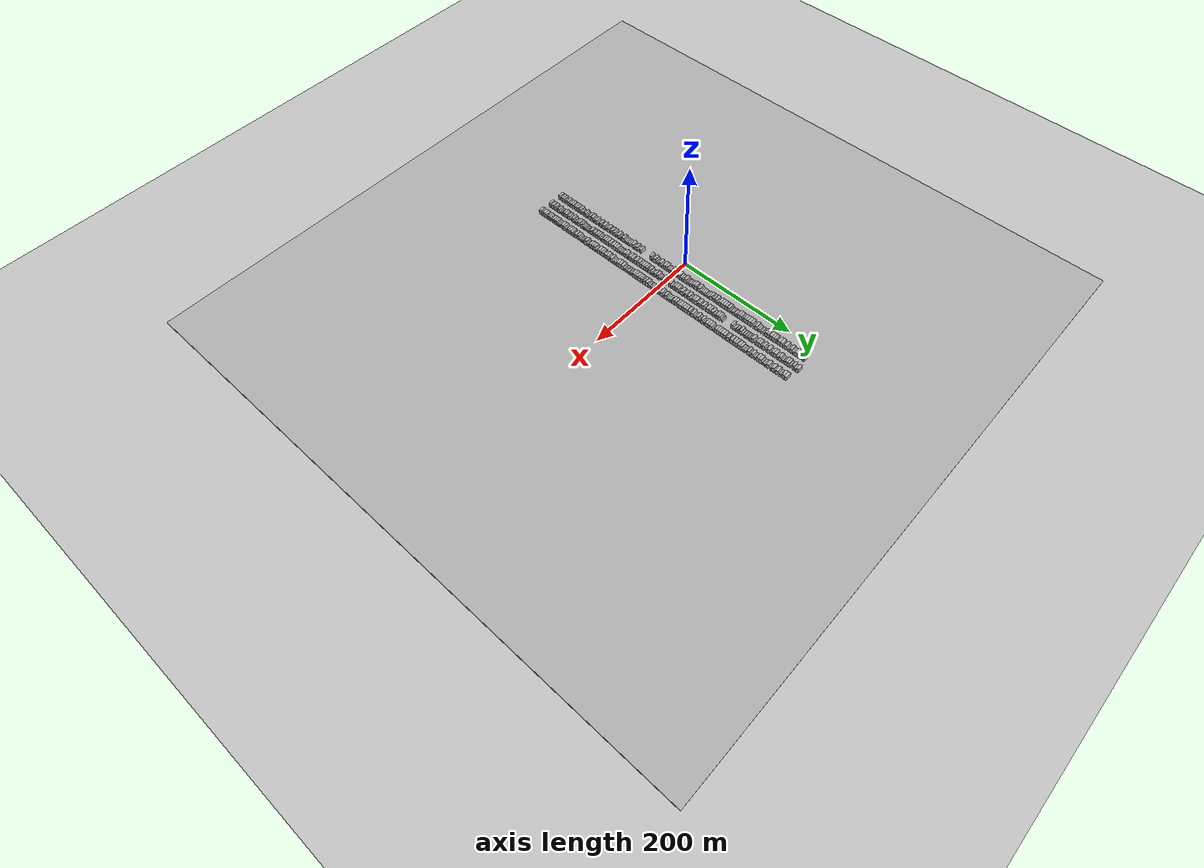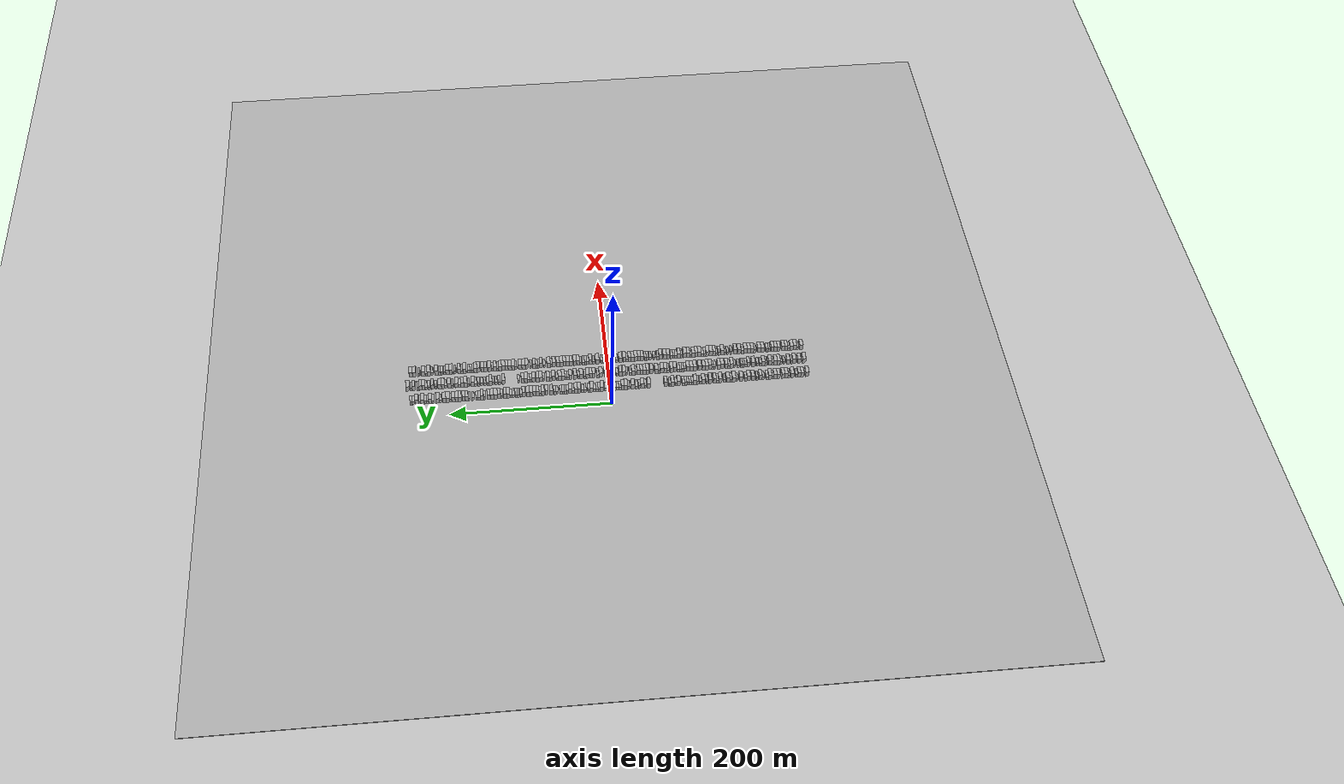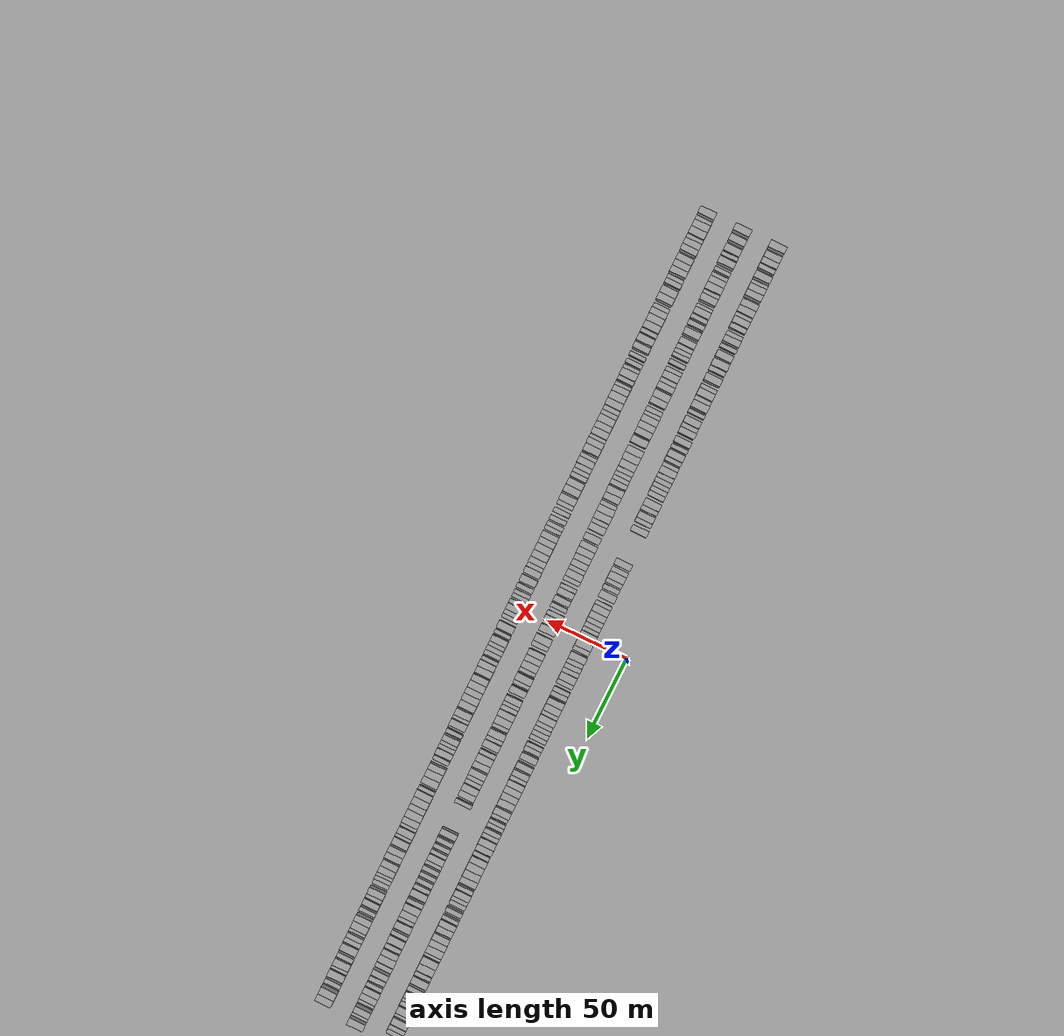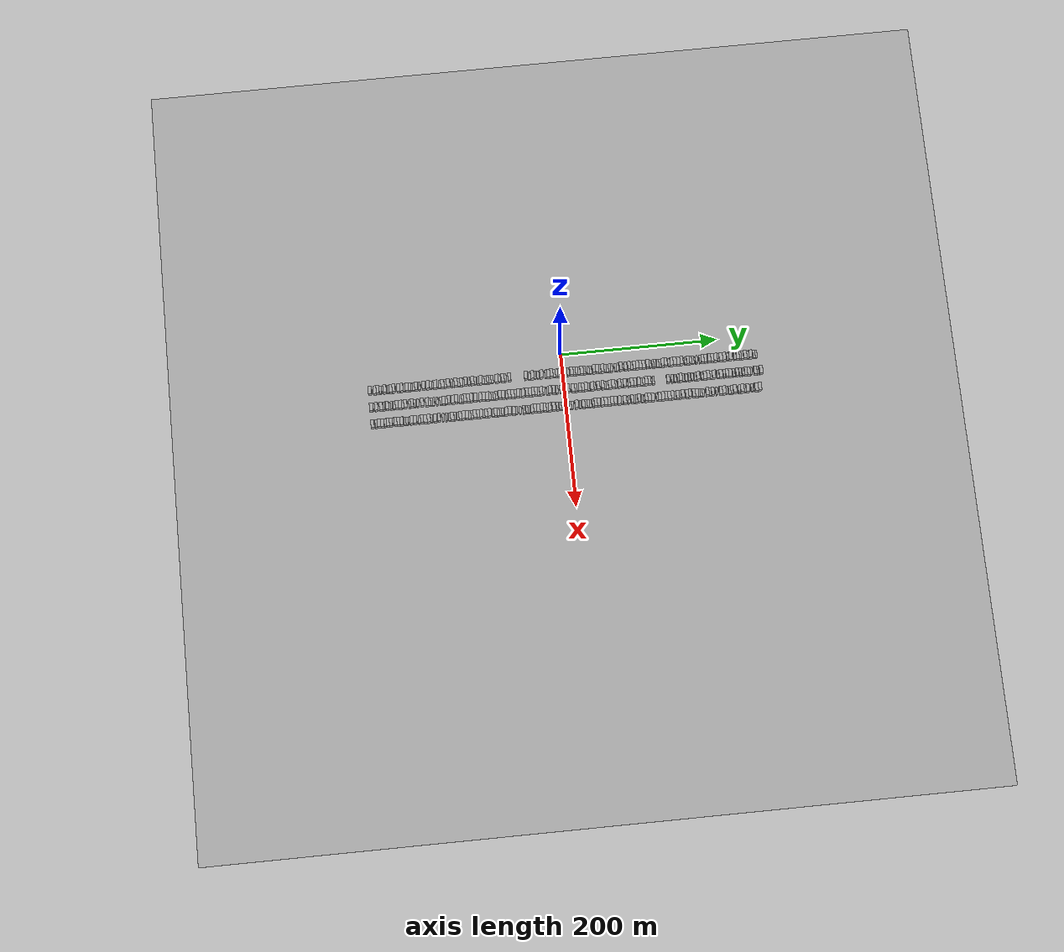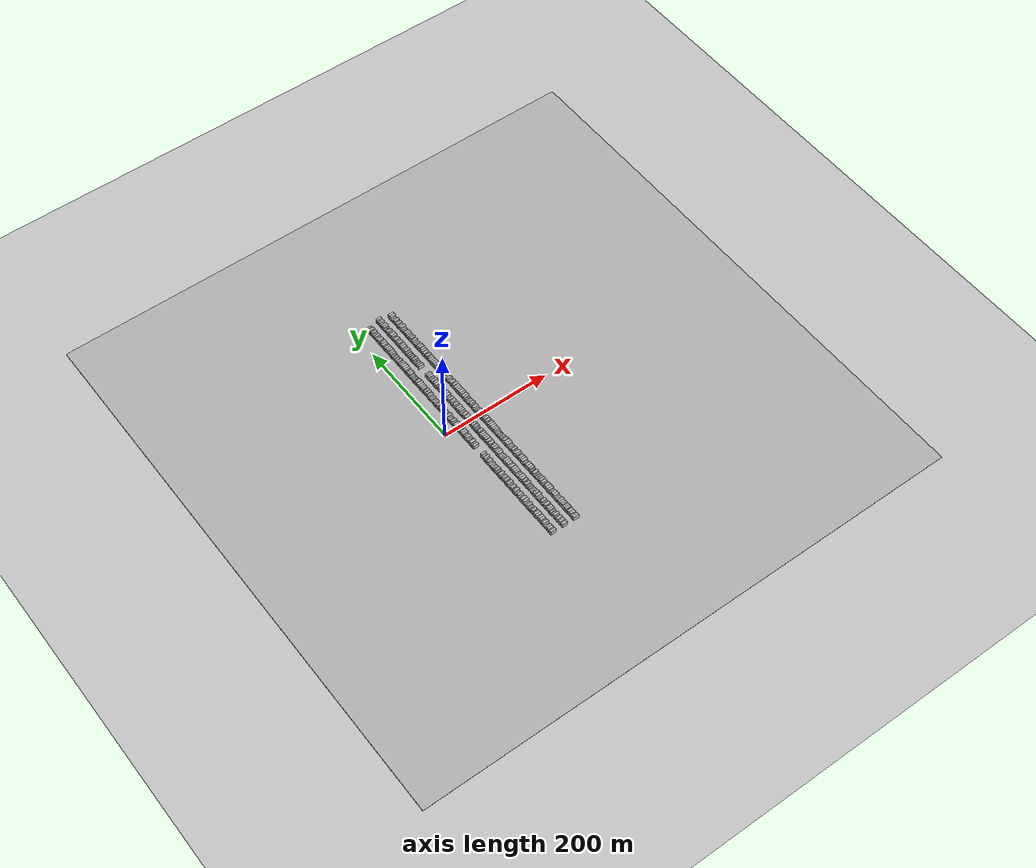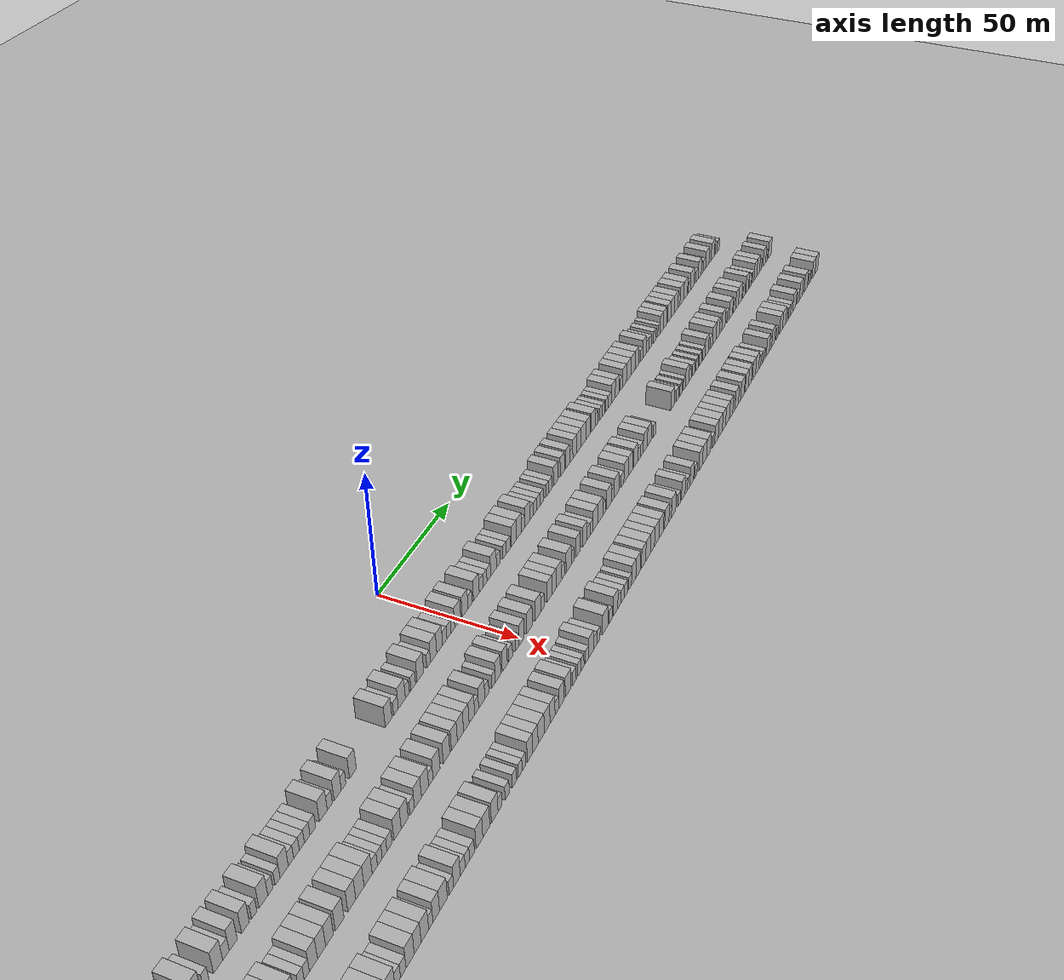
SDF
<?xml version="1.0" encoding="utf-8"?>

<sdf version="1.6">

   <world name="default">

      <gui fullscreen="0">

         <camera name="user_camera">

            <pose>-15 0 4.57585 0 0 0</pose>

            <view_controller>orbit</view_controller>

         </camera>

      </gui>

      <scene>

         <sky>

           <clouds>

             <speed>12</speed>

           </clouds>

         </sky>

         <ambient>0.4 0.4 0.4 1</ambient>

         <background>0.7 0.7 0.7 1</background>

         <shadows>1</shadows>

      </scene>

      <gravity>0 0 -9.8066</gravity>

      <magnetic_field>6e-06 2.3e-05 -4.2e-05</magnetic_field>

      <physics default="0" name="default_physics" type="ode">

         <ode>

            <solver>

               <type>quick</type>

               <iters>10</iters>

               <sor>1.0</sor>

               <use_dynamic_moi_rescaling>0</use_dynamic_moi_rescaling>

            </solver>

            <constraints>

               <cfm>0</cfm>

               <erp>0.2</erp>

               <contact_max_correcting_vel>100</contact_max_correcting_vel>

               <contact_surface_layer>0.001</contact_surface_layer>

            </constraints>

         </ode>

         <max_step_size>0.004</max_step_size>

         <real_time_factor>1</real_time_factor>

         <real_time_update_rate>250</real_time_update_rate>

      </physics>

      <light name="sun" type="directional">

         <cast_shadows>1</cast_shadows>

         <pose>0 0 10 0 0 0</pose>

         <diffuse>0.8 0.8 0.8 1</diffuse>

         <specular>0.2 0.2 0.2 1</specular>

         <attenuation>

            <range>1000</range>

            <constant>0.9</constant>

            <linear>0.01</linear>

            <quadratic>0.001</quadratic>

         </attenuation>

         <direction>-0.5 0.1 -0.9</direction>

      </light>

      <include>

         <name>ground_plane_1</name>

         <uri>model://HANNAS_ground_plane</uri>

         <pose>0 0 0  0 0 0</pose>

      </include>

      <include>

         <name>ground_plane_2</name>

         <uri>model://HANNAS_ground_plane</uri>

         <pose>100 0 0  0 0 0</pose>

      </include>

      <model name="building_1">

         <static>1</static>

         <pose frame="">25.0000 -245.8805 0 0.000000 0.000000 0.000000</pose>

         <link name="link">

            <pose frame="">0 0 4.50 0 0 0</pose>

            <collision name="collision">

               <geometry>

                  <box>

                     <size>10.0000 4.2390 9.0000</size>

                  </box>

               </geometry>

               <max_contacts>10</max_contacts>

               <surface>

                  <contact>

                     <ode/>

                  </contact>

                  <bounce/>

                  <friction>

                     <torsional>

                        <ode/>

                     </torsional>

                     <ode/>

                  </friction>

               </surface>

            </collision>

            <visual name="visual">

               <cast_shadows>0</cast_shadows>

               <geometry>

                  <box>

                     <size>10.0000 4.2390 9.0000</size>

                  </box>

               </geometry>

               <material>

                  <script>

                     <uri>model://HANNAS_wall/materials/scripts</uri>

                     <uri>model://HANNAS_wall/materials/textures</uri>

                     <name>vrc/HANNAS_wall</name>

                  </script>

               </material>

            </visual>

            <self_collide>0</self_collide>

            <enable_wind>0</enable_wind>

            <kinematic>0</kinematic>

         </link>

      </model>

      <model name="building_2">

         <static>1</static>

         <pose frame="">25.0000 -239.7748 0 0.000000 0.000000 0.000000</pose>

         <link name="link">

            <pose frame="">0 0 4.50 0 0 0</pose>

            <collision name="collision">

               <geometry>

                  <box>

                     <size>10.0000 3.9724 9.0000</size>

                  </box>

               </geometry>

               <max_contacts>10</max_contacts>

               <surface>

                  <contact>

                     <ode/>

                  </contact>

                  <bounce/>

                  <friction>

                     <torsional>

                        <ode/>

                     </torsional>

                     <ode/>

                  </friction>

               </surface>

            </collision>

            <visual name="visual">

               <cast_shadows>0</cast_shadows>

               <geometry>

                  <box>

                     <size>10.0000 3.9724 9.0000</size>

                  </box>

               </geometry>

               <material>

                  <script>

                     <uri>model://HANNAS_wall/materials/scripts</uri>

                     <uri>model://HANNAS_wall/materials/textures</uri>

                     <name>vrc/HANNAS_wall</name>

                  </script>

               </material>

            </visual>

            <self_collide>0</self_collide>

            <enable_wind>0</enable_wind>

            <kinematic>0</kinematic>

         </link>

      </model>

      <model name="building_3">

         <static>1</static>

         <pose frame="">25.0000 -235.9279 0 0.000000 0.000000 0.000000</pose>

         <link name="link">

            <pose frame="">0 0 4.50 0 0 0</pose>

            <collision name="collision">

               <geometry>

                  <box>

                     <size>10.0000 3.7213 9.0000</size>

                  </box>

               </geometry>

               <max_contacts>10</max_contacts>

               <surface>

                  <contact>

                     <ode/>

                  </contact>

                  <bounce/>

                  <friction>

                     <torsional>

                        <ode/>

                     </torsional>

                     <ode/>

                  </friction>

               </surface>

            </collision>

            <visual name="visual">

               <cast_shadows>0</cast_shadows>

               <geometry>

                  <box>

                     <size>10.0000 3.7213 9.0000</size>

                  </box>

               </geometry>

               <material>

                  <script>

                     <uri>model://HANNAS_wall/materials/scripts</uri>

                     <uri>model://HANNAS_wall/materials/textures</uri>

                     <name>vrc/HANNAS_wall</name>

                  </script>

               </material>

            </visual>

            <self_collide>0</self_collide>

            <enable_wind>0</enable_wind>

            <kinematic>0</kinematic>

         </link>

      </model>

      <model name="building_4">

         <static>1</static>

         <pose frame="">25.0000 -232.6269 0 0.000000 0.000000 0.000000</pose>

         <link name="link">

            <pose frame="">0 0 3.00 0 0 0</pose>

            <collision name="collision">

               <geometry>

                  <box>

                     <size>10.0000 2.8807 6.0000</size>

                  </box>

               </geometry>

               <max_contacts>10</max_contacts>

               <surface>

                  <contact>

                     <ode/>

                  </contact>

                  <bounce/>

                  <friction>

                     <torsional>

                        <ode/>

                     </torsional>

                     <ode/>

                  </friction>

               </surface>

            </collision>

            <visual name="visual">

               <cast_shadows>0</cast_shadows>

               <geometry>

                  <box>

                     <size>10.0000 2.8807 6.0000</size>

                  </box>

               </geometry>

               <material>

                  <script>

                     <uri>model://HANNAS_wall/materials/scripts</uri>

                     <uri>model://HANNAS_wall/materials/textures</uri>

                     <name>vrc/HANNAS_wall</name>

                  </script>

               </material>

            </visual>

            <self_collide>0</self_collide>

            <enable_wind>0</enable_wind>

            <kinematic>0</kinematic>

         </link>

      </model>

      <model name="building_5">

         <static>1</static>

         <pose frame="">25.0000 -227.1086 0 0.000000 0.000000 0.000000</pose>

         <link name="link">

            <pose frame="">0 0 4.50 0 0 0</pose>

            <collision name="collision">

               <geometry>

                  <box>

                     <size>10.0000 4.1559 9.0000</size>

                  </box>

               </geometry>

               <max_contacts>10</max_contacts>

               <surface>

                  <contact>

                     <ode/>

                  </contact>

                  <bounce/>

                  <friction>

                     <torsional>

                        <ode/>

                     </torsional>

                     <ode/>

                  </friction>

               </surface>

            </collision>

            <visual name="visual">

               <cast_shadows>0</cast_shadows>

               <geometry>

                  <box>

                     <size>10.0000 4.1559 9.0000</size>

                  </box>

               </geometry>

               <material>

                  <script>

                     <uri>model://HANNAS_wall/materials/scripts</uri>

                     <uri>model://HANNAS_wall/materials/textures</uri>

                     <name>vrc/HANNAS_wall</name>

                  </script>

               </material>

            </visual>

            <self_collide>0</self_collide>

            <enable_wind>0</enable_wind>

            <kinematic>0</kinematic>

         </link>

      </model>

      <model name="building_6">

         <static>1</static>

         <pose frame="">25.0000 -222.7845 0 0.000000 0.000000 0.000000</pose>

         <link name="link">

            <pose frame="">0 0 3.00 0 0 0</pose>

            <collision name="collision">

               <geometry>

                  <box>

                     <size>10.0000 2.4924 6.0000</size>

                  </box>

               </geometry>

               <max_contacts>10</max_contacts>

               <surface>

                  <contact>

                     <ode/>

                  </contact>

                  <bounce/>

                  <friction>

                     <torsional>

                        <ode/>

                     </torsional>

                     <ode/>

                  </friction>

               </surface>

            </collision>

            <visual name="visual">

               <cast_shadows>0</cast_shadows>

               <geometry>

                  <box>

                     <size>10.0000 2.4924 6.0000</size>

                  </box>

               </geometry>

               <material>

                  <script>

                     <uri>model://HANNAS_wall/materials/scripts</uri>

                     <uri>model://HANNAS_wall/materials/textures</uri>

                     <name>vrc/HANNAS_wall</name>

                  </script>

               </material>

            </visual>

            <self_collide>0</self_collide>

            <enable_wind>0</enable_wind>

            <kinematic>0</kinematic>

         </link>

      </model>

      <model name="building_7">

         <static>1</static>

         <pose frame="">25.0000 -219.5616 0 0.000000 0.000000 0.000000</pose>

         <link name="link">

            <pose frame="">0 0 4.50 0 0 0</pose>

            <collision name="collision">

               <geometry>

                  <box>

                     <size>10.0000 3.9534 9.0000</size>

                  </box>

               </geometry>

               <max_contacts>10</max_contacts>

               <surface>

                  <contact>

                     <ode/>

                  </contact>

                  <bounce/>

                  <friction>

                     <torsional>

                        <ode/>

                     </torsional>

                     <ode/>

                  </friction>

               </surface>

            </collision>

            <visual name="visual">

               <cast_shadows>0</cast_shadows>

               <geometry>

                  <box>

                     <size>10.0000 3.9534 9.0000</size>

                  </box>

               </geometry>

               <material>

                  <script>

                     <uri>model://HANNAS_wall/materials/scripts</uri>

                     <uri>model://HANNAS_wall/materials/textures</uri>

                     <name>vrc/HANNAS_wall</name>

                  </script>

               </material>

            </visual>

            <self_collide>0</self_collide>

            <enable_wind>0</enable_wind>

            <kinematic>0</kinematic>

         </link>

      </model>

      <model name="building_8">

         <static>1</static>

         <pose frame="">25.0000 -215.6390 0 0.000000 0.000000 0.000000</pose>

         <link name="link">

            <pose frame="">0 0 4.50 0 0 0</pose>

            <collision name="collision">

               <geometry>

                  <box>

                     <size>10.0000 3.8917 9.0000</size>

                  </box>

               </geometry>

               <max_contacts>10</max_contacts>

               <surface>

                  <contact>

                     <ode/>

                  </contact>

                  <bounce/>

                  <friction>

                     <torsional>

                        <ode/>

                     </torsional>

                     <ode/>

                  </friction>

               </surface>

            </collision>

            <visual name="visual">

               <cast_shadows>0</cast_shadows>

               <geometry>

                  <box>

                     <size>10.0000 3.8917 9.0000</size>

                  </box>

               </geometry>

               <material>

                  <script>

                     <uri>model://HANNAS_wall/materials/scripts</uri>

                     <uri>model://HANNAS_wall/materials/textures</uri>

                     <name>vrc/HANNAS_wall</name>

                  </script>

               </material>

            </visual>

            <self_collide>0</self_collide>

            <enable_wind>0</enable_wind>

            <kinematic>0</kinematic>

         </link>

      </model>

      <model name="building_9">

         <static>1</static>

         <pose frame="">25.0000 -209.7073 0 0.000000 0.000000 0.000000</pose>

         <link name="link">

            <pose frame="">0 0 4.50 0 0 0</pose>

            <collision name="collision">

               <geometry>

                  <box>

                     <size>10.0000 3.9717 9.0000</size>

                  </box>

               </geometry>

               <max_contacts>10</max_contacts>

               <surface>

                  <contact>

                     <ode/>

                  </contact>

                  <bounce/>

                  <friction>

                     <torsional>

                        <ode/>

                     </torsional>

                     <ode/>

                  </friction>

               </surface>

            </collision>

            <visual name="visual">

               <cast_shadows>0</cast_shadows>

               <geometry>

                  <box>

                     <size>10.0000 3.9717 9.0000</size>

                  </box>

               </geometry>

               <material>

                  <script>

                     <uri>model://HANNAS_wall/materials/scripts</uri>

                     <uri>model://HANNAS_wall/materials/textures</uri>

                     <name>vrc/HANNAS_wall</name>

                  </script>

               </material>

            </visual>

            <self_collide>0</self_collide>

            <enable_wind>0</enable_wind>

            <kinematic>0</kinematic>

         </link>

      </model>

      <model name="building_10">

         <static>1</static>

         <pose frame="">25.0000 -205.7023 0 0.000000 0.000000 0.000000</pose>

         <link name="link">

            <pose frame="">0 0 4.50 0 0 0</pose>

            <collision name="collision">

               <geometry>

                  <box>

                     <size>10.0000 4.0384 9.0000</size>

                  </box>

               </geometry>

               <max_contacts>10</max_contacts>

               <surface>

                  <contact>

                     <ode/>

                  </contact>

                  <bounce/>

                  <friction>

                     <torsional>

                        <ode/>

                     </torsional>

                     <ode/>

                  </friction>

               </surface>

            </collision>

            <visual name="visual">

               <cast_shadows>0</cast_shadows>

               <geometry>

                  <box>

                     <size>10.0000 4.0384 9.0000</size>

                  </box>

               </geometry>

               <material>

                  <script>

                     <uri>model://HANNAS_wall/materials/scripts</uri>

                     <uri>model://HANNAS_wall/materials/textures</uri>

                     <name>vrc/HANNAS_wall</name>

                  </script>

               </material>

            </visual>

            <self_collide>0</self_collide>

            <enable_wind>0</enable_wind>

            <kinematic>0</kinematic>

         </link>

      </model>

      <model name="building_11">

         <static>1</static>

         <pose frame="">25.0000 -202.3700 0 0.000000 0.000000 0.000000</pose>

         <link name="link">

            <pose frame="">0 0 3.00 0 0 0</pose>

            <collision name="collision">

               <geometry>

                  <box>

                     <size>10.0000 2.6262 6.0000</size>

                  </box>

               </geometry>

               <max_contacts>10</max_contacts>

               <surface>

                  <contact>

                     <ode/>

                  </contact>

                  <bounce/>

                  <friction>

                     <torsional>

                        <ode/>

                     </torsional>

                     <ode/>

                  </friction>

               </surface>

            </collision>

            <visual name="visual">

               <cast_shadows>0</cast_shadows>

               <geometry>

                  <box>

                     <size>10.0000 2.6262 6.0000</size>

                  </box>

               </geometry>

               <material>

                  <script>

                     <uri>model://HANNAS_wall/materials/scripts</uri>

                     <uri>model://HANNAS_wall/materials/textures</uri>

                     <name>vrc/HANNAS_wall</name>

                  </script>

               </material>

            </visual>

            <self_collide>0</self_collide>

            <enable_wind>0</enable_wind>

            <kinematic>0</kinematic>

         </link>

      </model>

      <model name="building_12">

         <static>1</static>

         <pose frame="">25.0000 -199.0127 0 0.000000 0.000000 0.000000</pose>

         <link name="link">

            <pose frame="">0 0 4.50 0 0 0</pose>

            <collision name="collision">

               <geometry>

                  <box>

                     <size>10.0000 4.0882 9.0000</size>

                  </box>

               </geometry>

               <max_contacts>10</max_contacts>

               <surface>

                  <contact>

                     <ode/>

                  </contact>

                  <bounce/>

                  <friction>

                     <torsional>

                        <ode/>

                     </torsional>

                     <ode/>

                  </friction>

               </surface>

            </collision>

            <visual name="visual">

               <cast_shadows>0</cast_shadows>

               <geometry>

                  <box>

                     <size>10.0000 4.0882 9.0000</size>

                  </box>

               </geometry>

               <material>

                  <script>

                     <uri>model://HANNAS_wall/materials/scripts</uri>

                     <uri>model://HANNAS_wall/materials/textures</uri>

                     <name>vrc/HANNAS_wall</name>

                  </script>

               </material>

            </visual>

            <self_collide>0</self_collide>

            <enable_wind>0</enable_wind>

            <kinematic>0</kinematic>

         </link>

      </model>

      <model name="building_13">

         <static>1</static>

         <pose frame="">25.0000 -195.4758 0 0.000000 0.000000 0.000000</pose>

         <link name="link">

            <pose frame="">0 0 3.00 0 0 0</pose>

            <collision name="collision">

               <geometry>

                  <box>

                     <size>10.0000 2.9857 6.0000</size>

                  </box>

               </geometry>

               <max_contacts>10</max_contacts>

               <surface>

                  <contact>

                     <ode/>

                  </contact>

                  <bounce/>

                  <friction>

                     <torsional>

                        <ode/>

                     </torsional>

                     <ode/>

                  </friction>

               </surface>

            </collision>

            <visual name="visual">

               <cast_shadows>0</cast_shadows>

               <geometry>

                  <box>

                     <size>10.0000 2.9857 6.0000</size>

                  </box>

               </geometry>

               <material>

                  <script>

                     <uri>model://HANNAS_wall/materials/scripts</uri>

                     <uri>model://HANNAS_wall/materials/textures</uri>

                     <name>vrc/HANNAS_wall</name>

                  </script>

               </material>

            </visual>

            <self_collide>0</self_collide>

            <enable_wind>0</enable_wind>

            <kinematic>0</kinematic>

         </link>

      </model>

      <model name="building_14">

         <static>1</static>

         <pose frame="">25.0000 -190.4955 0 0.000000 0.000000 0.000000</pose>

         <link name="link">

            <pose frame="">0 0 3.00 0 0 0</pose>

            <collision name="collision">

               <geometry>

                  <box>

                     <size>10.0000 2.9749 6.0000</size>

                  </box>

               </geometry>

               <max_contacts>10</max_contacts>

               <surface>

                  <contact>

                     <ode/>

                  </contact>

                  <bounce/>

                  <friction>

                     <torsional>

                        <ode/>

                     </torsional>

                     <ode/>

                  </friction>

               </surface>

            </collision>

            <visual name="visual">

               <cast_shadows>0</cast_shadows>

               <geometry>

                  <box>

                     <size>10.0000 2.9749 6.0000</size>

                  </box>

               </geometry>

               <material>

                  <script>

                     <uri>model://HANNAS_wall/materials/scripts</uri>

                     <uri>model://HANNAS_wall/materials/textures</uri>

                     <name>vrc/HANNAS_wall</name>

                  </script>

               </material>

            </visual>

            <self_collide>0</self_collide>

            <enable_wind>0</enable_wind>

            <kinematic>0</kinematic>

         </link>

      </model>

      <model name="building_15">

         <static>1</static>

         <pose frame="">25.0000 -187.0728 0 0.000000 0.000000 0.000000</pose>

         <link name="link">

            <pose frame="">0 0 4.50 0 0 0</pose>

            <collision name="collision">

               <geometry>

                  <box>

                     <size>10.0000 3.8704 9.0000</size>

                  </box>

               </geometry>

               <max_contacts>10</max_contacts>

               <surface>

                  <contact>

                     <ode/>

                  </contact>

                  <bounce/>

                  <friction>

                     <torsional>

                        <ode/>

                     </torsional>

                     <ode/>

                  </friction>

               </surface>

            </collision>

            <visual name="visual">

               <cast_shadows>0</cast_shadows>

               <geometry>

                  <box>

                     <size>10.0000 3.8704 9.0000</size>

                  </box>

               </geometry>

               <material>

                  <script>

                     <uri>model://HANNAS_wall/materials/scripts</uri>

                     <uri>model://HANNAS_wall/materials/textures</uri>

                     <name>vrc/HANNAS_wall</name>

                  </script>

               </material>

            </visual>

            <self_collide>0</self_collide>

            <enable_wind>0</enable_wind>

            <kinematic>0</kinematic>

         </link>

      </model>

      <model name="building_16">

         <static>1</static>

         <pose frame="">25.0000 -182.8939 0 0.000000 0.000000 0.000000</pose>

         <link name="link">

            <pose frame="">0 0 3.00 0 0 0</pose>

            <collision name="collision">

               <geometry>

                  <box>

                     <size>10.0000 2.4874 6.0000</size>

                  </box>

               </geometry>

               <max_contacts>10</max_contacts>

               <surface>

                  <contact>

                     <ode/>

                  </contact>

                  <bounce/>

                  <friction>

                     <torsional>

                        <ode/>

                     </torsional>

                     <ode/>

                  </friction>

               </surface>

            </collision>

            <visual name="visual">

               <cast_shadows>0</cast_shadows>

               <geometry>

                  <box>

                     <size>10.0000 2.4874 6.0000</size>

                  </box>

               </geometry>

               <material>

                  <script>

                     <uri>model://HANNAS_wall/materials/scripts</uri>

                     <uri>model://HANNAS_wall/materials/textures</uri>

                     <name>vrc/HANNAS_wall</name>

                  </script>

               </material>

            </visual>

            <self_collide>0</self_collide>

            <enable_wind>0</enable_wind>

            <kinematic>0</kinematic>

         </link>

      </model>

      <model name="building_17">

         <static>1</static>

         <pose frame="">25.0000 -177.5902 0 0.000000 0.000000 0.000000</pose>

         <link name="link">

            <pose frame="">0 0 4.50 0 0 0</pose>

            <collision name="collision">

               <geometry>

                  <box>

                     <size>10.0000 4.1200 9.0000</size>

                  </box>

               </geometry>

               <max_contacts>10</max_contacts>

               <surface>

                  <contact>

                     <ode/>

                  </contact>

                  <bounce/>

                  <friction>

                     <torsional>

                        <ode/>

                     </torsional>

                     <ode/>

                  </friction>

               </surface>

            </collision>

            <visual name="visual">

               <cast_shadows>0</cast_shadows>

               <geometry>

                  <box>

                     <size>10.0000 4.1200 9.0000</size>

                  </box>

               </geometry>

               <material>

                  <script>

                     <uri>model://HANNAS_wall/materials/scripts</uri>

                     <uri>model://HANNAS_wall/materials/textures</uri>

                     <name>vrc/HANNAS_wall</name>

                  </script>

               </material>

            </visual>

            <self_collide>0</self_collide>

            <enable_wind>0</enable_wind>

            <kinematic>0</kinematic>

         </link>

      </model>

      <model name="building_18">

         <static>1</static>

         <pose frame="">25.0000 -172.3261 0 0.000000 0.000000 0.000000</pose>

         <link name="link">

            <pose frame="">0 0 4.50 0 0 0</pose>

            <collision name="collision">

               <geometry>

                  <box>

                     <size>10.0000 4.4082 9.0000</size>

                  </box>

               </geometry>

               <max_contacts>10</max_contacts>

               <surface>

                  <contact>

                     <ode/>

                  </contact>

                  <bounce/>

                  <friction>

                     <torsional>

                        <ode/>

                     </torsional>

                     <ode/>

                  </friction>

               </surface>

            </collision>

            <visual name="visual">

               <cast_shadows>0</cast_shadows>

               <geometry>

                  <box>

                     <size>10.0000 4.4082 9.0000</size>

                  </box>

               </geometry>

               <material>

                  <script>

                     <uri>model://HANNAS_wall/materials/scripts</uri>

                     <uri>model://HANNAS_wall/materials/textures</uri>

                     <name>vrc/HANNAS_wall</name>

                  </script>

               </material>

            </visual>

            <self_collide>0</self_collide>

            <enable_wind>0</enable_wind>

            <kinematic>0</kinematic>

         </link>

      </model>

      <model name="building_19">

         <static>1</static>

         <pose frame="">25.0000 -168.6537 0 0.000000 0.000000 0.000000</pose>

         <link name="link">

            <pose frame="">0 0 3.00 0 0 0</pose>

            <collision name="collision">

               <geometry>

                  <box>

                     <size>10.0000 2.9368 6.0000</size>

                  </box>

               </geometry>

               <max_contacts>10</max_contacts>

               <surface>

                  <contact>

                     <ode/>

                  </contact>

                  <bounce/>

                  <friction>

                     <torsional>

                        <ode/>

                     </torsional>

                     <ode/>

                  </friction>

               </surface>

            </collision>

            <visual name="visual">

               <cast_shadows>0</cast_shadows>

               <geometry>

                  <box>

                     <size>10.0000 2.9368 6.0000</size>

                  </box>

               </geometry>

               <material>

                  <script>

                     <uri>model://HANNAS_wall/materials/scripts</uri>

                     <uri>model://HANNAS_wall/materials/textures</uri>

                     <name>vrc/HANNAS_wall</name>

                  </script>

               </material>

            </visual>

            <self_collide>0</self_collide>

            <enable_wind>0</enable_wind>

            <kinematic>0</kinematic>

         </link>

      </model>

      <model name="building_20">

         <static>1</static>

         <pose frame="">25.0000 -162.9495 0 0.000000 0.000000 0.000000</pose>

         <link name="link">

            <pose frame="">0 0 4.50 0 0 0</pose>

            <collision name="collision">

               <geometry>

                  <box>

                     <size>10.0000 4.4717 9.0000</size>

                  </box>

               </geometry>

               <max_contacts>10</max_contacts>

               <surface>

                  <contact>

                     <ode/>

                  </contact>

                  <bounce/>

                  <friction>

                     <torsional>

                        <ode/>

                     </torsional>

                     <ode/>

                  </friction>

               </surface>

            </collision>

            <visual name="visual">

               <cast_shadows>0</cast_shadows>

               <geometry>

                  <box>

                     <size>10.0000 4.4717 9.0000</size>

                  </box>

               </geometry>

               <material>

                  <script>

                     <uri>model://HANNAS_wall/materials/scripts</uri>

                     <uri>model://HANNAS_wall/materials/textures</uri>

                     <name>vrc/HANNAS_wall</name>

                  </script>

               </material>

            </visual>

            <self_collide>0</self_collide>

            <enable_wind>0</enable_wind>

            <kinematic>0</kinematic>

         </link>

      </model>

      <model name="building_21">

         <static>1</static>

         <pose frame="">25.0000 -157.2879 0 0.000000 0.000000 0.000000</pose>

         <link name="link">

            <pose frame="">0 0 3.00 0 0 0</pose>

            <collision name="collision">

               <geometry>

                  <box>

                     <size>10.0000 2.8514 6.0000</size>

                  </box>

               </geometry>

               <max_contacts>10</max_contacts>

               <surface>

                  <contact>

                     <ode/>

                  </contact>

                  <bounce/>

                  <friction>

                     <torsional>

                        <ode/>

                     </torsional>

                     <ode/>

                  </friction>

               </surface>

            </collision>

            <visual name="visual">

               <cast_shadows>0</cast_shadows>

               <geometry>

                  <box>

                     <size>10.0000 2.8514 6.0000</size>

                  </box>

               </geometry>

               <material>

                  <script>

                     <uri>model://HANNAS_wall/materials/scripts</uri>

                     <uri>model://HANNAS_wall/materials/textures</uri>

                     <name>vrc/HANNAS_wall</name>

                  </script>

               </material>

            </visual>

            <self_collide>0</self_collide>

            <enable_wind>0</enable_wind>

            <kinematic>0</kinematic>

         </link>

      </model>

      <model name="building_22">

         <static>1</static>

         <pose frame="">25.0000 -153.6557 0 0.000000 0.000000 0.000000</pose>

         <link name="link">

            <pose frame="">0 0 4.50 0 0 0</pose>

            <collision name="collision">

               <geometry>

                  <box>

                     <size>10.0000 4.4130 9.0000</size>

                  </box>

               </geometry>

               <max_contacts>10</max_contacts>

               <surface>

                  <contact>

                     <ode/>

                  </contact>

                  <bounce/>

                  <friction>

                     <torsional>

                        <ode/>

                     </torsional>

                     <ode/>

                  </friction>

               </surface>

            </collision>

            <visual name="visual">

               <cast_shadows>0</cast_shadows>

               <geometry>

                  <box>

                     <size>10.0000 4.4130 9.0000</size>

                  </box>

               </geometry>

               <material>

                  <script>

                     <uri>model://HANNAS_wall/materials/scripts</uri>

                     <uri>model://HANNAS_wall/materials/textures</uri>

                     <name>vrc/HANNAS_wall</name>

                  </script>

               </material>

            </visual>

            <self_collide>0</self_collide>

            <enable_wind>0</enable_wind>

            <kinematic>0</kinematic>

         </link>

      </model>

      <model name="building_23">

         <static>1</static>

         <pose frame="">25.0000 -149.9778 0 0.000000 0.000000 0.000000</pose>

         <link name="link">

            <pose frame="">0 0 3.00 0 0 0</pose>

            <collision name="collision">

               <geometry>

                  <box>

                     <size>10.0000 2.9429 6.0000</size>

                  </box>

               </geometry>

               <max_contacts>10</max_contacts>

               <surface>

                  <contact>

                     <ode/>

                  </contact>

                  <bounce/>

                  <friction>

                     <torsional>

                        <ode/>

                     </torsional>

                     <ode/>

                  </friction>

               </surface>

            </collision>

            <visual name="visual">

               <cast_shadows>0</cast_shadows>

               <geometry>

                  <box>

                     <size>10.0000 2.9429 6.0000</size>

                  </box>

               </geometry>

               <material>

                  <script>

                     <uri>model://HANNAS_wall/materials/scripts</uri>

                     <uri>model://HANNAS_wall/materials/textures</uri>

                     <name>vrc/HANNAS_wall</name>

                  </script>

               </material>

            </visual>

            <self_collide>0</self_collide>

            <enable_wind>0</enable_wind>

            <kinematic>0</kinematic>

         </link>

      </model>

      <model name="building_24">

         <static>1</static>

         <pose frame="">25.0000 -146.2924 0 0.000000 0.000000 0.000000</pose>

         <link name="link">

            <pose frame="">0 0 4.50 0 0 0</pose>

            <collision name="collision">

               <geometry>

                  <box>

                     <size>10.0000 4.4278 9.0000</size>

                  </box>

               </geometry>

               <max_contacts>10</max_contacts>

               <surface>

                  <contact>

                     <ode/>

                  </contact>

                  <bounce/>

                  <friction>

                     <torsional>

                        <ode/>

                     </torsional>

                     <ode/>

                  </friction>

               </surface>

            </collision>

            <visual name="visual">

               <cast_shadows>0</cast_shadows>

               <geometry>

                  <box>

                     <size>10.0000 4.4278 9.0000</size>

                  </box>

               </geometry>

               <material>

                  <script>

                     <uri>model://HANNAS_wall/materials/scripts</uri>

                     <uri>model://HANNAS_wall/materials/textures</uri>

                     <name>vrc/HANNAS_wall</name>

                  </script>

               </material>

            </visual>

            <self_collide>0</self_collide>

            <enable_wind>0</enable_wind>

            <kinematic>0</kinematic>

         </link>

      </model>

      <model name="building_25">

         <static>1</static>

         <pose frame="">25.0000 -141.8379 0 0.000000 0.000000 0.000000</pose>

         <link name="link">

            <pose frame="">0 0 3.00 0 0 0</pose>

            <collision name="collision">

               <geometry>

                  <box>

                     <size>10.0000 2.4812 6.0000</size>

                  </box>

               </geometry>

               <max_contacts>10</max_contacts>

               <surface>

                  <contact>

                     <ode/>

                  </contact>

                  <bounce/>

                  <friction>

                     <torsional>

                        <ode/>

                     </torsional>

                     <ode/>

                  </friction>

               </surface>

            </collision>

            <visual name="visual">

               <cast_shadows>0</cast_shadows>

               <geometry>

                  <box>

                     <size>10.0000 2.4812 6.0000</size>

                  </box>

               </geometry>

               <material>

                  <script>

                     <uri>model://HANNAS_wall/materials/scripts</uri>

                     <uri>model://HANNAS_wall/materials/textures</uri>

                     <name>vrc/HANNAS_wall</name>

                  </script>

               </material>

            </visual>

            <self_collide>0</self_collide>

            <enable_wind>0</enable_wind>

            <kinematic>0</kinematic>

         </link>

      </model>

      <model name="building_26">

         <static>1</static>

         <pose frame="">25.0000 -136.5170 0 0.000000 0.000000 0.000000</pose>

         <link name="link">

            <pose frame="">0 0 4.50 0 0 0</pose>

            <collision name="collision">

               <geometry>

                  <box>

                     <size>10.0000 4.1606 9.0000</size>

                  </box>

               </geometry>

               <max_contacts>10</max_contacts>

               <surface>

                  <contact>

                     <ode/>

                  </contact>

                  <bounce/>

                  <friction>

                     <torsional>

                        <ode/>

                     </torsional>

                     <ode/>

                  </friction>

               </surface>

            </collision>

            <visual name="visual">

               <cast_shadows>0</cast_shadows>

               <geometry>

                  <box>

                     <size>10.0000 4.1606 9.0000</size>

                  </box>

               </geometry>

               <material>

                  <script>

                     <uri>model://HANNAS_wall/materials/scripts</uri>

                     <uri>model://HANNAS_wall/materials/textures</uri>

                     <name>vrc/HANNAS_wall</name>

                  </script>

               </material>

            </visual>

            <self_collide>0</self_collide>

            <enable_wind>0</enable_wind>

            <kinematic>0</kinematic>

         </link>

      </model>

      <model name="building_27">

         <static>1</static>

         <pose frame="">25.0000 -132.9496 0 0.000000 0.000000 0.000000</pose>

         <link name="link">

            <pose frame="">0 0 3.00 0 0 0</pose>

            <collision name="collision">

               <geometry>

                  <box>

                     <size>10.0000 2.9743 6.0000</size>

                  </box>

               </geometry>

               <max_contacts>10</max_contacts>

               <surface>

                  <contact>

                     <ode/>

                  </contact>

                  <bounce/>

                  <friction>

                     <torsional>

                        <ode/>

                     </torsional>

                     <ode/>

                  </friction>

               </surface>

            </collision>

            <visual name="visual">

               <cast_shadows>0</cast_shadows>

               <geometry>

                  <box>

                     <size>10.0000 2.9743 6.0000</size>

                  </box>

               </geometry>

               <material>

                  <script>

                     <uri>model://HANNAS_wall/materials/scripts</uri>

                     <uri>model://HANNAS_wall/materials/textures</uri>

                     <name>vrc/HANNAS_wall</name>

                  </script>

               </material>

            </visual>

            <self_collide>0</self_collide>

            <enable_wind>0</enable_wind>

            <kinematic>0</kinematic>

         </link>

      </model>

      <model name="building_28">

         <static>1</static>

         <pose frame="">25.0000 -129.6148 0 0.000000 0.000000 0.000000</pose>

         <link name="link">

            <pose frame="">0 0 4.50 0 0 0</pose>

            <collision name="collision">

               <geometry>

                  <box>

                     <size>10.0000 3.6952 9.0000</size>

                  </box>

               </geometry>

               <max_contacts>10</max_contacts>

               <surface>

                  <contact>

                     <ode/>

                  </contact>

                  <bounce/>

                  <friction>

                     <torsional>

                        <ode/>

                     </torsional>

                     <ode/>

                  </friction>

               </surface>

            </collision>

            <visual name="visual">

               <cast_shadows>0</cast_shadows>

               <geometry>

                  <box>

                     <size>10.0000 3.6952 9.0000</size>

                  </box>

               </geometry>

               <material>

                  <script>

                     <uri>model://HANNAS_wall/materials/scripts</uri>

                     <uri>model://HANNAS_wall/materials/textures</uri>

                     <name>vrc/HANNAS_wall</name>

                  </script>

               </material>

            </visual>

            <self_collide>0</self_collide>

            <enable_wind>0</enable_wind>

            <kinematic>0</kinematic>

         </link>

      </model>

      <model name="building_29">

         <static>1</static>

         <pose frame="">25.0000 -123.9301 0 0.000000 0.000000 0.000000</pose>

         <link name="link">

            <pose frame="">0 0 4.50 0 0 0</pose>

            <collision name="collision">

               <geometry>

                  <box>

                     <size>10.0000 3.6742 9.0000</size>

                  </box>

               </geometry>

               <max_contacts>10</max_contacts>

               <surface>

                  <contact>

                     <ode/>

                  </contact>

                  <bounce/>

                  <friction>

                     <torsional>

                        <ode/>

                     </torsional>

                     <ode/>

                  </friction>

               </surface>

            </collision>

            <visual name="visual">

               <cast_shadows>0</cast_shadows>

               <geometry>

                  <box>

                     <size>10.0000 3.6742 9.0000</size>

                  </box>

               </geometry>

               <material>

                  <script>

                     <uri>model://HANNAS_wall/materials/scripts</uri>

                     <uri>model://HANNAS_wall/materials/textures</uri>

                     <name>vrc/HANNAS_wall</name>

                  </script>

               </material>

            </visual>

            <self_collide>0</self_collide>

            <enable_wind>0</enable_wind>

            <kinematic>0</kinematic>

         </link>

      </model>

      <model name="building_30">

         <static>1</static>

         <pose frame="">25.0000 -119.7946 0 0.000000 0.000000 0.000000</pose>

         <link name="link">

            <pose frame="">0 0 3.00 0 0 0</pose>

            <collision name="collision">

               <geometry>

                  <box>

                     <size>10.0000 2.5968 6.0000</size>

                  </box>

               </geometry>

               <max_contacts>10</max_contacts>

               <surface>

                  <contact>

                     <ode/>

                  </contact>

                  <bounce/>

                  <friction>

                     <torsional>

                        <ode/>

                     </torsional>

                     <ode/>

                  </friction>

               </surface>

            </collision>

            <visual name="visual">

               <cast_shadows>0</cast_shadows>

               <geometry>

                  <box>

                     <size>10.0000 2.5968 6.0000</size>

                  </box>

               </geometry>

               <material>

                  <script>

                     <uri>model://HANNAS_wall/materials/scripts</uri>

                     <uri>model://HANNAS_wall/materials/textures</uri>

                     <name>vrc/HANNAS_wall</name>

                  </script>

               </material>

            </visual>

            <self_collide>0</self_collide>

            <enable_wind>0</enable_wind>

            <kinematic>0</kinematic>

         </link>

      </model>

      <model name="building_31">

         <static>1</static>

         <pose frame="">25.0000 -115.3570 0 0.000000 0.000000 0.000000</pose>

         <link name="link">

            <pose frame="">0 0 4.50 0 0 0</pose>

            <collision name="collision">

               <geometry>

                  <box>

                     <size>10.0000 4.2784 9.0000</size>

                  </box>

               </geometry>

               <max_contacts>10</max_contacts>

               <surface>

                  <contact>

                     <ode/>

                  </contact>

                  <bounce/>

                  <friction>

                     <torsional>

                        <ode/>

                     </torsional>

                     <ode/>

                  </friction>

               </surface>

            </collision>

            <visual name="visual">

               <cast_shadows>0</cast_shadows>

               <geometry>

                  <box>

                     <size>10.0000 4.2784 9.0000</size>

                  </box>

               </geometry>

               <material>

                  <script>

                     <uri>model://HANNAS_wall/materials/scripts</uri>

                     <uri>model://HANNAS_wall/materials/textures</uri>

                     <name>vrc/HANNAS_wall</name>

                  </script>

               </material>

            </visual>

            <self_collide>0</self_collide>

            <enable_wind>0</enable_wind>

            <kinematic>0</kinematic>

         </link>

      </model>

      <model name="building_32">

         <static>1</static>

         <pose frame="">25.0000 -111.9422 0 0.000000 0.000000 0.000000</pose>

         <link name="link">

            <pose frame="">0 0 3.00 0 0 0</pose>

            <collision name="collision">

               <geometry>

                  <box>

                     <size>10.0000 2.5513 6.0000</size>

                  </box>

               </geometry>

               <max_contacts>10</max_contacts>

               <surface>

                  <contact>

                     <ode/>

                  </contact>

                  <bounce/>

                  <friction>

                     <torsional>

                        <ode/>

                     </torsional>

                     <ode/>

                  </friction>

               </surface>

            </collision>

            <visual name="visual">

               <cast_shadows>0</cast_shadows>

               <geometry>

                  <box>

                     <size>10.0000 2.5513 6.0000</size>

                  </box>

               </geometry>

               <material>

                  <script>

                     <uri>model://HANNAS_wall/materials/scripts</uri>

                     <uri>model://HANNAS_wall/materials/textures</uri>

                     <name>vrc/HANNAS_wall</name>

                  </script>

               </material>

            </visual>

            <self_collide>0</self_collide>

            <enable_wind>0</enable_wind>

            <kinematic>0</kinematic>

         </link>

      </model>

      <model name="building_33">

         <static>1</static>

         <pose frame="">25.0000 -108.4088 0 0.000000 0.000000 0.000000</pose>

         <link name="link">

            <pose frame="">0 0 3.00 0 0 0</pose>

            <collision name="collision">

               <geometry>

                  <box>

                     <size>10.0000 2.5154 6.0000</size>

                  </box>

               </geometry>

               <max_contacts>10</max_contacts>

               <surface>

                  <contact>

                     <ode/>

                  </contact>

                  <bounce/>

                  <friction>

                     <torsional>

                        <ode/>

                     </torsional>

                     <ode/>

                  </friction>

               </surface>

            </collision>

            <visual name="visual">

               <cast_shadows>0</cast_shadows>

               <geometry>

                  <box>

                     <size>10.0000 2.5154 6.0000</size>

                  </box>

               </geometry>

               <material>

                  <script>

                     <uri>model://HANNAS_wall/materials/scripts</uri>

                     <uri>model://HANNAS_wall/materials/textures</uri>

                     <name>vrc/HANNAS_wall</name>

                  </script>

               </material>

            </visual>

            <self_collide>0</self_collide>

            <enable_wind>0</enable_wind>

            <kinematic>0</kinematic>

         </link>

      </model>

      <model name="building_34">

         <static>1</static>

         <pose frame="">25.0000 -105.0760 0 0.000000 0.000000 0.000000</pose>

         <link name="link">

            <pose frame="">0 0 4.50 0 0 0</pose>

            <collision name="collision">

               <geometry>

                  <box>

                     <size>10.0000 4.1503 9.0000</size>

                  </box>

               </geometry>

               <max_contacts>10</max_contacts>

               <surface>

                  <contact>

                     <ode/>

                  </contact>

                  <bounce/>

                  <friction>

                     <torsional>

                        <ode/>

                     </torsional>

                     <ode/>

                  </friction>

               </surface>

            </collision>

            <visual name="visual">

               <cast_shadows>0</cast_shadows>

               <geometry>

                  <box>

                     <size>10.0000 4.1503 9.0000</size>

                  </box>

               </geometry>

               <material>

                  <script>

                     <uri>model://HANNAS_wall/materials/scripts</uri>

                     <uri>model://HANNAS_wall/materials/textures</uri>

                     <name>vrc/HANNAS_wall</name>

                  </script>

               </material>

            </visual>

            <self_collide>0</self_collide>

            <enable_wind>0</enable_wind>

            <kinematic>0</kinematic>

         </link>

      </model>

      <model name="building_35">

         <static>1</static>

         <pose frame="">25.0000 -101.6310 0 0.000000 0.000000 0.000000</pose>

         <link name="link">

            <pose frame="">0 0 3.00 0 0 0</pose>

            <collision name="collision">

               <geometry>

                  <box>

                     <size>10.0000 2.7396 6.0000</size>

                  </box>

               </geometry>

               <max_contacts>10</max_contacts>

               <surface>

                  <contact>

                     <ode/>

                  </contact>

                  <bounce/>

                  <friction>

                     <torsional>

                        <ode/>

                     </torsional>

                     <ode/>

                  </friction>

               </surface>

            </collision>

            <visual name="visual">

               <cast_shadows>0</cast_shadows>

               <geometry>

                  <box>

                     <size>10.0000 2.7396 6.0000</size>

                  </box>

               </geometry>

               <material>

                  <script>

                     <uri>model://HANNAS_wall/materials/scripts</uri>

                     <uri>model://HANNAS_wall/materials/textures</uri>

                     <name>vrc/HANNAS_wall</name>

                  </script>

               </material>

            </visual>

            <self_collide>0</self_collide>

            <enable_wind>0</enable_wind>

            <kinematic>0</kinematic>

         </link>

      </model>

      <model name="building_36">

         <static>1</static>

         <pose frame="">25.0000 -98.8149 0 0.000000 0.000000 0.000000</pose>

         <link name="link">

            <pose frame="">0 0 3.00 0 0 0</pose>

            <collision name="collision">

               <geometry>

                  <box>

                     <size>10.0000 2.8926 6.0000</size>

                  </box>

               </geometry>

               <max_contacts>10</max_contacts>

               <surface>

                  <contact>

                     <ode/>

                  </contact>

                  <bounce/>

                  <friction>

                     <torsional>

                        <ode/>

                     </torsional>

                     <ode/>

                  </friction>

               </surface>

            </collision>

            <visual name="visual">

               <cast_shadows>0</cast_shadows>

               <geometry>

                  <box>

                     <size>10.0000 2.8926 6.0000</size>

                  </box>

               </geometry>

               <material>

                  <script>

                     <uri>model://HANNAS_wall/materials/scripts</uri>

                     <uri>model://HANNAS_wall/materials/textures</uri>

                     <name>vrc/HANNAS_wall</name>

                  </script>

               </material>

            </visual>

            <self_collide>0</self_collide>

            <enable_wind>0</enable_wind>

            <kinematic>0</kinematic>

         </link>

      </model>

      <model name="building_37">

         <static>1</static>

         <pose frame="">25.0000 -96.0426 0 0.000000 0.000000 0.000000</pose>

         <link name="link">

            <pose frame="">0 0 3.00 0 0 0</pose>

            <collision name="collision">

               <geometry>

                  <box>

                     <size>10.0000 2.6519 6.0000</size>

                  </box>

               </geometry>

               <max_contacts>10</max_contacts>

               <surface>

                  <contact>

                     <ode/>

                  </contact>

                  <bounce/>

                  <friction>

                     <torsional>

                        <ode/>

                     </torsional>

                     <ode/>

                  </friction>

               </surface>

            </collision>

            <visual name="visual">

               <cast_shadows>0</cast_shadows>

               <geometry>

                  <box>

                     <size>10.0000 2.6519 6.0000</size>

                  </box>

               </geometry>

               <material>

                  <script>

                     <uri>model://HANNAS_wall/materials/scripts</uri>

                     <uri>model://HANNAS_wall/materials/textures</uri>

                     <name>vrc/HANNAS_wall</name>

                  </script>

               </material>

            </visual>

            <self_collide>0</self_collide>

            <enable_wind>0</enable_wind>

            <kinematic>0</kinematic>

         </link>

      </model>

      <model name="building_38">

         <static>1</static>

         <pose frame="">25.0000 -93.2725 0 0.000000 0.000000 0.000000</pose>

         <link name="link">

            <pose frame="">0 0 3.00 0 0 0</pose>

            <collision name="collision">

               <geometry>

                  <box>

                     <size>10.0000 2.8883 6.0000</size>

                  </box>

               </geometry>

               <max_contacts>10</max_contacts>

               <surface>

                  <contact>

                     <ode/>

                  </contact>

                  <bounce/>

                  <friction>

                     <torsional>

                        <ode/>

                     </torsional>

                     <ode/>

                  </friction>

               </surface>

            </collision>

            <visual name="visual">

               <cast_shadows>0</cast_shadows>

               <geometry>

                  <box>

                     <size>10.0000 2.8883 6.0000</size>

                  </box>

               </geometry>

               <material>

                  <script>

                     <uri>model://HANNAS_wall/materials/scripts</uri>

                     <uri>model://HANNAS_wall/materials/textures</uri>

                     <name>vrc/HANNAS_wall</name>

                  </script>

               </material>

            </visual>

            <self_collide>0</self_collide>

            <enable_wind>0</enable_wind>

            <kinematic>0</kinematic>

         </link>

      </model>

      <model name="building_39">

         <static>1</static>

         <pose frame="">25.0000 -90.3295 0 0.000000 0.000000 0.000000</pose>

         <link name="link">

            <pose frame="">0 0 3.00 0 0 0</pose>

            <collision name="collision">

               <geometry>

                  <box>

                     <size>10.0000 2.9978 6.0000</size>

                  </box>

               </geometry>

               <max_contacts>10</max_contacts>

               <surface>

                  <contact>

                     <ode/>

                  </contact>

                  <bounce/>

                  <friction>

                     <torsional>

                        <ode/>

                     </torsional>

                     <ode/>

                  </friction>

               </surface>

            </collision>

            <visual name="visual">

               <cast_shadows>0</cast_shadows>

               <geometry>

                  <box>

                     <size>10.0000 2.9978 6.0000</size>

                  </box>

               </geometry>

               <material>

                  <script>

                     <uri>model://HANNAS_wall/materials/scripts</uri>

                     <uri>model://HANNAS_wall/materials/textures</uri>

                     <name>vrc/HANNAS_wall</name>

                  </script>

               </material>

            </visual>

            <self_collide>0</self_collide>

            <enable_wind>0</enable_wind>

            <kinematic>0</kinematic>

         </link>

      </model>

      <model name="building_40">

         <static>1</static>

         <pose frame="">25.0000 -84.6927 0 0.000000 0.000000 0.000000</pose>

         <link name="link">

            <pose frame="">0 0 4.50 0 0 0</pose>

            <collision name="collision">

               <geometry>

                  <box>

                     <size>10.0000 4.2758 9.0000</size>

                  </box>

               </geometry>

               <max_contacts>10</max_contacts>

               <surface>

                  <contact>

                     <ode/>

                  </contact>

                  <bounce/>

                  <friction>

                     <torsional>

                        <ode/>

                     </torsional>

                     <ode/>

                  </friction>

               </surface>

            </collision>

            <visual name="visual">

               <cast_shadows>0</cast_shadows>

               <geometry>

                  <box>

                     <size>10.0000 4.2758 9.0000</size>

                  </box>

               </geometry>

               <material>

                  <script>

                     <uri>model://HANNAS_wall/materials/scripts</uri>

                     <uri>model://HANNAS_wall/materials/textures</uri>

                     <name>vrc/HANNAS_wall</name>

                  </script>

               </material>

            </visual>

            <self_collide>0</self_collide>

            <enable_wind>0</enable_wind>

            <kinematic>0</kinematic>

         </link>

      </model>

      <model name="building_41">

         <static>1</static>

         <pose frame="">25.0000 -81.1842 0 0.000000 0.000000 0.000000</pose>

         <link name="link">

            <pose frame="">0 0 3.00 0 0 0</pose>

            <collision name="collision">

               <geometry>

                  <box>

                     <size>10.0000 2.7412 6.0000</size>

                  </box>

               </geometry>

               <max_contacts>10</max_contacts>

               <surface>

                  <contact>

                     <ode/>

                  </contact>

                  <bounce/>

                  <friction>

                     <torsional>

                        <ode/>

                     </torsional>

                     <ode/>

                  </friction>

               </surface>

            </collision>

            <visual name="visual">

               <cast_shadows>0</cast_shadows>

               <geometry>

                  <box>

                     <size>10.0000 2.7412 6.0000</size>

                  </box>

               </geometry>

               <material>

                  <script>

                     <uri>model://HANNAS_wall/materials/scripts</uri>

                     <uri>model://HANNAS_wall/materials/textures</uri>

                     <name>vrc/HANNAS_wall</name>

                  </script>

               </material>

            </visual>

            <self_collide>0</self_collide>

            <enable_wind>0</enable_wind>

            <kinematic>0</kinematic>

         </link>

      </model>

      <model name="building_42">

         <static>1</static>

         <pose frame="">25.0000 -76.8297 0 0.000000 0.000000 0.000000</pose>

         <link name="link">

            <pose frame="">0 0 4.50 0 0 0</pose>

            <collision name="collision">

               <geometry>

                  <box>

                     <size>10.0000 3.9679 9.0000</size>

                  </box>

               </geometry>

               <max_contacts>10</max_contacts>

               <surface>

                  <contact>

                     <ode/>

                  </contact>

                  <bounce/>

                  <friction>

                     <torsional>

                        <ode/>

                     </torsional>

                     <ode/>

                  </friction>

               </surface>

            </collision>

            <visual name="visual">

               <cast_shadows>0</cast_shadows>

               <geometry>

                  <box>

                     <size>10.0000 3.9679 9.0000</size>

                  </box>

               </geometry>

               <material>

                  <script>

                     <uri>model://HANNAS_wall/materials/scripts</uri>

                     <uri>model://HANNAS_wall/materials/textures</uri>

                     <name>vrc/HANNAS_wall</name>

                  </script>

               </material>

            </visual>

            <self_collide>0</self_collide>

            <enable_wind>0</enable_wind>

            <kinematic>0</kinematic>

         </link>

      </model>

      <model name="building_43">

         <static>1</static>

         <pose frame="">25.0000 -73.5482 0 0.000000 0.000000 0.000000</pose>

         <link name="link">

            <pose frame="">0 0 3.00 0 0 0</pose>

            <collision name="collision">

               <geometry>

                  <box>

                     <size>10.0000 2.5952 6.0000</size>

                  </box>

               </geometry>

               <max_contacts>10</max_contacts>

               <surface>

                  <contact>

                     <ode/>

                  </contact>

                  <bounce/>

                  <friction>

                     <torsional>

                        <ode/>

                     </torsional>

                     <ode/>

                  </friction>

               </surface>

            </collision>

            <visual name="visual">

               <cast_shadows>0</cast_shadows>

               <geometry>

                  <box>

                     <size>10.0000 2.5952 6.0000</size>

                  </box>

               </geometry>

               <material>

                  <script>

                     <uri>model://HANNAS_wall/materials/scripts</uri>

                     <uri>model://HANNAS_wall/materials/textures</uri>

                     <name>vrc/HANNAS_wall</name>

                  </script>

               </material>

            </visual>

            <self_collide>0</self_collide>

            <enable_wind>0</enable_wind>

            <kinematic>0</kinematic>

         </link>

      </model>

      <model name="building_44">

         <static>1</static>

         <pose frame="">25.0000 -68.3170 0 0.000000 0.000000 0.000000</pose>

         <link name="link">

            <pose frame="">0 0 4.50 0 0 0</pose>

            <collision name="collision">

               <geometry>

                  <box>

                     <size>10.0000 3.8673 9.0000</size>

                  </box>

               </geometry>

               <max_contacts>10</max_contacts>

               <surface>

                  <contact>

                     <ode/>

                  </contact>

                  <bounce/>

                  <friction>

                     <torsional>

                        <ode/>

                     </torsional>

                     <ode/>

                  </friction>

               </surface>

            </collision>

            <visual name="visual">

               <cast_shadows>0</cast_shadows>

               <geometry>

                  <box>

                     <size>10.0000 3.8673 9.0000</size>

                  </box>

               </geometry>

               <material>

                  <script>

                     <uri>model://HANNAS_wall/materials/scripts</uri>

                     <uri>model://HANNAS_wall/materials/textures</uri>

                     <name>vrc/HANNAS_wall</name>

                  </script>

               </material>

            </visual>

            <self_collide>0</self_collide>

            <enable_wind>0</enable_wind>

            <kinematic>0</kinematic>

         </link>

      </model>

      <model name="building_45">

         <static>1</static>

         <pose frame="">25.0000 -47.2866 0 0.000000 0.000000 0.000000</pose>

         <link name="link">

            <pose frame="">0 0 4.50 0 0 0</pose>

            <collision name="collision">

               <geometry>

                  <box>

                     <size>10.0000 4.0645 9.0000</size>

                  </box>

               </geometry>

               <max_contacts>10</max_contacts>

               <surface>

                  <contact>

                     <ode/>

                  </contact>

                  <bounce/>

                  <friction>

                     <torsional>

                        <ode/>

                     </torsional>

                     <ode/>

                  </friction>

               </surface>

            </collision>

            <visual name="visual">

               <cast_shadows>0</cast_shadows>

               <geometry>

                  <box>

                     <size>10.0000 4.0645 9.0000</size>

                  </box>

               </geometry>

               <material>

                  <script>

                     <uri>model://HANNAS_wall/materials/scripts</uri>

                     <uri>model://HANNAS_wall/materials/textures</uri>

                     <name>vrc/HANNAS_wall</name>

                  </script>

               </material>

            </visual>

            <self_collide>0</self_collide>

            <enable_wind>0</enable_wind>

            <kinematic>0</kinematic>

         </link>

      </model>

      <model name="building_46">

         <static>1</static>

         <pose frame="">25.0000 -42.7664 0 0.000000 0.000000 0.000000</pose>

         <link name="link">

            <pose frame="">0 0 3.00 0 0 0</pose>

            <collision name="collision">

               <geometry>

                  <box>

                     <size>10.0000 2.9759 6.0000</size>

                  </box>

               </geometry>

               <max_contacts>10</max_contacts>

               <surface>

                  <contact>

                     <ode/>

                  </contact>

                  <bounce/>

                  <friction>

                     <torsional>

                        <ode/>

                     </torsional>

                     <ode/>

                  </friction>

               </surface>

            </collision>

            <visual name="visual">

               <cast_shadows>0</cast_shadows>

               <geometry>

                  <box>

                     <size>10.0000 2.9759 6.0000</size>

                  </box>

               </geometry>

               <material>

                  <script>

                     <uri>model://HANNAS_wall/materials/scripts</uri>

                     <uri>model://HANNAS_wall/materials/textures</uri>

                     <name>vrc/HANNAS_wall</name>

                  </script>

               </material>

            </visual>

            <self_collide>0</self_collide>

            <enable_wind>0</enable_wind>

            <kinematic>0</kinematic>

         </link>

      </model>

      <model name="building_47">

         <static>1</static>

         <pose frame="">25.0000 -39.0873 0 0.000000 0.000000 0.000000</pose>

         <link name="link">

            <pose frame="">0 0 4.50 0 0 0</pose>

            <collision name="collision">

               <geometry>

                  <box>

                     <size>10.0000 4.3824 9.0000</size>

                  </box>

               </geometry>

               <max_contacts>10</max_contacts>

               <surface>

                  <contact>

                     <ode/>

                  </contact>

                  <bounce/>

                  <friction>

                     <torsional>

                        <ode/>

                     </torsional>

                     <ode/>

                  </friction>

               </surface>

            </collision>

            <visual name="visual">

               <cast_shadows>0</cast_shadows>

               <geometry>

                  <box>

                     <size>10.0000 4.3824 9.0000</size>

                  </box>

               </geometry>

               <material>

                  <script>

                     <uri>model://HANNAS_wall/materials/scripts</uri>

                     <uri>model://HANNAS_wall/materials/textures</uri>

                     <name>vrc/HANNAS_wall</name>

                  </script>

               </material>

            </visual>

            <self_collide>0</self_collide>

            <enable_wind>0</enable_wind>

            <kinematic>0</kinematic>

         </link>

      </model>

      <model name="building_48">

         <static>1</static>

         <pose frame="">25.0000 -35.6104 0 0.000000 0.000000 0.000000</pose>

         <link name="link">

            <pose frame="">0 0 3.00 0 0 0</pose>

            <collision name="collision">

               <geometry>

                  <box>

                     <size>10.0000 2.5714 6.0000</size>

                  </box>

               </geometry>

               <max_contacts>10</max_contacts>

               <surface>

                  <contact>

                     <ode/>

                  </contact>

                  <bounce/>

                  <friction>

                     <torsional>

                        <ode/>

                     </torsional>

                     <ode/>

                  </friction>

               </surface>

            </collision>

            <visual name="visual">

               <cast_shadows>0</cast_shadows>

               <geometry>

                  <box>

                     <size>10.0000 2.5714 6.0000</size>

                  </box>

               </geometry>

               <material>

                  <script>

                     <uri>model://HANNAS_wall/materials/scripts</uri>

                     <uri>model://HANNAS_wall/materials/textures</uri>

                     <name>vrc/HANNAS_wall</name>

                  </script>

               </material>

            </visual>

            <self_collide>0</self_collide>

            <enable_wind>0</enable_wind>

            <kinematic>0</kinematic>

         </link>

      </model>

      <model name="building_49">

         <static>1</static>

         <pose frame="">25.0000 -31.8864 0 0.000000 0.000000 0.000000</pose>

         <link name="link">

            <pose frame="">0 0 3.00 0 0 0</pose>

            <collision name="collision">

               <geometry>

                  <box>

                     <size>10.0000 2.8766 6.0000</size>

                  </box>

               </geometry>

               <max_contacts>10</max_contacts>

               <surface>

                  <contact>

                     <ode/>

                  </contact>

                  <bounce/>

                  <friction>

                     <torsional>

                        <ode/>

                     </torsional>

                     <ode/>

                  </friction>

               </surface>

            </collision>

            <visual name="visual">

               <cast_shadows>0</cast_shadows>

               <geometry>

                  <box>

                     <size>10.0000 2.8766 6.0000</size>

                  </box>

               </geometry>

               <material>

                  <script>

                     <uri>model://HANNAS_wall/materials/scripts</uri>

                     <uri>model://HANNAS_wall/materials/textures</uri>

                     <name>vrc/HANNAS_wall</name>

                  </script>

               </material>

            </visual>

            <self_collide>0</self_collide>

            <enable_wind>0</enable_wind>

            <kinematic>0</kinematic>

         </link>

      </model>

      <model name="building_50">

         <static>1</static>

         <pose frame="">25.0000 -27.2684 0 0.000000 0.000000 0.000000</pose>

         <link name="link">

            <pose frame="">0 0 4.50 0 0 0</pose>

            <collision name="collision">

               <geometry>

                  <box>

                     <size>10.0000 4.3595 9.0000</size>

                  </box>

               </geometry>

               <max_contacts>10</max_contacts>

               <surface>

                  <contact>

                     <ode/>

                  </contact>

                  <bounce/>

                  <friction>

                     <torsional>

                        <ode/>

                     </torsional>

                     <ode/>

                  </friction>

               </surface>

            </collision>

            <visual name="visual">

               <cast_shadows>0</cast_shadows>

               <geometry>

                  <box>

                     <size>10.0000 4.3595 9.0000</size>

                  </box>

               </geometry>

               <material>

                  <script>

                     <uri>model://HANNAS_wall/materials/scripts</uri>

                     <uri>model://HANNAS_wall/materials/textures</uri>

                     <name>vrc/HANNAS_wall</name>

                  </script>

               </material>

            </visual>

            <self_collide>0</self_collide>

            <enable_wind>0</enable_wind>

            <kinematic>0</kinematic>

         </link>

      </model>

      <model name="building_51">

         <static>1</static>

         <pose frame="">25.0000 -21.8857 0 0.000000 0.000000 0.000000</pose>

         <link name="link">

            <pose frame="">0 0 3.00 0 0 0</pose>

            <collision name="collision">

               <geometry>

                  <box>

                     <size>10.0000 2.4059 6.0000</size>

                  </box>

               </geometry>

               <max_contacts>10</max_contacts>

               <surface>

                  <contact>

                     <ode/>

                  </contact>

                  <bounce/>

                  <friction>

                     <torsional>

                        <ode/>

                     </torsional>

                     <ode/>

                  </friction>

               </surface>

            </collision>

            <visual name="visual">

               <cast_shadows>0</cast_shadows>

               <geometry>

                  <box>

                     <size>10.0000 2.4059 6.0000</size>

                  </box>

               </geometry>

               <material>

                  <script>

                     <uri>model://HANNAS_wall/materials/scripts</uri>

                     <uri>model://HANNAS_wall/materials/textures</uri>

                     <name>vrc/HANNAS_wall</name>

                  </script>

               </material>

            </visual>

            <self_collide>0</self_collide>

            <enable_wind>0</enable_wind>

            <kinematic>0</kinematic>

         </link>

      </model>

      <model name="building_52">

         <static>1</static>

         <pose frame="">25.0000 -18.5811 0 0.000000 0.000000 0.000000</pose>

         <link name="link">

            <pose frame="">0 0 4.50 0 0 0</pose>

            <collision name="collision">

               <geometry>

                  <box>

                     <size>10.0000 4.2033 9.0000</size>

                  </box>

               </geometry>

               <max_contacts>10</max_contacts>

               <surface>

                  <contact>

                     <ode/>

                  </contact>

                  <bounce/>

                  <friction>

                     <torsional>

                        <ode/>

                     </torsional>

                     <ode/>

                  </friction>

               </surface>

            </collision>

            <visual name="visual">

               <cast_shadows>0</cast_shadows>

               <geometry>

                  <box>

                     <size>10.0000 4.2033 9.0000</size>

                  </box>

               </geometry>

               <material>

                  <script>

                     <uri>model://HANNAS_wall/materials/scripts</uri>

                     <uri>model://HANNAS_wall/materials/textures</uri>

                     <name>vrc/HANNAS_wall</name>

                  </script>

               </material>

            </visual>

            <self_collide>0</self_collide>

            <enable_wind>0</enable_wind>

            <kinematic>0</kinematic>

         </link>

      </model>

      <model name="building_53">

         <static>1</static>

         <pose frame="">25.0000 -14.5283 0 0.000000 0.000000 0.000000</pose>

         <link name="link">

            <pose frame="">0 0 4.50 0 0 0</pose>

            <collision name="collision">

               <geometry>

                  <box>

                     <size>10.0000 3.9023 9.0000</size>

                  </box>

               </geometry>

               <max_contacts>10</max_contacts>

               <surface>

                  <contact>

                     <ode/>

                  </contact>

                  <bounce/>

                  <friction>

                     <torsional>

                        <ode/>

                     </torsional>

                     <ode/>

                  </friction>

               </surface>

            </collision>

            <visual name="visual">

               <cast_shadows>0</cast_shadows>

               <geometry>

                  <box>

                     <size>10.0000 3.9023 9.0000</size>

                  </box>

               </geometry>

               <material>

                  <script>

                     <uri>model://HANNAS_wall/materials/scripts</uri>

                     <uri>model://HANNAS_wall/materials/textures</uri>

                     <name>vrc/HANNAS_wall</name>

                  </script>

               </material>

            </visual>

            <self_collide>0</self_collide>

            <enable_wind>0</enable_wind>

            <kinematic>0</kinematic>

         </link>

      </model>

      <model name="building_54">

         <static>1</static>

         <pose frame="">25.0000 -11.1028 0 0.000000 0.000000 0.000000</pose>

         <link name="link">

            <pose frame="">0 0 3.00 0 0 0</pose>

            <collision name="collision">

               <geometry>

                  <box>

                     <size>10.0000 2.9488 6.0000</size>

                  </box>

               </geometry>

               <max_contacts>10</max_contacts>

               <surface>

                  <contact>

                     <ode/>

                  </contact>

                  <bounce/>

                  <friction>

                     <torsional>

                        <ode/>

                     </torsional>

                     <ode/>

                  </friction>

               </surface>

            </collision>

            <visual name="visual">

               <cast_shadows>0</cast_shadows>

               <geometry>

                  <box>

                     <size>10.0000 2.9488 6.0000</size>

                  </box>

               </geometry>

               <material>

                  <script>

                     <uri>model://HANNAS_wall/materials/scripts</uri>

                     <uri>model://HANNAS_wall/materials/textures</uri>

                     <name>vrc/HANNAS_wall</name>

                  </script>

               </material>

            </visual>

            <self_collide>0</self_collide>

            <enable_wind>0</enable_wind>

            <kinematic>0</kinematic>

         </link>

      </model>

      <model name="building_55">

         <static>1</static>

         <pose frame="">25.0000 -8.2130 0 0.000000 0.000000 0.000000</pose>

         <link name="link">

            <pose frame="">0 0 3.00 0 0 0</pose>

            <collision name="collision">

               <geometry>

                  <box>

                     <size>10.0000 2.8308 6.0000</size>

                  </box>

               </geometry>

               <max_contacts>10</max_contacts>

               <surface>

                  <contact>

                     <ode/>

                  </contact>

                  <bounce/>

                  <friction>

                     <torsional>

                        <ode/>

                     </torsional>

                     <ode/>

                  </friction>

               </surface>

            </collision>

            <visual name="visual">

               <cast_shadows>0</cast_shadows>

               <geometry>

                  <box>

                     <size>10.0000 2.8308 6.0000</size>

                  </box>

               </geometry>

               <material>

                  <script>

                     <uri>model://HANNAS_wall/materials/scripts</uri>

                     <uri>model://HANNAS_wall/materials/textures</uri>

                     <name>vrc/HANNAS_wall</name>

                  </script>

               </material>

            </visual>

            <self_collide>0</self_collide>

            <enable_wind>0</enable_wind>

            <kinematic>0</kinematic>

         </link>

      </model>

      <model name="building_56">

         <static>1</static>

         <pose frame="">25.0000 -5.5200 0 0.000000 0.000000 0.000000</pose>

         <link name="link">

            <pose frame="">0 0 3.00 0 0 0</pose>

            <collision name="collision">

               <geometry>

                  <box>

                     <size>10.0000 2.5552 6.0000</size>

                  </box>

               </geometry>

               <max_contacts>10</max_contacts>

               <surface>

                  <contact>

                     <ode/>

                  </contact>

                  <bounce/>

                  <friction>

                     <torsional>

                        <ode/>

                     </torsional>

                     <ode/>

                  </friction>

               </surface>

            </collision>

            <visual name="visual">

               <cast_shadows>0</cast_shadows>

               <geometry>

                  <box>

                     <size>10.0000 2.5552 6.0000</size>

                  </box>

               </geometry>

               <material>

                  <script>

                     <uri>model://HANNAS_wall/materials/scripts</uri>

                     <uri>model://HANNAS_wall/materials/textures</uri>

                     <name>vrc/HANNAS_wall</name>

                  </script>

               </material>

            </visual>

            <self_collide>0</self_collide>

            <enable_wind>0</enable_wind>

            <kinematic>0</kinematic>

         </link>

      </model>

      <model name="building_57">

         <static>1</static>

         <pose frame="">25.0000 -2.1061 0 0.000000 0.000000 0.000000</pose>

         <link name="link">

            <pose frame="">0 0 4.50 0 0 0</pose>

            <collision name="collision">

               <geometry>

                  <box>

                     <size>10.0000 4.2726 9.0000</size>

                  </box>

               </geometry>

               <max_contacts>10</max_contacts>

               <surface>

                  <contact>

                     <ode/>

                  </contact>

                  <bounce/>

                  <friction>

                     <torsional>

                        <ode/>

                     </torsional>

                     <ode/>

                  </friction>

               </surface>

            </collision>

            <visual name="visual">

               <cast_shadows>0</cast_shadows>

               <geometry>

                  <box>

                     <size>10.0000 4.2726 9.0000</size>

                  </box>

               </geometry>

               <material>

                  <script>

                     <uri>model://HANNAS_wall/materials/scripts</uri>

                     <uri>model://HANNAS_wall/materials/textures</uri>

                     <name>vrc/HANNAS_wall</name>

                  </script>

               </material>

            </visual>

            <self_collide>0</self_collide>

            <enable_wind>0</enable_wind>

            <kinematic>0</kinematic>

         </link>

      </model>

      <model name="building_58">

         <static>1</static>

         <pose frame="">25.0000 3.0901 0 0.000000 0.000000 0.000000</pose>

         <link name="link">

            <pose frame="">0 0 4.50 0 0 0</pose>

            <collision name="collision">

               <geometry>

                  <box>

                     <size>10.0000 4.1197 9.0000</size>

                  </box>

               </geometry>

               <max_contacts>10</max_contacts>

               <surface>

                  <contact>

                     <ode/>

                  </contact>

                  <bounce/>

                  <friction>

                     <torsional>

                        <ode/>

                     </torsional>

                     <ode/>

                  </friction>

               </surface>

            </collision>

            <visual name="visual">

               <cast_shadows>0</cast_shadows>

               <geometry>

                  <box>

                     <size>10.0000 4.1197 9.0000</size>

                  </box>

               </geometry>

               <material>

                  <script>

                     <uri>model://HANNAS_wall/materials/scripts</uri>

                     <uri>model://HANNAS_wall/materials/textures</uri>

                     <name>vrc/HANNAS_wall</name>

                  </script>

               </material>

            </visual>

            <self_collide>0</self_collide>

            <enable_wind>0</enable_wind>

            <kinematic>0</kinematic>

         </link>

      </model>

      <model name="building_59">

         <static>1</static>

         <pose frame="">25.0000 6.6092 0 0.000000 0.000000 0.000000</pose>

         <link name="link">

            <pose frame="">0 0 3.00 0 0 0</pose>

            <collision name="collision">

               <geometry>

                  <box>

                     <size>10.0000 2.9186 6.0000</size>

                  </box>

               </geometry>

               <max_contacts>10</max_contacts>

               <surface>

                  <contact>

                     <ode/>

                  </contact>

                  <bounce/>

                  <friction>

                     <torsional>

                        <ode/>

                     </torsional>

                     <ode/>

                  </friction>

               </surface>

            </collision>

            <visual name="visual">

               <cast_shadows>0</cast_shadows>

               <geometry>

                  <box>

                     <size>10.0000 2.9186 6.0000</size>

                  </box>

               </geometry>

               <material>

                  <script>

                     <uri>model://HANNAS_wall/materials/scripts</uri>

                     <uri>model://HANNAS_wall/materials/textures</uri>

                     <name>vrc/HANNAS_wall</name>

                  </script>

               </material>

            </visual>

            <self_collide>0</self_collide>

            <enable_wind>0</enable_wind>

            <kinematic>0</kinematic>

         </link>

      </model>

      <model name="building_60">

         <static>1</static>

         <pose frame="">25.0000 11.1703 0 0.000000 0.000000 0.000000</pose>

         <link name="link">

            <pose frame="">0 0 4.50 0 0 0</pose>

            <collision name="collision">

               <geometry>

                  <box>

                     <size>10.0000 4.2036 9.0000</size>

                  </box>

               </geometry>

               <max_contacts>10</max_contacts>

               <surface>

                  <contact>

                     <ode/>

                  </contact>

                  <bounce/>

                  <friction>

                     <torsional>

                        <ode/>

                     </torsional>

                     <ode/>

                  </friction>

               </surface>

            </collision>

            <visual name="visual">

               <cast_shadows>0</cast_shadows>

               <geometry>

                  <box>

                     <size>10.0000 4.2036 9.0000</size>

                  </box>

               </geometry>

               <material>

                  <script>

                     <uri>model://HANNAS_wall/materials/scripts</uri>

                     <uri>model://HANNAS_wall/materials/textures</uri>

                     <name>vrc/HANNAS_wall</name>

                  </script>

               </material>

            </visual>

            <self_collide>0</self_collide>

            <enable_wind>0</enable_wind>

            <kinematic>0</kinematic>

         </link>

      </model>

      <model name="building_61">

         <static>1</static>

         <pose frame="">25.0000 14.6912 0 0.000000 0.000000 0.000000</pose>

         <link name="link">

            <pose frame="">0 0 3.00 0 0 0</pose>

            <collision name="collision">

               <geometry>

                  <box>

                     <size>10.0000 2.8382 6.0000</size>

                  </box>

               </geometry>

               <max_contacts>10</max_contacts>

               <surface>

                  <contact>

                     <ode/>

                  </contact>

                  <bounce/>

                  <friction>

                     <torsional>

                        <ode/>

                     </torsional>

                     <ode/>

                  </friction>

               </surface>

            </collision>

            <visual name="visual">

               <cast_shadows>0</cast_shadows>

               <geometry>

                  <box>

                     <size>10.0000 2.8382 6.0000</size>

                  </box>

               </geometry>

               <material>

                  <script>

                     <uri>model://HANNAS_wall/materials/scripts</uri>

                     <uri>model://HANNAS_wall/materials/textures</uri>

                     <name>vrc/HANNAS_wall</name>

                  </script>

               </material>

            </visual>

            <self_collide>0</self_collide>

            <enable_wind>0</enable_wind>

            <kinematic>0</kinematic>

         </link>

      </model>

      <model name="building_62">

         <static>1</static>

         <pose frame="">25.0000 17.5471 0 0.000000 0.000000 0.000000</pose>

         <link name="link">

            <pose frame="">0 0 3.00 0 0 0</pose>

            <collision name="collision">

               <geometry>

                  <box>

                     <size>10.0000 2.8736 6.0000</size>

                  </box>

               </geometry>

               <max_contacts>10</max_contacts>

               <surface>

                  <contact>

                     <ode/>

                  </contact>

                  <bounce/>

                  <friction>

                     <torsional>

                        <ode/>

                     </torsional>

                     <ode/>

                  </friction>

               </surface>

            </collision>

            <visual name="visual">

               <cast_shadows>0</cast_shadows>

               <geometry>

                  <box>

                     <size>10.0000 2.8736 6.0000</size>

                  </box>

               </geometry>

               <material>

                  <script>

                     <uri>model://HANNAS_wall/materials/scripts</uri>

                     <uri>model://HANNAS_wall/materials/textures</uri>

                     <name>vrc/HANNAS_wall</name>

                  </script>

               </material>

            </visual>

            <self_collide>0</self_collide>

            <enable_wind>0</enable_wind>

            <kinematic>0</kinematic>

         </link>

      </model>

      <model name="building_63">

         <static>1</static>

         <pose frame="">25.0000 20.3977 0 0.000000 0.000000 0.000000</pose>

         <link name="link">

            <pose frame="">0 0 3.00 0 0 0</pose>

            <collision name="collision">

               <geometry>

                  <box>

                     <size>10.0000 2.8276 6.0000</size>

                  </box>

               </geometry>

               <max_contacts>10</max_contacts>

               <surface>

                  <contact>

                     <ode/>

                  </contact>

                  <bounce/>

                  <friction>

                     <torsional>

                        <ode/>

                     </torsional>

                     <ode/>

                  </friction>

               </surface>

            </collision>

            <visual name="visual">

               <cast_shadows>0</cast_shadows>

               <geometry>

                  <box>

                     <size>10.0000 2.8276 6.0000</size>

                  </box>

               </geometry>

               <material>

                  <script>

                     <uri>model://HANNAS_wall/materials/scripts</uri>

                     <uri>model://HANNAS_wall/materials/textures</uri>

                     <name>vrc/HANNAS_wall</name>

                  </script>

               </material>

            </visual>

            <self_collide>0</self_collide>

            <enable_wind>0</enable_wind>

            <kinematic>0</kinematic>

         </link>

      </model>

      <model name="building_64">

         <static>1</static>

         <pose frame="">25.0000 24.0078 0 0.000000 0.000000 0.000000</pose>

         <link name="link">

            <pose frame="">0 0 4.50 0 0 0</pose>

            <collision name="collision">

               <geometry>

                  <box>

                     <size>10.0000 4.3927 9.0000</size>

                  </box>

               </geometry>

               <max_contacts>10</max_contacts>

               <surface>

                  <contact>

                     <ode/>

                  </contact>

                  <bounce/>

                  <friction>

                     <torsional>

                        <ode/>

                     </torsional>

                     <ode/>

                  </friction>

               </surface>

            </collision>

            <visual name="visual">

               <cast_shadows>0</cast_shadows>

               <geometry>

                  <box>

                     <size>10.0000 4.3927 9.0000</size>

                  </box>

               </geometry>

               <material>

                  <script>

                     <uri>model://HANNAS_wall/materials/scripts</uri>

                     <uri>model://HANNAS_wall/materials/textures</uri>

                     <name>vrc/HANNAS_wall</name>

                  </script>

               </material>

            </visual>

            <self_collide>0</self_collide>

            <enable_wind>0</enable_wind>

            <kinematic>0</kinematic>

         </link>

      </model>

      <model name="building_65">

         <static>1</static>

         <pose frame="">25.0000 27.5665 0 0.000000 0.000000 0.000000</pose>

         <link name="link">

            <pose frame="">0 0 3.00 0 0 0</pose>

            <collision name="collision">

               <geometry>

                  <box>

                     <size>10.0000 2.7247 6.0000</size>

                  </box>

               </geometry>

               <max_contacts>10</max_contacts>

               <surface>

                  <contact>

                     <ode/>

                  </contact>

                  <bounce/>

                  <friction>

                     <torsional>

                        <ode/>

                     </torsional>

                     <ode/>

                  </friction>

               </surface>

            </collision>

            <visual name="visual">

               <cast_shadows>0</cast_shadows>

               <geometry>

                  <box>

                     <size>10.0000 2.7247 6.0000</size>

                  </box>

               </geometry>

               <material>

                  <script>

                     <uri>model://HANNAS_wall/materials/scripts</uri>

                     <uri>model://HANNAS_wall/materials/textures</uri>

                     <name>vrc/HANNAS_wall</name>

                  </script>

               </material>

            </visual>

            <self_collide>0</self_collide>

            <enable_wind>0</enable_wind>

            <kinematic>0</kinematic>

         </link>

      </model>

      <model name="building_66">

         <static>1</static>

         <pose frame="">25.0000 32.3372 0 0.000000 0.000000 0.000000</pose>

         <link name="link">

            <pose frame="">0 0 3.00 0 0 0</pose>

            <collision name="collision">

               <geometry>

                  <box>

                     <size>10.0000 2.8166 6.0000</size>

                  </box>

               </geometry>

               <max_contacts>10</max_contacts>

               <surface>

                  <contact>

                     <ode/>

                  </contact>

                  <bounce/>

                  <friction>

                     <torsional>

                        <ode/>

                     </torsional>

                     <ode/>

                  </friction>

               </surface>

            </collision>

            <visual name="visual">

               <cast_shadows>0</cast_shadows>

               <geometry>

                  <box>

                     <size>10.0000 2.8166 6.0000</size>

                  </box>

               </geometry>

               <material>

                  <script>

                     <uri>model://HANNAS_wall/materials/scripts</uri>

                     <uri>model://HANNAS_wall/materials/textures</uri>

                     <name>vrc/HANNAS_wall</name>

                  </script>

               </material>

            </visual>

            <self_collide>0</self_collide>

            <enable_wind>0</enable_wind>

            <kinematic>0</kinematic>

         </link>

      </model>

      <model name="building_67">

         <static>1</static>

         <pose frame="">25.0000 35.2324 0 0.000000 0.000000 0.000000</pose>

         <link name="link">

            <pose frame="">0 0 3.00 0 0 0</pose>

            <collision name="collision">

               <geometry>

                  <box>

                     <size>10.0000 2.9739 6.0000</size>

                  </box>

               </geometry>

               <max_contacts>10</max_contacts>

               <surface>

                  <contact>

                     <ode/>

                  </contact>

                  <bounce/>

                  <friction>

                     <torsional>

                        <ode/>

                     </torsional>

                     <ode/>

                  </friction>

               </surface>

            </collision>

            <visual name="visual">

               <cast_shadows>0</cast_shadows>

               <geometry>

                  <box>

                     <size>10.0000 2.9739 6.0000</size>

                  </box>

               </geometry>

               <material>

                  <script>

                     <uri>model://HANNAS_wall/materials/scripts</uri>

                     <uri>model://HANNAS_wall/materials/textures</uri>

                     <name>vrc/HANNAS_wall</name>

                  </script>

               </material>

            </visual>

            <self_collide>0</self_collide>

            <enable_wind>0</enable_wind>

            <kinematic>0</kinematic>

         </link>

      </model>

      <model name="building_68">

         <static>1</static>

         <pose frame="">25.0000 39.6657 0 0.000000 0.000000 0.000000</pose>

         <link name="link">

            <pose frame="">0 0 4.50 0 0 0</pose>

            <collision name="collision">

               <geometry>

                  <box>

                     <size>10.0000 3.8926 9.0000</size>

                  </box>

               </geometry>

               <max_contacts>10</max_contacts>

               <surface>

                  <contact>

                     <ode/>

                  </contact>

                  <bounce/>

                  <friction>

                     <torsional>

                        <ode/>

                     </torsional>

                     <ode/>

                  </friction>

               </surface>

            </collision>

            <visual name="visual">

               <cast_shadows>0</cast_shadows>

               <geometry>

                  <box>

                     <size>10.0000 3.8926 9.0000</size>

                  </box>

               </geometry>

               <material>

                  <script>

                     <uri>model://HANNAS_wall/materials/scripts</uri>

                     <uri>model://HANNAS_wall/materials/textures</uri>

                     <name>vrc/HANNAS_wall</name>

                  </script>

               </material>

            </visual>

            <self_collide>0</self_collide>

            <enable_wind>0</enable_wind>

            <kinematic>0</kinematic>

         </link>

      </model>

      <model name="building_69">

         <static>1</static>

         <pose frame="">25.0000 43.6970 0 0.000000 0.000000 0.000000</pose>

         <link name="link">

            <pose frame="">0 0 4.50 0 0 0</pose>

            <collision name="collision">

               <geometry>

                  <box>

                     <size>10.0000 4.1700 9.0000</size>

                  </box>

               </geometry>

               <max_contacts>10</max_contacts>

               <surface>

                  <contact>

                     <ode/>

                  </contact>

                  <bounce/>

                  <friction>

                     <torsional>

                        <ode/>

                     </torsional>

                     <ode/>

                  </friction>

               </surface>

            </collision>

            <visual name="visual">

               <cast_shadows>0</cast_shadows>

               <geometry>

                  <box>

                     <size>10.0000 4.1700 9.0000</size>

                  </box>

               </geometry>

               <material>

                  <script>

                     <uri>model://HANNAS_wall/materials/scripts</uri>

                     <uri>model://HANNAS_wall/materials/textures</uri>

                     <name>vrc/HANNAS_wall</name>

                  </script>

               </material>

            </visual>

            <self_collide>0</self_collide>

            <enable_wind>0</enable_wind>

            <kinematic>0</kinematic>

         </link>

      </model>

      <model name="building_70">

         <static>1</static>

         <pose frame="">25.0000 47.0680 0 0.000000 0.000000 0.000000</pose>

         <link name="link">

            <pose frame="">0 0 3.00 0 0 0</pose>

            <collision name="collision">

               <geometry>

                  <box>

                     <size>10.0000 2.5720 6.0000</size>

                  </box>

               </geometry>

               <max_contacts>10</max_contacts>

               <surface>

                  <contact>

                     <ode/>

                  </contact>

                  <bounce/>

                  <friction>

                     <torsional>

                        <ode/>

                     </torsional>

                     <ode/>

                  </friction>

               </surface>

            </collision>

            <visual name="visual">

               <cast_shadows>0</cast_shadows>

               <geometry>

                  <box>

                     <size>10.0000 2.5720 6.0000</size>

                  </box>

               </geometry>

               <material>

                  <script>

                     <uri>model://HANNAS_wall/materials/scripts</uri>

                     <uri>model://HANNAS_wall/materials/textures</uri>

                     <name>vrc/HANNAS_wall</name>

                  </script>

               </material>

            </visual>

            <self_collide>0</self_collide>

            <enable_wind>0</enable_wind>

            <kinematic>0</kinematic>

         </link>

      </model>

      <model name="building_71">

         <static>1</static>

         <pose frame="">25.0000 50.4445 0 0.000000 0.000000 0.000000</pose>

         <link name="link">

            <pose frame="">0 0 4.50 0 0 0</pose>

            <collision name="collision">

               <geometry>

                  <box>

                     <size>10.0000 4.1810 9.0000</size>

                  </box>

               </geometry>

               <max_contacts>10</max_contacts>

               <surface>

                  <contact>

                     <ode/>

                  </contact>

                  <bounce/>

                  <friction>

                     <torsional>

                        <ode/>

                     </torsional>

                     <ode/>

                  </friction>

               </surface>

            </collision>

            <visual name="visual">

               <cast_shadows>0</cast_shadows>

               <geometry>

                  <box>

                     <size>10.0000 4.1810 9.0000</size>

                  </box>

               </geometry>

               <material>

                  <script>

                     <uri>model://HANNAS_wall/materials/scripts</uri>

                     <uri>model://HANNAS_wall/materials/textures</uri>

                     <name>vrc/HANNAS_wall</name>

                  </script>

               </material>

            </visual>

            <self_collide>0</self_collide>

            <enable_wind>0</enable_wind>

            <kinematic>0</kinematic>

         </link>

      </model>

      <model name="building_72">

         <static>1</static>

         <pose frame="">25.0000 54.0068 0 0.000000 0.000000 0.000000</pose>

         <link name="link">

            <pose frame="">0 0 3.00 0 0 0</pose>

            <collision name="collision">

               <geometry>

                  <box>

                     <size>10.0000 2.9437 6.0000</size>

                  </box>

               </geometry>

               <max_contacts>10</max_contacts>

               <surface>

                  <contact>

                     <ode/>

                  </contact>

                  <bounce/>

                  <friction>

                     <torsional>

                        <ode/>

                     </torsional>

                     <ode/>

                  </friction>

               </surface>

            </collision>

            <visual name="visual">

               <cast_shadows>0</cast_shadows>

               <geometry>

                  <box>

                     <size>10.0000 2.9437 6.0000</size>

                  </box>

               </geometry>

               <material>

                  <script>

                     <uri>model://HANNAS_wall/materials/scripts</uri>

                     <uri>model://HANNAS_wall/materials/textures</uri>

                     <name>vrc/HANNAS_wall</name>

                  </script>

               </material>

            </visual>

            <self_collide>0</self_collide>

            <enable_wind>0</enable_wind>

            <kinematic>0</kinematic>

         </link>

      </model>

      <model name="building_73">

         <static>1</static>

         <pose frame="">25.0000 56.7480 0 0.000000 0.000000 0.000000</pose>

         <link name="link">

            <pose frame="">0 0 3.00 0 0 0</pose>

            <collision name="collision">

               <geometry>

                  <box>

                     <size>10.0000 2.5386 6.0000</size>

                  </box>

               </geometry>

               <max_contacts>10</max_contacts>

               <surface>

                  <contact>

                     <ode/>

                  </contact>

                  <bounce/>

                  <friction>

                     <torsional>

                        <ode/>

                     </torsional>

                     <ode/>

                  </friction>

               </surface>

            </collision>

            <visual name="visual">

               <cast_shadows>0</cast_shadows>

               <geometry>

                  <box>

                     <size>10.0000 2.5386 6.0000</size>

                  </box>

               </geometry>

               <material>

                  <script>

                     <uri>model://HANNAS_wall/materials/scripts</uri>

                     <uri>model://HANNAS_wall/materials/textures</uri>

                     <name>vrc/HANNAS_wall</name>

                  </script>

               </material>

            </visual>

            <self_collide>0</self_collide>

            <enable_wind>0</enable_wind>

            <kinematic>0</kinematic>

         </link>

      </model>

      <model name="building_74">

         <static>1</static>

         <pose frame="">25.0000 59.4649 0 0.000000 0.000000 0.000000</pose>

         <link name="link">

            <pose frame="">0 0 3.00 0 0 0</pose>

            <collision name="collision">

               <geometry>

                  <box>

                     <size>10.0000 2.8952 6.0000</size>

                  </box>

               </geometry>

               <max_contacts>10</max_contacts>

               <surface>

                  <contact>

                     <ode/>

                  </contact>

                  <bounce/>

                  <friction>

                     <torsional>

                        <ode/>

                     </torsional>

                     <ode/>

                  </friction>

               </surface>

            </collision>

            <visual name="visual">

               <cast_shadows>0</cast_shadows>

               <geometry>

                  <box>

                     <size>10.0000 2.8952 6.0000</size>

                  </box>

               </geometry>

               <material>

                  <script>

                     <uri>model://HANNAS_wall/materials/scripts</uri>

                     <uri>model://HANNAS_wall/materials/textures</uri>

                     <name>vrc/HANNAS_wall</name>

                  </script>

               </material>

            </visual>

            <self_collide>0</self_collide>

            <enable_wind>0</enable_wind>

            <kinematic>0</kinematic>

         </link>

      </model>

      <model name="building_75">

         <static>1</static>

         <pose frame="">25.0000 62.2959 0 0.000000 0.000000 0.000000</pose>

         <link name="link">

            <pose frame="">0 0 3.00 0 0 0</pose>

            <collision name="collision">

               <geometry>

                  <box>

                     <size>10.0000 2.7669 6.0000</size>

                  </box>

               </geometry>

               <max_contacts>10</max_contacts>

               <surface>

                  <contact>

                     <ode/>

                  </contact>

                  <bounce/>

                  <friction>

                     <torsional>

                        <ode/>

                     </torsional>

                     <ode/>

                  </friction>

               </surface>

            </collision>

            <visual name="visual">

               <cast_shadows>0</cast_shadows>

               <geometry>

                  <box>

                     <size>10.0000 2.7669 6.0000</size>

                  </box>

               </geometry>

               <material>

                  <script>

                     <uri>model://HANNAS_wall/materials/scripts</uri>

                     <uri>model://HANNAS_wall/materials/textures</uri>

                     <name>vrc/HANNAS_wall</name>

                  </script>

               </material>

            </visual>

            <self_collide>0</self_collide>

            <enable_wind>0</enable_wind>

            <kinematic>0</kinematic>

         </link>

      </model>

      <model name="building_76">

         <static>1</static>

         <pose frame="">25.0000 66.9899 0 0.000000 0.000000 0.000000</pose>

         <link name="link">

            <pose frame="">0 0 3.00 0 0 0</pose>

            <collision name="collision">

               <geometry>

                  <box>

                     <size>10.0000 2.6211 6.0000</size>

                  </box>

               </geometry>

               <max_contacts>10</max_contacts>

               <surface>

                  <contact>

                     <ode/>

                  </contact>

                  <bounce/>

                  <friction>

                     <torsional>

                        <ode/>

                     </torsional>

                     <ode/>

                  </friction>

               </surface>

            </collision>

            <visual name="visual">

               <cast_shadows>0</cast_shadows>

               <geometry>

                  <box>

                     <size>10.0000 2.6211 6.0000</size>

                  </box>

               </geometry>

               <material>

                  <script>

                     <uri>model://HANNAS_wall/materials/scripts</uri>

                     <uri>model://HANNAS_wall/materials/textures</uri>

                     <name>vrc/HANNAS_wall</name>

                  </script>

               </material>

            </visual>

            <self_collide>0</self_collide>

            <enable_wind>0</enable_wind>

            <kinematic>0</kinematic>

         </link>

      </model>

      <model name="building_77">

         <static>1</static>

         <pose frame="">25.0000 69.7466 0 0.000000 0.000000 0.000000</pose>

         <link name="link">

            <pose frame="">0 0 3.00 0 0 0</pose>

            <collision name="collision">

               <geometry>

                  <box>

                     <size>10.0000 2.8924 6.0000</size>

                  </box>

               </geometry>

               <max_contacts>10</max_contacts>

               <surface>

                  <contact>

                     <ode/>

                  </contact>

                  <bounce/>

                  <friction>

                     <torsional>

                        <ode/>

                     </torsional>

                     <ode/>

                  </friction>

               </surface>

            </collision>

            <visual name="visual">

               <cast_shadows>0</cast_shadows>

               <geometry>

                  <box>

                     <size>10.0000 2.8924 6.0000</size>

                  </box>

               </geometry>

               <material>

                  <script>

                     <uri>model://HANNAS_wall/materials/scripts</uri>

                     <uri>model://HANNAS_wall/materials/textures</uri>

                     <name>vrc/HANNAS_wall</name>

                  </script>

               </material>

            </visual>

            <self_collide>0</self_collide>

            <enable_wind>0</enable_wind>

            <kinematic>0</kinematic>

         </link>

      </model>

      <model name="building_78">

         <static>1</static>

         <pose frame="">25.0000 74.1264 0 0.000000 0.000000 0.000000</pose>

         <link name="link">

            <pose frame="">0 0 4.50 0 0 0</pose>

            <collision name="collision">

               <geometry>

                  <box>

                     <size>10.0000 3.8671 9.0000</size>

                  </box>

               </geometry>

               <max_contacts>10</max_contacts>

               <surface>

                  <contact>

                     <ode/>

                  </contact>

                  <bounce/>

                  <friction>

                     <torsional>

                        <ode/>

                     </torsional>

                     <ode/>

                  </friction>

               </surface>

            </collision>

            <visual name="visual">

               <cast_shadows>0</cast_shadows>

               <geometry>

                  <box>

                     <size>10.0000 3.8671 9.0000</size>

                  </box>

               </geometry>

               <material>

                  <script>

                     <uri>model://HANNAS_wall/materials/scripts</uri>

                     <uri>model://HANNAS_wall/materials/textures</uri>

                     <name>vrc/HANNAS_wall</name>

                  </script>

               </material>

            </visual>

            <self_collide>0</self_collide>

            <enable_wind>0</enable_wind>

            <kinematic>0</kinematic>

         </link>

      </model>

      <model name="building_79">

         <static>1</static>

         <pose frame="">25.0000 79.9260 0 0.000000 0.000000 0.000000</pose>

         <link name="link">

            <pose frame="">0 0 4.50 0 0 0</pose>

            <collision name="collision">

               <geometry>

                  <box>

                     <size>10.0000 3.7321 9.0000</size>

                  </box>

               </geometry>

               <max_contacts>10</max_contacts>

               <surface>

                  <contact>

                     <ode/>

                  </contact>

                  <bounce/>

                  <friction>

                     <torsional>

                        <ode/>

                     </torsional>

                     <ode/>

                  </friction>

               </surface>

            </collision>

            <visual name="visual">

               <cast_shadows>0</cast_shadows>

               <geometry>

                  <box>

                     <size>10.0000 3.7321 9.0000</size>

                  </box>

               </geometry>

               <material>

                  <script>

                     <uri>model://HANNAS_wall/materials/scripts</uri>

                     <uri>model://HANNAS_wall/materials/textures</uri>

                     <name>vrc/HANNAS_wall</name>

                  </script>

               </material>

            </visual>

            <self_collide>0</self_collide>

            <enable_wind>0</enable_wind>

            <kinematic>0</kinematic>

         </link>

      </model>

      <model name="building_80">

         <static>1</static>

         <pose frame="">25.0000 84.6136 0 0.000000 0.000000 0.000000</pose>

         <link name="link">

            <pose frame="">0 0 4.50 0 0 0</pose>

            <collision name="collision">

               <geometry>

                  <box>

                     <size>10.0000 3.6432 9.0000</size>

                  </box>

               </geometry>

               <max_contacts>10</max_contacts>

               <surface>

                  <contact>

                     <ode/>

                  </contact>

                  <bounce/>

                  <friction>

                     <torsional>

                        <ode/>

                     </torsional>

                     <ode/>

                  </friction>

               </surface>

            </collision>

            <visual name="visual">

               <cast_shadows>0</cast_shadows>

               <geometry>

                  <box>

                     <size>10.0000 3.6432 9.0000</size>

                  </box>

               </geometry>

               <material>

                  <script>

                     <uri>model://HANNAS_wall/materials/scripts</uri>

                     <uri>model://HANNAS_wall/materials/textures</uri>

                     <name>vrc/HANNAS_wall</name>

                  </script>

               </material>

            </visual>

            <self_collide>0</self_collide>

            <enable_wind>0</enable_wind>

            <kinematic>0</kinematic>

         </link>

      </model>

      <model name="building_81">

         <static>1</static>

         <pose frame="">25.0000 87.8532 0 0.000000 0.000000 0.000000</pose>

         <link name="link">

            <pose frame="">0 0 3.00 0 0 0</pose>

            <collision name="collision">

               <geometry>

                  <box>

                     <size>10.0000 2.8360 6.0000</size>

                  </box>

               </geometry>

               <max_contacts>10</max_contacts>

               <surface>

                  <contact>

                     <ode/>

                  </contact>

                  <bounce/>

                  <friction>

                     <torsional>

                        <ode/>

                     </torsional>

                     <ode/>

                  </friction>

               </surface>

            </collision>

            <visual name="visual">

               <cast_shadows>0</cast_shadows>

               <geometry>

                  <box>

                     <size>10.0000 2.8360 6.0000</size>

                  </box>

               </geometry>

               <material>

                  <script>

                     <uri>model://HANNAS_wall/materials/scripts</uri>

                     <uri>model://HANNAS_wall/materials/textures</uri>

                     <name>vrc/HANNAS_wall</name>

                  </script>

               </material>

            </visual>

            <self_collide>0</self_collide>

            <enable_wind>0</enable_wind>

            <kinematic>0</kinematic>

         </link>

      </model>

      <model name="building_82">

         <static>1</static>

         <pose frame="">25.0000 91.1264 0 0.000000 0.000000 0.000000</pose>

         <link name="link">

            <pose frame="">0 0 4.50 0 0 0</pose>

            <collision name="collision">

               <geometry>

                  <box>

                     <size>10.0000 3.7104 9.0000</size>

                  </box>

               </geometry>

               <max_contacts>10</max_contacts>

               <surface>

                  <contact>

                     <ode/>

                  </contact>

                  <bounce/>

                  <friction>

                     <torsional>

                        <ode/>

                     </torsional>

                     <ode/>

                  </friction>

               </surface>

            </collision>

            <visual name="visual">

               <cast_shadows>0</cast_shadows>

               <geometry>

                  <box>

                     <size>10.0000 3.7104 9.0000</size>

                  </box>

               </geometry>

               <material>

                  <script>

                     <uri>model://HANNAS_wall/materials/scripts</uri>

                     <uri>model://HANNAS_wall/materials/textures</uri>

                     <name>vrc/HANNAS_wall</name>

                  </script>

               </material>

            </visual>

            <self_collide>0</self_collide>

            <enable_wind>0</enable_wind>

            <kinematic>0</kinematic>

         </link>

      </model>

      <model name="building_83">

         <static>1</static>

         <pose frame="">25.0000 94.9710 0 0.000000 0.000000 0.000000</pose>

         <link name="link">

            <pose frame="">0 0 4.50 0 0 0</pose>

            <collision name="collision">

               <geometry>

                  <box>

                     <size>10.0000 3.9789 9.0000</size>

                  </box>

               </geometry>

               <max_contacts>10</max_contacts>

               <surface>

                  <contact>

                     <ode/>

                  </contact>

                  <bounce/>

                  <friction>

                     <torsional>

                        <ode/>

                     </torsional>

                     <ode/>

                  </friction>

               </surface>

            </collision>

            <visual name="visual">

               <cast_shadows>0</cast_shadows>

               <geometry>

                  <box>

                     <size>10.0000 3.9789 9.0000</size>

                  </box>

               </geometry>

               <material>

                  <script>

                     <uri>model://HANNAS_wall/materials/scripts</uri>

                     <uri>model://HANNAS_wall/materials/textures</uri>

                     <name>vrc/HANNAS_wall</name>

                  </script>

               </material>

            </visual>

            <self_collide>0</self_collide>

            <enable_wind>0</enable_wind>

            <kinematic>0</kinematic>

         </link>

      </model>

      <model name="building_84">

         <static>1</static>

         <pose frame="">25.0000 98.9792 0 0.000000 0.000000 0.000000</pose>

         <link name="link">

            <pose frame="">0 0 4.50 0 0 0</pose>

            <collision name="collision">

               <geometry>

                  <box>

                     <size>10.0000 4.0376 9.0000</size>

                  </box>

               </geometry>

               <max_contacts>10</max_contacts>

               <surface>

                  <contact>

                     <ode/>

                  </contact>

                  <bounce/>

                  <friction>

                     <torsional>

                        <ode/>

                     </torsional>

                     <ode/>

                  </friction>

               </surface>

            </collision>

            <visual name="visual">

               <cast_shadows>0</cast_shadows>

               <geometry>

                  <box>

                     <size>10.0000 4.0376 9.0000</size>

                  </box>

               </geometry>

               <material>

                  <script>

                     <uri>model://HANNAS_wall/materials/scripts</uri>

                     <uri>model://HANNAS_wall/materials/textures</uri>

                     <name>vrc/HANNAS_wall</name>

                  </script>

               </material>

            </visual>

            <self_collide>0</self_collide>

            <enable_wind>0</enable_wind>

            <kinematic>0</kinematic>

         </link>

      </model>

      <model name="building_85">

         <static>1</static>

         <pose frame="">25.0000 103.1059 0 0.000000 0.000000 0.000000</pose>

         <link name="link">

            <pose frame="">0 0 4.50 0 0 0</pose>

            <collision name="collision">

               <geometry>

                  <box>

                     <size>10.0000 4.2157 9.0000</size>

                  </box>

               </geometry>

               <max_contacts>10</max_contacts>

               <surface>

                  <contact>

                     <ode/>

                  </contact>

                  <bounce/>

                  <friction>

                     <torsional>

                        <ode/>

                     </torsional>

                     <ode/>

                  </friction>

               </surface>

            </collision>

            <visual name="visual">

               <cast_shadows>0</cast_shadows>

               <geometry>

                  <box>

                     <size>10.0000 4.2157 9.0000</size>

                  </box>

               </geometry>

               <material>

                  <script>

                     <uri>model://HANNAS_wall/materials/scripts</uri>

                     <uri>model://HANNAS_wall/materials/textures</uri>

                     <name>vrc/HANNAS_wall</name>

                  </script>

               </material>

            </visual>

            <self_collide>0</self_collide>

            <enable_wind>0</enable_wind>

            <kinematic>0</kinematic>

         </link>

      </model>

      <model name="building_86">

         <static>1</static>

         <pose frame="">25.0000 108.2187 0 0.000000 0.000000 0.000000</pose>

         <link name="link">

            <pose frame="">0 0 4.50 0 0 0</pose>

            <collision name="collision">

               <geometry>

                  <box>

                     <size>10.0000 4.0099 9.0000</size>

                  </box>

               </geometry>

               <max_contacts>10</max_contacts>

               <surface>

                  <contact>

                     <ode/>

                  </contact>

                  <bounce/>

                  <friction>

                     <torsional>

                        <ode/>

                     </torsional>

                     <ode/>

                  </friction>

               </surface>

            </collision>

            <visual name="visual">

               <cast_shadows>0</cast_shadows>

               <geometry>

                  <box>

                     <size>10.0000 4.0099 9.0000</size>

                  </box>

               </geometry>

               <material>

                  <script>

                     <uri>model://HANNAS_wall/materials/scripts</uri>

                     <uri>model://HANNAS_wall/materials/textures</uri>

                     <name>vrc/HANNAS_wall</name>

                  </script>

               </material>

            </visual>

            <self_collide>0</self_collide>

            <enable_wind>0</enable_wind>

            <kinematic>0</kinematic>

         </link>

      </model>

      <model name="building_87">

         <static>1</static>

         <pose frame="">25.0000 111.5525 0 0.000000 0.000000 0.000000</pose>

         <link name="link">

            <pose frame="">0 0 3.00 0 0 0</pose>

            <collision name="collision">

               <geometry>

                  <box>

                     <size>10.0000 2.6577 6.0000</size>

                  </box>

               </geometry>

               <max_contacts>10</max_contacts>

               <surface>

                  <contact>

                     <ode/>

                  </contact>

                  <bounce/>

                  <friction>

                     <torsional>

                        <ode/>

                     </torsional>

                     <ode/>

                  </friction>

               </surface>

            </collision>

            <visual name="visual">

               <cast_shadows>0</cast_shadows>

               <geometry>

                  <box>

                     <size>10.0000 2.6577 6.0000</size>

                  </box>

               </geometry>

               <material>

                  <script>

                     <uri>model://HANNAS_wall/materials/scripts</uri>

                     <uri>model://HANNAS_wall/materials/textures</uri>

                     <name>vrc/HANNAS_wall</name>

                  </script>

               </material>

            </visual>

            <self_collide>0</self_collide>

            <enable_wind>0</enable_wind>

            <kinematic>0</kinematic>

         </link>

      </model>

      <model name="building_88">

         <static>1</static>

         <pose frame="">25.0000 115.1015 0 0.000000 0.000000 0.000000</pose>

         <link name="link">

            <pose frame="">0 0 3.00 0 0 0</pose>

            <collision name="collision">

               <geometry>

                  <box>

                     <size>10.0000 2.4403 6.0000</size>

                  </box>

               </geometry>

               <max_contacts>10</max_contacts>

               <surface>

                  <contact>

                     <ode/>

                  </contact>

                  <bounce/>

                  <friction>

                     <torsional>

                        <ode/>

                     </torsional>

                     <ode/>

                  </friction>

               </surface>

            </collision>

            <visual name="visual">

               <cast_shadows>0</cast_shadows>

               <geometry>

                  <box>

                     <size>10.0000 2.4403 6.0000</size>

                  </box>

               </geometry>

               <material>

                  <script>

                     <uri>model://HANNAS_wall/materials/scripts</uri>

                     <uri>model://HANNAS_wall/materials/textures</uri>

                     <name>vrc/HANNAS_wall</name>

                  </script>

               </material>

            </visual>

            <self_collide>0</self_collide>

            <enable_wind>0</enable_wind>

            <kinematic>0</kinematic>

         </link>

      </model>

      <model name="building_89">

         <static>1</static>

         <pose frame="">25.0000 117.5666 0 0.000000 0.000000 0.000000</pose>

         <link name="link">

            <pose frame="">0 0 3.00 0 0 0</pose>

            <collision name="collision">

               <geometry>

                  <box>

                     <size>10.0000 2.4898 6.0000</size>

                  </box>

               </geometry>

               <max_contacts>10</max_contacts>

               <surface>

                  <contact>

                     <ode/>

                  </contact>

                  <bounce/>

                  <friction>

                     <torsional>

                        <ode/>

                     </torsional>

                     <ode/>

                  </friction>

               </surface>

            </collision>

            <visual name="visual">

               <cast_shadows>0</cast_shadows>

               <geometry>

                  <box>

                     <size>10.0000 2.4898 6.0000</size>

                  </box>

               </geometry>

               <material>

                  <script>

                     <uri>model://HANNAS_wall/materials/scripts</uri>

                     <uri>model://HANNAS_wall/materials/textures</uri>

                     <name>vrc/HANNAS_wall</name>

                  </script>

               </material>

            </visual>

            <self_collide>0</self_collide>

            <enable_wind>0</enable_wind>

            <kinematic>0</kinematic>

         </link>

      </model>

      <model name="building_90">

         <static>1</static>

         <pose frame="">25.0000 121.2212 0 0.000000 0.000000 0.000000</pose>

         <link name="link">

            <pose frame="">0 0 3.00 0 0 0</pose>

            <collision name="collision">

               <geometry>

                  <box>

                     <size>10.0000 2.8195 6.0000</size>

                  </box>

               </geometry>

               <max_contacts>10</max_contacts>

               <surface>

                  <contact>

                     <ode/>

                  </contact>

                  <bounce/>

                  <friction>

                     <torsional>

                        <ode/>

                     </torsional>

                     <ode/>

                  </friction>

               </surface>

            </collision>

            <visual name="visual">

               <cast_shadows>0</cast_shadows>

               <geometry>

                  <box>

                     <size>10.0000 2.8195 6.0000</size>

                  </box>

               </geometry>

               <material>

                  <script>

                     <uri>model://HANNAS_wall/materials/scripts</uri>

                     <uri>model://HANNAS_wall/materials/textures</uri>

                     <name>vrc/HANNAS_wall</name>

                  </script>

               </material>

            </visual>

            <self_collide>0</self_collide>

            <enable_wind>0</enable_wind>

            <kinematic>0</kinematic>

         </link>

      </model>

      <model name="building_91">

         <static>1</static>

         <pose frame="">25.0000 124.0213 0 0.000000 0.000000 0.000000</pose>

         <link name="link">

            <pose frame="">0 0 3.00 0 0 0</pose>

            <collision name="collision">

               <geometry>

                  <box>

                     <size>10.0000 2.7807 6.0000</size>

                  </box>

               </geometry>

               <max_contacts>10</max_contacts>

               <surface>

                  <contact>

                     <ode/>

                  </contact>

                  <bounce/>

                  <friction>

                     <torsional>

                        <ode/>

                     </torsional>

                     <ode/>

                  </friction>

               </surface>

            </collision>

            <visual name="visual">

               <cast_shadows>0</cast_shadows>

               <geometry>

                  <box>

                     <size>10.0000 2.7807 6.0000</size>

                  </box>

               </geometry>

               <material>

                  <script>

                     <uri>model://HANNAS_wall/materials/scripts</uri>

                     <uri>model://HANNAS_wall/materials/textures</uri>

                     <name>vrc/HANNAS_wall</name>

                  </script>

               </material>

            </visual>

            <self_collide>0</self_collide>

            <enable_wind>0</enable_wind>

            <kinematic>0</kinematic>

         </link>

      </model>

      <model name="building_92">

         <static>1</static>

         <pose frame="">25.0000 127.4545 0 0.000000 0.000000 0.000000</pose>

         <link name="link">

            <pose frame="">0 0 4.50 0 0 0</pose>

            <collision name="collision">

               <geometry>

                  <box>

                     <size>10.0000 4.0857 9.0000</size>

                  </box>

               </geometry>

               <max_contacts>10</max_contacts>

               <surface>

                  <contact>

                     <ode/>

                  </contact>

                  <bounce/>

                  <friction>

                     <torsional>

                        <ode/>

                     </torsional>

                     <ode/>

                  </friction>

               </surface>

            </collision>

            <visual name="visual">

               <cast_shadows>0</cast_shadows>

               <geometry>

                  <box>

                     <size>10.0000 4.0857 9.0000</size>

                  </box>

               </geometry>

               <material>

                  <script>

                     <uri>model://HANNAS_wall/materials/scripts</uri>

                     <uri>model://HANNAS_wall/materials/textures</uri>

                     <name>vrc/HANNAS_wall</name>

                  </script>

               </material>

            </visual>

            <self_collide>0</self_collide>

            <enable_wind>0</enable_wind>

            <kinematic>0</kinematic>

         </link>

      </model>

      <model name="building_93">

         <static>1</static>

         <pose frame="">25.0000 131.3261 0 0.000000 0.000000 0.000000</pose>

         <link name="link">

            <pose frame="">0 0 4.50 0 0 0</pose>

            <collision name="collision">

               <geometry>

                  <box>

                     <size>10.0000 3.6574 9.0000</size>

                  </box>

               </geometry>

               <max_contacts>10</max_contacts>

               <surface>

                  <contact>

                     <ode/>

                  </contact>

                  <bounce/>

                  <friction>

                     <torsional>

                        <ode/>

                     </torsional>

                     <ode/>

                  </friction>

               </surface>

            </collision>

            <visual name="visual">

               <cast_shadows>0</cast_shadows>

               <geometry>

                  <box>

                     <size>10.0000 3.6574 9.0000</size>

                  </box>

               </geometry>

               <material>

                  <script>

                     <uri>model://HANNAS_wall/materials/scripts</uri>

                     <uri>model://HANNAS_wall/materials/textures</uri>

                     <name>vrc/HANNAS_wall</name>

                  </script>

               </material>

            </visual>

            <self_collide>0</self_collide>

            <enable_wind>0</enable_wind>

            <kinematic>0</kinematic>

         </link>

      </model>

      <model name="building_94">

         <static>1</static>

         <pose frame="">25.0000 135.5057 0 0.000000 0.000000 0.000000</pose>

         <link name="link">

            <pose frame="">0 0 3.00 0 0 0</pose>

            <collision name="collision">

               <geometry>

                  <box>

                     <size>10.0000 2.7018 6.0000</size>

                  </box>

               </geometry>

               <max_contacts>10</max_contacts>

               <surface>

                  <contact>

                     <ode/>

                  </contact>

                  <bounce/>

                  <friction>

                     <torsional>

                        <ode/>

                     </torsional>

                     <ode/>

                  </friction>

               </surface>

            </collision>

            <visual name="visual">

               <cast_shadows>0</cast_shadows>

               <geometry>

                  <box>

                     <size>10.0000 2.7018 6.0000</size>

                  </box>

               </geometry>

               <material>

                  <script>

                     <uri>model://HANNAS_wall/materials/scripts</uri>

                     <uri>model://HANNAS_wall/materials/textures</uri>

                     <name>vrc/HANNAS_wall</name>

                  </script>

               </material>

            </visual>

            <self_collide>0</self_collide>

            <enable_wind>0</enable_wind>

            <kinematic>0</kinematic>

         </link>

      </model>

      <model name="building_95">

         <static>1</static>

         <pose frame="">25.0000 138.8215 0 0.000000 0.000000 0.000000</pose>

         <link name="link">

            <pose frame="">0 0 4.50 0 0 0</pose>

            <collision name="collision">

               <geometry>

                  <box>

                     <size>10.0000 3.9300 9.0000</size>

                  </box>

               </geometry>

               <max_contacts>10</max_contacts>

               <surface>

                  <contact>

                     <ode/>

                  </contact>

                  <bounce/>

                  <friction>

                     <torsional>

                        <ode/>

                     </torsional>

                     <ode/>

                  </friction>

               </surface>

            </collision>

            <visual name="visual">

               <cast_shadows>0</cast_shadows>

               <geometry>

                  <box>

                     <size>10.0000 3.9300 9.0000</size>

                  </box>

               </geometry>

               <material>

                  <script>

                     <uri>model://HANNAS_wall/materials/scripts</uri>

                     <uri>model://HANNAS_wall/materials/textures</uri>

                     <name>vrc/HANNAS_wall</name>

                  </script>

               </material>

            </visual>

            <self_collide>0</self_collide>

            <enable_wind>0</enable_wind>

            <kinematic>0</kinematic>

         </link>

      </model>

      <model name="building_96">

         <static>1</static>

         <pose frame="">25.0000 143.0218 0 0.000000 0.000000 0.000000</pose>

         <link name="link">

            <pose frame="">0 0 4.50 0 0 0</pose>

            <collision name="collision">

               <geometry>

                  <box>

                     <size>10.0000 4.4706 9.0000</size>

                  </box>

               </geometry>

               <max_contacts>10</max_contacts>

               <surface>

                  <contact>

                     <ode/>

                  </contact>

                  <bounce/>

                  <friction>

                     <torsional>

                        <ode/>

                     </torsional>

                     <ode/>

                  </friction>

               </surface>

            </collision>

            <visual name="visual">

               <cast_shadows>0</cast_shadows>

               <geometry>

                  <box>

                     <size>10.0000 4.4706 9.0000</size>

                  </box>

               </geometry>

               <material>

                  <script>

                     <uri>model://HANNAS_wall/materials/scripts</uri>

                     <uri>model://HANNAS_wall/materials/textures</uri>

                     <name>vrc/HANNAS_wall</name>

                  </script>

               </material>

            </visual>

            <self_collide>0</self_collide>

            <enable_wind>0</enable_wind>

            <kinematic>0</kinematic>

         </link>

      </model>

      <model name="building_97">

         <static>1</static>

         <pose frame="">25.0000 147.4467 0 0.000000 0.000000 0.000000</pose>

         <link name="link">

            <pose frame="">0 0 4.50 0 0 0</pose>

            <collision name="collision">

               <geometry>

                  <box>

                     <size>10.0000 4.3793 9.0000</size>

                  </box>

               </geometry>

               <max_contacts>10</max_contacts>

               <surface>

                  <contact>

                     <ode/>

                  </contact>

                  <bounce/>

                  <friction>

                     <torsional>

                        <ode/>

                     </torsional>

                     <ode/>

                  </friction>

               </surface>

            </collision>

            <visual name="visual">

               <cast_shadows>0</cast_shadows>

               <geometry>

                  <box>

                     <size>10.0000 4.3793 9.0000</size>

                  </box>

               </geometry>

               <material>

                  <script>

                     <uri>model://HANNAS_wall/materials/scripts</uri>

                     <uri>model://HANNAS_wall/materials/textures</uri>

                     <name>vrc/HANNAS_wall</name>

                  </script>

               </material>

            </visual>

            <self_collide>0</self_collide>

            <enable_wind>0</enable_wind>

            <kinematic>0</kinematic>

         </link>

      </model>

      <model name="building_98">

         <static>1</static>

         <pose frame="">25.0000 151.5432 0 0.000000 0.000000 0.000000</pose>

         <link name="link">

            <pose frame="">0 0 4.50 0 0 0</pose>

            <collision name="collision">

               <geometry>

                  <box>

                     <size>10.0000 3.8136 9.0000</size>

                  </box>

               </geometry>

               <max_contacts>10</max_contacts>

               <surface>

                  <contact>

                     <ode/>

                  </contact>

                  <bounce/>

                  <friction>

                     <torsional>

                        <ode/>

                     </torsional>

                     <ode/>

                  </friction>

               </surface>

            </collision>

            <visual name="visual">

               <cast_shadows>0</cast_shadows>

               <geometry>

                  <box>

                     <size>10.0000 3.8136 9.0000</size>

                  </box>

               </geometry>

               <material>

                  <script>

                     <uri>model://HANNAS_wall/materials/scripts</uri>

                     <uri>model://HANNAS_wall/materials/textures</uri>

                     <name>vrc/HANNAS_wall</name>

                  </script>

               </material>

            </visual>

            <self_collide>0</self_collide>

            <enable_wind>0</enable_wind>

            <kinematic>0</kinematic>

         </link>

      </model>

      <model name="building_99">

         <static>1</static>

         <pose frame="">25.0000 156.7002 0 0.000000 0.000000 0.000000</pose>

         <link name="link">

            <pose frame="">0 0 3.00 0 0 0</pose>

            <collision name="collision">

               <geometry>

                  <box>

                     <size>10.0000 2.5004 6.0000</size>

                  </box>

               </geometry>

               <max_contacts>10</max_contacts>

               <surface>

                  <contact>

                     <ode/>

                  </contact>

                  <bounce/>

                  <friction>

                     <torsional>

                        <ode/>

                     </torsional>

                     <ode/>

                  </friction>

               </surface>

            </collision>

            <visual name="visual">

               <cast_shadows>0</cast_shadows>

               <geometry>

                  <box>

                     <size>10.0000 2.5004 6.0000</size>

                  </box>

               </geometry>

               <material>

                  <script>

                     <uri>model://HANNAS_wall/materials/scripts</uri>

                     <uri>model://HANNAS_wall/materials/textures</uri>

                     <name>vrc/HANNAS_wall</name>

                  </script>

               </material>

            </visual>

            <self_collide>0</self_collide>

            <enable_wind>0</enable_wind>

            <kinematic>0</kinematic>

         </link>

      </model>

      <model name="building_100">

         <static>1</static>

         <pose frame="">25.0000 159.8559 0 0.000000 0.000000 0.000000</pose>

         <link name="link">

            <pose frame="">0 0 4.50 0 0 0</pose>

            <collision name="collision">

               <geometry>

                  <box>

                     <size>10.0000 3.8112 9.0000</size>

                  </box>

               </geometry>

               <max_contacts>10</max_contacts>

               <surface>

                  <contact>

                     <ode/>

                  </contact>

                  <bounce/>

                  <friction>

                     <torsional>

                        <ode/>

                     </torsional>

                     <ode/>

                  </friction>

               </surface>

            </collision>

            <visual name="visual">

               <cast_shadows>0</cast_shadows>

               <geometry>

                  <box>

                     <size>10.0000 3.8112 9.0000</size>

                  </box>

               </geometry>

               <material>

                  <script>

                     <uri>model://HANNAS_wall/materials/scripts</uri>

                     <uri>model://HANNAS_wall/materials/textures</uri>

                     <name>vrc/HANNAS_wall</name>

                  </script>

               </material>

            </visual>

            <self_collide>0</self_collide>

            <enable_wind>0</enable_wind>

            <kinematic>0</kinematic>

         </link>

      </model>

      <model name="building_101">

         <static>1</static>

         <pose frame="">25.0000 163.2554 0 0.000000 0.000000 0.000000</pose>

         <link name="link">

            <pose frame="">0 0 3.00 0 0 0</pose>

            <collision name="collision">

               <geometry>

                  <box>

                     <size>10.0000 2.9878 6.0000</size>

                  </box>

               </geometry>

               <max_contacts>10</max_contacts>

               <surface>

                  <contact>

                     <ode/>

                  </contact>

                  <bounce/>

                  <friction>

                     <torsional>

                        <ode/>

                     </torsional>

                     <ode/>

                  </friction>

               </surface>

            </collision>

            <visual name="visual">

               <cast_shadows>0</cast_shadows>

               <geometry>

                  <box>

                     <size>10.0000 2.9878 6.0000</size>

                  </box>

               </geometry>

               <material>

                  <script>

                     <uri>model://HANNAS_wall/materials/scripts</uri>

                     <uri>model://HANNAS_wall/materials/textures</uri>

                     <name>vrc/HANNAS_wall</name>

                  </script>

               </material>

            </visual>

            <self_collide>0</self_collide>

            <enable_wind>0</enable_wind>

            <kinematic>0</kinematic>

         </link>

      </model>

      <model name="building_102">

         <static>1</static>

         <pose frame="">25.0000 166.1116 0 0.000000 0.000000 0.000000</pose>

         <link name="link">

            <pose frame="">0 0 3.00 0 0 0</pose>

            <collision name="collision">

               <geometry>

                  <box>

                     <size>10.0000 2.7245 6.0000</size>

                  </box>

               </geometry>

               <max_contacts>10</max_contacts>

               <surface>

                  <contact>

                     <ode/>

                  </contact>

                  <bounce/>

                  <friction>

                     <torsional>

                        <ode/>

                     </torsional>

                     <ode/>

                  </friction>

               </surface>

            </collision>

            <visual name="visual">

               <cast_shadows>0</cast_shadows>

               <geometry>

                  <box>

                     <size>10.0000 2.7245 6.0000</size>

                  </box>

               </geometry>

               <material>

                  <script>

                     <uri>model://HANNAS_wall/materials/scripts</uri>

                     <uri>model://HANNAS_wall/materials/textures</uri>

                     <name>vrc/HANNAS_wall</name>

                  </script>

               </material>

            </visual>

            <self_collide>0</self_collide>

            <enable_wind>0</enable_wind>

            <kinematic>0</kinematic>

         </link>

      </model>

      <model name="building_103">

         <static>1</static>

         <pose frame="">25.0000 170.8859 0 0.000000 0.000000 0.000000</pose>

         <link name="link">

            <pose frame="">0 0 3.00 0 0 0</pose>

            <collision name="collision">

               <geometry>

                  <box>

                     <size>10.0000 2.8243 6.0000</size>

                  </box>

               </geometry>

               <max_contacts>10</max_contacts>

               <surface>

                  <contact>

                     <ode/>

                  </contact>

                  <bounce/>

                  <friction>

                     <torsional>

                        <ode/>

                     </torsional>

                     <ode/>

                  </friction>

               </surface>

            </collision>

            <visual name="visual">

               <cast_shadows>0</cast_shadows>

               <geometry>

                  <box>

                     <size>10.0000 2.8243 6.0000</size>

                  </box>

               </geometry>

               <material>

                  <script>

                     <uri>model://HANNAS_wall/materials/scripts</uri>

                     <uri>model://HANNAS_wall/materials/textures</uri>

                     <name>vrc/HANNAS_wall</name>

                  </script>

               </material>

            </visual>

            <self_collide>0</self_collide>

            <enable_wind>0</enable_wind>

            <kinematic>0</kinematic>

         </link>

      </model>

      <model name="building_104">

         <static>1</static>

         <pose frame="">25.0000 175.5269 0 0.000000 0.000000 0.000000</pose>

         <link name="link">

            <pose frame="">0 0 3.00 0 0 0</pose>

            <collision name="collision">

               <geometry>

                  <box>

                     <size>10.0000 2.4576 6.0000</size>

                  </box>

               </geometry>

               <max_contacts>10</max_contacts>

               <surface>

                  <contact>

                     <ode/>

                  </contact>

                  <bounce/>

                  <friction>

                     <torsional>

                        <ode/>

                     </torsional>

                     <ode/>

                  </friction>

               </surface>

            </collision>

            <visual name="visual">

               <cast_shadows>0</cast_shadows>

               <geometry>

                  <box>

                     <size>10.0000 2.4576 6.0000</size>

                  </box>

               </geometry>

               <material>

                  <script>

                     <uri>model://HANNAS_wall/materials/scripts</uri>

                     <uri>model://HANNAS_wall/materials/textures</uri>

                     <name>vrc/HANNAS_wall</name>

                  </script>

               </material>

            </visual>

            <self_collide>0</self_collide>

            <enable_wind>0</enable_wind>

            <kinematic>0</kinematic>

         </link>

      </model>

      <model name="building_105">

         <static>1</static>

         <pose frame="">25.0000 178.5931 0 0.000000 0.000000 0.000000</pose>

         <link name="link">

            <pose frame="">0 0 4.50 0 0 0</pose>

            <collision name="collision">

               <geometry>

                  <box>

                     <size>10.0000 3.6749 9.0000</size>

                  </box>

               </geometry>

               <max_contacts>10</max_contacts>

               <surface>

                  <contact>

                     <ode/>

                  </contact>

                  <bounce/>

                  <friction>

                     <torsional>

                        <ode/>

                     </torsional>

                     <ode/>

                  </friction>

               </surface>

            </collision>

            <visual name="visual">

               <cast_shadows>0</cast_shadows>

               <geometry>

                  <box>

                     <size>10.0000 3.6749 9.0000</size>

                  </box>

               </geometry>

               <material>

                  <script>

                     <uri>model://HANNAS_wall/materials/scripts</uri>

                     <uri>model://HANNAS_wall/materials/textures</uri>

                     <name>vrc/HANNAS_wall</name>

                  </script>

               </material>

            </visual>

            <self_collide>0</self_collide>

            <enable_wind>0</enable_wind>

            <kinematic>0</kinematic>

         </link>

      </model>

      <model name="building_106">

         <static>1</static>

         <pose frame="">25.0000 182.2861 0 0.000000 0.000000 0.000000</pose>

         <link name="link">

            <pose frame="">0 0 4.50 0 0 0</pose>

            <collision name="collision">

               <geometry>

                  <box>

                     <size>10.0000 3.7111 9.0000</size>

                  </box>

               </geometry>

               <max_contacts>10</max_contacts>

               <surface>

                  <contact>

                     <ode/>

                  </contact>

                  <bounce/>

                  <friction>

                     <torsional>

                        <ode/>

                     </torsional>

                     <ode/>

                  </friction>

               </surface>

            </collision>

            <visual name="visual">

               <cast_shadows>0</cast_shadows>

               <geometry>

                  <box>

                     <size>10.0000 3.7111 9.0000</size>

                  </box>

               </geometry>

               <material>

                  <script>

                     <uri>model://HANNAS_wall/materials/scripts</uri>

                     <uri>model://HANNAS_wall/materials/textures</uri>

                     <name>vrc/HANNAS_wall</name>

                  </script>

               </material>

            </visual>

            <self_collide>0</self_collide>

            <enable_wind>0</enable_wind>

            <kinematic>0</kinematic>

         </link>

      </model>

      <model name="building_107">

         <static>1</static>

         <pose frame="">25.0000 187.0937 0 0.000000 0.000000 0.000000</pose>

         <link name="link">

            <pose frame="">0 0 4.50 0 0 0</pose>

            <collision name="collision">

               <geometry>

                  <box>

                     <size>10.0000 3.9042 9.0000</size>

                  </box>

               </geometry>

               <max_contacts>10</max_contacts>

               <surface>

                  <contact>

                     <ode/>

                  </contact>

                  <bounce/>

                  <friction>

                     <torsional>

                        <ode/>

                     </torsional>

                     <ode/>

                  </friction>

               </surface>

            </collision>

            <visual name="visual">

               <cast_shadows>0</cast_shadows>

               <geometry>

                  <box>

                     <size>10.0000 3.9042 9.0000</size>

                  </box>

               </geometry>

               <material>

                  <script>

                     <uri>model://HANNAS_wall/materials/scripts</uri>

                     <uri>model://HANNAS_wall/materials/textures</uri>

                     <name>vrc/HANNAS_wall</name>

                  </script>

               </material>

            </visual>

            <self_collide>0</self_collide>

            <enable_wind>0</enable_wind>

            <kinematic>0</kinematic>

         </link>

      </model>

      <model name="building_108">

         <static>1</static>

         <pose frame="">25.0000 190.9851 0 0.000000 0.000000 0.000000</pose>

         <link name="link">

            <pose frame="">0 0 4.50 0 0 0</pose>

            <collision name="collision">

               <geometry>

                  <box>

                     <size>10.0000 3.8786 9.0000</size>

                  </box>

               </geometry>

               <max_contacts>10</max_contacts>

               <surface>

                  <contact>

                     <ode/>

                  </contact>

                  <bounce/>

                  <friction>

                     <torsional>

                        <ode/>

                     </torsional>

                     <ode/>

                  </friction>

               </surface>

            </collision>

            <visual name="visual">

               <cast_shadows>0</cast_shadows>

               <geometry>

                  <box>

                     <size>10.0000 3.8786 9.0000</size>

                  </box>

               </geometry>

               <material>

                  <script>

                     <uri>model://HANNAS_wall/materials/scripts</uri>

                     <uri>model://HANNAS_wall/materials/textures</uri>

                     <name>vrc/HANNAS_wall</name>

                  </script>

               </material>

            </visual>

            <self_collide>0</self_collide>

            <enable_wind>0</enable_wind>

            <kinematic>0</kinematic>

         </link>

      </model>

      <model name="building_109">

         <static>1</static>

         <pose frame="">25.0000 195.0670 0 0.000000 0.000000 0.000000</pose>

         <link name="link">

            <pose frame="">0 0 4.50 0 0 0</pose>

            <collision name="collision">

               <geometry>

                  <box>

                     <size>10.0000 4.2852 9.0000</size>

                  </box>

               </geometry>

               <max_contacts>10</max_contacts>

               <surface>

                  <contact>

                     <ode/>

                  </contact>

                  <bounce/>

                  <friction>

                     <torsional>

                        <ode/>

                     </torsional>

                     <ode/>

                  </friction>

               </surface>

            </collision>

            <visual name="visual">

               <cast_shadows>0</cast_shadows>

               <geometry>

                  <box>

                     <size>10.0000 4.2852 9.0000</size>

                  </box>

               </geometry>

               <material>

                  <script>

                     <uri>model://HANNAS_wall/materials/scripts</uri>

                     <uri>model://HANNAS_wall/materials/textures</uri>

                     <name>vrc/HANNAS_wall</name>

                  </script>

               </material>

            </visual>

            <self_collide>0</self_collide>

            <enable_wind>0</enable_wind>

            <kinematic>0</kinematic>

         </link>

      </model>

      <model name="building_110">

         <static>1</static>

         <pose frame="">25.0000 198.4293 0 0.000000 0.000000 0.000000</pose>

         <link name="link">

            <pose frame="">0 0 3.00 0 0 0</pose>

            <collision name="collision">

               <geometry>

                  <box>

                     <size>10.0000 2.4394 6.0000</size>

                  </box>

               </geometry>

               <max_contacts>10</max_contacts>

               <surface>

                  <contact>

                     <ode/>

                  </contact>

                  <bounce/>

                  <friction>

                     <torsional>

                        <ode/>

                     </torsional>

                     <ode/>

                  </friction>

               </surface>

            </collision>

            <visual name="visual">

               <cast_shadows>0</cast_shadows>

               <geometry>

                  <box>

                     <size>10.0000 2.4394 6.0000</size>

                  </box>

               </geometry>

               <material>

                  <script>

                     <uri>model://HANNAS_wall/materials/scripts</uri>

                     <uri>model://HANNAS_wall/materials/textures</uri>

                     <name>vrc/HANNAS_wall</name>

                  </script>

               </material>

            </visual>

            <self_collide>0</self_collide>

            <enable_wind>0</enable_wind>

            <kinematic>0</kinematic>

         </link>

      </model>

      <model name="building_111">

         <static>1</static>

         <pose frame="">25.0000 201.8912 0 0.000000 0.000000 0.000000</pose>

         <link name="link">

            <pose frame="">0 0 4.50 0 0 0</pose>

            <collision name="collision">

               <geometry>

                  <box>

                     <size>10.0000 4.4845 9.0000</size>

                  </box>

               </geometry>

               <max_contacts>10</max_contacts>

               <surface>

                  <contact>

                     <ode/>

                  </contact>

                  <bounce/>

                  <friction>

                     <torsional>

                        <ode/>

                     </torsional>

                     <ode/>

                  </friction>

               </surface>

            </collision>

            <visual name="visual">

               <cast_shadows>0</cast_shadows>

               <geometry>

                  <box>

                     <size>10.0000 4.4845 9.0000</size>

                  </box>

               </geometry>

               <material>

                  <script>

                     <uri>model://HANNAS_wall/materials/scripts</uri>

                     <uri>model://HANNAS_wall/materials/textures</uri>

                     <name>vrc/HANNAS_wall</name>

                  </script>

               </material>

            </visual>

            <self_collide>0</self_collide>

            <enable_wind>0</enable_wind>

            <kinematic>0</kinematic>

         </link>

      </model>

      <model name="building_112">

         <static>1</static>

         <pose frame="">25.0000 206.3494 0 0.000000 0.000000 0.000000</pose>

         <link name="link">

            <pose frame="">0 0 4.50 0 0 0</pose>

            <collision name="collision">

               <geometry>

                  <box>

                     <size>10.0000 4.4319 9.0000</size>

                  </box>

               </geometry>

               <max_contacts>10</max_contacts>

               <surface>

                  <contact>

                     <ode/>

                  </contact>

                  <bounce/>

                  <friction>

                     <torsional>

                        <ode/>

                     </torsional>

                     <ode/>

                  </friction>

               </surface>

            </collision>

            <visual name="visual">

               <cast_shadows>0</cast_shadows>

               <geometry>

                  <box>

                     <size>10.0000 4.4319 9.0000</size>

                  </box>

               </geometry>

               <material>

                  <script>

                     <uri>model://HANNAS_wall/materials/scripts</uri>

                     <uri>model://HANNAS_wall/materials/textures</uri>

                     <name>vrc/HANNAS_wall</name>

                  </script>

               </material>

            </visual>

            <self_collide>0</self_collide>

            <enable_wind>0</enable_wind>

            <kinematic>0</kinematic>

         </link>

      </model>

      <model name="building_113">

         <static>1</static>

         <pose frame="">25.0000 210.8501 0 0.000000 0.000000 0.000000</pose>

         <link name="link">

            <pose frame="">0 0 3.00 0 0 0</pose>

            <collision name="collision">

               <geometry>

                  <box>

                     <size>10.0000 2.5695 6.0000</size>

                  </box>

               </geometry>

               <max_contacts>10</max_contacts>

               <surface>

                  <contact>

                     <ode/>

                  </contact>

                  <bounce/>

                  <friction>

                     <torsional>

                        <ode/>

                     </torsional>

                     <ode/>

                  </friction>

               </surface>

            </collision>

            <visual name="visual">

               <cast_shadows>0</cast_shadows>

               <geometry>

                  <box>

                     <size>10.0000 2.5695 6.0000</size>

                  </box>

               </geometry>

               <material>

                  <script>

                     <uri>model://HANNAS_wall/materials/scripts</uri>

                     <uri>model://HANNAS_wall/materials/textures</uri>

                     <name>vrc/HANNAS_wall</name>

                  </script>

               </material>

            </visual>

            <self_collide>0</self_collide>

            <enable_wind>0</enable_wind>

            <kinematic>0</kinematic>

         </link>

      </model>

      <model name="building_114">

         <static>1</static>

         <pose frame="">25.0000 214.3579 0 0.000000 0.000000 0.000000</pose>

         <link name="link">

            <pose frame="">0 0 4.50 0 0 0</pose>

            <collision name="collision">

               <geometry>

                  <box>

                     <size>10.0000 4.4461 9.0000</size>

                  </box>

               </geometry>

               <max_contacts>10</max_contacts>

               <surface>

                  <contact>

                     <ode/>

                  </contact>

                  <bounce/>

                  <friction>

                     <torsional>

                        <ode/>

                     </torsional>

                     <ode/>

                  </friction>

               </surface>

            </collision>

            <visual name="visual">

               <cast_shadows>0</cast_shadows>

               <geometry>

                  <box>

                     <size>10.0000 4.4461 9.0000</size>

                  </box>

               </geometry>

               <material>

                  <script>

                     <uri>model://HANNAS_wall/materials/scripts</uri>

                     <uri>model://HANNAS_wall/materials/textures</uri>

                     <name>vrc/HANNAS_wall</name>

                  </script>

               </material>

            </visual>

            <self_collide>0</self_collide>

            <enable_wind>0</enable_wind>

            <kinematic>0</kinematic>

         </link>

      </model>

      <model name="building_115">

         <static>1</static>

         <pose frame="">25.0000 220.0796 0 0.000000 0.000000 0.000000</pose>

         <link name="link">

            <pose frame="">0 0 3.00 0 0 0</pose>

            <collision name="collision">

               <geometry>

                  <box>

                     <size>10.0000 2.9972 6.0000</size>

                  </box>

               </geometry>

               <max_contacts>10</max_contacts>

               <surface>

                  <contact>

                     <ode/>

                  </contact>

                  <bounce/>

                  <friction>

                     <torsional>

                        <ode/>

                     </torsional>

                     <ode/>

                  </friction>

               </surface>

            </collision>

            <visual name="visual">

               <cast_shadows>0</cast_shadows>

               <geometry>

                  <box>

                     <size>10.0000 2.9972 6.0000</size>

                  </box>

               </geometry>

               <material>

                  <script>

                     <uri>model://HANNAS_wall/materials/scripts</uri>

                     <uri>model://HANNAS_wall/materials/textures</uri>

                     <name>vrc/HANNAS_wall</name>

                  </script>

               </material>

            </visual>

            <self_collide>0</self_collide>

            <enable_wind>0</enable_wind>

            <kinematic>0</kinematic>

         </link>

      </model>

      <model name="building_116">

         <static>1</static>

         <pose frame="">25.0000 223.5503 0 0.000000 0.000000 0.000000</pose>

         <link name="link">

            <pose frame="">0 0 4.50 0 0 0</pose>

            <collision name="collision">

               <geometry>

                  <box>

                     <size>10.0000 3.9442 9.0000</size>

                  </box>

               </geometry>

               <max_contacts>10</max_contacts>

               <surface>

                  <contact>

                     <ode/>

                  </contact>

                  <bounce/>

                  <friction>

                     <torsional>

                        <ode/>

                     </torsional>

                     <ode/>

                  </friction>

               </surface>

            </collision>

            <visual name="visual">

               <cast_shadows>0</cast_shadows>

               <geometry>

                  <box>

                     <size>10.0000 3.9442 9.0000</size>

                  </box>

               </geometry>

               <material>

                  <script>

                     <uri>model://HANNAS_wall/materials/scripts</uri>

                     <uri>model://HANNAS_wall/materials/textures</uri>

                     <name>vrc/HANNAS_wall</name>

                  </script>

               </material>

            </visual>

            <self_collide>0</self_collide>

            <enable_wind>0</enable_wind>

            <kinematic>0</kinematic>

         </link>

      </model>

      <model name="building_117">

         <static>1</static>

         <pose frame="">25.0000 226.8522 0 0.000000 0.000000 0.000000</pose>

         <link name="link">

            <pose frame="">0 0 3.00 0 0 0</pose>

            <collision name="collision">

               <geometry>

                  <box>

                     <size>10.0000 2.6597 6.0000</size>

                  </box>

               </geometry>

               <max_contacts>10</max_contacts>

               <surface>

                  <contact>

                     <ode/>

                  </contact>

                  <bounce/>

                  <friction>

                     <torsional>

                        <ode/>

                     </torsional>

                     <ode/>

                  </friction>

               </surface>

            </collision>

            <visual name="visual">

               <cast_shadows>0</cast_shadows>

               <geometry>

                  <box>

                     <size>10.0000 2.6597 6.0000</size>

                  </box>

               </geometry>

               <material>

                  <script>

                     <uri>model://HANNAS_wall/materials/scripts</uri>

                     <uri>model://HANNAS_wall/materials/textures</uri>

                     <name>vrc/HANNAS_wall</name>

                  </script>

               </material>

            </visual>

            <self_collide>0</self_collide>

            <enable_wind>0</enable_wind>

            <kinematic>0</kinematic>

         </link>

      </model>

      <model name="building_118">

         <static>1</static>

         <pose frame="">25.0000 229.5475 0 0.000000 0.000000 0.000000</pose>

         <link name="link">

            <pose frame="">0 0 3.00 0 0 0</pose>

            <collision name="collision">

               <geometry>

                  <box>

                     <size>10.0000 2.7309 6.0000</size>

                  </box>

               </geometry>

               <max_contacts>10</max_contacts>

               <surface>

                  <contact>

                     <ode/>

                  </contact>

                  <bounce/>

                  <friction>

                     <torsional>

                        <ode/>

                     </torsional>

                     <ode/>

                  </friction>

               </surface>

            </collision>

            <visual name="visual">

               <cast_shadows>0</cast_shadows>

               <geometry>

                  <box>

                     <size>10.0000 2.7309 6.0000</size>

                  </box>

               </geometry>

               <material>

                  <script>

                     <uri>model://HANNAS_wall/materials/scripts</uri>

                     <uri>model://HANNAS_wall/materials/textures</uri>

                     <name>vrc/HANNAS_wall</name>

                  </script>

               </material>

            </visual>

            <self_collide>0</self_collide>

            <enable_wind>0</enable_wind>

            <kinematic>0</kinematic>

         </link>

      </model>

      <model name="building_119">

         <static>1</static>

         <pose frame="">25.0000 233.0678 0 0.000000 0.000000 0.000000</pose>

         <link name="link">

            <pose frame="">0 0 4.50 0 0 0</pose>

            <collision name="collision">

               <geometry>

                  <box>

                     <size>10.0000 4.3097 9.0000</size>

                  </box>

               </geometry>

               <max_contacts>10</max_contacts>

               <surface>

                  <contact>

                     <ode/>

                  </contact>

                  <bounce/>

                  <friction>

                     <torsional>

                        <ode/>

                     </torsional>

                     <ode/>

                  </friction>

               </surface>

            </collision>

            <visual name="visual">

               <cast_shadows>0</cast_shadows>

               <geometry>

                  <box>

                     <size>10.0000 4.3097 9.0000</size>

                  </box>

               </geometry>

               <material>

                  <script>

                     <uri>model://HANNAS_wall/materials/scripts</uri>

                     <uri>model://HANNAS_wall/materials/textures</uri>

                     <name>vrc/HANNAS_wall</name>

                  </script>

               </material>

            </visual>

            <self_collide>0</self_collide>

            <enable_wind>0</enable_wind>

            <kinematic>0</kinematic>

         </link>

      </model>

      <model name="building_120">

         <static>1</static>

         <pose frame="">25.0000 236.5413 0 0.000000 0.000000 0.000000</pose>

         <link name="link">

            <pose frame="">0 0 3.00 0 0 0</pose>

            <collision name="collision">

               <geometry>

                  <box>

                     <size>10.0000 2.6375 6.0000</size>

                  </box>

               </geometry>

               <max_contacts>10</max_contacts>

               <surface>

                  <contact>

                     <ode/>

                  </contact>

                  <bounce/>

                  <friction>

                     <torsional>

                        <ode/>

                     </torsional>

                     <ode/>

                  </friction>

               </surface>

            </collision>

            <visual name="visual">

               <cast_shadows>0</cast_shadows>

               <geometry>

                  <box>

                     <size>10.0000 2.6375 6.0000</size>

                  </box>

               </geometry>

               <material>

                  <script>

                     <uri>model://HANNAS_wall/materials/scripts</uri>

                     <uri>model://HANNAS_wall/materials/textures</uri>

                     <name>vrc/HANNAS_wall</name>

                  </script>

               </material>

            </visual>

            <self_collide>0</self_collide>

            <enable_wind>0</enable_wind>

            <kinematic>0</kinematic>

         </link>

      </model>

      <model name="building_121">

         <static>1</static>

         <pose frame="">25.0000 239.9875 0 0.000000 0.000000 0.000000</pose>

         <link name="link">

            <pose frame="">0 0 4.50 0 0 0</pose>

            <collision name="collision">

               <geometry>

                  <box>

                     <size>10.0000 4.2548 9.0000</size>

                  </box>

               </geometry>

               <max_contacts>10</max_contacts>

               <surface>

                  <contact>

                     <ode/>

                  </contact>

                  <bounce/>

                  <friction>

                     <torsional>

                        <ode/>

                     </torsional>

                     <ode/>

                  </friction>

               </surface>

            </collision>

            <visual name="visual">

               <cast_shadows>0</cast_shadows>

               <geometry>

                  <box>

                     <size>10.0000 4.2548 9.0000</size>

                  </box>

               </geometry>

               <material>

                  <script>

                     <uri>model://HANNAS_wall/materials/scripts</uri>

                     <uri>model://HANNAS_wall/materials/textures</uri>

                     <name>vrc/HANNAS_wall</name>

                  </script>

               </material>

            </visual>

            <self_collide>0</self_collide>

            <enable_wind>0</enable_wind>

            <kinematic>0</kinematic>

         </link>

      </model>

      <model name="building_122">

         <static>1</static>

         <pose frame="">25.0000 244.4672 0 0.000000 0.000000 0.000000</pose>

         <link name="link">

            <pose frame="">0 0 3.00 0 0 0</pose>

            <collision name="collision">

               <geometry>

                  <box>

                     <size>10.0000 2.7047 6.0000</size>

                  </box>

               </geometry>

               <max_contacts>10</max_contacts>

               <surface>

                  <contact>

                     <ode/>

                  </contact>

                  <bounce/>

                  <friction>

                     <torsional>

                        <ode/>

                     </torsional>

                     <ode/>

                  </friction>

               </surface>

            </collision>

            <visual name="visual">

               <cast_shadows>0</cast_shadows>

               <geometry>

                  <box>

                     <size>10.0000 2.7047 6.0000</size>

                  </box>

               </geometry>

               <material>

                  <script>

                     <uri>model://HANNAS_wall/materials/scripts</uri>

                     <uri>model://HANNAS_wall/materials/textures</uri>

                     <name>vrc/HANNAS_wall</name>

                  </script>

               </material>

            </visual>

            <self_collide>0</self_collide>

            <enable_wind>0</enable_wind>

            <kinematic>0</kinematic>

         </link>

      </model>

      <model name="building_123">

         <static>1</static>

         <pose frame="">25.0000 247.1309 0 0.000000 0.000000 0.000000</pose>

         <link name="link">

            <pose frame="">0 0 3.00 0 0 0</pose>

            <collision name="collision">

               <geometry>

                  <box>

                     <size>10.0000 2.6227 6.0000</size>

                  </box>

               </geometry>

               <max_contacts>10</max_contacts>

               <surface>

                  <contact>

                     <ode/>

                  </contact>

                  <bounce/>

                  <friction>

                     <torsional>

                        <ode/>

                     </torsional>

                     <ode/>

                  </friction>

               </surface>

            </collision>

            <visual name="visual">

               <cast_shadows>0</cast_shadows>

               <geometry>

                  <box>

                     <size>10.0000 2.6227 6.0000</size>

                  </box>

               </geometry>

               <material>

                  <script>

                     <uri>model://HANNAS_wall/materials/scripts</uri>

                     <uri>model://HANNAS_wall/materials/textures</uri>

                     <name>vrc/HANNAS_wall</name>

                  </script>

               </material>

            </visual>

            <self_collide>0</self_collide>

            <enable_wind>0</enable_wind>

            <kinematic>0</kinematic>

         </link>

      </model>

      <model name="building_124">

         <static>1</static>

         <pose frame="">47.0000 -245.8180 0 0.000000 0.000000 0.000000</pose>

         <link name="link">

            <pose frame="">0 0 4.50 0 0 0</pose>

            <collision name="collision">

               <geometry>

                  <box>

                     <size>10.0000 4.3641 9.0000</size>

                  </box>

               </geometry>

               <max_contacts>10</max_contacts>

               <surface>

                  <contact>

                     <ode/>

                  </contact>

                  <bounce/>

                  <friction>

                     <torsional>

                        <ode/>

                     </torsional>

                     <ode/>

                  </friction>

               </surface>

            </collision>

            <visual name="visual">

               <cast_shadows>0</cast_shadows>

               <geometry>

                  <box>

                     <size>10.0000 4.3641 9.0000</size>

                  </box>

               </geometry>

               <material>

                  <script>

                     <uri>model://HANNAS_wall/materials/scripts</uri>

                     <uri>model://HANNAS_wall/materials/textures</uri>

                     <name>vrc/HANNAS_wall</name>

                  </script>

               </material>

            </visual>

            <self_collide>0</self_collide>

            <enable_wind>0</enable_wind>

            <kinematic>0</kinematic>

         </link>

      </model>

      <model name="building_125">

         <static>1</static>

         <pose frame="">47.0000 -239.5581 0 0.000000 0.000000 0.000000</pose>

         <link name="link">

            <pose frame="">0 0 4.50 0 0 0</pose>

            <collision name="collision">

               <geometry>

                  <box>

                     <size>10.0000 4.1557 9.0000</size>

                  </box>

               </geometry>

               <max_contacts>10</max_contacts>

               <surface>

                  <contact>

                     <ode/>

                  </contact>

                  <bounce/>

                  <friction>

                     <torsional>

                        <ode/>

                     </torsional>

                     <ode/>

                  </friction>

               </surface>

            </collision>

            <visual name="visual">

               <cast_shadows>0</cast_shadows>

               <geometry>

                  <box>

                     <size>10.0000 4.1557 9.0000</size>

                  </box>

               </geometry>

               <material>

                  <script>

                     <uri>model://HANNAS_wall/materials/scripts</uri>

                     <uri>model://HANNAS_wall/materials/textures</uri>

                     <name>vrc/HANNAS_wall</name>

                  </script>

               </material>

            </visual>

            <self_collide>0</self_collide>

            <enable_wind>0</enable_wind>

            <kinematic>0</kinematic>

         </link>

      </model>

      <model name="building_126">

         <static>1</static>

         <pose frame="">47.0000 -233.2970 0 0.000000 0.000000 0.000000</pose>

         <link name="link">

            <pose frame="">0 0 4.50 0 0 0</pose>

            <collision name="collision">

               <geometry>

                  <box>

                     <size>10.0000 4.3665 9.0000</size>

                  </box>

               </geometry>

               <max_contacts>10</max_contacts>

               <surface>

                  <contact>

                     <ode/>

                  </contact>

                  <bounce/>

                  <friction>

                     <torsional>

                        <ode/>

                     </torsional>

                     <ode/>

                  </friction>

               </surface>

            </collision>

            <visual name="visual">

               <cast_shadows>0</cast_shadows>

               <geometry>

                  <box>

                     <size>10.0000 4.3665 9.0000</size>

                  </box>

               </geometry>

               <material>

                  <script>

                     <uri>model://HANNAS_wall/materials/scripts</uri>

                     <uri>model://HANNAS_wall/materials/textures</uri>

                     <name>vrc/HANNAS_wall</name>

                  </script>

               </material>

            </visual>

            <self_collide>0</self_collide>

            <enable_wind>0</enable_wind>

            <kinematic>0</kinematic>

         </link>

      </model>

      <model name="building_127">

         <static>1</static>

         <pose frame="">47.0000 -229.8968 0 0.000000 0.000000 0.000000</pose>

         <link name="link">

            <pose frame="">0 0 3.00 0 0 0</pose>

            <collision name="collision">

               <geometry>

                  <box>

                     <size>10.0000 2.4340 6.0000</size>

                  </box>

               </geometry>

               <max_contacts>10</max_contacts>

               <surface>

                  <contact>

                     <ode/>

                  </contact>

                  <bounce/>

                  <friction>

                     <torsional>

                        <ode/>

                     </torsional>

                     <ode/>

                  </friction>

               </surface>

            </collision>

            <visual name="visual">

               <cast_shadows>0</cast_shadows>

               <geometry>

                  <box>

                     <size>10.0000 2.4340 6.0000</size>

                  </box>

               </geometry>

               <material>

                  <script>

                     <uri>model://HANNAS_wall/materials/scripts</uri>

                     <uri>model://HANNAS_wall/materials/textures</uri>

                     <name>vrc/HANNAS_wall</name>

                  </script>

               </material>

            </visual>

            <self_collide>0</self_collide>

            <enable_wind>0</enable_wind>

            <kinematic>0</kinematic>

         </link>

      </model>

      <model name="building_128">

         <static>1</static>

         <pose frame="">47.0000 -225.6311 0 0.000000 0.000000 0.000000</pose>

         <link name="link">

            <pose frame="">0 0 4.50 0 0 0</pose>

            <collision name="collision">

               <geometry>

                  <box>

                     <size>10.0000 4.0974 9.0000</size>

                  </box>

               </geometry>

               <max_contacts>10</max_contacts>

               <surface>

                  <contact>

                     <ode/>

                  </contact>

                  <bounce/>

                  <friction>

                     <torsional>

                        <ode/>

                     </torsional>

                     <ode/>

                  </friction>

               </surface>

            </collision>

            <visual name="visual">

               <cast_shadows>0</cast_shadows>

               <geometry>

                  <box>

                     <size>10.0000 4.0974 9.0000</size>

                  </box>

               </geometry>

               <material>

                  <script>

                     <uri>model://HANNAS_wall/materials/scripts</uri>

                     <uri>model://HANNAS_wall/materials/textures</uri>

                     <name>vrc/HANNAS_wall</name>

                  </script>

               </material>

            </visual>

            <self_collide>0</self_collide>

            <enable_wind>0</enable_wind>

            <kinematic>0</kinematic>

         </link>

      </model>

      <model name="building_129">

         <static>1</static>

         <pose frame="">47.0000 -220.3330 0 0.000000 0.000000 0.000000</pose>

         <link name="link">

            <pose frame="">0 0 3.00 0 0 0</pose>

            <collision name="collision">

               <geometry>

                  <box>

                     <size>10.0000 2.4988 6.0000</size>

                  </box>

               </geometry>

               <max_contacts>10</max_contacts>

               <surface>

                  <contact>

                     <ode/>

                  </contact>

                  <bounce/>

                  <friction>

                     <torsional>

                        <ode/>

                     </torsional>

                     <ode/>

                  </friction>

               </surface>

            </collision>

            <visual name="visual">

               <cast_shadows>0</cast_shadows>

               <geometry>

                  <box>

                     <size>10.0000 2.4988 6.0000</size>

                  </box>

               </geometry>

               <material>

                  <script>

                     <uri>model://HANNAS_wall/materials/scripts</uri>

                     <uri>model://HANNAS_wall/materials/textures</uri>

                     <name>vrc/HANNAS_wall</name>

                  </script>

               </material>

            </visual>

            <self_collide>0</self_collide>

            <enable_wind>0</enable_wind>

            <kinematic>0</kinematic>

         </link>

      </model>

      <model name="building_130">

         <static>1</static>

         <pose frame="">47.0000 -216.7002 0 0.000000 0.000000 0.000000</pose>

         <link name="link">

            <pose frame="">0 0 3.00 0 0 0</pose>

            <collision name="collision">

               <geometry>

                  <box>

                     <size>10.0000 2.7667 6.0000</size>

                  </box>

               </geometry>

               <max_contacts>10</max_contacts>

               <surface>

                  <contact>

                     <ode/>

                  </contact>

                  <bounce/>

                  <friction>

                     <torsional>

                        <ode/>

                     </torsional>

                     <ode/>

                  </friction>

               </surface>

            </collision>

            <visual name="visual">

               <cast_shadows>0</cast_shadows>

               <geometry>

                  <box>

                     <size>10.0000 2.7667 6.0000</size>

                  </box>

               </geometry>

               <material>

                  <script>

                     <uri>model://HANNAS_wall/materials/scripts</uri>

                     <uri>model://HANNAS_wall/materials/textures</uri>

                     <name>vrc/HANNAS_wall</name>

                  </script>

               </material>

            </visual>

            <self_collide>0</self_collide>

            <enable_wind>0</enable_wind>

            <kinematic>0</kinematic>

         </link>

      </model>

      <model name="building_131">

         <static>1</static>

         <pose frame="">47.0000 -213.4390 0 0.000000 0.000000 0.000000</pose>

         <link name="link">

            <pose frame="">0 0 4.50 0 0 0</pose>

            <collision name="collision">

               <geometry>

                  <box>

                     <size>10.0000 3.7558 9.0000</size>

                  </box>

               </geometry>

               <max_contacts>10</max_contacts>

               <surface>

                  <contact>

                     <ode/>

                  </contact>

                  <bounce/>

                  <friction>

                     <torsional>

                        <ode/>

                     </torsional>

                     <ode/>

                  </friction>

               </surface>

            </collision>

            <visual name="visual">

               <cast_shadows>0</cast_shadows>

               <geometry>

                  <box>

                     <size>10.0000 3.7558 9.0000</size>

                  </box>

               </geometry>

               <material>

                  <script>

                     <uri>model://HANNAS_wall/materials/scripts</uri>

                     <uri>model://HANNAS_wall/materials/textures</uri>

                     <name>vrc/HANNAS_wall</name>

                  </script>

               </material>

            </visual>

            <self_collide>0</self_collide>

            <enable_wind>0</enable_wind>

            <kinematic>0</kinematic>

         </link>

      </model>

      <model name="building_132">

         <static>1</static>

         <pose frame="">47.0000 -209.4203 0 0.000000 0.000000 0.000000</pose>

         <link name="link">

            <pose frame="">0 0 4.50 0 0 0</pose>

            <collision name="collision">

               <geometry>

                  <box>

                     <size>10.0000 4.2815 9.0000</size>

                  </box>

               </geometry>

               <max_contacts>10</max_contacts>

               <surface>

                  <contact>

                     <ode/>

                  </contact>

                  <bounce/>

                  <friction>

                     <torsional>

                        <ode/>

                     </torsional>

                     <ode/>

                  </friction>

               </surface>

            </collision>

            <visual name="visual">

               <cast_shadows>0</cast_shadows>

               <geometry>

                  <box>

                     <size>10.0000 4.2815 9.0000</size>

                  </box>

               </geometry>

               <material>

                  <script>

                     <uri>model://HANNAS_wall/materials/scripts</uri>

                     <uri>model://HANNAS_wall/materials/textures</uri>

                     <name>vrc/HANNAS_wall</name>

                  </script>

               </material>

            </visual>

            <self_collide>0</self_collide>

            <enable_wind>0</enable_wind>

            <kinematic>0</kinematic>

         </link>

      </model>

      <model name="building_133">

         <static>1</static>

         <pose frame="">47.0000 -205.8886 0 0.000000 0.000000 0.000000</pose>

         <link name="link">

            <pose frame="">0 0 3.00 0 0 0</pose>

            <collision name="collision">

               <geometry>

                  <box>

                     <size>10.0000 2.7819 6.0000</size>

                  </box>

               </geometry>

               <max_contacts>10</max_contacts>

               <surface>

                  <contact>

                     <ode/>

                  </contact>

                  <bounce/>

                  <friction>

                     <torsional>

                        <ode/>

                     </torsional>

                     <ode/>

                  </friction>

               </surface>

            </collision>

            <visual name="visual">

               <cast_shadows>0</cast_shadows>

               <geometry>

                  <box>

                     <size>10.0000 2.7819 6.0000</size>

                  </box>

               </geometry>

               <material>

                  <script>

                     <uri>model://HANNAS_wall/materials/scripts</uri>

                     <uri>model://HANNAS_wall/materials/textures</uri>

                     <name>vrc/HANNAS_wall</name>

                  </script>

               </material>

            </visual>

            <self_collide>0</self_collide>

            <enable_wind>0</enable_wind>

            <kinematic>0</kinematic>

         </link>

      </model>

      <model name="building_134">

         <static>1</static>

         <pose frame="">47.0000 -202.4421 0 0.000000 0.000000 0.000000</pose>

         <link name="link">

            <pose frame="">0 0 4.50 0 0 0</pose>

            <collision name="collision">

               <geometry>

                  <box>

                     <size>10.0000 4.1111 9.0000</size>

                  </box>

               </geometry>

               <max_contacts>10</max_contacts>

               <surface>

                  <contact>

                     <ode/>

                  </contact>

                  <bounce/>

                  <friction>

                     <torsional>

                        <ode/>

                     </torsional>

                     <ode/>

                  </friction>

               </surface>

            </collision>

            <visual name="visual">

               <cast_shadows>0</cast_shadows>

               <geometry>

                  <box>

                     <size>10.0000 4.1111 9.0000</size>

                  </box>

               </geometry>

               <material>

                  <script>

                     <uri>model://HANNAS_wall/materials/scripts</uri>

                     <uri>model://HANNAS_wall/materials/textures</uri>

                     <name>vrc/HANNAS_wall</name>

                  </script>

               </material>

            </visual>

            <self_collide>0</self_collide>

            <enable_wind>0</enable_wind>

            <kinematic>0</kinematic>

         </link>

      </model>

      <model name="building_135">

         <static>1</static>

         <pose frame="">47.0000 -197.1403 0 0.000000 0.000000 0.000000</pose>

         <link name="link">

            <pose frame="">0 0 3.00 0 0 0</pose>

            <collision name="collision">

               <geometry>

                  <box>

                     <size>10.0000 2.4924 6.0000</size>

                  </box>

               </geometry>

               <max_contacts>10</max_contacts>

               <surface>

                  <contact>

                     <ode/>

                  </contact>

                  <bounce/>

                  <friction>

                     <torsional>

                        <ode/>

                     </torsional>

                     <ode/>

                  </friction>

               </surface>

            </collision>

            <visual name="visual">

               <cast_shadows>0</cast_shadows>

               <geometry>

                  <box>

                     <size>10.0000 2.4924 6.0000</size>

                  </box>

               </geometry>

               <material>

                  <script>

                     <uri>model://HANNAS_wall/materials/scripts</uri>

                     <uri>model://HANNAS_wall/materials/textures</uri>

                     <name>vrc/HANNAS_wall</name>

                  </script>

               </material>

            </visual>

            <self_collide>0</self_collide>

            <enable_wind>0</enable_wind>

            <kinematic>0</kinematic>

         </link>

      </model>

      <model name="building_136">

         <static>1</static>

         <pose frame="">47.0000 -193.9476 0 0.000000 0.000000 0.000000</pose>

         <link name="link">

            <pose frame="">0 0 4.50 0 0 0</pose>

            <collision name="collision">

               <geometry>

                  <box>

                     <size>10.0000 3.8930 9.0000</size>

                  </box>

               </geometry>

               <max_contacts>10</max_contacts>

               <surface>

                  <contact>

                     <ode/>

                  </contact>

                  <bounce/>

                  <friction>

                     <torsional>

                        <ode/>

                     </torsional>

                     <ode/>

                  </friction>

               </surface>

            </collision>

            <visual name="visual">

               <cast_shadows>0</cast_shadows>

               <geometry>

                  <box>

                     <size>10.0000 3.8930 9.0000</size>

                  </box>

               </geometry>

               <material>

                  <script>

                     <uri>model://HANNAS_wall/materials/scripts</uri>

                     <uri>model://HANNAS_wall/materials/textures</uri>

                     <name>vrc/HANNAS_wall</name>

                  </script>

               </material>

            </visual>

            <self_collide>0</self_collide>

            <enable_wind>0</enable_wind>

            <kinematic>0</kinematic>

         </link>

      </model>

      <model name="building_137">

         <static>1</static>

         <pose frame="">47.0000 -190.6385 0 0.000000 0.000000 0.000000</pose>

         <link name="link">

            <pose frame="">0 0 3.00 0 0 0</pose>

            <collision name="collision">

               <geometry>

                  <box>

                     <size>10.0000 2.7252 6.0000</size>

                  </box>

               </geometry>

               <max_contacts>10</max_contacts>

               <surface>

                  <contact>

                     <ode/>

                  </contact>

                  <bounce/>

                  <friction>

                     <torsional>

                        <ode/>

                     </torsional>

                     <ode/>

                  </friction>

               </surface>

            </collision>

            <visual name="visual">

               <cast_shadows>0</cast_shadows>

               <geometry>

                  <box>

                     <size>10.0000 2.7252 6.0000</size>

                  </box>

               </geometry>

               <material>

                  <script>

                     <uri>model://HANNAS_wall/materials/scripts</uri>

                     <uri>model://HANNAS_wall/materials/textures</uri>

                     <name>vrc/HANNAS_wall</name>

                  </script>

               </material>

            </visual>

            <self_collide>0</self_collide>

            <enable_wind>0</enable_wind>

            <kinematic>0</kinematic>

         </link>

      </model>

      <model name="building_138">

         <static>1</static>

         <pose frame="">47.0000 -186.7793 0 0.000000 0.000000 0.000000</pose>

         <link name="link">

            <pose frame="">0 0 3.00 0 0 0</pose>

            <collision name="collision">

               <geometry>

                  <box>

                     <size>10.0000 2.9932 6.0000</size>

                  </box>

               </geometry>

               <max_contacts>10</max_contacts>

               <surface>

                  <contact>

                     <ode/>

                  </contact>

                  <bounce/>

                  <friction>

                     <torsional>

                        <ode/>

                     </torsional>

                     <ode/>

                  </friction>

               </surface>

            </collision>

            <visual name="visual">

               <cast_shadows>0</cast_shadows>

               <geometry>

                  <box>

                     <size>10.0000 2.9932 6.0000</size>

                  </box>

               </geometry>

               <material>

                  <script>

                     <uri>model://HANNAS_wall/materials/scripts</uri>

                     <uri>model://HANNAS_wall/materials/textures</uri>

                     <name>vrc/HANNAS_wall</name>

                  </script>

               </material>

            </visual>

            <self_collide>0</self_collide>

            <enable_wind>0</enable_wind>

            <kinematic>0</kinematic>

         </link>

      </model>

      <model name="building_139">

         <static>1</static>

         <pose frame="">47.0000 -181.1474 0 0.000000 0.000000 0.000000</pose>

         <link name="link">

            <pose frame="">0 0 4.50 0 0 0</pose>

            <collision name="collision">

               <geometry>

                  <box>

                     <size>10.0000 4.2706 9.0000</size>

                  </box>

               </geometry>

               <max_contacts>10</max_contacts>

               <surface>

                  <contact>

                     <ode/>

                  </contact>

                  <bounce/>

                  <friction>

                     <torsional>

                        <ode/>

                     </torsional>

                     <ode/>

                  </friction>

               </surface>

            </collision>

            <visual name="visual">

               <cast_shadows>0</cast_shadows>

               <geometry>

                  <box>

                     <size>10.0000 4.2706 9.0000</size>

                  </box>

               </geometry>

               <material>

                  <script>

                     <uri>model://HANNAS_wall/materials/scripts</uri>

                     <uri>model://HANNAS_wall/materials/textures</uri>

                     <name>vrc/HANNAS_wall</name>

                  </script>

               </material>

            </visual>

            <self_collide>0</self_collide>

            <enable_wind>0</enable_wind>

            <kinematic>0</kinematic>

         </link>

      </model>

      <model name="building_140">

         <static>1</static>

         <pose frame="">47.0000 -175.1363 0 0.000000 0.000000 0.000000</pose>

         <link name="link">

            <pose frame="">0 0 4.50 0 0 0</pose>

            <collision name="collision">

               <geometry>

                  <box>

                     <size>10.0000 3.7517 9.0000</size>

                  </box>

               </geometry>

               <max_contacts>10</max_contacts>

               <surface>

                  <contact>

                     <ode/>

                  </contact>

                  <bounce/>

                  <friction>

                     <torsional>

                        <ode/>

                     </torsional>

                     <ode/>

                  </friction>

               </surface>

            </collision>

            <visual name="visual">

               <cast_shadows>0</cast_shadows>

               <geometry>

                  <box>

                     <size>10.0000 3.7517 9.0000</size>

                  </box>

               </geometry>

               <material>

                  <script>

                     <uri>model://HANNAS_wall/materials/scripts</uri>

                     <uri>model://HANNAS_wall/materials/textures</uri>

                     <name>vrc/HANNAS_wall</name>

                  </script>

               </material>

            </visual>

            <self_collide>0</self_collide>

            <enable_wind>0</enable_wind>

            <kinematic>0</kinematic>

         </link>

      </model>

      <model name="building_141">

         <static>1</static>

         <pose frame="">47.0000 -171.8887 0 0.000000 0.000000 0.000000</pose>

         <link name="link">

            <pose frame="">0 0 3.00 0 0 0</pose>

            <collision name="collision">

               <geometry>

                  <box>

                     <size>10.0000 2.7435 6.0000</size>

                  </box>

               </geometry>

               <max_contacts>10</max_contacts>

               <surface>

                  <contact>

                     <ode/>

                  </contact>

                  <bounce/>

                  <friction>

                     <torsional>

                        <ode/>

                     </torsional>

                     <ode/>

                  </friction>

               </surface>

            </collision>

            <visual name="visual">

               <cast_shadows>0</cast_shadows>

               <geometry>

                  <box>

                     <size>10.0000 2.7435 6.0000</size>

                  </box>

               </geometry>

               <material>

                  <script>

                     <uri>model://HANNAS_wall/materials/scripts</uri>

                     <uri>model://HANNAS_wall/materials/textures</uri>

                     <name>vrc/HANNAS_wall</name>

                  </script>

               </material>

            </visual>

            <self_collide>0</self_collide>

            <enable_wind>0</enable_wind>

            <kinematic>0</kinematic>

         </link>

      </model>

      <model name="building_142">

         <static>1</static>

         <pose frame="">47.0000 -169.2757 0 0.000000 0.000000 0.000000</pose>

         <link name="link">

            <pose frame="">0 0 3.00 0 0 0</pose>

            <collision name="collision">

               <geometry>

                  <box>

                     <size>10.0000 2.4826 6.0000</size>

                  </box>

               </geometry>

               <max_contacts>10</max_contacts>

               <surface>

                  <contact>

                     <ode/>

                  </contact>

                  <bounce/>

                  <friction>

                     <torsional>

                        <ode/>

                     </torsional>

                     <ode/>

                  </friction>

               </surface>

            </collision>

            <visual name="visual">

               <cast_shadows>0</cast_shadows>

               <geometry>

                  <box>

                     <size>10.0000 2.4826 6.0000</size>

                  </box>

               </geometry>

               <material>

                  <script>

                     <uri>model://HANNAS_wall/materials/scripts</uri>

                     <uri>model://HANNAS_wall/materials/textures</uri>

                     <name>vrc/HANNAS_wall</name>

                  </script>

               </material>

            </visual>

            <self_collide>0</self_collide>

            <enable_wind>0</enable_wind>

            <kinematic>0</kinematic>

         </link>

      </model>

      <model name="building_143">

         <static>1</static>

         <pose frame="">47.0000 -166.7747 0 0.000000 0.000000 0.000000</pose>

         <link name="link">

            <pose frame="">0 0 3.00 0 0 0</pose>

            <collision name="collision">

               <geometry>

                  <box>

                     <size>10.0000 2.5194 6.0000</size>

                  </box>

               </geometry>

               <max_contacts>10</max_contacts>

               <surface>

                  <contact>

                     <ode/>

                  </contact>

                  <bounce/>

                  <friction>

                     <torsional>

                        <ode/>

                     </torsional>

                     <ode/>

                  </friction>

               </surface>

            </collision>

            <visual name="visual">

               <cast_shadows>0</cast_shadows>

               <geometry>

                  <box>

                     <size>10.0000 2.5194 6.0000</size>

                  </box>

               </geometry>

               <material>

                  <script>

                     <uri>model://HANNAS_wall/materials/scripts</uri>

                     <uri>model://HANNAS_wall/materials/textures</uri>

                     <name>vrc/HANNAS_wall</name>

                  </script>

               </material>

            </visual>

            <self_collide>0</self_collide>

            <enable_wind>0</enable_wind>

            <kinematic>0</kinematic>

         </link>

      </model>

      <model name="building_144">

         <static>1</static>

         <pose frame="">47.0000 -162.2188 0 0.000000 0.000000 0.000000</pose>

         <link name="link">

            <pose frame="">0 0 3.00 0 0 0</pose>

            <collision name="collision">

               <geometry>

                  <box>

                     <size>10.0000 2.5922 6.0000</size>

                  </box>

               </geometry>

               <max_contacts>10</max_contacts>

               <surface>

                  <contact>

                     <ode/>

                  </contact>

                  <bounce/>

                  <friction>

                     <torsional>

                        <ode/>

                     </torsional>

                     <ode/>

                  </friction>

               </surface>

            </collision>

            <visual name="visual">

               <cast_shadows>0</cast_shadows>

               <geometry>

                  <box>

                     <size>10.0000 2.5922 6.0000</size>

                  </box>

               </geometry>

               <material>

                  <script>

                     <uri>model://HANNAS_wall/materials/scripts</uri>

                     <uri>model://HANNAS_wall/materials/textures</uri>

                     <name>vrc/HANNAS_wall</name>

                  </script>

               </material>

            </visual>

            <self_collide>0</self_collide>

            <enable_wind>0</enable_wind>

            <kinematic>0</kinematic>

         </link>

      </model>

      <model name="building_145">

         <static>1</static>

         <pose frame="">47.0000 -157.4969 0 0.000000 0.000000 0.000000</pose>

         <link name="link">

            <pose frame="">0 0 3.00 0 0 0</pose>

            <collision name="collision">

               <geometry>

                  <box>

                     <size>10.0000 2.8517 6.0000</size>

                  </box>

               </geometry>

               <max_contacts>10</max_contacts>

               <surface>

                  <contact>

                     <ode/>

                  </contact>

                  <bounce/>

                  <friction>

                     <torsional>

                        <ode/>

                     </torsional>

                     <ode/>

                  </friction>

               </surface>

            </collision>

            <visual name="visual">

               <cast_shadows>0</cast_shadows>

               <geometry>

                  <box>

                     <size>10.0000 2.8517 6.0000</size>

                  </box>

               </geometry>

               <material>

                  <script>

                     <uri>model://HANNAS_wall/materials/scripts</uri>

                     <uri>model://HANNAS_wall/materials/textures</uri>

                     <name>vrc/HANNAS_wall</name>

                  </script>

               </material>

            </visual>

            <self_collide>0</self_collide>

            <enable_wind>0</enable_wind>

            <kinematic>0</kinematic>

         </link>

      </model>

      <model name="building_146">

         <static>1</static>

         <pose frame="">47.0000 -154.0555 0 0.000000 0.000000 0.000000</pose>

         <link name="link">

            <pose frame="">0 0 4.50 0 0 0</pose>

            <collision name="collision">

               <geometry>

                  <box>

                     <size>10.0000 4.0310 9.0000</size>

                  </box>

               </geometry>

               <max_contacts>10</max_contacts>

               <surface>

                  <contact>

                     <ode/>

                  </contact>

                  <bounce/>

                  <friction>

                     <torsional>

                        <ode/>

                     </torsional>

                     <ode/>

                  </friction>

               </surface>

            </collision>

            <visual name="visual">

               <cast_shadows>0</cast_shadows>

               <geometry>

                  <box>

                     <size>10.0000 4.0310 9.0000</size>

                  </box>

               </geometry>

               <material>

                  <script>

                     <uri>model://HANNAS_wall/materials/scripts</uri>

                     <uri>model://HANNAS_wall/materials/textures</uri>

                     <name>vrc/HANNAS_wall</name>

                  </script>

               </material>

            </visual>

            <self_collide>0</self_collide>

            <enable_wind>0</enable_wind>

            <kinematic>0</kinematic>

         </link>

      </model>

      <model name="building_147">

         <static>1</static>

         <pose frame="">47.0000 -150.5668 0 0.000000 0.000000 0.000000</pose>

         <link name="link">

            <pose frame="">0 0 3.00 0 0 0</pose>

            <collision name="collision">

               <geometry>

                  <box>

                     <size>10.0000 2.9465 6.0000</size>

                  </box>

               </geometry>

               <max_contacts>10</max_contacts>

               <surface>

                  <contact>

                     <ode/>

                  </contact>

                  <bounce/>

                  <friction>

                     <torsional>

                        <ode/>

                     </torsional>

                     <ode/>

                  </friction>

               </surface>

            </collision>

            <visual name="visual">

               <cast_shadows>0</cast_shadows>

               <geometry>

                  <box>

                     <size>10.0000 2.9465 6.0000</size>

                  </box>

               </geometry>

               <material>

                  <script>

                     <uri>model://HANNAS_wall/materials/scripts</uri>

                     <uri>model://HANNAS_wall/materials/textures</uri>

                     <name>vrc/HANNAS_wall</name>

                  </script>

               </material>

            </visual>

            <self_collide>0</self_collide>

            <enable_wind>0</enable_wind>

            <kinematic>0</kinematic>

         </link>

      </model>

      <model name="building_148">

         <static>1</static>

         <pose frame="">47.0000 -147.2103 0 0.000000 0.000000 0.000000</pose>

         <link name="link">

            <pose frame="">0 0 4.50 0 0 0</pose>

            <collision name="collision">

               <geometry>

                  <box>

                     <size>10.0000 3.7665 9.0000</size>

                  </box>

               </geometry>

               <max_contacts>10</max_contacts>

               <surface>

                  <contact>

                     <ode/>

                  </contact>

                  <bounce/>

                  <friction>

                     <torsional>

                        <ode/>

                     </torsional>

                     <ode/>

                  </friction>

               </surface>

            </collision>

            <visual name="visual">

               <cast_shadows>0</cast_shadows>

               <geometry>

                  <box>

                     <size>10.0000 3.7665 9.0000</size>

                  </box>

               </geometry>

               <material>

                  <script>

                     <uri>model://HANNAS_wall/materials/scripts</uri>

                     <uri>model://HANNAS_wall/materials/textures</uri>

                     <name>vrc/HANNAS_wall</name>

                  </script>

               </material>

            </visual>

            <self_collide>0</self_collide>

            <enable_wind>0</enable_wind>

            <kinematic>0</kinematic>

         </link>

      </model>

      <model name="building_149">

         <static>1</static>

         <pose frame="">47.0000 -142.1055 0 0.000000 0.000000 0.000000</pose>

         <link name="link">

            <pose frame="">0 0 4.50 0 0 0</pose>

            <collision name="collision">

               <geometry>

                  <box>

                     <size>10.0000 4.4430 9.0000</size>

                  </box>

               </geometry>

               <max_contacts>10</max_contacts>

               <surface>

                  <contact>

                     <ode/>

                  </contact>

                  <bounce/>

                  <friction>

                     <torsional>

                        <ode/>

                     </torsional>

                     <ode/>

                  </friction>

               </surface>

            </collision>

            <visual name="visual">

               <cast_shadows>0</cast_shadows>

               <geometry>

                  <box>

                     <size>10.0000 4.4430 9.0000</size>

                  </box>

               </geometry>

               <material>

                  <script>

                     <uri>model://HANNAS_wall/materials/scripts</uri>

                     <uri>model://HANNAS_wall/materials/textures</uri>

                     <name>vrc/HANNAS_wall</name>

                  </script>

               </material>

            </visual>

            <self_collide>0</self_collide>

            <enable_wind>0</enable_wind>

            <kinematic>0</kinematic>

         </link>

      </model>

      <model name="building_150">

         <static>1</static>

         <pose frame="">47.0000 -137.9157 0 0.000000 0.000000 0.000000</pose>

         <link name="link">

            <pose frame="">0 0 4.50 0 0 0</pose>

            <collision name="collision">

               <geometry>

                  <box>

                     <size>10.0000 3.9366 9.0000</size>

                  </box>

               </geometry>

               <max_contacts>10</max_contacts>

               <surface>

                  <contact>

                     <ode/>

                  </contact>

                  <bounce/>

                  <friction>

                     <torsional>

                        <ode/>

                     </torsional>

                     <ode/>

                  </friction>

               </surface>

            </collision>

            <visual name="visual">

               <cast_shadows>0</cast_shadows>

               <geometry>

                  <box>

                     <size>10.0000 3.9366 9.0000</size>

                  </box>

               </geometry>

               <material>

                  <script>

                     <uri>model://HANNAS_wall/materials/scripts</uri>

                     <uri>model://HANNAS_wall/materials/textures</uri>

                     <name>vrc/HANNAS_wall</name>

                  </script>

               </material>

            </visual>

            <self_collide>0</self_collide>

            <enable_wind>0</enable_wind>

            <kinematic>0</kinematic>

         </link>

      </model>

      <model name="building_151">

         <static>1</static>

         <pose frame="">47.0000 -132.5863 0 0.000000 0.000000 0.000000</pose>

         <link name="link">

            <pose frame="">0 0 3.00 0 0 0</pose>

            <collision name="collision">

               <geometry>

                  <box>

                     <size>10.0000 2.7222 6.0000</size>

                  </box>

               </geometry>

               <max_contacts>10</max_contacts>

               <surface>

                  <contact>

                     <ode/>

                  </contact>

                  <bounce/>

                  <friction>

                     <torsional>

                        <ode/>

                     </torsional>

                     <ode/>

                  </friction>

               </surface>

            </collision>

            <visual name="visual">

               <cast_shadows>0</cast_shadows>

               <geometry>

                  <box>

                     <size>10.0000 2.7222 6.0000</size>

                  </box>

               </geometry>

               <material>

                  <script>

                     <uri>model://HANNAS_wall/materials/scripts</uri>

                     <uri>model://HANNAS_wall/materials/textures</uri>

                     <name>vrc/HANNAS_wall</name>

                  </script>

               </material>

            </visual>

            <self_collide>0</self_collide>

            <enable_wind>0</enable_wind>

            <kinematic>0</kinematic>

         </link>

      </model>

      <model name="building_152">

         <static>1</static>

         <pose frame="">47.0000 -129.9509 0 0.000000 0.000000 0.000000</pose>

         <link name="link">

            <pose frame="">0 0 3.00 0 0 0</pose>

            <collision name="collision">

               <geometry>

                  <box>

                     <size>10.0000 2.5488 6.0000</size>

                  </box>

               </geometry>

               <max_contacts>10</max_contacts>

               <surface>

                  <contact>

                     <ode/>

                  </contact>

                  <bounce/>

                  <friction>

                     <torsional>

                        <ode/>

                     </torsional>

                     <ode/>

                  </friction>

               </surface>

            </collision>

            <visual name="visual">

               <cast_shadows>0</cast_shadows>

               <geometry>

                  <box>

                     <size>10.0000 2.5488 6.0000</size>

                  </box>

               </geometry>

               <material>

                  <script>

                     <uri>model://HANNAS_wall/materials/scripts</uri>

                     <uri>model://HANNAS_wall/materials/textures</uri>

                     <name>vrc/HANNAS_wall</name>

                  </script>

               </material>

            </visual>

            <self_collide>0</self_collide>

            <enable_wind>0</enable_wind>

            <kinematic>0</kinematic>

         </link>

      </model>

      <model name="building_153">

         <static>1</static>

         <pose frame="">47.0000 -126.6948 0 0.000000 0.000000 0.000000</pose>

         <link name="link">

            <pose frame="">0 0 4.50 0 0 0</pose>

            <collision name="collision">

               <geometry>

                  <box>

                     <size>10.0000 3.9633 9.0000</size>

                  </box>

               </geometry>

               <max_contacts>10</max_contacts>

               <surface>

                  <contact>

                     <ode/>

                  </contact>

                  <bounce/>

                  <friction>

                     <torsional>

                        <ode/>

                     </torsional>

                     <ode/>

                  </friction>

               </surface>

            </collision>

            <visual name="visual">

               <cast_shadows>0</cast_shadows>

               <geometry>

                  <box>

                     <size>10.0000 3.9633 9.0000</size>

                  </box>

               </geometry>

               <material>

                  <script>

                     <uri>model://HANNAS_wall/materials/scripts</uri>

                     <uri>model://HANNAS_wall/materials/textures</uri>

                     <name>vrc/HANNAS_wall</name>

                  </script>

               </material>

            </visual>

            <self_collide>0</self_collide>

            <enable_wind>0</enable_wind>

            <kinematic>0</kinematic>

         </link>

      </model>

      <model name="building_154">

         <static>1</static>

         <pose frame="">47.0000 -122.7037 0 0.000000 0.000000 0.000000</pose>

         <link name="link">

            <pose frame="">0 0 4.50 0 0 0</pose>

            <collision name="collision">

               <geometry>

                  <box>

                     <size>10.0000 4.0189 9.0000</size>

                  </box>

               </geometry>

               <max_contacts>10</max_contacts>

               <surface>

                  <contact>

                     <ode/>

                  </contact>

                  <bounce/>

                  <friction>

                     <torsional>

                        <ode/>

                     </torsional>

                     <ode/>

                  </friction>

               </surface>

            </collision>

            <visual name="visual">

               <cast_shadows>0</cast_shadows>

               <geometry>

                  <box>

                     <size>10.0000 4.0189 9.0000</size>

                  </box>

               </geometry>

               <material>

                  <script>

                     <uri>model://HANNAS_wall/materials/scripts</uri>

                     <uri>model://HANNAS_wall/materials/textures</uri>

                     <name>vrc/HANNAS_wall</name>

                  </script>

               </material>

            </visual>

            <self_collide>0</self_collide>

            <enable_wind>0</enable_wind>

            <kinematic>0</kinematic>

         </link>

      </model>

      <model name="building_155">

         <static>1</static>

         <pose frame="">47.0000 -118.7387 0 0.000000 0.000000 0.000000</pose>

         <link name="link">

            <pose frame="">0 0 4.50 0 0 0</pose>

            <collision name="collision">

               <geometry>

                  <box>

                     <size>10.0000 3.9110 9.0000</size>

                  </box>

               </geometry>

               <max_contacts>10</max_contacts>

               <surface>

                  <contact>

                     <ode/>

                  </contact>

                  <bounce/>

                  <friction>

                     <torsional>

                        <ode/>

                     </torsional>

                     <ode/>

                  </friction>

               </surface>

            </collision>

            <visual name="visual">

               <cast_shadows>0</cast_shadows>

               <geometry>

                  <box>

                     <size>10.0000 3.9110 9.0000</size>

                  </box>

               </geometry>

               <material>

                  <script>

                     <uri>model://HANNAS_wall/materials/scripts</uri>

                     <uri>model://HANNAS_wall/materials/textures</uri>

                     <name>vrc/HANNAS_wall</name>

                  </script>

               </material>

            </visual>

            <self_collide>0</self_collide>

            <enable_wind>0</enable_wind>

            <kinematic>0</kinematic>

         </link>

      </model>

      <model name="building_156">

         <static>1</static>

         <pose frame="">47.0000 -113.5774 0 0.000000 0.000000 0.000000</pose>

         <link name="link">

            <pose frame="">0 0 4.50 0 0 0</pose>

            <collision name="collision">

               <geometry>

                  <box>

                     <size>10.0000 4.4116 9.0000</size>

                  </box>

               </geometry>

               <max_contacts>10</max_contacts>

               <surface>

                  <contact>

                     <ode/>

                  </contact>

                  <bounce/>

                  <friction>

                     <torsional>

                        <ode/>

                     </torsional>

                     <ode/>

                  </friction>

               </surface>

            </collision>

            <visual name="visual">

               <cast_shadows>0</cast_shadows>

               <geometry>

                  <box>

                     <size>10.0000 4.4116 9.0000</size>

                  </box>

               </geometry>

               <material>

                  <script>

                     <uri>model://HANNAS_wall/materials/scripts</uri>

                     <uri>model://HANNAS_wall/materials/textures</uri>

                     <name>vrc/HANNAS_wall</name>

                  </script>

               </material>

            </visual>

            <self_collide>0</self_collide>

            <enable_wind>0</enable_wind>

            <kinematic>0</kinematic>

         </link>

      </model>

      <model name="building_157">

         <static>1</static>

         <pose frame="">47.0000 -107.2994 0 0.000000 0.000000 0.000000</pose>

         <link name="link">

            <pose frame="">0 0 4.50 0 0 0</pose>

            <collision name="collision">

               <geometry>

                  <box>

                     <size>10.0000 4.1445 9.0000</size>

                  </box>

               </geometry>

               <max_contacts>10</max_contacts>

               <surface>

                  <contact>

                     <ode/>

                  </contact>

                  <bounce/>

                  <friction>

                     <torsional>

                        <ode/>

                     </torsional>

                     <ode/>

                  </friction>

               </surface>

            </collision>

            <visual name="visual">

               <cast_shadows>0</cast_shadows>

               <geometry>

                  <box>

                     <size>10.0000 4.1445 9.0000</size>

                  </box>

               </geometry>

               <material>

                  <script>

                     <uri>model://HANNAS_wall/materials/scripts</uri>

                     <uri>model://HANNAS_wall/materials/textures</uri>

                     <name>vrc/HANNAS_wall</name>

                  </script>

               </material>

            </visual>

            <self_collide>0</self_collide>

            <enable_wind>0</enable_wind>

            <kinematic>0</kinematic>

         </link>

      </model>

      <model name="building_158">

         <static>1</static>

         <pose frame="">47.0000 -103.0187 0 0.000000 0.000000 0.000000</pose>

         <link name="link">

            <pose frame="">0 0 4.50 0 0 0</pose>

            <collision name="collision">

               <geometry>

                  <box>

                     <size>10.0000 4.4167 9.0000</size>

                  </box>

               </geometry>

               <max_contacts>10</max_contacts>

               <surface>

                  <contact>

                     <ode/>

                  </contact>

                  <bounce/>

                  <friction>

                     <torsional>

                        <ode/>

                     </torsional>

                     <ode/>

                  </friction>

               </surface>

            </collision>

            <visual name="visual">

               <cast_shadows>0</cast_shadows>

               <geometry>

                  <box>

                     <size>10.0000 4.4167 9.0000</size>

                  </box>

               </geometry>

               <material>

                  <script>

                     <uri>model://HANNAS_wall/materials/scripts</uri>

                     <uri>model://HANNAS_wall/materials/textures</uri>

                     <name>vrc/HANNAS_wall</name>

                  </script>

               </material>

            </visual>

            <self_collide>0</self_collide>

            <enable_wind>0</enable_wind>

            <kinematic>0</kinematic>

         </link>

      </model>

      <model name="building_159">

         <static>1</static>

         <pose frame="">47.0000 -98.6092 0 0.000000 0.000000 0.000000</pose>

         <link name="link">

            <pose frame="">0 0 4.50 0 0 0</pose>

            <collision name="collision">

               <geometry>

                  <box>

                     <size>10.0000 4.4024 9.0000</size>

                  </box>

               </geometry>

               <max_contacts>10</max_contacts>

               <surface>

                  <contact>

                     <ode/>

                  </contact>

                  <bounce/>

                  <friction>

                     <torsional>

                        <ode/>

                     </torsional>

                     <ode/>

                  </friction>

               </surface>

            </collision>

            <visual name="visual">

               <cast_shadows>0</cast_shadows>

               <geometry>

                  <box>

                     <size>10.0000 4.4024 9.0000</size>

                  </box>

               </geometry>

               <material>

                  <script>

                     <uri>model://HANNAS_wall/materials/scripts</uri>

                     <uri>model://HANNAS_wall/materials/textures</uri>

                     <name>vrc/HANNAS_wall</name>

                  </script>

               </material>

            </visual>

            <self_collide>0</self_collide>

            <enable_wind>0</enable_wind>

            <kinematic>0</kinematic>

         </link>

      </model>

      <model name="building_160">

         <static>1</static>

         <pose frame="">47.0000 -94.9828 0 0.000000 0.000000 0.000000</pose>

         <link name="link">

            <pose frame="">0 0 3.00 0 0 0</pose>

            <collision name="collision">

               <geometry>

                  <box>

                     <size>10.0000 2.8505 6.0000</size>

                  </box>

               </geometry>

               <max_contacts>10</max_contacts>

               <surface>

                  <contact>

                     <ode/>

                  </contact>

                  <bounce/>

                  <friction>

                     <torsional>

                        <ode/>

                     </torsional>

                     <ode/>

                  </friction>

               </surface>

            </collision>

            <visual name="visual">

               <cast_shadows>0</cast_shadows>

               <geometry>

                  <box>

                     <size>10.0000 2.8505 6.0000</size>

                  </box>

               </geometry>

               <material>

                  <script>

                     <uri>model://HANNAS_wall/materials/scripts</uri>

                     <uri>model://HANNAS_wall/materials/textures</uri>

                     <name>vrc/HANNAS_wall</name>

                  </script>

               </material>

            </visual>

            <self_collide>0</self_collide>

            <enable_wind>0</enable_wind>

            <kinematic>0</kinematic>

         </link>

      </model>

      <model name="building_161">

         <static>1</static>

         <pose frame="">47.0000 -92.2448 0 0.000000 0.000000 0.000000</pose>

         <link name="link">

            <pose frame="">0 0 3.00 0 0 0</pose>

            <collision name="collision">

               <geometry>

                  <box>

                     <size>10.0000 2.6254 6.0000</size>

                  </box>

               </geometry>

               <max_contacts>10</max_contacts>

               <surface>

                  <contact>

                     <ode/>

                  </contact>

                  <bounce/>

                  <friction>

                     <torsional>

                        <ode/>

                     </torsional>

                     <ode/>

                  </friction>

               </surface>

            </collision>

            <visual name="visual">

               <cast_shadows>0</cast_shadows>

               <geometry>

                  <box>

                     <size>10.0000 2.6254 6.0000</size>

                  </box>

               </geometry>

               <material>

                  <script>

                     <uri>model://HANNAS_wall/materials/scripts</uri>

                     <uri>model://HANNAS_wall/materials/textures</uri>

                     <name>vrc/HANNAS_wall</name>

                  </script>

               </material>

            </visual>

            <self_collide>0</self_collide>

            <enable_wind>0</enable_wind>

            <kinematic>0</kinematic>

         </link>

      </model>

      <model name="building_162">

         <static>1</static>

         <pose frame="">47.0000 -89.6298 0 0.000000 0.000000 0.000000</pose>

         <link name="link">

            <pose frame="">0 0 3.00 0 0 0</pose>

            <collision name="collision">

               <geometry>

                  <box>

                     <size>10.0000 2.6048 6.0000</size>

                  </box>

               </geometry>

               <max_contacts>10</max_contacts>

               <surface>

                  <contact>

                     <ode/>

                  </contact>

                  <bounce/>

                  <friction>

                     <torsional>

                        <ode/>

                     </torsional>

                     <ode/>

                  </friction>

               </surface>

            </collision>

            <visual name="visual">

               <cast_shadows>0</cast_shadows>

               <geometry>

                  <box>

                     <size>10.0000 2.6048 6.0000</size>

                  </box>

               </geometry>

               <material>

                  <script>

                     <uri>model://HANNAS_wall/materials/scripts</uri>

                     <uri>model://HANNAS_wall/materials/textures</uri>

                     <name>vrc/HANNAS_wall</name>

                  </script>

               </material>

            </visual>

            <self_collide>0</self_collide>

            <enable_wind>0</enable_wind>

            <kinematic>0</kinematic>

         </link>

      </model>

      <model name="building_163">

         <static>1</static>

         <pose frame="">47.0000 -86.8279 0 0.000000 0.000000 0.000000</pose>

         <link name="link">

            <pose frame="">0 0 3.00 0 0 0</pose>

            <collision name="collision">

               <geometry>

                  <box>

                     <size>10.0000 2.9989 6.0000</size>

                  </box>

               </geometry>

               <max_contacts>10</max_contacts>

               <surface>

                  <contact>

                     <ode/>

                  </contact>

                  <bounce/>

                  <friction>

                     <torsional>

                        <ode/>

                     </torsional>

                     <ode/>

                  </friction>

               </surface>

            </collision>

            <visual name="visual">

               <cast_shadows>0</cast_shadows>

               <geometry>

                  <box>

                     <size>10.0000 2.9989 6.0000</size>

                  </box>

               </geometry>

               <material>

                  <script>

                     <uri>model://HANNAS_wall/materials/scripts</uri>

                     <uri>model://HANNAS_wall/materials/textures</uri>

                     <name>vrc/HANNAS_wall</name>

                  </script>

               </material>

            </visual>

            <self_collide>0</self_collide>

            <enable_wind>0</enable_wind>

            <kinematic>0</kinematic>

         </link>

      </model>

      <model name="building_164">

         <static>1</static>

         <pose frame="">47.0000 -82.2608 0 0.000000 0.000000 0.000000</pose>

         <link name="link">

            <pose frame="">0 0 4.50 0 0 0</pose>

            <collision name="collision">

               <geometry>

                  <box>

                     <size>10.0000 4.1354 9.0000</size>

                  </box>

               </geometry>

               <max_contacts>10</max_contacts>

               <surface>

                  <contact>

                     <ode/>

                  </contact>

                  <bounce/>

                  <friction>

                     <torsional>

                        <ode/>

                     </torsional>

                     <ode/>

                  </friction>

               </surface>

            </collision>

            <visual name="visual">

               <cast_shadows>0</cast_shadows>

               <geometry>

                  <box>

                     <size>10.0000 4.1354 9.0000</size>

                  </box>

               </geometry>

               <material>

                  <script>

                     <uri>model://HANNAS_wall/materials/scripts</uri>

                     <uri>model://HANNAS_wall/materials/textures</uri>

                     <name>vrc/HANNAS_wall</name>

                  </script>

               </material>

            </visual>

            <self_collide>0</self_collide>

            <enable_wind>0</enable_wind>

            <kinematic>0</kinematic>

         </link>

      </model>

      <model name="building_165">

         <static>1</static>

         <pose frame="">47.0000 -78.1626 0 0.000000 0.000000 0.000000</pose>

         <link name="link">

            <pose frame="">0 0 4.50 0 0 0</pose>

            <collision name="collision">

               <geometry>

                  <box>

                     <size>10.0000 4.0608 9.0000</size>

                  </box>

               </geometry>

               <max_contacts>10</max_contacts>

               <surface>

                  <contact>

                     <ode/>

                  </contact>

                  <bounce/>

                  <friction>

                     <torsional>

                        <ode/>

                     </torsional>

                     <ode/>

                  </friction>

               </surface>

            </collision>

            <visual name="visual">

               <cast_shadows>0</cast_shadows>

               <geometry>

                  <box>

                     <size>10.0000 4.0608 9.0000</size>

                  </box>

               </geometry>

               <material>

                  <script>

                     <uri>model://HANNAS_wall/materials/scripts</uri>

                     <uri>model://HANNAS_wall/materials/textures</uri>

                     <name>vrc/HANNAS_wall</name>

                  </script>

               </material>

            </visual>

            <self_collide>0</self_collide>

            <enable_wind>0</enable_wind>

            <kinematic>0</kinematic>

         </link>

      </model>

      <model name="building_166">

         <static>1</static>

         <pose frame="">47.0000 -73.7950 0 0.000000 0.000000 0.000000</pose>

         <link name="link">

            <pose frame="">0 0 3.00 0 0 0</pose>

            <collision name="collision">

               <geometry>

                  <box>

                     <size>10.0000 2.6744 6.0000</size>

                  </box>

               </geometry>

               <max_contacts>10</max_contacts>

               <surface>

                  <contact>

                     <ode/>

                  </contact>

                  <bounce/>

                  <friction>

                     <torsional>

                        <ode/>

                     </torsional>

                     <ode/>

                  </friction>

               </surface>

            </collision>

            <visual name="visual">

               <cast_shadows>0</cast_shadows>

               <geometry>

                  <box>

                     <size>10.0000 2.6744 6.0000</size>

                  </box>

               </geometry>

               <material>

                  <script>

                     <uri>model://HANNAS_wall/materials/scripts</uri>

                     <uri>model://HANNAS_wall/materials/textures</uri>

                     <name>vrc/HANNAS_wall</name>

                  </script>

               </material>

            </visual>

            <self_collide>0</self_collide>

            <enable_wind>0</enable_wind>

            <kinematic>0</kinematic>

         </link>

      </model>

      <model name="building_167">

         <static>1</static>

         <pose frame="">47.0000 -70.3736 0 0.000000 0.000000 0.000000</pose>

         <link name="link">

            <pose frame="">0 0 4.50 0 0 0</pose>

            <collision name="collision">

               <geometry>

                  <box>

                     <size>10.0000 4.1684 9.0000</size>

                  </box>

               </geometry>

               <max_contacts>10</max_contacts>

               <surface>

                  <contact>

                     <ode/>

                  </contact>

                  <bounce/>

                  <friction>

                     <torsional>

                        <ode/>

                     </torsional>

                     <ode/>

                  </friction>

               </surface>

            </collision>

            <visual name="visual">

               <cast_shadows>0</cast_shadows>

               <geometry>

                  <box>

                     <size>10.0000 4.1684 9.0000</size>

                  </box>

               </geometry>

               <material>

                  <script>

                     <uri>model://HANNAS_wall/materials/scripts</uri>

                     <uri>model://HANNAS_wall/materials/textures</uri>

                     <name>vrc/HANNAS_wall</name>

                  </script>

               </material>

            </visual>

            <self_collide>0</self_collide>

            <enable_wind>0</enable_wind>

            <kinematic>0</kinematic>

         </link>

      </model>

      <model name="building_168">

         <static>1</static>

         <pose frame="">47.0000 -66.1090 0 0.000000 0.000000 0.000000</pose>

         <link name="link">

            <pose frame="">0 0 4.50 0 0 0</pose>

            <collision name="collision">

               <geometry>

                  <box>

                     <size>10.0000 4.3608 9.0000</size>

                  </box>

               </geometry>

               <max_contacts>10</max_contacts>

               <surface>

                  <contact>

                     <ode/>

                  </contact>

                  <bounce/>

                  <friction>

                     <torsional>

                        <ode/>

                     </torsional>

                     <ode/>

                  </friction>

               </surface>

            </collision>

            <visual name="visual">

               <cast_shadows>0</cast_shadows>

               <geometry>

                  <box>

                     <size>10.0000 4.3608 9.0000</size>

                  </box>

               </geometry>

               <material>

                  <script>

                     <uri>model://HANNAS_wall/materials/scripts</uri>

                     <uri>model://HANNAS_wall/materials/textures</uri>

                     <name>vrc/HANNAS_wall</name>

                  </script>

               </material>

            </visual>

            <self_collide>0</self_collide>

            <enable_wind>0</enable_wind>

            <kinematic>0</kinematic>

         </link>

      </model>

      <model name="building_169">

         <static>1</static>

         <pose frame="">47.0000 -62.5889 0 0.000000 0.000000 0.000000</pose>

         <link name="link">

            <pose frame="">0 0 3.00 0 0 0</pose>

            <collision name="collision">

               <geometry>

                  <box>

                     <size>10.0000 2.6794 6.0000</size>

                  </box>

               </geometry>

               <max_contacts>10</max_contacts>

               <surface>

                  <contact>

                     <ode/>

                  </contact>

                  <bounce/>

                  <friction>

                     <torsional>

                        <ode/>

                     </torsional>

                     <ode/>

                  </friction>

               </surface>

            </collision>

            <visual name="visual">

               <cast_shadows>0</cast_shadows>

               <geometry>

                  <box>

                     <size>10.0000 2.6794 6.0000</size>

                  </box>

               </geometry>

               <material>

                  <script>

                     <uri>model://HANNAS_wall/materials/scripts</uri>

                     <uri>model://HANNAS_wall/materials/textures</uri>

                     <name>vrc/HANNAS_wall</name>

                  </script>

               </material>

            </visual>

            <self_collide>0</self_collide>

            <enable_wind>0</enable_wind>

            <kinematic>0</kinematic>

         </link>

      </model>

      <model name="building_170">

         <static>1</static>

         <pose frame="">47.0000 -59.0831 0 0.000000 0.000000 0.000000</pose>

         <link name="link">

            <pose frame="">0 0 4.50 0 0 0</pose>

            <collision name="collision">

               <geometry>

                  <box>

                     <size>10.0000 4.3322 9.0000</size>

                  </box>

               </geometry>

               <max_contacts>10</max_contacts>

               <surface>

                  <contact>

                     <ode/>

                  </contact>

                  <bounce/>

                  <friction>

                     <torsional>

                        <ode/>

                     </torsional>

                     <ode/>

                  </friction>

               </surface>

            </collision>

            <visual name="visual">

               <cast_shadows>0</cast_shadows>

               <geometry>

                  <box>

                     <size>10.0000 4.3322 9.0000</size>

                  </box>

               </geometry>

               <material>

                  <script>

                     <uri>model://HANNAS_wall/materials/scripts</uri>

                     <uri>model://HANNAS_wall/materials/textures</uri>

                     <name>vrc/HANNAS_wall</name>

                  </script>

               </material>

            </visual>

            <self_collide>0</self_collide>

            <enable_wind>0</enable_wind>

            <kinematic>0</kinematic>

         </link>

      </model>

      <model name="building_171">

         <static>1</static>

         <pose frame="">47.0000 -52.8449 0 0.000000 0.000000 0.000000</pose>

         <link name="link">

            <pose frame="">0 0 4.50 0 0 0</pose>

            <collision name="collision">

               <geometry>

                  <box>

                     <size>10.0000 4.1442 9.0000</size>

                  </box>

               </geometry>

               <max_contacts>10</max_contacts>

               <surface>

                  <contact>

                     <ode/>

                  </contact>

                  <bounce/>

                  <friction>

                     <torsional>

                        <ode/>

                     </torsional>

                     <ode/>

                  </friction>

               </surface>

            </collision>

            <visual name="visual">

               <cast_shadows>0</cast_shadows>

               <geometry>

                  <box>

                     <size>10.0000 4.1442 9.0000</size>

                  </box>

               </geometry>

               <material>

                  <script>

                     <uri>model://HANNAS_wall/materials/scripts</uri>

                     <uri>model://HANNAS_wall/materials/textures</uri>

                     <name>vrc/HANNAS_wall</name>

                  </script>

               </material>

            </visual>

            <self_collide>0</self_collide>

            <enable_wind>0</enable_wind>

            <kinematic>0</kinematic>

         </link>

      </model>

      <model name="building_172">

         <static>1</static>

         <pose frame="">47.0000 -47.8678 0 0.000000 0.000000 0.000000</pose>

         <link name="link">

            <pose frame="">0 0 4.50 0 0 0</pose>

            <collision name="collision">

               <geometry>

                  <box>

                     <size>10.0000 3.8100 9.0000</size>

                  </box>

               </geometry>

               <max_contacts>10</max_contacts>

               <surface>

                  <contact>

                     <ode/>

                  </contact>

                  <bounce/>

                  <friction>

                     <torsional>

                        <ode/>

                     </torsional>

                     <ode/>

                  </friction>

               </surface>

            </collision>

            <visual name="visual">

               <cast_shadows>0</cast_shadows>

               <geometry>

                  <box>

                     <size>10.0000 3.8100 9.0000</size>

                  </box>

               </geometry>

               <material>

                  <script>

                     <uri>model://HANNAS_wall/materials/scripts</uri>

                     <uri>model://HANNAS_wall/materials/textures</uri>

                     <name>vrc/HANNAS_wall</name>

                  </script>

               </material>

            </visual>

            <self_collide>0</self_collide>

            <enable_wind>0</enable_wind>

            <kinematic>0</kinematic>

         </link>

      </model>

      <model name="building_173">

         <static>1</static>

         <pose frame="">47.0000 -43.9527 0 0.000000 0.000000 0.000000</pose>

         <link name="link">

            <pose frame="">0 0 4.50 0 0 0</pose>

            <collision name="collision">

               <geometry>

                  <box>

                     <size>10.0000 4.0202 9.0000</size>

                  </box>

               </geometry>

               <max_contacts>10</max_contacts>

               <surface>

                  <contact>

                     <ode/>

                  </contact>

                  <bounce/>

                  <friction>

                     <torsional>

                        <ode/>

                     </torsional>

                     <ode/>

                  </friction>

               </surface>

            </collision>

            <visual name="visual">

               <cast_shadows>0</cast_shadows>

               <geometry>

                  <box>

                     <size>10.0000 4.0202 9.0000</size>

                  </box>

               </geometry>

               <material>

                  <script>

                     <uri>model://HANNAS_wall/materials/scripts</uri>

                     <uri>model://HANNAS_wall/materials/textures</uri>

                     <name>vrc/HANNAS_wall</name>

                  </script>

               </material>

            </visual>

            <self_collide>0</self_collide>

            <enable_wind>0</enable_wind>

            <kinematic>0</kinematic>

         </link>

      </model>

      <model name="building_174">

         <static>1</static>

         <pose frame="">47.0000 -40.1279 0 0.000000 0.000000 0.000000</pose>

         <link name="link">

            <pose frame="">0 0 4.50 0 0 0</pose>

            <collision name="collision">

               <geometry>

                  <box>

                     <size>10.0000 3.6293 9.0000</size>

                  </box>

               </geometry>

               <max_contacts>10</max_contacts>

               <surface>

                  <contact>

                     <ode/>

                  </contact>

                  <bounce/>

                  <friction>

                     <torsional>

                        <ode/>

                     </torsional>

                     <ode/>

                  </friction>

               </surface>

            </collision>

            <visual name="visual">

               <cast_shadows>0</cast_shadows>

               <geometry>

                  <box>

                     <size>10.0000 3.6293 9.0000</size>

                  </box>

               </geometry>

               <material>

                  <script>

                     <uri>model://HANNAS_wall/materials/scripts</uri>

                     <uri>model://HANNAS_wall/materials/textures</uri>

                     <name>vrc/HANNAS_wall</name>

                  </script>

               </material>

            </visual>

            <self_collide>0</self_collide>

            <enable_wind>0</enable_wind>

            <kinematic>0</kinematic>

         </link>

      </model>

      <model name="building_175">

         <static>1</static>

         <pose frame="">47.0000 -36.4515 0 0.000000 0.000000 0.000000</pose>

         <link name="link">

            <pose frame="">0 0 4.50 0 0 0</pose>

            <collision name="collision">

               <geometry>

                  <box>

                     <size>10.0000 3.7234 9.0000</size>

                  </box>

               </geometry>

               <max_contacts>10</max_contacts>

               <surface>

                  <contact>

                     <ode/>

                  </contact>

                  <bounce/>

                  <friction>

                     <torsional>

                        <ode/>

                     </torsional>

                     <ode/>

                  </friction>

               </surface>

            </collision>

            <visual name="visual">

               <cast_shadows>0</cast_shadows>

               <geometry>

                  <box>

                     <size>10.0000 3.7234 9.0000</size>

                  </box>

               </geometry>

               <material>

                  <script>

                     <uri>model://HANNAS_wall/materials/scripts</uri>

                     <uri>model://HANNAS_wall/materials/textures</uri>

                     <name>vrc/HANNAS_wall</name>

                  </script>

               </material>

            </visual>

            <self_collide>0</self_collide>

            <enable_wind>0</enable_wind>

            <kinematic>0</kinematic>

         </link>

      </model>

      <model name="building_176">

         <static>1</static>

         <pose frame="">47.0000 -33.2596 0 0.000000 0.000000 0.000000</pose>

         <link name="link">

            <pose frame="">0 0 3.00 0 0 0</pose>

            <collision name="collision">

               <geometry>

                  <box>

                     <size>10.0000 2.6604 6.0000</size>

                  </box>

               </geometry>

               <max_contacts>10</max_contacts>

               <surface>

                  <contact>

                     <ode/>

                  </contact>

                  <bounce/>

                  <friction>

                     <torsional>

                        <ode/>

                     </torsional>

                     <ode/>

                  </friction>

               </surface>

            </collision>

            <visual name="visual">

               <cast_shadows>0</cast_shadows>

               <geometry>

                  <box>

                     <size>10.0000 2.6604 6.0000</size>

                  </box>

               </geometry>

               <material>

                  <script>

                     <uri>model://HANNAS_wall/materials/scripts</uri>

                     <uri>model://HANNAS_wall/materials/textures</uri>

                     <name>vrc/HANNAS_wall</name>

                  </script>

               </material>

            </visual>

            <self_collide>0</self_collide>

            <enable_wind>0</enable_wind>

            <kinematic>0</kinematic>

         </link>

      </model>

      <model name="building_177">

         <static>1</static>

         <pose frame="">47.0000 -29.8377 0 0.000000 0.000000 0.000000</pose>

         <link name="link">

            <pose frame="">0 0 4.50 0 0 0</pose>

            <collision name="collision">

               <geometry>

                  <box>

                     <size>10.0000 4.1832 9.0000</size>

                  </box>

               </geometry>

               <max_contacts>10</max_contacts>

               <surface>

                  <contact>

                     <ode/>

                  </contact>

                  <bounce/>

                  <friction>

                     <torsional>

                        <ode/>

                     </torsional>

                     <ode/>

                  </friction>

               </surface>

            </collision>

            <visual name="visual">

               <cast_shadows>0</cast_shadows>

               <geometry>

                  <box>

                     <size>10.0000 4.1832 9.0000</size>

                  </box>

               </geometry>

               <material>

                  <script>

                     <uri>model://HANNAS_wall/materials/scripts</uri>

                     <uri>model://HANNAS_wall/materials/textures</uri>

                     <name>vrc/HANNAS_wall</name>

                  </script>

               </material>

            </visual>

            <self_collide>0</self_collide>

            <enable_wind>0</enable_wind>

            <kinematic>0</kinematic>

         </link>

      </model>

      <model name="building_178">

         <static>1</static>

         <pose frame="">47.0000 -26.3649 0 0.000000 0.000000 0.000000</pose>

         <link name="link">

            <pose frame="">0 0 3.00 0 0 0</pose>

            <collision name="collision">

               <geometry>

                  <box>

                     <size>10.0000 2.7625 6.0000</size>

                  </box>

               </geometry>

               <max_contacts>10</max_contacts>

               <surface>

                  <contact>

                     <ode/>

                  </contact>

                  <bounce/>

                  <friction>

                     <torsional>

                        <ode/>

                     </torsional>

                     <ode/>

                  </friction>

               </surface>

            </collision>

            <visual name="visual">

               <cast_shadows>0</cast_shadows>

               <geometry>

                  <box>

                     <size>10.0000 2.7625 6.0000</size>

                  </box>

               </geometry>

               <material>

                  <script>

                     <uri>model://HANNAS_wall/materials/scripts</uri>

                     <uri>model://HANNAS_wall/materials/textures</uri>

                     <name>vrc/HANNAS_wall</name>

                  </script>

               </material>

            </visual>

            <self_collide>0</self_collide>

            <enable_wind>0</enable_wind>

            <kinematic>0</kinematic>

         </link>

      </model>

      <model name="building_179">

         <static>1</static>

         <pose frame="">47.0000 -21.7534 0 0.000000 0.000000 0.000000</pose>

         <link name="link">

            <pose frame="">0 0 3.00 0 0 0</pose>

            <collision name="collision">

               <geometry>

                  <box>

                     <size>10.0000 2.4605 6.0000</size>

                  </box>

               </geometry>

               <max_contacts>10</max_contacts>

               <surface>

                  <contact>

                     <ode/>

                  </contact>

                  <bounce/>

                  <friction>

                     <torsional>

                        <ode/>

                     </torsional>

                     <ode/>

                  </friction>

               </surface>

            </collision>

            <visual name="visual">

               <cast_shadows>0</cast_shadows>

               <geometry>

                  <box>

                     <size>10.0000 2.4605 6.0000</size>

                  </box>

               </geometry>

               <material>

                  <script>

                     <uri>model://HANNAS_wall/materials/scripts</uri>

                     <uri>model://HANNAS_wall/materials/textures</uri>

                     <name>vrc/HANNAS_wall</name>

                  </script>

               </material>

            </visual>

            <self_collide>0</self_collide>

            <enable_wind>0</enable_wind>

            <kinematic>0</kinematic>

         </link>

      </model>

      <model name="building_180">

         <static>1</static>

         <pose frame="">47.0000 -18.5714 0 0.000000 0.000000 0.000000</pose>

         <link name="link">

            <pose frame="">0 0 4.50 0 0 0</pose>

            <collision name="collision">

               <geometry>

                  <box>

                     <size>10.0000 3.9035 9.0000</size>

                  </box>

               </geometry>

               <max_contacts>10</max_contacts>

               <surface>

                  <contact>

                     <ode/>

                  </contact>

                  <bounce/>

                  <friction>

                     <torsional>

                        <ode/>

                     </torsional>

                     <ode/>

                  </friction>

               </surface>

            </collision>

            <visual name="visual">

               <cast_shadows>0</cast_shadows>

               <geometry>

                  <box>

                     <size>10.0000 3.9035 9.0000</size>

                  </box>

               </geometry>

               <material>

                  <script>

                     <uri>model://HANNAS_wall/materials/scripts</uri>

                     <uri>model://HANNAS_wall/materials/textures</uri>

                     <name>vrc/HANNAS_wall</name>

                  </script>

               </material>

            </visual>

            <self_collide>0</self_collide>

            <enable_wind>0</enable_wind>

            <kinematic>0</kinematic>

         </link>

      </model>

      <model name="building_181">

         <static>1</static>

         <pose frame="">47.0000 -13.8048 0 0.000000 0.000000 0.000000</pose>

         <link name="link">

            <pose frame="">0 0 4.50 0 0 0</pose>

            <collision name="collision">

               <geometry>

                  <box>

                     <size>10.0000 3.6299 9.0000</size>

                  </box>

               </geometry>

               <max_contacts>10</max_contacts>

               <surface>

                  <contact>

                     <ode/>

                  </contact>

                  <bounce/>

                  <friction>

                     <torsional>

                        <ode/>

                     </torsional>

                     <ode/>

                  </friction>

               </surface>

            </collision>

            <visual name="visual">

               <cast_shadows>0</cast_shadows>

               <geometry>

                  <box>

                     <size>10.0000 3.6299 9.0000</size>

                  </box>

               </geometry>

               <material>

                  <script>

                     <uri>model://HANNAS_wall/materials/scripts</uri>

                     <uri>model://HANNAS_wall/materials/textures</uri>

                     <name>vrc/HANNAS_wall</name>

                  </script>

               </material>

            </visual>

            <self_collide>0</self_collide>

            <enable_wind>0</enable_wind>

            <kinematic>0</kinematic>

         </link>

      </model>

      <model name="building_182">

         <static>1</static>

         <pose frame="">47.0000 -9.6112 0 0.000000 0.000000 0.000000</pose>

         <link name="link">

            <pose frame="">0 0 3.00 0 0 0</pose>

            <collision name="collision">

               <geometry>

                  <box>

                     <size>10.0000 2.7573 6.0000</size>

                  </box>

               </geometry>

               <max_contacts>10</max_contacts>

               <surface>

                  <contact>

                     <ode/>

                  </contact>

                  <bounce/>

                  <friction>

                     <torsional>

                        <ode/>

                     </torsional>

                     <ode/>

                  </friction>

               </surface>

            </collision>

            <visual name="visual">

               <cast_shadows>0</cast_shadows>

               <geometry>

                  <box>

                     <size>10.0000 2.7573 6.0000</size>

                  </box>

               </geometry>

               <material>

                  <script>

                     <uri>model://HANNAS_wall/materials/scripts</uri>

                     <uri>model://HANNAS_wall/materials/textures</uri>

                     <name>vrc/HANNAS_wall</name>

                  </script>

               </material>

            </visual>

            <self_collide>0</self_collide>

            <enable_wind>0</enable_wind>

            <kinematic>0</kinematic>

         </link>

      </model>

      <model name="building_183">

         <static>1</static>

         <pose frame="">47.0000 -4.8487 0 0.000000 0.000000 0.000000</pose>

         <link name="link">

            <pose frame="">0 0 3.00 0 0 0</pose>

            <collision name="collision">

               <geometry>

                  <box>

                     <size>10.0000 2.7678 6.0000</size>

                  </box>

               </geometry>

               <max_contacts>10</max_contacts>

               <surface>

                  <contact>

                     <ode/>

                  </contact>

                  <bounce/>

                  <friction>

                     <torsional>

                        <ode/>

                     </torsional>

                     <ode/>

                  </friction>

               </surface>

            </collision>

            <visual name="visual">

               <cast_shadows>0</cast_shadows>

               <geometry>

                  <box>

                     <size>10.0000 2.7678 6.0000</size>

                  </box>

               </geometry>

               <material>

                  <script>

                     <uri>model://HANNAS_wall/materials/scripts</uri>

                     <uri>model://HANNAS_wall/materials/textures</uri>

                     <name>vrc/HANNAS_wall</name>

                  </script>

               </material>

            </visual>

            <self_collide>0</self_collide>

            <enable_wind>0</enable_wind>

            <kinematic>0</kinematic>

         </link>

      </model>

      <model name="building_184">

         <static>1</static>

         <pose frame="">47.0000 -1.6145 0 0.000000 0.000000 0.000000</pose>

         <link name="link">

            <pose frame="">0 0 4.50 0 0 0</pose>

            <collision name="collision">

               <geometry>

                  <box>

                     <size>10.0000 3.7007 9.0000</size>

                  </box>

               </geometry>

               <max_contacts>10</max_contacts>

               <surface>

                  <contact>

                     <ode/>

                  </contact>

                  <bounce/>

                  <friction>

                     <torsional>

                        <ode/>

                     </torsional>

                     <ode/>

                  </friction>

               </surface>

            </collision>

            <visual name="visual">

               <cast_shadows>0</cast_shadows>

               <geometry>

                  <box>

                     <size>10.0000 3.7007 9.0000</size>

                  </box>

               </geometry>

               <material>

                  <script>

                     <uri>model://HANNAS_wall/materials/scripts</uri>

                     <uri>model://HANNAS_wall/materials/textures</uri>

                     <name>vrc/HANNAS_wall</name>

                  </script>

               </material>

            </visual>

            <self_collide>0</self_collide>

            <enable_wind>0</enable_wind>

            <kinematic>0</kinematic>

         </link>

      </model>

      <model name="building_185">

         <static>1</static>

         <pose frame="">47.0000 4.3409 0 0.000000 0.000000 0.000000</pose>

         <link name="link">

            <pose frame="">0 0 4.50 0 0 0</pose>

            <collision name="collision">

               <geometry>

                  <box>

                     <size>10.0000 4.2100 9.0000</size>

                  </box>

               </geometry>

               <max_contacts>10</max_contacts>

               <surface>

                  <contact>

                     <ode/>

                  </contact>

                  <bounce/>

                  <friction>

                     <torsional>

                        <ode/>

                     </torsional>

                     <ode/>

                  </friction>

               </surface>

            </collision>

            <visual name="visual">

               <cast_shadows>0</cast_shadows>

               <geometry>

                  <box>

                     <size>10.0000 4.2100 9.0000</size>

                  </box>

               </geometry>

               <material>

                  <script>

                     <uri>model://HANNAS_wall/materials/scripts</uri>

                     <uri>model://HANNAS_wall/materials/textures</uri>

                     <name>vrc/HANNAS_wall</name>

                  </script>

               </material>

            </visual>

            <self_collide>0</self_collide>

            <enable_wind>0</enable_wind>

            <kinematic>0</kinematic>

         </link>

      </model>

      <model name="building_186">

         <static>1</static>

         <pose frame="">47.0000 10.6716 0 0.000000 0.000000 0.000000</pose>

         <link name="link">

            <pose frame="">0 0 4.50 0 0 0</pose>

            <collision name="collision">

               <geometry>

                  <box>

                     <size>10.0000 4.4513 9.0000</size>

                  </box>

               </geometry>

               <max_contacts>10</max_contacts>

               <surface>

                  <contact>

                     <ode/>

                  </contact>

                  <bounce/>

                  <friction>

                     <torsional>

                        <ode/>

                     </torsional>

                     <ode/>

                  </friction>

               </surface>

            </collision>

            <visual name="visual">

               <cast_shadows>0</cast_shadows>

               <geometry>

                  <box>

                     <size>10.0000 4.4513 9.0000</size>

                  </box>

               </geometry>

               <material>

                  <script>

                     <uri>model://HANNAS_wall/materials/scripts</uri>

                     <uri>model://HANNAS_wall/materials/textures</uri>

                     <name>vrc/HANNAS_wall</name>

                  </script>

               </material>

            </visual>

            <self_collide>0</self_collide>

            <enable_wind>0</enable_wind>

            <kinematic>0</kinematic>

         </link>

      </model>

      <model name="building_187">

         <static>1</static>

         <pose frame="">47.0000 14.3800 0 0.000000 0.000000 0.000000</pose>

         <link name="link">

            <pose frame="">0 0 3.00 0 0 0</pose>

            <collision name="collision">

               <geometry>

                  <box>

                     <size>10.0000 2.9654 6.0000</size>

                  </box>

               </geometry>

               <max_contacts>10</max_contacts>

               <surface>

                  <contact>

                     <ode/>

                  </contact>

                  <bounce/>

                  <friction>

                     <torsional>

                        <ode/>

                     </torsional>

                     <ode/>

                  </friction>

               </surface>

            </collision>

            <visual name="visual">

               <cast_shadows>0</cast_shadows>

               <geometry>

                  <box>

                     <size>10.0000 2.9654 6.0000</size>

                  </box>

               </geometry>

               <material>

                  <script>

                     <uri>model://HANNAS_wall/materials/scripts</uri>

                     <uri>model://HANNAS_wall/materials/textures</uri>

                     <name>vrc/HANNAS_wall</name>

                  </script>

               </material>

            </visual>

            <self_collide>0</self_collide>

            <enable_wind>0</enable_wind>

            <kinematic>0</kinematic>

         </link>

      </model>

      <model name="building_188">

         <static>1</static>

         <pose frame="">47.0000 19.6873 0 0.000000 0.000000 0.000000</pose>

         <link name="link">

            <pose frame="">0 0 4.50 0 0 0</pose>

            <collision name="collision">

               <geometry>

                  <box>

                     <size>10.0000 3.6493 9.0000</size>

                  </box>

               </geometry>

               <max_contacts>10</max_contacts>

               <surface>

                  <contact>

                     <ode/>

                  </contact>

                  <bounce/>

                  <friction>

                     <torsional>

                        <ode/>

                     </torsional>

                     <ode/>

                  </friction>

               </surface>

            </collision>

            <visual name="visual">

               <cast_shadows>0</cast_shadows>

               <geometry>

                  <box>

                     <size>10.0000 3.6493 9.0000</size>

                  </box>

               </geometry>

               <material>

                  <script>

                     <uri>model://HANNAS_wall/materials/scripts</uri>

                     <uri>model://HANNAS_wall/materials/textures</uri>

                     <name>vrc/HANNAS_wall</name>

                  </script>

               </material>

            </visual>

            <self_collide>0</self_collide>

            <enable_wind>0</enable_wind>

            <kinematic>0</kinematic>

         </link>

      </model>

      <model name="building_189">

         <static>1</static>

         <pose frame="">47.0000 23.3155 0 0.000000 0.000000 0.000000</pose>

         <link name="link">

            <pose frame="">0 0 4.50 0 0 0</pose>

            <collision name="collision">

               <geometry>

                  <box>

                     <size>10.0000 3.6070 9.0000</size>

                  </box>

               </geometry>

               <max_contacts>10</max_contacts>

               <surface>

                  <contact>

                     <ode/>

                  </contact>

                  <bounce/>

                  <friction>

                     <torsional>

                        <ode/>

                     </torsional>

                     <ode/>

                  </friction>

               </surface>

            </collision>

            <visual name="visual">

               <cast_shadows>0</cast_shadows>

               <geometry>

                  <box>

                     <size>10.0000 3.6070 9.0000</size>

                  </box>

               </geometry>

               <material>

                  <script>

                     <uri>model://HANNAS_wall/materials/scripts</uri>

                     <uri>model://HANNAS_wall/materials/textures</uri>

                     <name>vrc/HANNAS_wall</name>

                  </script>

               </material>

            </visual>

            <self_collide>0</self_collide>

            <enable_wind>0</enable_wind>

            <kinematic>0</kinematic>

         </link>

      </model>

      <model name="building_190">

         <static>1</static>

         <pose frame="">47.0000 27.2748 0 0.000000 0.000000 0.000000</pose>

         <link name="link">

            <pose frame="">0 0 4.50 0 0 0</pose>

            <collision name="collision">

               <geometry>

                  <box>

                     <size>10.0000 4.3116 9.0000</size>

                  </box>

               </geometry>

               <max_contacts>10</max_contacts>

               <surface>

                  <contact>

                     <ode/>

                  </contact>

                  <bounce/>

                  <friction>

                     <torsional>

                        <ode/>

                     </torsional>

                     <ode/>

                  </friction>

               </surface>

            </collision>

            <visual name="visual">

               <cast_shadows>0</cast_shadows>

               <geometry>

                  <box>

                     <size>10.0000 4.3116 9.0000</size>

                  </box>

               </geometry>

               <material>

                  <script>

                     <uri>model://HANNAS_wall/materials/scripts</uri>

                     <uri>model://HANNAS_wall/materials/textures</uri>

                     <name>vrc/HANNAS_wall</name>

                  </script>

               </material>

            </visual>

            <self_collide>0</self_collide>

            <enable_wind>0</enable_wind>

            <kinematic>0</kinematic>

         </link>

      </model>

      <model name="building_191">

         <static>1</static>

         <pose frame="">47.0000 30.6978 0 0.000000 0.000000 0.000000</pose>

         <link name="link">

            <pose frame="">0 0 3.00 0 0 0</pose>

            <collision name="collision">

               <geometry>

                  <box>

                     <size>10.0000 2.5344 6.0000</size>

                  </box>

               </geometry>

               <max_contacts>10</max_contacts>

               <surface>

                  <contact>

                     <ode/>

                  </contact>

                  <bounce/>

                  <friction>

                     <torsional>

                        <ode/>

                     </torsional>

                     <ode/>

                  </friction>

               </surface>

            </collision>

            <visual name="visual">

               <cast_shadows>0</cast_shadows>

               <geometry>

                  <box>

                     <size>10.0000 2.5344 6.0000</size>

                  </box>

               </geometry>

               <material>

                  <script>

                     <uri>model://HANNAS_wall/materials/scripts</uri>

                     <uri>model://HANNAS_wall/materials/textures</uri>

                     <name>vrc/HANNAS_wall</name>

                  </script>

               </material>

            </visual>

            <self_collide>0</self_collide>

            <enable_wind>0</enable_wind>

            <kinematic>0</kinematic>

         </link>

      </model>

      <model name="building_192">

         <static>1</static>

         <pose frame="">47.0000 35.1842 0 0.000000 0.000000 0.000000</pose>

         <link name="link">

            <pose frame="">0 0 4.50 0 0 0</pose>

            <collision name="collision">

               <geometry>

                  <box>

                     <size>10.0000 4.4385 9.0000</size>

                  </box>

               </geometry>

               <max_contacts>10</max_contacts>

               <surface>

                  <contact>

                     <ode/>

                  </contact>

                  <bounce/>

                  <friction>

                     <torsional>

                        <ode/>

                     </torsional>

                     <ode/>

                  </friction>

               </surface>

            </collision>

            <visual name="visual">

               <cast_shadows>0</cast_shadows>

               <geometry>

                  <box>

                     <size>10.0000 4.4385 9.0000</size>

                  </box>

               </geometry>

               <material>

                  <script>

                     <uri>model://HANNAS_wall/materials/scripts</uri>

                     <uri>model://HANNAS_wall/materials/textures</uri>

                     <name>vrc/HANNAS_wall</name>

                  </script>

               </material>

            </visual>

            <self_collide>0</self_collide>

            <enable_wind>0</enable_wind>

            <kinematic>0</kinematic>

         </link>

      </model>

      <model name="building_193">

         <static>1</static>

         <pose frame="">47.0000 38.6431 0 0.000000 0.000000 0.000000</pose>

         <link name="link">

            <pose frame="">0 0 3.00 0 0 0</pose>

            <collision name="collision">

               <geometry>

                  <box>

                     <size>10.0000 2.4792 6.0000</size>

                  </box>

               </geometry>

               <max_contacts>10</max_contacts>

               <surface>

                  <contact>

                     <ode/>

                  </contact>

                  <bounce/>

                  <friction>

                     <torsional>

                        <ode/>

                     </torsional>

                     <ode/>

                  </friction>

               </surface>

            </collision>

            <visual name="visual">

               <cast_shadows>0</cast_shadows>

               <geometry>

                  <box>

                     <size>10.0000 2.4792 6.0000</size>

                  </box>

               </geometry>

               <material>

                  <script>

                     <uri>model://HANNAS_wall/materials/scripts</uri>

                     <uri>model://HANNAS_wall/materials/textures</uri>

                     <name>vrc/HANNAS_wall</name>

                  </script>

               </material>

            </visual>

            <self_collide>0</self_collide>

            <enable_wind>0</enable_wind>

            <kinematic>0</kinematic>

         </link>

      </model>

      <model name="building_194">

         <static>1</static>

         <pose frame="">47.0000 42.8959 0 0.000000 0.000000 0.000000</pose>

         <link name="link">

            <pose frame="">0 0 4.50 0 0 0</pose>

            <collision name="collision">

               <geometry>

                  <box>

                     <size>10.0000 4.0265 9.0000</size>

                  </box>

               </geometry>

               <max_contacts>10</max_contacts>

               <surface>

                  <contact>

                     <ode/>

                  </contact>

                  <bounce/>

                  <friction>

                     <torsional>

                        <ode/>

                     </torsional>

                     <ode/>

                  </friction>

               </surface>

            </collision>

            <visual name="visual">

               <cast_shadows>0</cast_shadows>

               <geometry>

                  <box>

                     <size>10.0000 4.0265 9.0000</size>

                  </box>

               </geometry>

               <material>

                  <script>

                     <uri>model://HANNAS_wall/materials/scripts</uri>

                     <uri>model://HANNAS_wall/materials/textures</uri>

                     <name>vrc/HANNAS_wall</name>

                  </script>

               </material>

            </visual>

            <self_collide>0</self_collide>

            <enable_wind>0</enable_wind>

            <kinematic>0</kinematic>

         </link>

      </model>

      <model name="building_195">

         <static>1</static>

         <pose frame="">47.0000 48.7505 0 0.000000 0.000000 0.000000</pose>

         <link name="link">

            <pose frame="">0 0 4.50 0 0 0</pose>

            <collision name="collision">

               <geometry>

                  <box>

                     <size>10.0000 3.6827 9.0000</size>

                  </box>

               </geometry>

               <max_contacts>10</max_contacts>

               <surface>

                  <contact>

                     <ode/>

                  </contact>

                  <bounce/>

                  <friction>

                     <torsional>

                        <ode/>

                     </torsional>

                     <ode/>

                  </friction>

               </surface>

            </collision>

            <visual name="visual">

               <cast_shadows>0</cast_shadows>

               <geometry>

                  <box>

                     <size>10.0000 3.6827 9.0000</size>

                  </box>

               </geometry>

               <material>

                  <script>

                     <uri>model://HANNAS_wall/materials/scripts</uri>

                     <uri>model://HANNAS_wall/materials/textures</uri>

                     <name>vrc/HANNAS_wall</name>

                  </script>

               </material>

            </visual>

            <self_collide>0</self_collide>

            <enable_wind>0</enable_wind>

            <kinematic>0</kinematic>

         </link>

      </model>

      <model name="building_196">

         <static>1</static>

         <pose frame="">47.0000 51.8298 0 0.000000 0.000000 0.000000</pose>

         <link name="link">

            <pose frame="">0 0 3.00 0 0 0</pose>

            <collision name="collision">

               <geometry>

                  <box>

                     <size>10.0000 2.4759 6.0000</size>

                  </box>

               </geometry>

               <max_contacts>10</max_contacts>

               <surface>

                  <contact>

                     <ode/>

                  </contact>

                  <bounce/>

                  <friction>

                     <torsional>

                        <ode/>

                     </torsional>

                     <ode/>

                  </friction>

               </surface>

            </collision>

            <visual name="visual">

               <cast_shadows>0</cast_shadows>

               <geometry>

                  <box>

                     <size>10.0000 2.4759 6.0000</size>

                  </box>

               </geometry>

               <material>

                  <script>

                     <uri>model://HANNAS_wall/materials/scripts</uri>

                     <uri>model://HANNAS_wall/materials/textures</uri>

                     <name>vrc/HANNAS_wall</name>

                  </script>

               </material>

            </visual>

            <self_collide>0</self_collide>

            <enable_wind>0</enable_wind>

            <kinematic>0</kinematic>

         </link>

      </model>

      <model name="building_197">

         <static>1</static>

         <pose frame="">47.0000 54.4114 0 0.000000 0.000000 0.000000</pose>

         <link name="link">

            <pose frame="">0 0 3.00 0 0 0</pose>

            <collision name="collision">

               <geometry>

                  <box>

                     <size>10.0000 2.6875 6.0000</size>

                  </box>

               </geometry>

               <max_contacts>10</max_contacts>

               <surface>

                  <contact>

                     <ode/>

                  </contact>

                  <bounce/>

                  <friction>

                     <torsional>

                        <ode/>

                     </torsional>

                     <ode/>

                  </friction>

               </surface>

            </collision>

            <visual name="visual">

               <cast_shadows>0</cast_shadows>

               <geometry>

                  <box>

                     <size>10.0000 2.6875 6.0000</size>

                  </box>

               </geometry>

               <material>

                  <script>

                     <uri>model://HANNAS_wall/materials/scripts</uri>

                     <uri>model://HANNAS_wall/materials/textures</uri>

                     <name>vrc/HANNAS_wall</name>

                  </script>

               </material>

            </visual>

            <self_collide>0</self_collide>

            <enable_wind>0</enable_wind>

            <kinematic>0</kinematic>

         </link>

      </model>

      <model name="building_198">

         <static>1</static>

         <pose frame="">47.0000 57.7791 0 0.000000 0.000000 0.000000</pose>

         <link name="link">

            <pose frame="">0 0 4.50 0 0 0</pose>

            <collision name="collision">

               <geometry>

                  <box>

                     <size>10.0000 4.0480 9.0000</size>

                  </box>

               </geometry>

               <max_contacts>10</max_contacts>

               <surface>

                  <contact>

                     <ode/>

                  </contact>

                  <bounce/>

                  <friction>

                     <torsional>

                        <ode/>

                     </torsional>

                     <ode/>

                  </friction>

               </surface>

            </collision>

            <visual name="visual">

               <cast_shadows>0</cast_shadows>

               <geometry>

                  <box>

                     <size>10.0000 4.0480 9.0000</size>

                  </box>

               </geometry>

               <material>

                  <script>

                     <uri>model://HANNAS_wall/materials/scripts</uri>

                     <uri>model://HANNAS_wall/materials/textures</uri>

                     <name>vrc/HANNAS_wall</name>

                  </script>

               </material>

            </visual>

            <self_collide>0</self_collide>

            <enable_wind>0</enable_wind>

            <kinematic>0</kinematic>

         </link>

      </model>

      <model name="building_199">

         <static>1</static>

         <pose frame="">47.0000 62.0350 0 0.000000 0.000000 0.000000</pose>

         <link name="link">

            <pose frame="">0 0 4.50 0 0 0</pose>

            <collision name="collision">

               <geometry>

                  <box>

                     <size>10.0000 4.4637 9.0000</size>

                  </box>

               </geometry>

               <max_contacts>10</max_contacts>

               <surface>

                  <contact>

                     <ode/>

                  </contact>

                  <bounce/>

                  <friction>

                     <torsional>

                        <ode/>

                     </torsional>

                     <ode/>

                  </friction>

               </surface>

            </collision>

            <visual name="visual">

               <cast_shadows>0</cast_shadows>

               <geometry>

                  <box>

                     <size>10.0000 4.4637 9.0000</size>

                  </box>

               </geometry>

               <material>

                  <script>

                     <uri>model://HANNAS_wall/materials/scripts</uri>

                     <uri>model://HANNAS_wall/materials/textures</uri>

                     <name>vrc/HANNAS_wall</name>

                  </script>

               </material>

            </visual>

            <self_collide>0</self_collide>

            <enable_wind>0</enable_wind>

            <kinematic>0</kinematic>

         </link>

      </model>

      <model name="building_200">

         <static>1</static>

         <pose frame="">47.0000 65.5377 0 0.000000 0.000000 0.000000</pose>

         <link name="link">

            <pose frame="">0 0 3.00 0 0 0</pose>

            <collision name="collision">

               <geometry>

                  <box>

                     <size>10.0000 2.5417 6.0000</size>

                  </box>

               </geometry>

               <max_contacts>10</max_contacts>

               <surface>

                  <contact>

                     <ode/>

                  </contact>

                  <bounce/>

                  <friction>

                     <torsional>

                        <ode/>

                     </torsional>

                     <ode/>

                  </friction>

               </surface>

            </collision>

            <visual name="visual">

               <cast_shadows>0</cast_shadows>

               <geometry>

                  <box>

                     <size>10.0000 2.5417 6.0000</size>

                  </box>

               </geometry>

               <material>

                  <script>

                     <uri>model://HANNAS_wall/materials/scripts</uri>

                     <uri>model://HANNAS_wall/materials/textures</uri>

                     <name>vrc/HANNAS_wall</name>

                  </script>

               </material>

            </visual>

            <self_collide>0</self_collide>

            <enable_wind>0</enable_wind>

            <kinematic>0</kinematic>

         </link>

      </model>

      <model name="building_201">

         <static>1</static>

         <pose frame="">47.0000 69.9018 0 0.000000 0.000000 0.000000</pose>

         <link name="link">

            <pose frame="">0 0 4.50 0 0 0</pose>

            <collision name="collision">

               <geometry>

                  <box>

                     <size>10.0000 4.1866 9.0000</size>

                  </box>

               </geometry>

               <max_contacts>10</max_contacts>

               <surface>

                  <contact>

                     <ode/>

                  </contact>

                  <bounce/>

                  <friction>

                     <torsional>

                        <ode/>

                     </torsional>

                     <ode/>

                  </friction>

               </surface>

            </collision>

            <visual name="visual">

               <cast_shadows>0</cast_shadows>

               <geometry>

                  <box>

                     <size>10.0000 4.1866 9.0000</size>

                  </box>

               </geometry>

               <material>

                  <script>

                     <uri>model://HANNAS_wall/materials/scripts</uri>

                     <uri>model://HANNAS_wall/materials/textures</uri>

                     <name>vrc/HANNAS_wall</name>

                  </script>

               </material>

            </visual>

            <self_collide>0</self_collide>

            <enable_wind>0</enable_wind>

            <kinematic>0</kinematic>

         </link>

      </model>

      <model name="building_202">

         <static>1</static>

         <pose frame="">47.0000 73.3620 0 0.000000 0.000000 0.000000</pose>

         <link name="link">

            <pose frame="">0 0 3.00 0 0 0</pose>

            <collision name="collision">

               <geometry>

                  <box>

                     <size>10.0000 2.7338 6.0000</size>

                  </box>

               </geometry>

               <max_contacts>10</max_contacts>

               <surface>

                  <contact>

                     <ode/>

                  </contact>

                  <bounce/>

                  <friction>

                     <torsional>

                        <ode/>

                     </torsional>

                     <ode/>

                  </friction>

               </surface>

            </collision>

            <visual name="visual">

               <cast_shadows>0</cast_shadows>

               <geometry>

                  <box>

                     <size>10.0000 2.7338 6.0000</size>

                  </box>

               </geometry>

               <material>

                  <script>

                     <uri>model://HANNAS_wall/materials/scripts</uri>

                     <uri>model://HANNAS_wall/materials/textures</uri>

                     <name>vrc/HANNAS_wall</name>

                  </script>

               </material>

            </visual>

            <self_collide>0</self_collide>

            <enable_wind>0</enable_wind>

            <kinematic>0</kinematic>

         </link>

      </model>

      <model name="building_203">

         <static>1</static>

         <pose frame="">47.0000 76.8242 0 0.000000 0.000000 0.000000</pose>

         <link name="link">

            <pose frame="">0 0 4.50 0 0 0</pose>

            <collision name="collision">

               <geometry>

                  <box>

                     <size>10.0000 4.1905 9.0000</size>

                  </box>

               </geometry>

               <max_contacts>10</max_contacts>

               <surface>

                  <contact>

                     <ode/>

                  </contact>

                  <bounce/>

                  <friction>

                     <torsional>

                        <ode/>

                     </torsional>

                     <ode/>

                  </friction>

               </surface>

            </collision>

            <visual name="visual">

               <cast_shadows>0</cast_shadows>

               <geometry>

                  <box>

                     <size>10.0000 4.1905 9.0000</size>

                  </box>

               </geometry>

               <material>

                  <script>

                     <uri>model://HANNAS_wall/materials/scripts</uri>

                     <uri>model://HANNAS_wall/materials/textures</uri>

                     <name>vrc/HANNAS_wall</name>

                  </script>

               </material>

            </visual>

            <self_collide>0</self_collide>

            <enable_wind>0</enable_wind>

            <kinematic>0</kinematic>

         </link>

      </model>

      <model name="building_204">

         <static>1</static>

         <pose frame="">47.0000 82.2529 0 0.000000 0.000000 0.000000</pose>

         <link name="link">

            <pose frame="">0 0 3.00 0 0 0</pose>

            <collision name="collision">

               <geometry>

                  <box>

                     <size>10.0000 2.6669 6.0000</size>

                  </box>

               </geometry>

               <max_contacts>10</max_contacts>

               <surface>

                  <contact>

                     <ode/>

                  </contact>

                  <bounce/>

                  <friction>

                     <torsional>

                        <ode/>

                     </torsional>

                     <ode/>

                  </friction>

               </surface>

            </collision>

            <visual name="visual">

               <cast_shadows>0</cast_shadows>

               <geometry>

                  <box>

                     <size>10.0000 2.6669 6.0000</size>

                  </box>

               </geometry>

               <material>

                  <script>

                     <uri>model://HANNAS_wall/materials/scripts</uri>

                     <uri>model://HANNAS_wall/materials/textures</uri>

                     <name>vrc/HANNAS_wall</name>

                  </script>

               </material>

            </visual>

            <self_collide>0</self_collide>

            <enable_wind>0</enable_wind>

            <kinematic>0</kinematic>

         </link>

      </model>

      <model name="building_205">

         <static>1</static>

         <pose frame="">47.0000 85.8175 0 0.000000 0.000000 0.000000</pose>

         <link name="link">

            <pose frame="">0 0 4.50 0 0 0</pose>

            <collision name="collision">

               <geometry>

                  <box>

                     <size>10.0000 4.4623 9.0000</size>

                  </box>

               </geometry>

               <max_contacts>10</max_contacts>

               <surface>

                  <contact>

                     <ode/>

                  </contact>

                  <bounce/>

                  <friction>

                     <torsional>

                        <ode/>

                     </torsional>

                     <ode/>

                  </friction>

               </surface>

            </collision>

            <visual name="visual">

               <cast_shadows>0</cast_shadows>

               <geometry>

                  <box>

                     <size>10.0000 4.4623 9.0000</size>

                  </box>

               </geometry>

               <material>

                  <script>

                     <uri>model://HANNAS_wall/materials/scripts</uri>

                     <uri>model://HANNAS_wall/materials/textures</uri>

                     <name>vrc/HANNAS_wall</name>

                  </script>

               </material>

            </visual>

            <self_collide>0</self_collide>

            <enable_wind>0</enable_wind>

            <kinematic>0</kinematic>

         </link>

      </model>

      <model name="building_206">

         <static>1</static>

         <pose frame="">47.0000 89.9012 0 0.000000 0.000000 0.000000</pose>

         <link name="link">

            <pose frame="">0 0 4.50 0 0 0</pose>

            <collision name="collision">

               <geometry>

                  <box>

                     <size>10.0000 3.7052 9.0000</size>

                  </box>

               </geometry>

               <max_contacts>10</max_contacts>

               <surface>

                  <contact>

                     <ode/>

                  </contact>

                  <bounce/>

                  <friction>

                     <torsional>

                        <ode/>

                     </torsional>

                     <ode/>

                  </friction>

               </surface>

            </collision>

            <visual name="visual">

               <cast_shadows>0</cast_shadows>

               <geometry>

                  <box>

                     <size>10.0000 3.7052 9.0000</size>

                  </box>

               </geometry>

               <material>

                  <script>

                     <uri>model://HANNAS_wall/materials/scripts</uri>

                     <uri>model://HANNAS_wall/materials/textures</uri>

                     <name>vrc/HANNAS_wall</name>

                  </script>

               </material>

            </visual>

            <self_collide>0</self_collide>

            <enable_wind>0</enable_wind>

            <kinematic>0</kinematic>

         </link>

      </model>

      <model name="building_207">

         <static>1</static>

         <pose frame="">47.0000 94.7678 0 0.000000 0.000000 0.000000</pose>

         <link name="link">

            <pose frame="">0 0 4.50 0 0 0</pose>

            <collision name="collision">

               <geometry>

                  <box>

                     <size>10.0000 4.0279 9.0000</size>

                  </box>

               </geometry>

               <max_contacts>10</max_contacts>

               <surface>

                  <contact>

                     <ode/>

                  </contact>

                  <bounce/>

                  <friction>

                     <torsional>

                        <ode/>

                     </torsional>

                     <ode/>

                  </friction>

               </surface>

            </collision>

            <visual name="visual">

               <cast_shadows>0</cast_shadows>

               <geometry>

                  <box>

                     <size>10.0000 4.0279 9.0000</size>

                  </box>

               </geometry>

               <material>

                  <script>

                     <uri>model://HANNAS_wall/materials/scripts</uri>

                     <uri>model://HANNAS_wall/materials/textures</uri>

                     <name>vrc/HANNAS_wall</name>

                  </script>

               </material>

            </visual>

            <self_collide>0</self_collide>

            <enable_wind>0</enable_wind>

            <kinematic>0</kinematic>

         </link>

      </model>

      <model name="building_208">

         <static>1</static>

         <pose frame="">47.0000 98.1553 0 0.000000 0.000000 0.000000</pose>

         <link name="link">

            <pose frame="">0 0 3.00 0 0 0</pose>

            <collision name="collision">

               <geometry>

                  <box>

                     <size>10.0000 2.7473 6.0000</size>

                  </box>

               </geometry>

               <max_contacts>10</max_contacts>

               <surface>

                  <contact>

                     <ode/>

                  </contact>

                  <bounce/>

                  <friction>

                     <torsional>

                        <ode/>

                     </torsional>

                     <ode/>

                  </friction>

               </surface>

            </collision>

            <visual name="visual">

               <cast_shadows>0</cast_shadows>

               <geometry>

                  <box>

                     <size>10.0000 2.7473 6.0000</size>

                  </box>

               </geometry>

               <material>

                  <script>

                     <uri>model://HANNAS_wall/materials/scripts</uri>

                     <uri>model://HANNAS_wall/materials/textures</uri>

                     <name>vrc/HANNAS_wall</name>

                  </script>

               </material>

            </visual>

            <self_collide>0</self_collide>

            <enable_wind>0</enable_wind>

            <kinematic>0</kinematic>

         </link>

      </model>

      <model name="building_209">

         <static>1</static>

         <pose frame="">47.0000 100.8725 0 0.000000 0.000000 0.000000</pose>

         <link name="link">

            <pose frame="">0 0 3.00 0 0 0</pose>

            <collision name="collision">

               <geometry>

                  <box>

                     <size>10.0000 2.6871 6.0000</size>

                  </box>

               </geometry>

               <max_contacts>10</max_contacts>

               <surface>

                  <contact>

                     <ode/>

                  </contact>

                  <bounce/>

                  <friction>

                     <torsional>

                        <ode/>

                     </torsional>

                     <ode/>

                  </friction>

               </surface>

            </collision>

            <visual name="visual">

               <cast_shadows>0</cast_shadows>

               <geometry>

                  <box>

                     <size>10.0000 2.6871 6.0000</size>

                  </box>

               </geometry>

               <material>

                  <script>

                     <uri>model://HANNAS_wall/materials/scripts</uri>

                     <uri>model://HANNAS_wall/materials/textures</uri>

                     <name>vrc/HANNAS_wall</name>

                  </script>

               </material>

            </visual>

            <self_collide>0</self_collide>

            <enable_wind>0</enable_wind>

            <kinematic>0</kinematic>

         </link>

      </model>

      <model name="building_210">

         <static>1</static>

         <pose frame="">47.0000 104.2698 0 0.000000 0.000000 0.000000</pose>

         <link name="link">

            <pose frame="">0 0 4.50 0 0 0</pose>

            <collision name="collision">

               <geometry>

                  <box>

                     <size>10.0000 4.1074 9.0000</size>

                  </box>

               </geometry>

               <max_contacts>10</max_contacts>

               <surface>

                  <contact>

                     <ode/>

                  </contact>

                  <bounce/>

                  <friction>

                     <torsional>

                        <ode/>

                     </torsional>

                     <ode/>

                  </friction>

               </surface>

            </collision>

            <visual name="visual">

               <cast_shadows>0</cast_shadows>

               <geometry>

                  <box>

                     <size>10.0000 4.1074 9.0000</size>

                  </box>

               </geometry>

               <material>

                  <script>

                     <uri>model://HANNAS_wall/materials/scripts</uri>

                     <uri>model://HANNAS_wall/materials/textures</uri>

                     <name>vrc/HANNAS_wall</name>

                  </script>

               </material>

            </visual>

            <self_collide>0</self_collide>

            <enable_wind>0</enable_wind>

            <kinematic>0</kinematic>

         </link>

      </model>

      <model name="building_211">

         <static>1</static>

         <pose frame="">47.0000 108.2288 0 0.000000 0.000000 0.000000</pose>

         <link name="link">

            <pose frame="">0 0 4.50 0 0 0</pose>

            <collision name="collision">

               <geometry>

                  <box>

                     <size>10.0000 3.8106 9.0000</size>

                  </box>

               </geometry>

               <max_contacts>10</max_contacts>

               <surface>

                  <contact>

                     <ode/>

                  </contact>

                  <bounce/>

                  <friction>

                     <torsional>

                        <ode/>

                     </torsional>

                     <ode/>

                  </friction>

               </surface>

            </collision>

            <visual name="visual">

               <cast_shadows>0</cast_shadows>

               <geometry>

                  <box>

                     <size>10.0000 3.8106 9.0000</size>

                  </box>

               </geometry>

               <material>

                  <script>

                     <uri>model://HANNAS_wall/materials/scripts</uri>

                     <uri>model://HANNAS_wall/materials/textures</uri>

                     <name>vrc/HANNAS_wall</name>

                  </script>

               </material>

            </visual>

            <self_collide>0</self_collide>

            <enable_wind>0</enable_wind>

            <kinematic>0</kinematic>

         </link>

      </model>

      <model name="building_212">

         <static>1</static>

         <pose frame="">47.0000 113.3647 0 0.000000 0.000000 0.000000</pose>

         <link name="link">

            <pose frame="">0 0 3.00 0 0 0</pose>

            <collision name="collision">

               <geometry>

                  <box>

                     <size>10.0000 2.4612 6.0000</size>

                  </box>

               </geometry>

               <max_contacts>10</max_contacts>

               <surface>

                  <contact>

                     <ode/>

                  </contact>

                  <bounce/>

                  <friction>

                     <torsional>

                        <ode/>

                     </torsional>

                     <ode/>

                  </friction>

               </surface>

            </collision>

            <visual name="visual">

               <cast_shadows>0</cast_shadows>

               <geometry>

                  <box>

                     <size>10.0000 2.4612 6.0000</size>

                  </box>

               </geometry>

               <material>

                  <script>

                     <uri>model://HANNAS_wall/materials/scripts</uri>

                     <uri>model://HANNAS_wall/materials/textures</uri>

                     <name>vrc/HANNAS_wall</name>

                  </script>

               </material>

            </visual>

            <self_collide>0</self_collide>

            <enable_wind>0</enable_wind>

            <kinematic>0</kinematic>

         </link>

      </model>

      <model name="building_213">

         <static>1</static>

         <pose frame="">47.0000 132.1962 0 0.000000 0.000000 0.000000</pose>

         <link name="link">

            <pose frame="">0 0 4.50 0 0 0</pose>

            <collision name="collision">

               <geometry>

                  <box>

                     <size>10.0000 3.7339 9.0000</size>

                  </box>

               </geometry>

               <max_contacts>10</max_contacts>

               <surface>

                  <contact>

                     <ode/>

                  </contact>

                  <bounce/>

                  <friction>

                     <torsional>

                        <ode/>

                     </torsional>

                     <ode/>

                  </friction>

               </surface>

            </collision>

            <visual name="visual">

               <cast_shadows>0</cast_shadows>

               <geometry>

                  <box>

                     <size>10.0000 3.7339 9.0000</size>

                  </box>

               </geometry>

               <material>

                  <script>

                     <uri>model://HANNAS_wall/materials/scripts</uri>

                     <uri>model://HANNAS_wall/materials/textures</uri>

                     <name>vrc/HANNAS_wall</name>

                  </script>

               </material>

            </visual>

            <self_collide>0</self_collide>

            <enable_wind>0</enable_wind>

            <kinematic>0</kinematic>

         </link>

      </model>

      <model name="building_214">

         <static>1</static>

         <pose frame="">47.0000 137.5461 0 0.000000 0.000000 0.000000</pose>

         <link name="link">

            <pose frame="">0 0 3.00 0 0 0</pose>

            <collision name="collision">

               <geometry>

                  <box>

                     <size>10.0000 2.9659 6.0000</size>

                  </box>

               </geometry>

               <max_contacts>10</max_contacts>

               <surface>

                  <contact>

                     <ode/>

                  </contact>

                  <bounce/>

                  <friction>

                     <torsional>

                        <ode/>

                     </torsional>

                     <ode/>

                  </friction>

               </surface>

            </collision>

            <visual name="visual">

               <cast_shadows>0</cast_shadows>

               <geometry>

                  <box>

                     <size>10.0000 2.9659 6.0000</size>

                  </box>

               </geometry>

               <material>

                  <script>

                     <uri>model://HANNAS_wall/materials/scripts</uri>

                     <uri>model://HANNAS_wall/materials/textures</uri>

                     <name>vrc/HANNAS_wall</name>

                  </script>

               </material>

            </visual>

            <self_collide>0</self_collide>

            <enable_wind>0</enable_wind>

            <kinematic>0</kinematic>

         </link>

      </model>

      <model name="building_215">

         <static>1</static>

         <pose frame="">47.0000 141.4081 0 0.000000 0.000000 0.000000</pose>

         <link name="link">

            <pose frame="">0 0 3.00 0 0 0</pose>

            <collision name="collision">

               <geometry>

                  <box>

                     <size>10.0000 2.7582 6.0000</size>

                  </box>

               </geometry>

               <max_contacts>10</max_contacts>

               <surface>

                  <contact>

                     <ode/>

                  </contact>

                  <bounce/>

                  <friction>

                     <torsional>

                        <ode/>

                     </torsional>

                     <ode/>

                  </friction>

               </surface>

            </collision>

            <visual name="visual">

               <cast_shadows>0</cast_shadows>

               <geometry>

                  <box>

                     <size>10.0000 2.7582 6.0000</size>

                  </box>

               </geometry>

               <material>

                  <script>

                     <uri>model://HANNAS_wall/materials/scripts</uri>

                     <uri>model://HANNAS_wall/materials/textures</uri>

                     <name>vrc/HANNAS_wall</name>

                  </script>

               </material>

            </visual>

            <self_collide>0</self_collide>

            <enable_wind>0</enable_wind>

            <kinematic>0</kinematic>

         </link>

      </model>

      <model name="building_216">

         <static>1</static>

         <pose frame="">47.0000 145.0253 0 0.000000 0.000000 0.000000</pose>

         <link name="link">

            <pose frame="">0 0 3.00 0 0 0</pose>

            <collision name="collision">

               <geometry>

                  <box>

                     <size>10.0000 2.4761 6.0000</size>

                  </box>

               </geometry>

               <max_contacts>10</max_contacts>

               <surface>

                  <contact>

                     <ode/>

                  </contact>

                  <bounce/>

                  <friction>

                     <torsional>

                        <ode/>

                     </torsional>

                     <ode/>

                  </friction>

               </surface>

            </collision>

            <visual name="visual">

               <cast_shadows>0</cast_shadows>

               <geometry>

                  <box>

                     <size>10.0000 2.4761 6.0000</size>

                  </box>

               </geometry>

               <material>

                  <script>

                     <uri>model://HANNAS_wall/materials/scripts</uri>

                     <uri>model://HANNAS_wall/materials/textures</uri>

                     <name>vrc/HANNAS_wall</name>

                  </script>

               </material>

            </visual>

            <self_collide>0</self_collide>

            <enable_wind>0</enable_wind>

            <kinematic>0</kinematic>

         </link>

      </model>

      <model name="building_217">

         <static>1</static>

         <pose frame="">47.0000 148.2113 0 0.000000 0.000000 0.000000</pose>

         <link name="link">

            <pose frame="">0 0 4.50 0 0 0</pose>

            <collision name="collision">

               <geometry>

                  <box>

                     <size>10.0000 3.8959 9.0000</size>

                  </box>

               </geometry>

               <max_contacts>10</max_contacts>

               <surface>

                  <contact>

                     <ode/>

                  </contact>

                  <bounce/>

                  <friction>

                     <torsional>

                        <ode/>

                     </torsional>

                     <ode/>

                  </friction>

               </surface>

            </collision>

            <visual name="visual">

               <cast_shadows>0</cast_shadows>

               <geometry>

                  <box>

                     <size>10.0000 3.8959 9.0000</size>

                  </box>

               </geometry>

               <material>

                  <script>

                     <uri>model://HANNAS_wall/materials/scripts</uri>

                     <uri>model://HANNAS_wall/materials/textures</uri>

                     <name>vrc/HANNAS_wall</name>

                  </script>

               </material>

            </visual>

            <self_collide>0</self_collide>

            <enable_wind>0</enable_wind>

            <kinematic>0</kinematic>

         </link>

      </model>

      <model name="building_218">

         <static>1</static>

         <pose frame="">47.0000 151.5589 0 0.000000 0.000000 0.000000</pose>

         <link name="link">

            <pose frame="">0 0 3.00 0 0 0</pose>

            <collision name="collision">

               <geometry>

                  <box>

                     <size>10.0000 2.7993 6.0000</size>

                  </box>

               </geometry>

               <max_contacts>10</max_contacts>

               <surface>

                  <contact>

                     <ode/>

                  </contact>

                  <bounce/>

                  <friction>

                     <torsional>

                        <ode/>

                     </torsional>

                     <ode/>

                  </friction>

               </surface>

            </collision>

            <visual name="visual">

               <cast_shadows>0</cast_shadows>

               <geometry>

                  <box>

                     <size>10.0000 2.7993 6.0000</size>

                  </box>

               </geometry>

               <material>

                  <script>

                     <uri>model://HANNAS_wall/materials/scripts</uri>

                     <uri>model://HANNAS_wall/materials/textures</uri>

                     <name>vrc/HANNAS_wall</name>

                  </script>

               </material>

            </visual>

            <self_collide>0</self_collide>

            <enable_wind>0</enable_wind>

            <kinematic>0</kinematic>

         </link>

      </model>

      <model name="building_219">

         <static>1</static>

         <pose frame="">47.0000 155.4432 0 0.000000 0.000000 0.000000</pose>

         <link name="link">

            <pose frame="">0 0 3.00 0 0 0</pose>

            <collision name="collision">

               <geometry>

                  <box>

                     <size>10.0000 2.9692 6.0000</size>

                  </box>

               </geometry>

               <max_contacts>10</max_contacts>

               <surface>

                  <contact>

                     <ode/>

                  </contact>

                  <bounce/>

                  <friction>

                     <torsional>

                        <ode/>

                     </torsional>

                     <ode/>

                  </friction>

               </surface>

            </collision>

            <visual name="visual">

               <cast_shadows>0</cast_shadows>

               <geometry>

                  <box>

                     <size>10.0000 2.9692 6.0000</size>

                  </box>

               </geometry>

               <material>

                  <script>

                     <uri>model://HANNAS_wall/materials/scripts</uri>

                     <uri>model://HANNAS_wall/materials/textures</uri>

                     <name>vrc/HANNAS_wall</name>

                  </script>

               </material>

            </visual>

            <self_collide>0</self_collide>

            <enable_wind>0</enable_wind>

            <kinematic>0</kinematic>

         </link>

      </model>

      <model name="building_220">

         <static>1</static>

         <pose frame="">47.0000 159.2951 0 0.000000 0.000000 0.000000</pose>

         <link name="link">

            <pose frame="">0 0 3.00 0 0 0</pose>

            <collision name="collision">

               <geometry>

                  <box>

                     <size>10.0000 2.7347 6.0000</size>

                  </box>

               </geometry>

               <max_contacts>10</max_contacts>

               <surface>

                  <contact>

                     <ode/>

                  </contact>

                  <bounce/>

                  <friction>

                     <torsional>

                        <ode/>

                     </torsional>

                     <ode/>

                  </friction>

               </surface>

            </collision>

            <visual name="visual">

               <cast_shadows>0</cast_shadows>

               <geometry>

                  <box>

                     <size>10.0000 2.7347 6.0000</size>

                  </box>

               </geometry>

               <material>

                  <script>

                     <uri>model://HANNAS_wall/materials/scripts</uri>

                     <uri>model://HANNAS_wall/materials/textures</uri>

                     <name>vrc/HANNAS_wall</name>

                  </script>

               </material>

            </visual>

            <self_collide>0</self_collide>

            <enable_wind>0</enable_wind>

            <kinematic>0</kinematic>

         </link>

      </model>

      <model name="building_221">

         <static>1</static>

         <pose frame="">47.0000 163.0942 0 0.000000 0.000000 0.000000</pose>

         <link name="link">

            <pose frame="">0 0 3.00 0 0 0</pose>

            <collision name="collision">

               <geometry>

                  <box>

                     <size>10.0000 2.8635 6.0000</size>

                  </box>

               </geometry>

               <max_contacts>10</max_contacts>

               <surface>

                  <contact>

                     <ode/>

                  </contact>

                  <bounce/>

                  <friction>

                     <torsional>

                        <ode/>

                     </torsional>

                     <ode/>

                  </friction>

               </surface>

            </collision>

            <visual name="visual">

               <cast_shadows>0</cast_shadows>

               <geometry>

                  <box>

                     <size>10.0000 2.8635 6.0000</size>

                  </box>

               </geometry>

               <material>

                  <script>

                     <uri>model://HANNAS_wall/materials/scripts</uri>

                     <uri>model://HANNAS_wall/materials/textures</uri>

                     <name>vrc/HANNAS_wall</name>

                  </script>

               </material>

            </visual>

            <self_collide>0</self_collide>

            <enable_wind>0</enable_wind>

            <kinematic>0</kinematic>

         </link>

      </model>

      <model name="building_222">

         <static>1</static>

         <pose frame="">47.0000 166.8901 0 0.000000 0.000000 0.000000</pose>

         <link name="link">

            <pose frame="">0 0 3.00 0 0 0</pose>

            <collision name="collision">

               <geometry>

                  <box>

                     <size>10.0000 2.7281 6.0000</size>

                  </box>

               </geometry>

               <max_contacts>10</max_contacts>

               <surface>

                  <contact>

                     <ode/>

                  </contact>

                  <bounce/>

                  <friction>

                     <torsional>

                        <ode/>

                     </torsional>

                     <ode/>

                  </friction>

               </surface>

            </collision>

            <visual name="visual">

               <cast_shadows>0</cast_shadows>

               <geometry>

                  <box>

                     <size>10.0000 2.7281 6.0000</size>

                  </box>

               </geometry>

               <material>

                  <script>

                     <uri>model://HANNAS_wall/materials/scripts</uri>

                     <uri>model://HANNAS_wall/materials/textures</uri>

                     <name>vrc/HANNAS_wall</name>

                  </script>

               </material>

            </visual>

            <self_collide>0</self_collide>

            <enable_wind>0</enable_wind>

            <kinematic>0</kinematic>

         </link>

      </model>

      <model name="building_223">

         <static>1</static>

         <pose frame="">47.0000 170.3268 0 0.000000 0.000000 0.000000</pose>

         <link name="link">

            <pose frame="">0 0 4.50 0 0 0</pose>

            <collision name="collision">

               <geometry>

                  <box>

                     <size>10.0000 4.1452 9.0000</size>

                  </box>

               </geometry>

               <max_contacts>10</max_contacts>

               <surface>

                  <contact>

                     <ode/>

                  </contact>

                  <bounce/>

                  <friction>

                     <torsional>

                        <ode/>

                     </torsional>

                     <ode/>

                  </friction>

               </surface>

            </collision>

            <visual name="visual">

               <cast_shadows>0</cast_shadows>

               <geometry>

                  <box>

                     <size>10.0000 4.1452 9.0000</size>

                  </box>

               </geometry>

               <material>

                  <script>

                     <uri>model://HANNAS_wall/materials/scripts</uri>

                     <uri>model://HANNAS_wall/materials/textures</uri>

                     <name>vrc/HANNAS_wall</name>

                  </script>

               </material>

            </visual>

            <self_collide>0</self_collide>

            <enable_wind>0</enable_wind>

            <kinematic>0</kinematic>

         </link>

      </model>

      <model name="building_224">

         <static>1</static>

         <pose frame="">47.0000 175.7468 0 0.000000 0.000000 0.000000</pose>

         <link name="link">

            <pose frame="">0 0 3.00 0 0 0</pose>

            <collision name="collision">

               <geometry>

                  <box>

                     <size>10.0000 2.6948 6.0000</size>

                  </box>

               </geometry>

               <max_contacts>10</max_contacts>

               <surface>

                  <contact>

                     <ode/>

                  </contact>

                  <bounce/>

                  <friction>

                     <torsional>

                        <ode/>

                     </torsional>

                     <ode/>

                  </friction>

               </surface>

            </collision>

            <visual name="visual">

               <cast_shadows>0</cast_shadows>

               <geometry>

                  <box>

                     <size>10.0000 2.6948 6.0000</size>

                  </box>

               </geometry>

               <material>

                  <script>

                     <uri>model://HANNAS_wall/materials/scripts</uri>

                     <uri>model://HANNAS_wall/materials/textures</uri>

                     <name>vrc/HANNAS_wall</name>

                  </script>

               </material>

            </visual>

            <self_collide>0</self_collide>

            <enable_wind>0</enable_wind>

            <kinematic>0</kinematic>

         </link>

      </model>

      <model name="building_225">

         <static>1</static>

         <pose frame="">47.0000 179.2345 0 0.000000 0.000000 0.000000</pose>

         <link name="link">

            <pose frame="">0 0 4.50 0 0 0</pose>

            <collision name="collision">

               <geometry>

                  <box>

                     <size>10.0000 4.2806 9.0000</size>

                  </box>

               </geometry>

               <max_contacts>10</max_contacts>

               <surface>

                  <contact>

                     <ode/>

                  </contact>

                  <bounce/>

                  <friction>

                     <torsional>

                        <ode/>

                     </torsional>

                     <ode/>

                  </friction>

               </surface>

            </collision>

            <visual name="visual">

               <cast_shadows>0</cast_shadows>

               <geometry>

                  <box>

                     <size>10.0000 4.2806 9.0000</size>

                  </box>

               </geometry>

               <material>

                  <script>

                     <uri>model://HANNAS_wall/materials/scripts</uri>

                     <uri>model://HANNAS_wall/materials/textures</uri>

                     <name>vrc/HANNAS_wall</name>

                  </script>

               </material>

            </visual>

            <self_collide>0</self_collide>

            <enable_wind>0</enable_wind>

            <kinematic>0</kinematic>

         </link>

      </model>

      <model name="building_226">

         <static>1</static>

         <pose frame="">47.0000 183.3904 0 0.000000 0.000000 0.000000</pose>

         <link name="link">

            <pose frame="">0 0 4.50 0 0 0</pose>

            <collision name="collision">

               <geometry>

                  <box>

                     <size>10.0000 4.0311 9.0000</size>

                  </box>

               </geometry>

               <max_contacts>10</max_contacts>

               <surface>

                  <contact>

                     <ode/>

                  </contact>

                  <bounce/>

                  <friction>

                     <torsional>

                        <ode/>

                     </torsional>

                     <ode/>

                  </friction>

               </surface>

            </collision>

            <visual name="visual">

               <cast_shadows>0</cast_shadows>

               <geometry>

                  <box>

                     <size>10.0000 4.0311 9.0000</size>

                  </box>

               </geometry>

               <material>

                  <script>

                     <uri>model://HANNAS_wall/materials/scripts</uri>

                     <uri>model://HANNAS_wall/materials/textures</uri>

                     <name>vrc/HANNAS_wall</name>

                  </script>

               </material>

            </visual>

            <self_collide>0</self_collide>

            <enable_wind>0</enable_wind>

            <kinematic>0</kinematic>

         </link>

      </model>

      <model name="building_227">

         <static>1</static>

         <pose frame="">47.0000 186.8630 0 0.000000 0.000000 0.000000</pose>

         <link name="link">

            <pose frame="">0 0 3.00 0 0 0</pose>

            <collision name="collision">

               <geometry>

                  <box>

                     <size>10.0000 2.9141 6.0000</size>

                  </box>

               </geometry>

               <max_contacts>10</max_contacts>

               <surface>

                  <contact>

                     <ode/>

                  </contact>

                  <bounce/>

                  <friction>

                     <torsional>

                        <ode/>

                     </torsional>

                     <ode/>

                  </friction>

               </surface>

            </collision>

            <visual name="visual">

               <cast_shadows>0</cast_shadows>

               <geometry>

                  <box>

                     <size>10.0000 2.9141 6.0000</size>

                  </box>

               </geometry>

               <material>

                  <script>

                     <uri>model://HANNAS_wall/materials/scripts</uri>

                     <uri>model://HANNAS_wall/materials/textures</uri>

                     <name>vrc/HANNAS_wall</name>

                  </script>

               </material>

            </visual>

            <self_collide>0</self_collide>

            <enable_wind>0</enable_wind>

            <kinematic>0</kinematic>

         </link>

      </model>

      <model name="building_228">

         <static>1</static>

         <pose frame="">47.0000 190.4322 0 0.000000 0.000000 0.000000</pose>

         <link name="link">

            <pose frame="">0 0 4.50 0 0 0</pose>

            <collision name="collision">

               <geometry>

                  <box>

                     <size>10.0000 4.2245 9.0000</size>

                  </box>

               </geometry>

               <max_contacts>10</max_contacts>

               <surface>

                  <contact>

                     <ode/>

                  </contact>

                  <bounce/>

                  <friction>

                     <torsional>

                        <ode/>

                     </torsional>

                     <ode/>

                  </friction>

               </surface>

            </collision>

            <visual name="visual">

               <cast_shadows>0</cast_shadows>

               <geometry>

                  <box>

                     <size>10.0000 4.2245 9.0000</size>

                  </box>

               </geometry>

               <material>

                  <script>

                     <uri>model://HANNAS_wall/materials/scripts</uri>

                     <uri>model://HANNAS_wall/materials/textures</uri>

                     <name>vrc/HANNAS_wall</name>

                  </script>

               </material>

            </visual>

            <self_collide>0</self_collide>

            <enable_wind>0</enable_wind>

            <kinematic>0</kinematic>

         </link>

      </model>

      <model name="building_229">

         <static>1</static>

         <pose frame="">47.0000 195.8964 0 0.000000 0.000000 0.000000</pose>

         <link name="link">

            <pose frame="">0 0 3.00 0 0 0</pose>

            <collision name="collision">

               <geometry>

                  <box>

                     <size>10.0000 2.7037 6.0000</size>

                  </box>

               </geometry>

               <max_contacts>10</max_contacts>

               <surface>

                  <contact>

                     <ode/>

                  </contact>

                  <bounce/>

                  <friction>

                     <torsional>

                        <ode/>

                     </torsional>

                     <ode/>

                  </friction>

               </surface>

            </collision>

            <visual name="visual">

               <cast_shadows>0</cast_shadows>

               <geometry>

                  <box>

                     <size>10.0000 2.7037 6.0000</size>

                  </box>

               </geometry>

               <material>

                  <script>

                     <uri>model://HANNAS_wall/materials/scripts</uri>

                     <uri>model://HANNAS_wall/materials/textures</uri>

                     <name>vrc/HANNAS_wall</name>

                  </script>

               </material>

            </visual>

            <self_collide>0</self_collide>

            <enable_wind>0</enable_wind>

            <kinematic>0</kinematic>

         </link>

      </model>

      <model name="building_230">

         <static>1</static>

         <pose frame="">47.0000 199.4681 0 0.000000 0.000000 0.000000</pose>

         <link name="link">

            <pose frame="">0 0 4.50 0 0 0</pose>

            <collision name="collision">

               <geometry>

                  <box>

                     <size>10.0000 4.4397 9.0000</size>

                  </box>

               </geometry>

               <max_contacts>10</max_contacts>

               <surface>

                  <contact>

                     <ode/>

                  </contact>

                  <bounce/>

                  <friction>

                     <torsional>

                        <ode/>

                     </torsional>

                     <ode/>

                  </friction>

               </surface>

            </collision>

            <visual name="visual">

               <cast_shadows>0</cast_shadows>

               <geometry>

                  <box>

                     <size>10.0000 4.4397 9.0000</size>

                  </box>

               </geometry>

               <material>

                  <script>

                     <uri>model://HANNAS_wall/materials/scripts</uri>

                     <uri>model://HANNAS_wall/materials/textures</uri>

                     <name>vrc/HANNAS_wall</name>

                  </script>

               </material>

            </visual>

            <self_collide>0</self_collide>

            <enable_wind>0</enable_wind>

            <kinematic>0</kinematic>

         </link>

      </model>

      <model name="building_231">

         <static>1</static>

         <pose frame="">47.0000 204.1017 0 0.000000 0.000000 0.000000</pose>

         <link name="link">

            <pose frame="">0 0 3.00 0 0 0</pose>

            <collision name="collision">

               <geometry>

                  <box>

                     <size>10.0000 2.8274 6.0000</size>

                  </box>

               </geometry>

               <max_contacts>10</max_contacts>

               <surface>

                  <contact>

                     <ode/>

                  </contact>

                  <bounce/>

                  <friction>

                     <torsional>

                        <ode/>

                     </torsional>

                     <ode/>

                  </friction>

               </surface>

            </collision>

            <visual name="visual">

               <cast_shadows>0</cast_shadows>

               <geometry>

                  <box>

                     <size>10.0000 2.8274 6.0000</size>

                  </box>

               </geometry>

               <material>

                  <script>

                     <uri>model://HANNAS_wall/materials/scripts</uri>

                     <uri>model://HANNAS_wall/materials/textures</uri>

                     <name>vrc/HANNAS_wall</name>

                  </script>

               </material>

            </visual>

            <self_collide>0</self_collide>

            <enable_wind>0</enable_wind>

            <kinematic>0</kinematic>

         </link>

      </model>

      <model name="building_232">

         <static>1</static>

         <pose frame="">47.0000 207.3681 0 0.000000 0.000000 0.000000</pose>

         <link name="link">

            <pose frame="">0 0 4.50 0 0 0</pose>

            <collision name="collision">

               <geometry>

                  <box>

                     <size>10.0000 3.7054 9.0000</size>

                  </box>

               </geometry>

               <max_contacts>10</max_contacts>

               <surface>

                  <contact>

                     <ode/>

                  </contact>

                  <bounce/>

                  <friction>

                     <torsional>

                        <ode/>

                     </torsional>

                     <ode/>

                  </friction>

               </surface>

            </collision>

            <visual name="visual">

               <cast_shadows>0</cast_shadows>

               <geometry>

                  <box>

                     <size>10.0000 3.7054 9.0000</size>

                  </box>

               </geometry>

               <material>

                  <script>

                     <uri>model://HANNAS_wall/materials/scripts</uri>

                     <uri>model://HANNAS_wall/materials/textures</uri>

                     <name>vrc/HANNAS_wall</name>

                  </script>

               </material>

            </visual>

            <self_collide>0</self_collide>

            <enable_wind>0</enable_wind>

            <kinematic>0</kinematic>

         </link>

      </model>

      <model name="building_233">

         <static>1</static>

         <pose frame="">47.0000 211.4413 0 0.000000 0.000000 0.000000</pose>

         <link name="link">

            <pose frame="">0 0 4.50 0 0 0</pose>

            <collision name="collision">

               <geometry>

                  <box>

                     <size>10.0000 4.4409 9.0000</size>

                  </box>

               </geometry>

               <max_contacts>10</max_contacts>

               <surface>

                  <contact>

                     <ode/>

                  </contact>

                  <bounce/>

                  <friction>

                     <torsional>

                        <ode/>

                     </torsional>

                     <ode/>

                  </friction>

               </surface>

            </collision>

            <visual name="visual">

               <cast_shadows>0</cast_shadows>

               <geometry>

                  <box>

                     <size>10.0000 4.4409 9.0000</size>

                  </box>

               </geometry>

               <material>

                  <script>

                     <uri>model://HANNAS_wall/materials/scripts</uri>

                     <uri>model://HANNAS_wall/materials/textures</uri>

                     <name>vrc/HANNAS_wall</name>

                  </script>

               </material>

            </visual>

            <self_collide>0</self_collide>

            <enable_wind>0</enable_wind>

            <kinematic>0</kinematic>

         </link>

      </model>

      <model name="building_234">

         <static>1</static>

         <pose frame="">47.0000 216.0878 0 0.000000 0.000000 0.000000</pose>

         <link name="link">

            <pose frame="">0 0 3.00 0 0 0</pose>

            <collision name="collision">

               <geometry>

                  <box>

                     <size>10.0000 2.8521 6.0000</size>

                  </box>

               </geometry>

               <max_contacts>10</max_contacts>

               <surface>

                  <contact>

                     <ode/>

                  </contact>

                  <bounce/>

                  <friction>

                     <torsional>

                        <ode/>

                     </torsional>

                     <ode/>

                  </friction>

               </surface>

            </collision>

            <visual name="visual">

               <cast_shadows>0</cast_shadows>

               <geometry>

                  <box>

                     <size>10.0000 2.8521 6.0000</size>

                  </box>

               </geometry>

               <material>

                  <script>

                     <uri>model://HANNAS_wall/materials/scripts</uri>

                     <uri>model://HANNAS_wall/materials/textures</uri>

                     <name>vrc/HANNAS_wall</name>

                  </script>

               </material>

            </visual>

            <self_collide>0</self_collide>

            <enable_wind>0</enable_wind>

            <kinematic>0</kinematic>

         </link>

      </model>

      <model name="building_235">

         <static>1</static>

         <pose frame="">47.0000 220.3192 0 0.000000 0.000000 0.000000</pose>

         <link name="link">

            <pose frame="">0 0 4.50 0 0 0</pose>

            <collision name="collision">

               <geometry>

                  <box>

                     <size>10.0000 3.6106 9.0000</size>

                  </box>

               </geometry>

               <max_contacts>10</max_contacts>

               <surface>

                  <contact>

                     <ode/>

                  </contact>

                  <bounce/>

                  <friction>

                     <torsional>

                        <ode/>

                     </torsional>

                     <ode/>

                  </friction>

               </surface>

            </collision>

            <visual name="visual">

               <cast_shadows>0</cast_shadows>

               <geometry>

                  <box>

                     <size>10.0000 3.6106 9.0000</size>

                  </box>

               </geometry>

               <material>

                  <script>

                     <uri>model://HANNAS_wall/materials/scripts</uri>

                     <uri>model://HANNAS_wall/materials/textures</uri>

                     <name>vrc/HANNAS_wall</name>

                  </script>

               </material>

            </visual>

            <self_collide>0</self_collide>

            <enable_wind>0</enable_wind>

            <kinematic>0</kinematic>

         </link>

      </model>

      <model name="building_236">

         <static>1</static>

         <pose frame="">47.0000 224.5688 0 0.000000 0.000000 0.000000</pose>

         <link name="link">

            <pose frame="">0 0 3.00 0 0 0</pose>

            <collision name="collision">

               <geometry>

                  <box>

                     <size>10.0000 2.8887 6.0000</size>

                  </box>

               </geometry>

               <max_contacts>10</max_contacts>

               <surface>

                  <contact>

                     <ode/>

                  </contact>

                  <bounce/>

                  <friction>

                     <torsional>

                        <ode/>

                     </torsional>

                     <ode/>

                  </friction>

               </surface>

            </collision>

            <visual name="visual">

               <cast_shadows>0</cast_shadows>

               <geometry>

                  <box>

                     <size>10.0000 2.8887 6.0000</size>

                  </box>

               </geometry>

               <material>

                  <script>

                     <uri>model://HANNAS_wall/materials/scripts</uri>

                     <uri>model://HANNAS_wall/materials/textures</uri>

                     <name>vrc/HANNAS_wall</name>

                  </script>

               </material>

            </visual>

            <self_collide>0</self_collide>

            <enable_wind>0</enable_wind>

            <kinematic>0</kinematic>

         </link>

      </model>

      <model name="building_237">

         <static>1</static>

         <pose frame="">47.0000 228.3038 0 0.000000 0.000000 0.000000</pose>

         <link name="link">

            <pose frame="">0 0 3.00 0 0 0</pose>

            <collision name="collision">

               <geometry>

                  <box>

                     <size>10.0000 2.5812 6.0000</size>

                  </box>

               </geometry>

               <max_contacts>10</max_contacts>

               <surface>

                  <contact>

                     <ode/>

                  </contact>

                  <bounce/>

                  <friction>

                     <torsional>

                        <ode/>

                     </torsional>

                     <ode/>

                  </friction>

               </surface>

            </collision>

            <visual name="visual">

               <cast_shadows>0</cast_shadows>

               <geometry>

                  <box>

                     <size>10.0000 2.5812 6.0000</size>

                  </box>

               </geometry>

               <material>

                  <script>

                     <uri>model://HANNAS_wall/materials/scripts</uri>

                     <uri>model://HANNAS_wall/materials/textures</uri>

                     <name>vrc/HANNAS_wall</name>

                  </script>

               </material>

            </visual>

            <self_collide>0</self_collide>

            <enable_wind>0</enable_wind>

            <kinematic>0</kinematic>

         </link>

      </model>

      <model name="building_238">

         <static>1</static>

         <pose frame="">47.0000 231.4331 0 0.000000 0.000000 0.000000</pose>

         <link name="link">

            <pose frame="">0 0 4.50 0 0 0</pose>

            <collision name="collision">

               <geometry>

                  <box>

                     <size>10.0000 3.6776 9.0000</size>

                  </box>

               </geometry>

               <max_contacts>10</max_contacts>

               <surface>

                  <contact>

                     <ode/>

                  </contact>

                  <bounce/>

                  <friction>

                     <torsional>

                        <ode/>

                     </torsional>

                     <ode/>

                  </friction>

               </surface>

            </collision>

            <visual name="visual">

               <cast_shadows>0</cast_shadows>

               <geometry>

                  <box>

                     <size>10.0000 3.6776 9.0000</size>

                  </box>

               </geometry>

               <material>

                  <script>

                     <uri>model://HANNAS_wall/materials/scripts</uri>

                     <uri>model://HANNAS_wall/materials/textures</uri>

                     <name>vrc/HANNAS_wall</name>

                  </script>

               </material>

            </visual>

            <self_collide>0</self_collide>

            <enable_wind>0</enable_wind>

            <kinematic>0</kinematic>

         </link>

      </model>

      <model name="building_239">

         <static>1</static>

         <pose frame="">47.0000 235.1709 0 0.000000 0.000000 0.000000</pose>

         <link name="link">

            <pose frame="">0 0 4.50 0 0 0</pose>

            <collision name="collision">

               <geometry>

                  <box>

                     <size>10.0000 3.7980 9.0000</size>

                  </box>

               </geometry>

               <max_contacts>10</max_contacts>

               <surface>

                  <contact>

                     <ode/>

                  </contact>

                  <bounce/>

                  <friction>

                     <torsional>

                        <ode/>

                     </torsional>

                     <ode/>

                  </friction>

               </surface>

            </collision>

            <visual name="visual">

               <cast_shadows>0</cast_shadows>

               <geometry>

                  <box>

                     <size>10.0000 3.7980 9.0000</size>

                  </box>

               </geometry>

               <material>

                  <script>

                     <uri>model://HANNAS_wall/materials/scripts</uri>

                     <uri>model://HANNAS_wall/materials/textures</uri>

                     <name>vrc/HANNAS_wall</name>

                  </script>

               </material>

            </visual>

            <self_collide>0</self_collide>

            <enable_wind>0</enable_wind>

            <kinematic>0</kinematic>

         </link>

      </model>

      <model name="building_240">

         <static>1</static>

         <pose frame="">47.0000 238.3701 0 0.000000 0.000000 0.000000</pose>

         <link name="link">

            <pose frame="">0 0 3.00 0 0 0</pose>

            <collision name="collision">

               <geometry>

                  <box>

                     <size>10.0000 2.6005 6.0000</size>

                  </box>

               </geometry>

               <max_contacts>10</max_contacts>

               <surface>

                  <contact>

                     <ode/>

                  </contact>

                  <bounce/>

                  <friction>

                     <torsional>

                        <ode/>

                     </torsional>

                     <ode/>

                  </friction>

               </surface>

            </collision>

            <visual name="visual">

               <cast_shadows>0</cast_shadows>

               <geometry>

                  <box>

                     <size>10.0000 2.6005 6.0000</size>

                  </box>

               </geometry>

               <material>

                  <script>

                     <uri>model://HANNAS_wall/materials/scripts</uri>

                     <uri>model://HANNAS_wall/materials/textures</uri>

                     <name>vrc/HANNAS_wall</name>

                  </script>

               </material>

            </visual>

            <self_collide>0</self_collide>

            <enable_wind>0</enable_wind>

            <kinematic>0</kinematic>

         </link>

      </model>

      <model name="building_241">

         <static>1</static>

         <pose frame="">47.0000 243.5212 0 0.000000 0.000000 0.000000</pose>

         <link name="link">

            <pose frame="">0 0 4.50 0 0 0</pose>

            <collision name="collision">

               <geometry>

                  <box>

                     <size>10.0000 3.7017 9.0000</size>

                  </box>

               </geometry>

               <max_contacts>10</max_contacts>

               <surface>

                  <contact>

                     <ode/>

                  </contact>

                  <bounce/>

                  <friction>

                     <torsional>

                        <ode/>

                     </torsional>

                     <ode/>

                  </friction>

               </surface>

            </collision>

            <visual name="visual">

               <cast_shadows>0</cast_shadows>

               <geometry>

                  <box>

                     <size>10.0000 3.7017 9.0000</size>

                  </box>

               </geometry>

               <material>

                  <script>

                     <uri>model://HANNAS_wall/materials/scripts</uri>

                     <uri>model://HANNAS_wall/materials/textures</uri>

                     <name>vrc/HANNAS_wall</name>

                  </script>

               </material>

            </visual>

            <self_collide>0</self_collide>

            <enable_wind>0</enable_wind>

            <kinematic>0</kinematic>

         </link>

      </model>

      <model name="building_242">

         <static>1</static>

         <pose frame="">47.0000 246.6331 0 0.000000 0.000000 0.000000</pose>

         <link name="link">

            <pose frame="">0 0 3.00 0 0 0</pose>

            <collision name="collision">

               <geometry>

                  <box>

                     <size>10.0000 2.5220 6.0000</size>

                  </box>

               </geometry>

               <max_contacts>10</max_contacts>

               <surface>

                  <contact>

                     <ode/>

                  </contact>

                  <bounce/>

                  <friction>

                     <torsional>

                        <ode/>

                     </torsional>

                     <ode/>

                  </friction>

               </surface>

            </collision>

            <visual name="visual">

               <cast_shadows>0</cast_shadows>

               <geometry>

                  <box>

                     <size>10.0000 2.5220 6.0000</size>

                  </box>

               </geometry>

               <material>

                  <script>

                     <uri>model://HANNAS_wall/materials/scripts</uri>

                     <uri>model://HANNAS_wall/materials/textures</uri>

                     <name>vrc/HANNAS_wall</name>

                  </script>

               </material>

            </visual>

            <self_collide>0</self_collide>

            <enable_wind>0</enable_wind>

            <kinematic>0</kinematic>

         </link>

      </model>

      <model name="building_243">

         <static>1</static>

         <pose frame="">47.0000 251.0231 0 0.000000 0.000000 0.000000</pose>

         <link name="link">

            <pose frame="">0 0 4.50 0 0 0</pose>

            <collision name="collision">

               <geometry>

                  <box>

                     <size>10.0000 4.2579 9.0000</size>

                  </box>

               </geometry>

               <max_contacts>10</max_contacts>

               <surface>

                  <contact>

                     <ode/>

                  </contact>

                  <bounce/>

                  <friction>

                     <torsional>

                        <ode/>

                     </torsional>

                     <ode/>

                  </friction>

               </surface>

            </collision>

            <visual name="visual">

               <cast_shadows>0</cast_shadows>

               <geometry>

                  <box>

                     <size>10.0000 4.2579 9.0000</size>

                  </box>

               </geometry>

               <material>

                  <script>

                     <uri>model://HANNAS_wall/materials/scripts</uri>

                     <uri>model://HANNAS_wall/materials/textures</uri>

                     <name>vrc/HANNAS_wall</name>

                  </script>

               </material>

            </visual>

            <self_collide>0</self_collide>

            <enable_wind>0</enable_wind>

            <kinematic>0</kinematic>

         </link>

      </model>

      <model name="building_244">

         <static>1</static>

         <pose frame="">69.0000 -245.8683 0 0.000000 0.000000 0.000000</pose>

         <link name="link">

            <pose frame="">0 0 4.50 0 0 0</pose>

            <collision name="collision">

               <geometry>

                  <box>

                     <size>10.0000 4.2634 9.0000</size>

                  </box>

               </geometry>

               <max_contacts>10</max_contacts>

               <surface>

                  <contact>

                     <ode/>

                  </contact>

                  <bounce/>

                  <friction>

                     <torsional>

                        <ode/>

                     </torsional>

                     <ode/>

                  </friction>

               </surface>

            </collision>

            <visual name="visual">

               <cast_shadows>0</cast_shadows>

               <geometry>

                  <box>

                     <size>10.0000 4.2634 9.0000</size>

                  </box>

               </geometry>

               <material>

                  <script>

                     <uri>model://HANNAS_wall/materials/scripts</uri>

                     <uri>model://HANNAS_wall/materials/textures</uri>

                     <name>vrc/HANNAS_wall</name>

                  </script>

               </material>

            </visual>

            <self_collide>0</self_collide>

            <enable_wind>0</enable_wind>

            <kinematic>0</kinematic>

         </link>

      </model>

      <model name="building_245">

         <static>1</static>

         <pose frame="">69.0000 -241.2928 0 0.000000 0.000000 0.000000</pose>

         <link name="link">

            <pose frame="">0 0 3.00 0 0 0</pose>

            <collision name="collision">

               <geometry>

                  <box>

                     <size>10.0000 2.8877 6.0000</size>

                  </box>

               </geometry>

               <max_contacts>10</max_contacts>

               <surface>

                  <contact>

                     <ode/>

                  </contact>

                  <bounce/>

                  <friction>

                     <torsional>

                        <ode/>

                     </torsional>

                     <ode/>

                  </friction>

               </surface>

            </collision>

            <visual name="visual">

               <cast_shadows>0</cast_shadows>

               <geometry>

                  <box>

                     <size>10.0000 2.8877 6.0000</size>

                  </box>

               </geometry>

               <material>

                  <script>

                     <uri>model://HANNAS_wall/materials/scripts</uri>

                     <uri>model://HANNAS_wall/materials/textures</uri>

                     <name>vrc/HANNAS_wall</name>

                  </script>

               </material>

            </visual>

            <self_collide>0</self_collide>

            <enable_wind>0</enable_wind>

            <kinematic>0</kinematic>

         </link>

      </model>

      <model name="building_246">

         <static>1</static>

         <pose frame="">69.0000 -237.7418 0 0.000000 0.000000 0.000000</pose>

         <link name="link">

            <pose frame="">0 0 4.50 0 0 0</pose>

            <collision name="collision">

               <geometry>

                  <box>

                     <size>10.0000 4.2141 9.0000</size>

                  </box>

               </geometry>

               <max_contacts>10</max_contacts>

               <surface>

                  <contact>

                     <ode/>

                  </contact>

                  <bounce/>

                  <friction>

                     <torsional>

                        <ode/>

                     </torsional>

                     <ode/>

                  </friction>

               </surface>

            </collision>

            <visual name="visual">

               <cast_shadows>0</cast_shadows>

               <geometry>

                  <box>

                     <size>10.0000 4.2141 9.0000</size>

                  </box>

               </geometry>

               <material>

                  <script>

                     <uri>model://HANNAS_wall/materials/scripts</uri>

                     <uri>model://HANNAS_wall/materials/textures</uri>

                     <name>vrc/HANNAS_wall</name>

                  </script>

               </material>

            </visual>

            <self_collide>0</self_collide>

            <enable_wind>0</enable_wind>

            <kinematic>0</kinematic>

         </link>

      </model>

      <model name="building_247">

         <static>1</static>

         <pose frame="">69.0000 -233.4308 0 0.000000 0.000000 0.000000</pose>

         <link name="link">

            <pose frame="">0 0 4.50 0 0 0</pose>

            <collision name="collision">

               <geometry>

                  <box>

                     <size>10.0000 4.4080 9.0000</size>

                  </box>

               </geometry>

               <max_contacts>10</max_contacts>

               <surface>

                  <contact>

                     <ode/>

                  </contact>

                  <bounce/>

                  <friction>

                     <torsional>

                        <ode/>

                     </torsional>

                     <ode/>

                  </friction>

               </surface>

            </collision>

            <visual name="visual">

               <cast_shadows>0</cast_shadows>

               <geometry>

                  <box>

                     <size>10.0000 4.4080 9.0000</size>

                  </box>

               </geometry>

               <material>

                  <script>

                     <uri>model://HANNAS_wall/materials/scripts</uri>

                     <uri>model://HANNAS_wall/materials/textures</uri>

                     <name>vrc/HANNAS_wall</name>

                  </script>

               </material>

            </visual>

            <self_collide>0</self_collide>

            <enable_wind>0</enable_wind>

            <kinematic>0</kinematic>

         </link>

      </model>

      <model name="building_248">

         <static>1</static>

         <pose frame="">69.0000 -229.8237 0 0.000000 0.000000 0.000000</pose>

         <link name="link">

            <pose frame="">0 0 3.00 0 0 0</pose>

            <collision name="collision">

               <geometry>

                  <box>

                     <size>10.0000 2.8063 6.0000</size>

                  </box>

               </geometry>

               <max_contacts>10</max_contacts>

               <surface>

                  <contact>

                     <ode/>

                  </contact>

                  <bounce/>

                  <friction>

                     <torsional>

                        <ode/>

                     </torsional>

                     <ode/>

                  </friction>

               </surface>

            </collision>

            <visual name="visual">

               <cast_shadows>0</cast_shadows>

               <geometry>

                  <box>

                     <size>10.0000 2.8063 6.0000</size>

                  </box>

               </geometry>

               <material>

                  <script>

                     <uri>model://HANNAS_wall/materials/scripts</uri>

                     <uri>model://HANNAS_wall/materials/textures</uri>

                     <name>vrc/HANNAS_wall</name>

                  </script>

               </material>

            </visual>

            <self_collide>0</self_collide>

            <enable_wind>0</enable_wind>

            <kinematic>0</kinematic>

         </link>

      </model>

      <model name="building_249">

         <static>1</static>

         <pose frame="">69.0000 -226.4863 0 0.000000 0.000000 0.000000</pose>

         <link name="link">

            <pose frame="">0 0 4.50 0 0 0</pose>

            <collision name="collision">

               <geometry>

                  <box>

                     <size>10.0000 3.8685 9.0000</size>

                  </box>

               </geometry>

               <max_contacts>10</max_contacts>

               <surface>

                  <contact>

                     <ode/>

                  </contact>

                  <bounce/>

                  <friction>

                     <torsional>

                        <ode/>

                     </torsional>

                     <ode/>

                  </friction>

               </surface>

            </collision>

            <visual name="visual">

               <cast_shadows>0</cast_shadows>

               <geometry>

                  <box>

                     <size>10.0000 3.8685 9.0000</size>

                  </box>

               </geometry>

               <material>

                  <script>

                     <uri>model://HANNAS_wall/materials/scripts</uri>

                     <uri>model://HANNAS_wall/materials/textures</uri>

                     <name>vrc/HANNAS_wall</name>

                  </script>

               </material>

            </visual>

            <self_collide>0</self_collide>

            <enable_wind>0</enable_wind>

            <kinematic>0</kinematic>

         </link>

      </model>

      <model name="building_250">

         <static>1</static>

         <pose frame="">69.0000 -222.6763 0 0.000000 0.000000 0.000000</pose>

         <link name="link">

            <pose frame="">0 0 4.50 0 0 0</pose>

            <collision name="collision">

               <geometry>

                  <box>

                     <size>10.0000 3.7515 9.0000</size>

                  </box>

               </geometry>

               <max_contacts>10</max_contacts>

               <surface>

                  <contact>

                     <ode/>

                  </contact>

                  <bounce/>

                  <friction>

                     <torsional>

                        <ode/>

                     </torsional>

                     <ode/>

                  </friction>

               </surface>

            </collision>

            <visual name="visual">

               <cast_shadows>0</cast_shadows>

               <geometry>

                  <box>

                     <size>10.0000 3.7515 9.0000</size>

                  </box>

               </geometry>

               <material>

                  <script>

                     <uri>model://HANNAS_wall/materials/scripts</uri>

                     <uri>model://HANNAS_wall/materials/textures</uri>

                     <name>vrc/HANNAS_wall</name>

                  </script>

               </material>

            </visual>

            <self_collide>0</self_collide>

            <enable_wind>0</enable_wind>

            <kinematic>0</kinematic>

         </link>

      </model>

      <model name="building_251">

         <static>1</static>

         <pose frame="">69.0000 -216.8632 0 0.000000 0.000000 0.000000</pose>

         <link name="link">

            <pose frame="">0 0 4.50 0 0 0</pose>

            <collision name="collision">

               <geometry>

                  <box>

                     <size>10.0000 3.8747 9.0000</size>

                  </box>

               </geometry>

               <max_contacts>10</max_contacts>

               <surface>

                  <contact>

                     <ode/>

                  </contact>

                  <bounce/>

                  <friction>

                     <torsional>

                        <ode/>

                     </torsional>

                     <ode/>

                  </friction>

               </surface>

            </collision>

            <visual name="visual">

               <cast_shadows>0</cast_shadows>

               <geometry>

                  <box>

                     <size>10.0000 3.8747 9.0000</size>

                  </box>

               </geometry>

               <material>

                  <script>

                     <uri>model://HANNAS_wall/materials/scripts</uri>

                     <uri>model://HANNAS_wall/materials/textures</uri>

                     <name>vrc/HANNAS_wall</name>

                  </script>

               </material>

            </visual>

            <self_collide>0</self_collide>

            <enable_wind>0</enable_wind>

            <kinematic>0</kinematic>

         </link>

      </model>

      <model name="building_252">

         <static>1</static>

         <pose frame="">69.0000 -212.9599 0 0.000000 0.000000 0.000000</pose>

         <link name="link">

            <pose frame="">0 0 4.50 0 0 0</pose>

            <collision name="collision">

               <geometry>

                  <box>

                     <size>10.0000 3.9319 9.0000</size>

                  </box>

               </geometry>

               <max_contacts>10</max_contacts>

               <surface>

                  <contact>

                     <ode/>

                  </contact>

                  <bounce/>

                  <friction>

                     <torsional>

                        <ode/>

                     </torsional>

                     <ode/>

                  </friction>

               </surface>

            </collision>

            <visual name="visual">

               <cast_shadows>0</cast_shadows>

               <geometry>

                  <box>

                     <size>10.0000 3.9319 9.0000</size>

                  </box>

               </geometry>

               <material>

                  <script>

                     <uri>model://HANNAS_wall/materials/scripts</uri>

                     <uri>model://HANNAS_wall/materials/textures</uri>

                     <name>vrc/HANNAS_wall</name>

                  </script>

               </material>

            </visual>

            <self_collide>0</self_collide>

            <enable_wind>0</enable_wind>

            <kinematic>0</kinematic>

         </link>

      </model>

      <model name="building_253">

         <static>1</static>

         <pose frame="">69.0000 -209.0469 0 0.000000 0.000000 0.000000</pose>

         <link name="link">

            <pose frame="">0 0 4.50 0 0 0</pose>

            <collision name="collision">

               <geometry>

                  <box>

                     <size>10.0000 3.8942 9.0000</size>

                  </box>

               </geometry>

               <max_contacts>10</max_contacts>

               <surface>

                  <contact>

                     <ode/>

                  </contact>

                  <bounce/>

                  <friction>

                     <torsional>

                        <ode/>

                     </torsional>

                     <ode/>

                  </friction>

               </surface>

            </collision>

            <visual name="visual">

               <cast_shadows>0</cast_shadows>

               <geometry>

                  <box>

                     <size>10.0000 3.8942 9.0000</size>

                  </box>

               </geometry>

               <material>

                  <script>

                     <uri>model://HANNAS_wall/materials/scripts</uri>

                     <uri>model://HANNAS_wall/materials/textures</uri>

                     <name>vrc/HANNAS_wall</name>

                  </script>

               </material>

            </visual>

            <self_collide>0</self_collide>

            <enable_wind>0</enable_wind>

            <kinematic>0</kinematic>

         </link>

      </model>

      <model name="building_254">

         <static>1</static>

         <pose frame="">69.0000 -204.8655 0 0.000000 0.000000 0.000000</pose>

         <link name="link">

            <pose frame="">0 0 3.00 0 0 0</pose>

            <collision name="collision">

               <geometry>

                  <box>

                     <size>10.0000 2.4684 6.0000</size>

                  </box>

               </geometry>

               <max_contacts>10</max_contacts>

               <surface>

                  <contact>

                     <ode/>

                  </contact>

                  <bounce/>

                  <friction>

                     <torsional>

                        <ode/>

                     </torsional>

                     <ode/>

                  </friction>

               </surface>

            </collision>

            <visual name="visual">

               <cast_shadows>0</cast_shadows>

               <geometry>

                  <box>

                     <size>10.0000 2.4684 6.0000</size>

                  </box>

               </geometry>

               <material>

                  <script>

                     <uri>model://HANNAS_wall/materials/scripts</uri>

                     <uri>model://HANNAS_wall/materials/textures</uri>

                     <name>vrc/HANNAS_wall</name>

                  </script>

               </material>

            </visual>

            <self_collide>0</self_collide>

            <enable_wind>0</enable_wind>

            <kinematic>0</kinematic>

         </link>

      </model>

      <model name="building_255">

         <static>1</static>

         <pose frame="">69.0000 -202.1532 0 0.000000 0.000000 0.000000</pose>

         <link name="link">

            <pose frame="">0 0 3.00 0 0 0</pose>

            <collision name="collision">

               <geometry>

                  <box>

                     <size>10.0000 2.9562 6.0000</size>

                  </box>

               </geometry>

               <max_contacts>10</max_contacts>

               <surface>

                  <contact>

                     <ode/>

                  </contact>

                  <bounce/>

                  <friction>

                     <torsional>

                        <ode/>

                     </torsional>

                     <ode/>

                  </friction>

               </surface>

            </collision>

            <visual name="visual">

               <cast_shadows>0</cast_shadows>

               <geometry>

                  <box>

                     <size>10.0000 2.9562 6.0000</size>

                  </box>

               </geometry>

               <material>

                  <script>

                     <uri>model://HANNAS_wall/materials/scripts</uri>

                     <uri>model://HANNAS_wall/materials/textures</uri>

                     <name>vrc/HANNAS_wall</name>

                  </script>

               </material>

            </visual>

            <self_collide>0</self_collide>

            <enable_wind>0</enable_wind>

            <kinematic>0</kinematic>

         </link>

      </model>

      <model name="building_256">

         <static>1</static>

         <pose frame="">69.0000 -196.4255 0 0.000000 0.000000 0.000000</pose>

         <link name="link">

            <pose frame="">0 0 4.50 0 0 0</pose>

            <collision name="collision">

               <geometry>

                  <box>

                     <size>10.0000 4.4993 9.0000</size>

                  </box>

               </geometry>

               <max_contacts>10</max_contacts>

               <surface>

                  <contact>

                     <ode/>

                  </contact>

                  <bounce/>

                  <friction>

                     <torsional>

                        <ode/>

                     </torsional>

                     <ode/>

                  </friction>

               </surface>

            </collision>

            <visual name="visual">

               <cast_shadows>0</cast_shadows>

               <geometry>

                  <box>

                     <size>10.0000 4.4993 9.0000</size>

                  </box>

               </geometry>

               <material>

                  <script>

                     <uri>model://HANNAS_wall/materials/scripts</uri>

                     <uri>model://HANNAS_wall/materials/textures</uri>

                     <name>vrc/HANNAS_wall</name>

                  </script>

               </material>

            </visual>

            <self_collide>0</self_collide>

            <enable_wind>0</enable_wind>

            <kinematic>0</kinematic>

         </link>

      </model>

      <model name="building_257">

         <static>1</static>

         <pose frame="">69.0000 -192.0732 0 0.000000 0.000000 0.000000</pose>

         <link name="link">

            <pose frame="">0 0 4.50 0 0 0</pose>

            <collision name="collision">

               <geometry>

                  <box>

                     <size>10.0000 4.2054 9.0000</size>

                  </box>

               </geometry>

               <max_contacts>10</max_contacts>

               <surface>

                  <contact>

                     <ode/>

                  </contact>

                  <bounce/>

                  <friction>

                     <torsional>

                        <ode/>

                     </torsional>

                     <ode/>

                  </friction>

               </surface>

            </collision>

            <visual name="visual">

               <cast_shadows>0</cast_shadows>

               <geometry>

                  <box>

                     <size>10.0000 4.2054 9.0000</size>

                  </box>

               </geometry>

               <material>

                  <script>

                     <uri>model://HANNAS_wall/materials/scripts</uri>

                     <uri>model://HANNAS_wall/materials/textures</uri>

                     <name>vrc/HANNAS_wall</name>

                  </script>

               </material>

            </visual>

            <self_collide>0</self_collide>

            <enable_wind>0</enable_wind>

            <kinematic>0</kinematic>

         </link>

      </model>

      <model name="building_258">

         <static>1</static>

         <pose frame="">69.0000 -186.5054 0 0.000000 0.000000 0.000000</pose>

         <link name="link">

            <pose frame="">0 0 3.00 0 0 0</pose>

            <collision name="collision">

               <geometry>

                  <box>

                     <size>10.0000 2.9300 6.0000</size>

                  </box>

               </geometry>

               <max_contacts>10</max_contacts>

               <surface>

                  <contact>

                     <ode/>

                  </contact>

                  <bounce/>

                  <friction>

                     <torsional>

                        <ode/>

                     </torsional>

                     <ode/>

                  </friction>

               </surface>

            </collision>

            <visual name="visual">

               <cast_shadows>0</cast_shadows>

               <geometry>

                  <box>

                     <size>10.0000 2.9300 6.0000</size>

                  </box>

               </geometry>

               <material>

                  <script>

                     <uri>model://HANNAS_wall/materials/scripts</uri>

                     <uri>model://HANNAS_wall/materials/textures</uri>

                     <name>vrc/HANNAS_wall</name>

                  </script>

               </material>

            </visual>

            <self_collide>0</self_collide>

            <enable_wind>0</enable_wind>

            <kinematic>0</kinematic>

         </link>

      </model>

      <model name="building_259">

         <static>1</static>

         <pose frame="">69.0000 -183.1318 0 0.000000 0.000000 0.000000</pose>

         <link name="link">

            <pose frame="">0 0 4.50 0 0 0</pose>

            <collision name="collision">

               <geometry>

                  <box>

                     <size>10.0000 3.8173 9.0000</size>

                  </box>

               </geometry>

               <max_contacts>10</max_contacts>

               <surface>

                  <contact>

                     <ode/>

                  </contact>

                  <bounce/>

                  <friction>

                     <torsional>

                        <ode/>

                     </torsional>

                     <ode/>

                  </friction>

               </surface>

            </collision>

            <visual name="visual">

               <cast_shadows>0</cast_shadows>

               <geometry>

                  <box>

                     <size>10.0000 3.8173 9.0000</size>

                  </box>

               </geometry>

               <material>

                  <script>

                     <uri>model://HANNAS_wall/materials/scripts</uri>

                     <uri>model://HANNAS_wall/materials/textures</uri>

                     <name>vrc/HANNAS_wall</name>

                  </script>

               </material>

            </visual>

            <self_collide>0</self_collide>

            <enable_wind>0</enable_wind>

            <kinematic>0</kinematic>

         </link>

      </model>

      <model name="building_260">

         <static>1</static>

         <pose frame="">69.0000 -178.9987 0 0.000000 0.000000 0.000000</pose>

         <link name="link">

            <pose frame="">0 0 4.50 0 0 0</pose>

            <collision name="collision">

               <geometry>

                  <box>

                     <size>10.0000 4.4488 9.0000</size>

                  </box>

               </geometry>

               <max_contacts>10</max_contacts>

               <surface>

                  <contact>

                     <ode/>

                  </contact>

                  <bounce/>

                  <friction>

                     <torsional>

                        <ode/>

                     </torsional>

                     <ode/>

                  </friction>

               </surface>

            </collision>

            <visual name="visual">

               <cast_shadows>0</cast_shadows>

               <geometry>

                  <box>

                     <size>10.0000 4.4488 9.0000</size>

                  </box>

               </geometry>

               <material>

                  <script>

                     <uri>model://HANNAS_wall/materials/scripts</uri>

                     <uri>model://HANNAS_wall/materials/textures</uri>

                     <name>vrc/HANNAS_wall</name>

                  </script>

               </material>

            </visual>

            <self_collide>0</self_collide>

            <enable_wind>0</enable_wind>

            <kinematic>0</kinematic>

         </link>

      </model>

      <model name="building_261">

         <static>1</static>

         <pose frame="">69.0000 -174.5909 0 0.000000 0.000000 0.000000</pose>

         <link name="link">

            <pose frame="">0 0 4.50 0 0 0</pose>

            <collision name="collision">

               <geometry>

                  <box>

                     <size>10.0000 4.3669 9.0000</size>

                  </box>

               </geometry>

               <max_contacts>10</max_contacts>

               <surface>

                  <contact>

                     <ode/>

                  </contact>

                  <bounce/>

                  <friction>

                     <torsional>

                        <ode/>

                     </torsional>

                     <ode/>

                  </friction>

               </surface>

            </collision>

            <visual name="visual">

               <cast_shadows>0</cast_shadows>

               <geometry>

                  <box>

                     <size>10.0000 4.3669 9.0000</size>

                  </box>

               </geometry>

               <material>

                  <script>

                     <uri>model://HANNAS_wall/materials/scripts</uri>

                     <uri>model://HANNAS_wall/materials/textures</uri>

                     <name>vrc/HANNAS_wall</name>

                  </script>

               </material>

            </visual>

            <self_collide>0</self_collide>

            <enable_wind>0</enable_wind>

            <kinematic>0</kinematic>

         </link>

      </model>

      <model name="building_262">

         <static>1</static>

         <pose frame="">69.0000 -171.0480 0 0.000000 0.000000 0.000000</pose>

         <link name="link">

            <pose frame="">0 0 3.00 0 0 0</pose>

            <collision name="collision">

               <geometry>

                  <box>

                     <size>10.0000 2.7187 6.0000</size>

                  </box>

               </geometry>

               <max_contacts>10</max_contacts>

               <surface>

                  <contact>

                     <ode/>

                  </contact>

                  <bounce/>

                  <friction>

                     <torsional>

                        <ode/>

                     </torsional>

                     <ode/>

                  </friction>

               </surface>

            </collision>

            <visual name="visual">

               <cast_shadows>0</cast_shadows>

               <geometry>

                  <box>

                     <size>10.0000 2.7187 6.0000</size>

                  </box>

               </geometry>

               <material>

                  <script>

                     <uri>model://HANNAS_wall/materials/scripts</uri>

                     <uri>model://HANNAS_wall/materials/textures</uri>

                     <name>vrc/HANNAS_wall</name>

                  </script>

               </material>

            </visual>

            <self_collide>0</self_collide>

            <enable_wind>0</enable_wind>

            <kinematic>0</kinematic>

         </link>

      </model>

      <model name="building_263">

         <static>1</static>

         <pose frame="">69.0000 -166.5508 0 0.000000 0.000000 0.000000</pose>

         <link name="link">

            <pose frame="">0 0 4.50 0 0 0</pose>

            <collision name="collision">

               <geometry>

                  <box>

                     <size>10.0000 4.2758 9.0000</size>

                  </box>

               </geometry>

               <max_contacts>10</max_contacts>

               <surface>

                  <contact>

                     <ode/>

                  </contact>

                  <bounce/>

                  <friction>

                     <torsional>

                        <ode/>

                     </torsional>

                     <ode/>

                  </friction>

               </surface>

            </collision>

            <visual name="visual">

               <cast_shadows>0</cast_shadows>

               <geometry>

                  <box>

                     <size>10.0000 4.2758 9.0000</size>

                  </box>

               </geometry>

               <material>

                  <script>

                     <uri>model://HANNAS_wall/materials/scripts</uri>

                     <uri>model://HANNAS_wall/materials/textures</uri>

                     <name>vrc/HANNAS_wall</name>

                  </script>

               </material>

            </visual>

            <self_collide>0</self_collide>

            <enable_wind>0</enable_wind>

            <kinematic>0</kinematic>

         </link>

      </model>

      <model name="building_264">

         <static>1</static>

         <pose frame="">69.0000 -161.5329 0 0.000000 0.000000 0.000000</pose>

         <link name="link">

            <pose frame="">0 0 4.50 0 0 0</pose>

            <collision name="collision">

               <geometry>

                  <box>

                     <size>10.0000 3.7600 9.0000</size>

                  </box>

               </geometry>

               <max_contacts>10</max_contacts>

               <surface>

                  <contact>

                     <ode/>

                  </contact>

                  <bounce/>

                  <friction>

                     <torsional>

                        <ode/>

                     </torsional>

                     <ode/>

                  </friction>

               </surface>

            </collision>

            <visual name="visual">

               <cast_shadows>0</cast_shadows>

               <geometry>

                  <box>

                     <size>10.0000 3.7600 9.0000</size>

                  </box>

               </geometry>

               <material>

                  <script>

                     <uri>model://HANNAS_wall/materials/scripts</uri>

                     <uri>model://HANNAS_wall/materials/textures</uri>

                     <name>vrc/HANNAS_wall</name>

                  </script>

               </material>

            </visual>

            <self_collide>0</self_collide>

            <enable_wind>0</enable_wind>

            <kinematic>0</kinematic>

         </link>

      </model>

      <model name="building_265">

         <static>1</static>

         <pose frame="">69.0000 -156.3959 0 0.000000 0.000000 0.000000</pose>

         <link name="link">

            <pose frame="">0 0 3.00 0 0 0</pose>

            <collision name="collision">

               <geometry>

                  <box>

                     <size>10.0000 2.5140 6.0000</size>

                  </box>

               </geometry>

               <max_contacts>10</max_contacts>

               <surface>

                  <contact>

                     <ode/>

                  </contact>

                  <bounce/>

                  <friction>

                     <torsional>

                        <ode/>

                     </torsional>

                     <ode/>

                  </friction>

               </surface>

            </collision>

            <visual name="visual">

               <cast_shadows>0</cast_shadows>

               <geometry>

                  <box>

                     <size>10.0000 2.5140 6.0000</size>

                  </box>

               </geometry>

               <material>

                  <script>

                     <uri>model://HANNAS_wall/materials/scripts</uri>

                     <uri>model://HANNAS_wall/materials/textures</uri>

                     <name>vrc/HANNAS_wall</name>

                  </script>

               </material>

            </visual>

            <self_collide>0</self_collide>

            <enable_wind>0</enable_wind>

            <kinematic>0</kinematic>

         </link>

      </model>

      <model name="building_266">

         <static>1</static>

         <pose frame="">69.0000 -151.8627 0 0.000000 0.000000 0.000000</pose>

         <link name="link">

            <pose frame="">0 0 3.00 0 0 0</pose>

            <collision name="collision">

               <geometry>

                  <box>

                     <size>10.0000 2.5525 6.0000</size>

                  </box>

               </geometry>

               <max_contacts>10</max_contacts>

               <surface>

                  <contact>

                     <ode/>

                  </contact>

                  <bounce/>

                  <friction>

                     <torsional>

                        <ode/>

                     </torsional>

                     <ode/>

                  </friction>

               </surface>

            </collision>

            <visual name="visual">

               <cast_shadows>0</cast_shadows>

               <geometry>

                  <box>

                     <size>10.0000 2.5525 6.0000</size>

                  </box>

               </geometry>

               <material>

                  <script>

                     <uri>model://HANNAS_wall/materials/scripts</uri>

                     <uri>model://HANNAS_wall/materials/textures</uri>

                     <name>vrc/HANNAS_wall</name>

                  </script>

               </material>

            </visual>

            <self_collide>0</self_collide>

            <enable_wind>0</enable_wind>

            <kinematic>0</kinematic>

         </link>

      </model>

      <model name="building_267">

         <static>1</static>

         <pose frame="">69.0000 -148.3360 0 0.000000 0.000000 0.000000</pose>

         <link name="link">

            <pose frame="">0 0 3.00 0 0 0</pose>

            <collision name="collision">

               <geometry>

                  <box>

                     <size>10.0000 2.5008 6.0000</size>

                  </box>

               </geometry>

               <max_contacts>10</max_contacts>

               <surface>

                  <contact>

                     <ode/>

                  </contact>

                  <bounce/>

                  <friction>

                     <torsional>

                        <ode/>

                     </torsional>

                     <ode/>

                  </friction>

               </surface>

            </collision>

            <visual name="visual">

               <cast_shadows>0</cast_shadows>

               <geometry>

                  <box>

                     <size>10.0000 2.5008 6.0000</size>

                  </box>

               </geometry>

               <material>

                  <script>

                     <uri>model://HANNAS_wall/materials/scripts</uri>

                     <uri>model://HANNAS_wall/materials/textures</uri>

                     <name>vrc/HANNAS_wall</name>

                  </script>

               </material>

            </visual>

            <self_collide>0</self_collide>

            <enable_wind>0</enable_wind>

            <kinematic>0</kinematic>

         </link>

      </model>

      <model name="building_268">

         <static>1</static>

         <pose frame="">69.0000 -144.8501 0 0.000000 0.000000 0.000000</pose>

         <link name="link">

            <pose frame="">0 0 4.50 0 0 0</pose>

            <collision name="collision">

               <geometry>

                  <box>

                     <size>10.0000 4.4711 9.0000</size>

                  </box>

               </geometry>

               <max_contacts>10</max_contacts>

               <surface>

                  <contact>

                     <ode/>

                  </contact>

                  <bounce/>

                  <friction>

                     <torsional>

                        <ode/>

                     </torsional>

                     <ode/>

                  </friction>

               </surface>

            </collision>

            <visual name="visual">

               <cast_shadows>0</cast_shadows>

               <geometry>

                  <box>

                     <size>10.0000 4.4711 9.0000</size>

                  </box>

               </geometry>

               <material>

                  <script>

                     <uri>model://HANNAS_wall/materials/scripts</uri>

                     <uri>model://HANNAS_wall/materials/textures</uri>

                     <name>vrc/HANNAS_wall</name>

                  </script>

               </material>

            </visual>

            <self_collide>0</self_collide>

            <enable_wind>0</enable_wind>

            <kinematic>0</kinematic>

         </link>

      </model>

      <model name="building_269">

         <static>1</static>

         <pose frame="">69.0000 -141.2710 0 0.000000 0.000000 0.000000</pose>

         <link name="link">

            <pose frame="">0 0 3.00 0 0 0</pose>

            <collision name="collision">

               <geometry>

                  <box>

                     <size>10.0000 2.6872 6.0000</size>

                  </box>

               </geometry>

               <max_contacts>10</max_contacts>

               <surface>

                  <contact>

                     <ode/>

                  </contact>

                  <bounce/>

                  <friction>

                     <torsional>

                        <ode/>

                     </torsional>

                     <ode/>

                  </friction>

               </surface>

            </collision>

            <visual name="visual">

               <cast_shadows>0</cast_shadows>

               <geometry>

                  <box>

                     <size>10.0000 2.6872 6.0000</size>

                  </box>

               </geometry>

               <material>

                  <script>

                     <uri>model://HANNAS_wall/materials/scripts</uri>

                     <uri>model://HANNAS_wall/materials/textures</uri>

                     <name>vrc/HANNAS_wall</name>

                  </script>

               </material>

            </visual>

            <self_collide>0</self_collide>

            <enable_wind>0</enable_wind>

            <kinematic>0</kinematic>

         </link>

      </model>

      <model name="building_270">

         <static>1</static>

         <pose frame="">69.0000 -137.7154 0 0.000000 0.000000 0.000000</pose>

         <link name="link">

            <pose frame="">0 0 3.00 0 0 0</pose>

            <collision name="collision">

               <geometry>

                  <box>

                     <size>10.0000 2.4240 6.0000</size>

                  </box>

               </geometry>

               <max_contacts>10</max_contacts>

               <surface>

                  <contact>

                     <ode/>

                  </contact>

                  <bounce/>

                  <friction>

                     <torsional>

                        <ode/>

                     </torsional>

                     <ode/>

                  </friction>

               </surface>

            </collision>

            <visual name="visual">

               <cast_shadows>0</cast_shadows>

               <geometry>

                  <box>

                     <size>10.0000 2.4240 6.0000</size>

                  </box>

               </geometry>

               <material>

                  <script>

                     <uri>model://HANNAS_wall/materials/scripts</uri>

                     <uri>model://HANNAS_wall/materials/textures</uri>

                     <name>vrc/HANNAS_wall</name>

                  </script>

               </material>

            </visual>

            <self_collide>0</self_collide>

            <enable_wind>0</enable_wind>

            <kinematic>0</kinematic>

         </link>

      </model>

      <model name="building_271">

         <static>1</static>

         <pose frame="">69.0000 -134.6511 0 0.000000 0.000000 0.000000</pose>

         <link name="link">

            <pose frame="">0 0 4.50 0 0 0</pose>

            <collision name="collision">

               <geometry>

                  <box>

                     <size>10.0000 3.7046 9.0000</size>

                  </box>

               </geometry>

               <max_contacts>10</max_contacts>

               <surface>

                  <contact>

                     <ode/>

                  </contact>

                  <bounce/>

                  <friction>

                     <torsional>

                        <ode/>

                     </torsional>

                     <ode/>

                  </friction>

               </surface>

            </collision>

            <visual name="visual">

               <cast_shadows>0</cast_shadows>

               <geometry>

                  <box>

                     <size>10.0000 3.7046 9.0000</size>

                  </box>

               </geometry>

               <material>

                  <script>

                     <uri>model://HANNAS_wall/materials/scripts</uri>

                     <uri>model://HANNAS_wall/materials/textures</uri>

                     <name>vrc/HANNAS_wall</name>

                  </script>

               </material>

            </visual>

            <self_collide>0</self_collide>

            <enable_wind>0</enable_wind>

            <kinematic>0</kinematic>

         </link>

      </model>

      <model name="building_272">

         <static>1</static>

         <pose frame="">69.0000 -130.5645 0 0.000000 0.000000 0.000000</pose>

         <link name="link">

            <pose frame="">0 0 4.50 0 0 0</pose>

            <collision name="collision">

               <geometry>

                  <box>

                     <size>10.0000 4.4686 9.0000</size>

                  </box>

               </geometry>

               <max_contacts>10</max_contacts>

               <surface>

                  <contact>

                     <ode/>

                  </contact>

                  <bounce/>

                  <friction>

                     <torsional>

                        <ode/>

                     </torsional>

                     <ode/>

                  </friction>

               </surface>

            </collision>

            <visual name="visual">

               <cast_shadows>0</cast_shadows>

               <geometry>

                  <box>

                     <size>10.0000 4.4686 9.0000</size>

                  </box>

               </geometry>

               <material>

                  <script>

                     <uri>model://HANNAS_wall/materials/scripts</uri>

                     <uri>model://HANNAS_wall/materials/textures</uri>

                     <name>vrc/HANNAS_wall</name>

                  </script>

               </material>

            </visual>

            <self_collide>0</self_collide>

            <enable_wind>0</enable_wind>

            <kinematic>0</kinematic>

         </link>

      </model>

      <model name="building_273">

         <static>1</static>

         <pose frame="">69.0000 -126.2250 0 0.000000 0.000000 0.000000</pose>

         <link name="link">

            <pose frame="">0 0 4.50 0 0 0</pose>

            <collision name="collision">

               <geometry>

                  <box>

                     <size>10.0000 4.2104 9.0000</size>

                  </box>

               </geometry>

               <max_contacts>10</max_contacts>

               <surface>

                  <contact>

                     <ode/>

                  </contact>

                  <bounce/>

                  <friction>

                     <torsional>

                        <ode/>

                     </torsional>

                     <ode/>

                  </friction>

               </surface>

            </collision>

            <visual name="visual">

               <cast_shadows>0</cast_shadows>

               <geometry>

                  <box>

                     <size>10.0000 4.2104 9.0000</size>

                  </box>

               </geometry>

               <material>

                  <script>

                     <uri>model://HANNAS_wall/materials/scripts</uri>

                     <uri>model://HANNAS_wall/materials/textures</uri>

                     <name>vrc/HANNAS_wall</name>

                  </script>

               </material>

            </visual>

            <self_collide>0</self_collide>

            <enable_wind>0</enable_wind>

            <kinematic>0</kinematic>

         </link>

      </model>

      <model name="building_274">

         <static>1</static>

         <pose frame="">69.0000 -122.6781 0 0.000000 0.000000 0.000000</pose>

         <link name="link">

            <pose frame="">0 0 3.00 0 0 0</pose>

            <collision name="collision">

               <geometry>

                  <box>

                     <size>10.0000 2.8834 6.0000</size>

                  </box>

               </geometry>

               <max_contacts>10</max_contacts>

               <surface>

                  <contact>

                     <ode/>

                  </contact>

                  <bounce/>

                  <friction>

                     <torsional>

                        <ode/>

                     </torsional>

                     <ode/>

                  </friction>

               </surface>

            </collision>

            <visual name="visual">

               <cast_shadows>0</cast_shadows>

               <geometry>

                  <box>

                     <size>10.0000 2.8834 6.0000</size>

                  </box>

               </geometry>

               <material>

                  <script>

                     <uri>model://HANNAS_wall/materials/scripts</uri>

                     <uri>model://HANNAS_wall/materials/textures</uri>

                     <name>vrc/HANNAS_wall</name>

                  </script>

               </material>

            </visual>

            <self_collide>0</self_collide>

            <enable_wind>0</enable_wind>

            <kinematic>0</kinematic>

         </link>

      </model>

      <model name="building_275">

         <static>1</static>

         <pose frame="">69.0000 -119.7724 0 0.000000 0.000000 0.000000</pose>

         <link name="link">

            <pose frame="">0 0 3.00 0 0 0</pose>

            <collision name="collision">

               <geometry>

                  <box>

                     <size>10.0000 2.9279 6.0000</size>

                  </box>

               </geometry>

               <max_contacts>10</max_contacts>

               <surface>

                  <contact>

                     <ode/>

                  </contact>

                  <bounce/>

                  <friction>

                     <torsional>

                        <ode/>

                     </torsional>

                     <ode/>

                  </friction>

               </surface>

            </collision>

            <visual name="visual">

               <cast_shadows>0</cast_shadows>

               <geometry>

                  <box>

                     <size>10.0000 2.9279 6.0000</size>

                  </box>

               </geometry>

               <material>

                  <script>

                     <uri>model://HANNAS_wall/materials/scripts</uri>

                     <uri>model://HANNAS_wall/materials/textures</uri>

                     <name>vrc/HANNAS_wall</name>

                  </script>

               </material>

            </visual>

            <self_collide>0</self_collide>

            <enable_wind>0</enable_wind>

            <kinematic>0</kinematic>

         </link>

      </model>

      <model name="building_276">

         <static>1</static>

         <pose frame="">69.0000 -116.1000 0 0.000000 0.000000 0.000000</pose>

         <link name="link">

            <pose frame="">0 0 4.50 0 0 0</pose>

            <collision name="collision">

               <geometry>

                  <box>

                     <size>10.0000 4.4168 9.0000</size>

                  </box>

               </geometry>

               <max_contacts>10</max_contacts>

               <surface>

                  <contact>

                     <ode/>

                  </contact>

                  <bounce/>

                  <friction>

                     <torsional>

                        <ode/>

                     </torsional>

                     <ode/>

                  </friction>

               </surface>

            </collision>

            <visual name="visual">

               <cast_shadows>0</cast_shadows>

               <geometry>

                  <box>

                     <size>10.0000 4.4168 9.0000</size>

                  </box>

               </geometry>

               <material>

                  <script>

                     <uri>model://HANNAS_wall/materials/scripts</uri>

                     <uri>model://HANNAS_wall/materials/textures</uri>

                     <name>vrc/HANNAS_wall</name>

                  </script>

               </material>

            </visual>

            <self_collide>0</self_collide>

            <enable_wind>0</enable_wind>

            <kinematic>0</kinematic>

         </link>

      </model>

      <model name="building_277">

         <static>1</static>

         <pose frame="">69.0000 -112.0136 0 0.000000 0.000000 0.000000</pose>

         <link name="link">

            <pose frame="">0 0 4.50 0 0 0</pose>

            <collision name="collision">

               <geometry>

                  <box>

                     <size>10.0000 3.7561 9.0000</size>

                  </box>

               </geometry>

               <max_contacts>10</max_contacts>

               <surface>

                  <contact>

                     <ode/>

                  </contact>

                  <bounce/>

                  <friction>

                     <torsional>

                        <ode/>

                     </torsional>

                     <ode/>

                  </friction>

               </surface>

            </collision>

            <visual name="visual">

               <cast_shadows>0</cast_shadows>

               <geometry>

                  <box>

                     <size>10.0000 3.7561 9.0000</size>

                  </box>

               </geometry>

               <material>

                  <script>

                     <uri>model://HANNAS_wall/materials/scripts</uri>

                     <uri>model://HANNAS_wall/materials/textures</uri>

                     <name>vrc/HANNAS_wall</name>

                  </script>

               </material>

            </visual>

            <self_collide>0</self_collide>

            <enable_wind>0</enable_wind>

            <kinematic>0</kinematic>

         </link>

      </model>

      <model name="building_278">

         <static>1</static>

         <pose frame="">69.0000 -108.0708 0 0.000000 0.000000 0.000000</pose>

         <link name="link">

            <pose frame="">0 0 4.50 0 0 0</pose>

            <collision name="collision">

               <geometry>

                  <box>

                     <size>10.0000 4.1295 9.0000</size>

                  </box>

               </geometry>

               <max_contacts>10</max_contacts>

               <surface>

                  <contact>

                     <ode/>

                  </contact>

                  <bounce/>

                  <friction>

                     <torsional>

                        <ode/>

                     </torsional>

                     <ode/>

                  </friction>

               </surface>

            </collision>

            <visual name="visual">

               <cast_shadows>0</cast_shadows>

               <geometry>

                  <box>

                     <size>10.0000 4.1295 9.0000</size>

                  </box>

               </geometry>

               <material>

                  <script>

                     <uri>model://HANNAS_wall/materials/scripts</uri>

                     <uri>model://HANNAS_wall/materials/textures</uri>

                     <name>vrc/HANNAS_wall</name>

                  </script>

               </material>

            </visual>

            <self_collide>0</self_collide>

            <enable_wind>0</enable_wind>

            <kinematic>0</kinematic>

         </link>

      </model>

      <model name="building_279">

         <static>1</static>

         <pose frame="">69.0000 -104.8007 0 0.000000 0.000000 0.000000</pose>

         <link name="link">

            <pose frame="">0 0 3.00 0 0 0</pose>

            <collision name="collision">

               <geometry>

                  <box>

                     <size>10.0000 2.4106 6.0000</size>

                  </box>

               </geometry>

               <max_contacts>10</max_contacts>

               <surface>

                  <contact>

                     <ode/>

                  </contact>

                  <bounce/>

                  <friction>

                     <torsional>

                        <ode/>

                     </torsional>

                     <ode/>

                  </friction>

               </surface>

            </collision>

            <visual name="visual">

               <cast_shadows>0</cast_shadows>

               <geometry>

                  <box>

                     <size>10.0000 2.4106 6.0000</size>

                  </box>

               </geometry>

               <material>

                  <script>

                     <uri>model://HANNAS_wall/materials/scripts</uri>

                     <uri>model://HANNAS_wall/materials/textures</uri>

                     <name>vrc/HANNAS_wall</name>

                  </script>

               </material>

            </visual>

            <self_collide>0</self_collide>

            <enable_wind>0</enable_wind>

            <kinematic>0</kinematic>

         </link>

      </model>

      <model name="building_280">

         <static>1</static>

         <pose frame="">69.0000 -101.7340 0 0.000000 0.000000 0.000000</pose>

         <link name="link">

            <pose frame="">0 0 4.50 0 0 0</pose>

            <collision name="collision">

               <geometry>

                  <box>

                     <size>10.0000 3.7230 9.0000</size>

                  </box>

               </geometry>

               <max_contacts>10</max_contacts>

               <surface>

                  <contact>

                     <ode/>

                  </contact>

                  <bounce/>

                  <friction>

                     <torsional>

                        <ode/>

                     </torsional>

                     <ode/>

                  </friction>

               </surface>

            </collision>

            <visual name="visual">

               <cast_shadows>0</cast_shadows>

               <geometry>

                  <box>

                     <size>10.0000 3.7230 9.0000</size>

                  </box>

               </geometry>

               <material>

                  <script>

                     <uri>model://HANNAS_wall/materials/scripts</uri>

                     <uri>model://HANNAS_wall/materials/textures</uri>

                     <name>vrc/HANNAS_wall</name>

                  </script>

               </material>

            </visual>

            <self_collide>0</self_collide>

            <enable_wind>0</enable_wind>

            <kinematic>0</kinematic>

         </link>

      </model>

      <model name="building_281">

         <static>1</static>

         <pose frame="">69.0000 -97.6282 0 0.000000 0.000000 0.000000</pose>

         <link name="link">

            <pose frame="">0 0 4.50 0 0 0</pose>

            <collision name="collision">

               <geometry>

                  <box>

                     <size>10.0000 4.4885 9.0000</size>

                  </box>

               </geometry>

               <max_contacts>10</max_contacts>

               <surface>

                  <contact>

                     <ode/>

                  </contact>

                  <bounce/>

                  <friction>

                     <torsional>

                        <ode/>

                     </torsional>

                     <ode/>

                  </friction>

               </surface>

            </collision>

            <visual name="visual">

               <cast_shadows>0</cast_shadows>

               <geometry>

                  <box>

                     <size>10.0000 4.4885 9.0000</size>

                  </box>

               </geometry>

               <material>

                  <script>

                     <uri>model://HANNAS_wall/materials/scripts</uri>

                     <uri>model://HANNAS_wall/materials/textures</uri>

                     <name>vrc/HANNAS_wall</name>

                  </script>

               </material>

            </visual>

            <self_collide>0</self_collide>

            <enable_wind>0</enable_wind>

            <kinematic>0</kinematic>

         </link>

      </model>

      <model name="building_282">

         <static>1</static>

         <pose frame="">69.0000 -93.0807 0 0.000000 0.000000 0.000000</pose>

         <link name="link">

            <pose frame="">0 0 3.00 0 0 0</pose>

            <collision name="collision">

               <geometry>

                  <box>

                     <size>10.0000 2.6065 6.0000</size>

                  </box>

               </geometry>

               <max_contacts>10</max_contacts>

               <surface>

                  <contact>

                     <ode/>

                  </contact>

                  <bounce/>

                  <friction>

                     <torsional>

                        <ode/>

                     </torsional>

                     <ode/>

                  </friction>

               </surface>

            </collision>

            <visual name="visual">

               <cast_shadows>0</cast_shadows>

               <geometry>

                  <box>

                     <size>10.0000 2.6065 6.0000</size>

                  </box>

               </geometry>

               <material>

                  <script>

                     <uri>model://HANNAS_wall/materials/scripts</uri>

                     <uri>model://HANNAS_wall/materials/textures</uri>

                     <name>vrc/HANNAS_wall</name>

                  </script>

               </material>

            </visual>

            <self_collide>0</self_collide>

            <enable_wind>0</enable_wind>

            <kinematic>0</kinematic>

         </link>

      </model>

      <model name="building_283">

         <static>1</static>

         <pose frame="">69.0000 -89.8103 0 0.000000 0.000000 0.000000</pose>

         <link name="link">

            <pose frame="">0 0 4.50 0 0 0</pose>

            <collision name="collision">

               <geometry>

                  <box>

                     <size>10.0000 3.9342 9.0000</size>

                  </box>

               </geometry>

               <max_contacts>10</max_contacts>

               <surface>

                  <contact>

                     <ode/>

                  </contact>

                  <bounce/>

                  <friction>

                     <torsional>

                        <ode/>

                     </torsional>

                     <ode/>

                  </friction>

               </surface>

            </collision>

            <visual name="visual">

               <cast_shadows>0</cast_shadows>

               <geometry>

                  <box>

                     <size>10.0000 3.9342 9.0000</size>

                  </box>

               </geometry>

               <material>

                  <script>

                     <uri>model://HANNAS_wall/materials/scripts</uri>

                     <uri>model://HANNAS_wall/materials/textures</uri>

                     <name>vrc/HANNAS_wall</name>

                  </script>

               </material>

            </visual>

            <self_collide>0</self_collide>

            <enable_wind>0</enable_wind>

            <kinematic>0</kinematic>

         </link>

      </model>

      <model name="building_284">

         <static>1</static>

         <pose frame="">69.0000 -86.3696 0 0.000000 0.000000 0.000000</pose>

         <link name="link">

            <pose frame="">0 0 3.00 0 0 0</pose>

            <collision name="collision">

               <geometry>

                  <box>

                     <size>10.0000 2.9473 6.0000</size>

                  </box>

               </geometry>

               <max_contacts>10</max_contacts>

               <surface>

                  <contact>

                     <ode/>

                  </contact>

                  <bounce/>

                  <friction>

                     <torsional>

                        <ode/>

                     </torsional>

                     <ode/>

                  </friction>

               </surface>

            </collision>

            <visual name="visual">

               <cast_shadows>0</cast_shadows>

               <geometry>

                  <box>

                     <size>10.0000 2.9473 6.0000</size>

                  </box>

               </geometry>

               <material>

                  <script>

                     <uri>model://HANNAS_wall/materials/scripts</uri>

                     <uri>model://HANNAS_wall/materials/textures</uri>

                     <name>vrc/HANNAS_wall</name>

                  </script>

               </material>

            </visual>

            <self_collide>0</self_collide>

            <enable_wind>0</enable_wind>

            <kinematic>0</kinematic>

         </link>

      </model>

      <model name="building_285">

         <static>1</static>

         <pose frame="">69.0000 -83.5728 0 0.000000 0.000000 0.000000</pose>

         <link name="link">

            <pose frame="">0 0 3.00 0 0 0</pose>

            <collision name="collision">

               <geometry>

                  <box>

                     <size>10.0000 2.6464 6.0000</size>

                  </box>

               </geometry>

               <max_contacts>10</max_contacts>

               <surface>

                  <contact>

                     <ode/>

                  </contact>

                  <bounce/>

                  <friction>

                     <torsional>

                        <ode/>

                     </torsional>

                     <ode/>

                  </friction>

               </surface>

            </collision>

            <visual name="visual">

               <cast_shadows>0</cast_shadows>

               <geometry>

                  <box>

                     <size>10.0000 2.6464 6.0000</size>

                  </box>

               </geometry>

               <material>

                  <script>

                     <uri>model://HANNAS_wall/materials/scripts</uri>

                     <uri>model://HANNAS_wall/materials/textures</uri>

                     <name>vrc/HANNAS_wall</name>

                  </script>

               </material>

            </visual>

            <self_collide>0</self_collide>

            <enable_wind>0</enable_wind>

            <kinematic>0</kinematic>

         </link>

      </model>

      <model name="building_286">

         <static>1</static>

         <pose frame="">69.0000 -80.7788 0 0.000000 0.000000 0.000000</pose>

         <link name="link">

            <pose frame="">0 0 3.00 0 0 0</pose>

            <collision name="collision">

               <geometry>

                  <box>

                     <size>10.0000 2.9415 6.0000</size>

                  </box>

               </geometry>

               <max_contacts>10</max_contacts>

               <surface>

                  <contact>

                     <ode/>

                  </contact>

                  <bounce/>

                  <friction>

                     <torsional>

                        <ode/>

                     </torsional>

                     <ode/>

                  </friction>

               </surface>

            </collision>

            <visual name="visual">

               <cast_shadows>0</cast_shadows>

               <geometry>

                  <box>

                     <size>10.0000 2.9415 6.0000</size>

                  </box>

               </geometry>

               <material>

                  <script>

                     <uri>model://HANNAS_wall/materials/scripts</uri>

                     <uri>model://HANNAS_wall/materials/textures</uri>

                     <name>vrc/HANNAS_wall</name>

                  </script>

               </material>

            </visual>

            <self_collide>0</self_collide>

            <enable_wind>0</enable_wind>

            <kinematic>0</kinematic>

         </link>

      </model>

      <model name="building_287">

         <static>1</static>

         <pose frame="">69.0000 -76.2319 0 0.000000 0.000000 0.000000</pose>

         <link name="link">

            <pose frame="">0 0 4.50 0 0 0</pose>

            <collision name="collision">

               <geometry>

                  <box>

                     <size>10.0000 4.1522 9.0000</size>

                  </box>

               </geometry>

               <max_contacts>10</max_contacts>

               <surface>

                  <contact>

                     <ode/>

                  </contact>

                  <bounce/>

                  <friction>

                     <torsional>

                        <ode/>

                     </torsional>

                     <ode/>

                  </friction>

               </surface>

            </collision>

            <visual name="visual">

               <cast_shadows>0</cast_shadows>

               <geometry>

                  <box>

                     <size>10.0000 4.1522 9.0000</size>

                  </box>

               </geometry>

               <material>

                  <script>

                     <uri>model://HANNAS_wall/materials/scripts</uri>

                     <uri>model://HANNAS_wall/materials/textures</uri>

                     <name>vrc/HANNAS_wall</name>

                  </script>

               </material>

            </visual>

            <self_collide>0</self_collide>

            <enable_wind>0</enable_wind>

            <kinematic>0</kinematic>

         </link>

      </model>

      <model name="building_288">

         <static>1</static>

         <pose frame="">69.0000 -71.9514 0 0.000000 0.000000 0.000000</pose>

         <link name="link">

            <pose frame="">0 0 4.50 0 0 0</pose>

            <collision name="collision">

               <geometry>

                  <box>

                     <size>10.0000 4.4089 9.0000</size>

                  </box>

               </geometry>

               <max_contacts>10</max_contacts>

               <surface>

                  <contact>

                     <ode/>

                  </contact>

                  <bounce/>

                  <friction>

                     <torsional>

                        <ode/>

                     </torsional>

                     <ode/>

                  </friction>

               </surface>

            </collision>

            <visual name="visual">

               <cast_shadows>0</cast_shadows>

               <geometry>

                  <box>

                     <size>10.0000 4.4089 9.0000</size>

                  </box>

               </geometry>

               <material>

                  <script>

                     <uri>model://HANNAS_wall/materials/scripts</uri>

                     <uri>model://HANNAS_wall/materials/textures</uri>

                     <name>vrc/HANNAS_wall</name>

                  </script>

               </material>

            </visual>

            <self_collide>0</self_collide>

            <enable_wind>0</enable_wind>

            <kinematic>0</kinematic>

         </link>

      </model>

      <model name="building_289">

         <static>1</static>

         <pose frame="">69.0000 -66.6377 0 0.000000 0.000000 0.000000</pose>

         <link name="link">

            <pose frame="">0 0 4.50 0 0 0</pose>

            <collision name="collision">

               <geometry>

                  <box>

                     <size>10.0000 4.2185 9.0000</size>

                  </box>

               </geometry>

               <max_contacts>10</max_contacts>

               <surface>

                  <contact>

                     <ode/>

                  </contact>

                  <bounce/>

                  <friction>

                     <torsional>

                        <ode/>

                     </torsional>

                     <ode/>

                  </friction>

               </surface>

            </collision>

            <visual name="visual">

               <cast_shadows>0</cast_shadows>

               <geometry>

                  <box>

                     <size>10.0000 4.2185 9.0000</size>

                  </box>

               </geometry>

               <material>

                  <script>

                     <uri>model://HANNAS_wall/materials/scripts</uri>

                     <uri>model://HANNAS_wall/materials/textures</uri>

                     <name>vrc/HANNAS_wall</name>

                  </script>

               </material>

            </visual>

            <self_collide>0</self_collide>

            <enable_wind>0</enable_wind>

            <kinematic>0</kinematic>

         </link>

      </model>

      <model name="building_290">

         <static>1</static>

         <pose frame="">69.0000 -63.2384 0 0.000000 0.000000 0.000000</pose>

         <link name="link">

            <pose frame="">0 0 3.00 0 0 0</pose>

            <collision name="collision">

               <geometry>

                  <box>

                     <size>10.0000 2.5801 6.0000</size>

                  </box>

               </geometry>

               <max_contacts>10</max_contacts>

               <surface>

                  <contact>

                     <ode/>

                  </contact>

                  <bounce/>

                  <friction>

                     <torsional>

                        <ode/>

                     </torsional>

                     <ode/>

                  </friction>

               </surface>

            </collision>

            <visual name="visual">

               <cast_shadows>0</cast_shadows>

               <geometry>

                  <box>

                     <size>10.0000 2.5801 6.0000</size>

                  </box>

               </geometry>

               <material>

                  <script>

                     <uri>model://HANNAS_wall/materials/scripts</uri>

                     <uri>model://HANNAS_wall/materials/textures</uri>

                     <name>vrc/HANNAS_wall</name>

                  </script>

               </material>

            </visual>

            <self_collide>0</self_collide>

            <enable_wind>0</enable_wind>

            <kinematic>0</kinematic>

         </link>

      </model>

      <model name="building_291">

         <static>1</static>

         <pose frame="">69.0000 -58.5522 0 0.000000 0.000000 0.000000</pose>

         <link name="link">

            <pose frame="">0 0 3.00 0 0 0</pose>

            <collision name="collision">

               <geometry>

                  <box>

                     <size>10.0000 2.7923 6.0000</size>

                  </box>

               </geometry>

               <max_contacts>10</max_contacts>

               <surface>

                  <contact>

                     <ode/>

                  </contact>

                  <bounce/>

                  <friction>

                     <torsional>

                        <ode/>

                     </torsional>

                     <ode/>

                  </friction>

               </surface>

            </collision>

            <visual name="visual">

               <cast_shadows>0</cast_shadows>

               <geometry>

                  <box>

                     <size>10.0000 2.7923 6.0000</size>

                  </box>

               </geometry>

               <material>

                  <script>

                     <uri>model://HANNAS_wall/materials/scripts</uri>

                     <uri>model://HANNAS_wall/materials/textures</uri>

                     <name>vrc/HANNAS_wall</name>

                  </script>

               </material>

            </visual>

            <self_collide>0</self_collide>

            <enable_wind>0</enable_wind>

            <kinematic>0</kinematic>

         </link>

      </model>

      <model name="building_292">

         <static>1</static>

         <pose frame="">69.0000 -53.7276 0 0.000000 0.000000 0.000000</pose>

         <link name="link">

            <pose frame="">0 0 3.00 0 0 0</pose>

            <collision name="collision">

               <geometry>

                  <box>

                     <size>10.0000 2.8570 6.0000</size>

                  </box>

               </geometry>

               <max_contacts>10</max_contacts>

               <surface>

                  <contact>

                     <ode/>

                  </contact>

                  <bounce/>

                  <friction>

                     <torsional>

                        <ode/>

                     </torsional>

                     <ode/>

                  </friction>

               </surface>

            </collision>

            <visual name="visual">

               <cast_shadows>0</cast_shadows>

               <geometry>

                  <box>

                     <size>10.0000 2.8570 6.0000</size>

                  </box>

               </geometry>

               <material>

                  <script>

                     <uri>model://HANNAS_wall/materials/scripts</uri>

                     <uri>model://HANNAS_wall/materials/textures</uri>

                     <name>vrc/HANNAS_wall</name>

                  </script>

               </material>

            </visual>

            <self_collide>0</self_collide>

            <enable_wind>0</enable_wind>

            <kinematic>0</kinematic>

         </link>

      </model>

      <model name="building_293">

         <static>1</static>

         <pose frame="">69.0000 -49.9749 0 0.000000 0.000000 0.000000</pose>

         <link name="link">

            <pose frame="">0 0 3.00 0 0 0</pose>

            <collision name="collision">

               <geometry>

                  <box>

                     <size>10.0000 2.6486 6.0000</size>

                  </box>

               </geometry>

               <max_contacts>10</max_contacts>

               <surface>

                  <contact>

                     <ode/>

                  </contact>

                  <bounce/>

                  <friction>

                     <torsional>

                        <ode/>

                     </torsional>

                     <ode/>

                  </friction>

               </surface>

            </collision>

            <visual name="visual">

               <cast_shadows>0</cast_shadows>

               <geometry>

                  <box>

                     <size>10.0000 2.6486 6.0000</size>

                  </box>

               </geometry>

               <material>

                  <script>

                     <uri>model://HANNAS_wall/materials/scripts</uri>

                     <uri>model://HANNAS_wall/materials/textures</uri>

                     <name>vrc/HANNAS_wall</name>

                  </script>

               </material>

            </visual>

            <self_collide>0</self_collide>

            <enable_wind>0</enable_wind>

            <kinematic>0</kinematic>

         </link>

      </model>

      <model name="building_294">

         <static>1</static>

         <pose frame="">69.0000 -47.3820 0 0.000000 0.000000 0.000000</pose>

         <link name="link">

            <pose frame="">0 0 3.00 0 0 0</pose>

            <collision name="collision">

               <geometry>

                  <box>

                     <size>10.0000 2.5372 6.0000</size>

                  </box>

               </geometry>

               <max_contacts>10</max_contacts>

               <surface>

                  <contact>

                     <ode/>

                  </contact>

                  <bounce/>

                  <friction>

                     <torsional>

                        <ode/>

                     </torsional>

                     <ode/>

                  </friction>

               </surface>

            </collision>

            <visual name="visual">

               <cast_shadows>0</cast_shadows>

               <geometry>

                  <box>

                     <size>10.0000 2.5372 6.0000</size>

                  </box>

               </geometry>

               <material>

                  <script>

                     <uri>model://HANNAS_wall/materials/scripts</uri>

                     <uri>model://HANNAS_wall/materials/textures</uri>

                     <name>vrc/HANNAS_wall</name>

                  </script>

               </material>

            </visual>

            <self_collide>0</self_collide>

            <enable_wind>0</enable_wind>

            <kinematic>0</kinematic>

         </link>

      </model>

      <model name="building_295">

         <static>1</static>

         <pose frame="">69.0000 -43.2521 0 0.000000 0.000000 0.000000</pose>

         <link name="link">

            <pose frame="">0 0 4.50 0 0 0</pose>

            <collision name="collision">

               <geometry>

                  <box>

                     <size>10.0000 3.7225 9.0000</size>

                  </box>

               </geometry>

               <max_contacts>10</max_contacts>

               <surface>

                  <contact>

                     <ode/>

                  </contact>

                  <bounce/>

                  <friction>

                     <torsional>

                        <ode/>

                     </torsional>

                     <ode/>

                  </friction>

               </surface>

            </collision>

            <visual name="visual">

               <cast_shadows>0</cast_shadows>

               <geometry>

                  <box>

                     <size>10.0000 3.7225 9.0000</size>

                  </box>

               </geometry>

               <material>

                  <script>

                     <uri>model://HANNAS_wall/materials/scripts</uri>

                     <uri>model://HANNAS_wall/materials/textures</uri>

                     <name>vrc/HANNAS_wall</name>

                  </script>

               </material>

            </visual>

            <self_collide>0</self_collide>

            <enable_wind>0</enable_wind>

            <kinematic>0</kinematic>

         </link>

      </model>

      <model name="building_296">

         <static>1</static>

         <pose frame="">69.0000 -39.5055 0 0.000000 0.000000 0.000000</pose>

         <link name="link">

            <pose frame="">0 0 4.50 0 0 0</pose>

            <collision name="collision">

               <geometry>

                  <box>

                     <size>10.0000 3.7707 9.0000</size>

                  </box>

               </geometry>

               <max_contacts>10</max_contacts>

               <surface>

                  <contact>

                     <ode/>

                  </contact>

                  <bounce/>

                  <friction>

                     <torsional>

                        <ode/>

                     </torsional>

                     <ode/>

                  </friction>

               </surface>

            </collision>

            <visual name="visual">

               <cast_shadows>0</cast_shadows>

               <geometry>

                  <box>

                     <size>10.0000 3.7707 9.0000</size>

                  </box>

               </geometry>

               <material>

                  <script>

                     <uri>model://HANNAS_wall/materials/scripts</uri>

                     <uri>model://HANNAS_wall/materials/textures</uri>

                     <name>vrc/HANNAS_wall</name>

                  </script>

               </material>

            </visual>

            <self_collide>0</self_collide>

            <enable_wind>0</enable_wind>

            <kinematic>0</kinematic>

         </link>

      </model>

      <model name="building_297">

         <static>1</static>

         <pose frame="">69.0000 -35.4348 0 0.000000 0.000000 0.000000</pose>

         <link name="link">

            <pose frame="">0 0 4.50 0 0 0</pose>

            <collision name="collision">

               <geometry>

                  <box>

                     <size>10.0000 4.3708 9.0000</size>

                  </box>

               </geometry>

               <max_contacts>10</max_contacts>

               <surface>

                  <contact>

                     <ode/>

                  </contact>

                  <bounce/>

                  <friction>

                     <torsional>

                        <ode/>

                     </torsional>

                     <ode/>

                  </friction>

               </surface>

            </collision>

            <visual name="visual">

               <cast_shadows>0</cast_shadows>

               <geometry>

                  <box>

                     <size>10.0000 4.3708 9.0000</size>

                  </box>

               </geometry>

               <material>

                  <script>

                     <uri>model://HANNAS_wall/materials/scripts</uri>

                     <uri>model://HANNAS_wall/materials/textures</uri>

                     <name>vrc/HANNAS_wall</name>

                  </script>

               </material>

            </visual>

            <self_collide>0</self_collide>

            <enable_wind>0</enable_wind>

            <kinematic>0</kinematic>

         </link>

      </model>

      <model name="building_298">

         <static>1</static>

         <pose frame="">69.0000 -31.2043 0 0.000000 0.000000 0.000000</pose>

         <link name="link">

            <pose frame="">0 0 4.50 0 0 0</pose>

            <collision name="collision">

               <geometry>

                  <box>

                     <size>10.0000 4.0900 9.0000</size>

                  </box>

               </geometry>

               <max_contacts>10</max_contacts>

               <surface>

                  <contact>

                     <ode/>

                  </contact>

                  <bounce/>

                  <friction>

                     <torsional>

                        <ode/>

                     </torsional>

                     <ode/>

                  </friction>

               </surface>

            </collision>

            <visual name="visual">

               <cast_shadows>0</cast_shadows>

               <geometry>

                  <box>

                     <size>10.0000 4.0900 9.0000</size>

                  </box>

               </geometry>

               <material>

                  <script>

                     <uri>model://HANNAS_wall/materials/scripts</uri>

                     <uri>model://HANNAS_wall/materials/textures</uri>

                     <name>vrc/HANNAS_wall</name>

                  </script>

               </material>

            </visual>

            <self_collide>0</self_collide>

            <enable_wind>0</enable_wind>

            <kinematic>0</kinematic>

         </link>

      </model>

      <model name="building_299">

         <static>1</static>

         <pose frame="">69.0000 -27.3299 0 0.000000 0.000000 0.000000</pose>

         <link name="link">

            <pose frame="">0 0 4.50 0 0 0</pose>

            <collision name="collision">

               <geometry>

                  <box>

                     <size>10.0000 3.6589 9.0000</size>

                  </box>

               </geometry>

               <max_contacts>10</max_contacts>

               <surface>

                  <contact>

                     <ode/>

                  </contact>

                  <bounce/>

                  <friction>

                     <torsional>

                        <ode/>

                     </torsional>

                     <ode/>

                  </friction>

               </surface>

            </collision>

            <visual name="visual">

               <cast_shadows>0</cast_shadows>

               <geometry>

                  <box>

                     <size>10.0000 3.6589 9.0000</size>

                  </box>

               </geometry>

               <material>

                  <script>

                     <uri>model://HANNAS_wall/materials/scripts</uri>

                     <uri>model://HANNAS_wall/materials/textures</uri>

                     <name>vrc/HANNAS_wall</name>

                  </script>

               </material>

            </visual>

            <self_collide>0</self_collide>

            <enable_wind>0</enable_wind>

            <kinematic>0</kinematic>

         </link>

      </model>

      <model name="building_300">

         <static>1</static>

         <pose frame="">69.0000 -24.1709 0 0.000000 0.000000 0.000000</pose>

         <link name="link">

            <pose frame="">0 0 3.00 0 0 0</pose>

            <collision name="collision">

               <geometry>

                  <box>

                     <size>10.0000 2.6590 6.0000</size>

                  </box>

               </geometry>

               <max_contacts>10</max_contacts>

               <surface>

                  <contact>

                     <ode/>

                  </contact>

                  <bounce/>

                  <friction>

                     <torsional>

                        <ode/>

                     </torsional>

                     <ode/>

                  </friction>

               </surface>

            </collision>

            <visual name="visual">

               <cast_shadows>0</cast_shadows>

               <geometry>

                  <box>

                     <size>10.0000 2.6590 6.0000</size>

                  </box>

               </geometry>

               <material>

                  <script>

                     <uri>model://HANNAS_wall/materials/scripts</uri>

                     <uri>model://HANNAS_wall/materials/textures</uri>

                     <name>vrc/HANNAS_wall</name>

                  </script>

               </material>

            </visual>

            <self_collide>0</self_collide>

            <enable_wind>0</enable_wind>

            <kinematic>0</kinematic>

         </link>

      </model>

      <model name="building_301">

         <static>1</static>

         <pose frame="">69.0000 -20.8824 0 0.000000 0.000000 0.000000</pose>

         <link name="link">

            <pose frame="">0 0 4.50 0 0 0</pose>

            <collision name="collision">

               <geometry>

                  <box>

                     <size>10.0000 3.9180 9.0000</size>

                  </box>

               </geometry>

               <max_contacts>10</max_contacts>

               <surface>

                  <contact>

                     <ode/>

                  </contact>

                  <bounce/>

                  <friction>

                     <torsional>

                        <ode/>

                     </torsional>

                     <ode/>

                  </friction>

               </surface>

            </collision>

            <visual name="visual">

               <cast_shadows>0</cast_shadows>

               <geometry>

                  <box>

                     <size>10.0000 3.9180 9.0000</size>

                  </box>

               </geometry>

               <material>

                  <script>

                     <uri>model://HANNAS_wall/materials/scripts</uri>

                     <uri>model://HANNAS_wall/materials/textures</uri>

                     <name>vrc/HANNAS_wall</name>

                  </script>

               </material>

            </visual>

            <self_collide>0</self_collide>

            <enable_wind>0</enable_wind>

            <kinematic>0</kinematic>

         </link>

      </model>

      <model name="building_302">

         <static>1</static>

         <pose frame="">69.0000 -15.7556 0 0.000000 0.000000 0.000000</pose>

         <link name="link">

            <pose frame="">0 0 4.50 0 0 0</pose>

            <collision name="collision">

               <geometry>

                  <box>

                     <size>10.0000 4.3355 9.0000</size>

                  </box>

               </geometry>

               <max_contacts>10</max_contacts>

               <surface>

                  <contact>

                     <ode/>

                  </contact>

                  <bounce/>

                  <friction>

                     <torsional>

                        <ode/>

                     </torsional>

                     <ode/>

                  </friction>

               </surface>

            </collision>

            <visual name="visual">

               <cast_shadows>0</cast_shadows>

               <geometry>

                  <box>

                     <size>10.0000 4.3355 9.0000</size>

                  </box>

               </geometry>

               <material>

                  <script>

                     <uri>model://HANNAS_wall/materials/scripts</uri>

                     <uri>model://HANNAS_wall/materials/textures</uri>

                     <name>vrc/HANNAS_wall</name>

                  </script>

               </material>

            </visual>

            <self_collide>0</self_collide>

            <enable_wind>0</enable_wind>

            <kinematic>0</kinematic>

         </link>

      </model>

      <model name="building_303">

         <static>1</static>

         <pose frame="">69.0000 -11.1206 0 0.000000 0.000000 0.000000</pose>

         <link name="link">

            <pose frame="">0 0 3.00 0 0 0</pose>

            <collision name="collision">

               <geometry>

                  <box>

                     <size>10.0000 2.9345 6.0000</size>

                  </box>

               </geometry>

               <max_contacts>10</max_contacts>

               <surface>

                  <contact>

                     <ode/>

                  </contact>

                  <bounce/>

                  <friction>

                     <torsional>

                        <ode/>

                     </torsional>

                     <ode/>

                  </friction>

               </surface>

            </collision>

            <visual name="visual">

               <cast_shadows>0</cast_shadows>

               <geometry>

                  <box>

                     <size>10.0000 2.9345 6.0000</size>

                  </box>

               </geometry>

               <material>

                  <script>

                     <uri>model://HANNAS_wall/materials/scripts</uri>

                     <uri>model://HANNAS_wall/materials/textures</uri>

                     <name>vrc/HANNAS_wall</name>

                  </script>

               </material>

            </visual>

            <self_collide>0</self_collide>

            <enable_wind>0</enable_wind>

            <kinematic>0</kinematic>

         </link>

      </model>

      <model name="building_304">

         <static>1</static>

         <pose frame="">69.0000 -7.4273 0 0.000000 0.000000 0.000000</pose>

         <link name="link">

            <pose frame="">0 0 3.00 0 0 0</pose>

            <collision name="collision">

               <geometry>

                  <box>

                     <size>10.0000 2.4521 6.0000</size>

                  </box>

               </geometry>

               <max_contacts>10</max_contacts>

               <surface>

                  <contact>

                     <ode/>

                  </contact>

                  <bounce/>

                  <friction>

                     <torsional>

                        <ode/>

                     </torsional>

                     <ode/>

                  </friction>

               </surface>

            </collision>

            <visual name="visual">

               <cast_shadows>0</cast_shadows>

               <geometry>

                  <box>

                     <size>10.0000 2.4521 6.0000</size>

                  </box>

               </geometry>

               <material>

                  <script>

                     <uri>model://HANNAS_wall/materials/scripts</uri>

                     <uri>model://HANNAS_wall/materials/textures</uri>

                     <name>vrc/HANNAS_wall</name>

                  </script>

               </material>

            </visual>

            <self_collide>0</self_collide>

            <enable_wind>0</enable_wind>

            <kinematic>0</kinematic>

         </link>

      </model>

      <model name="building_305">

         <static>1</static>

         <pose frame="">69.0000 -4.9618 0 0.000000 0.000000 0.000000</pose>

         <link name="link">

            <pose frame="">0 0 3.00 0 0 0</pose>

            <collision name="collision">

               <geometry>

                  <box>

                     <size>10.0000 2.4788 6.0000</size>

                  </box>

               </geometry>

               <max_contacts>10</max_contacts>

               <surface>

                  <contact>

                     <ode/>

                  </contact>

                  <bounce/>

                  <friction>

                     <torsional>

                        <ode/>

                     </torsional>

                     <ode/>

                  </friction>

               </surface>

            </collision>

            <visual name="visual">

               <cast_shadows>0</cast_shadows>

               <geometry>

                  <box>

                     <size>10.0000 2.4788 6.0000</size>

                  </box>

               </geometry>

               <material>

                  <script>

                     <uri>model://HANNAS_wall/materials/scripts</uri>

                     <uri>model://HANNAS_wall/materials/textures</uri>

                     <name>vrc/HANNAS_wall</name>

                  </script>

               </material>

            </visual>

            <self_collide>0</self_collide>

            <enable_wind>0</enable_wind>

            <kinematic>0</kinematic>

         </link>

      </model>

      <model name="building_306">

         <static>1</static>

         <pose frame="">69.0000 -1.3029 0 0.000000 0.000000 0.000000</pose>

         <link name="link">

            <pose frame="">0 0 3.00 0 0 0</pose>

            <collision name="collision">

               <geometry>

                  <box>

                     <size>10.0000 2.8390 6.0000</size>

                  </box>

               </geometry>

               <max_contacts>10</max_contacts>

               <surface>

                  <contact>

                     <ode/>

                  </contact>

                  <bounce/>

                  <friction>

                     <torsional>

                        <ode/>

                     </torsional>

                     <ode/>

                  </friction>

               </surface>

            </collision>

            <visual name="visual">

               <cast_shadows>0</cast_shadows>

               <geometry>

                  <box>

                     <size>10.0000 2.8390 6.0000</size>

                  </box>

               </geometry>

               <material>

                  <script>

                     <uri>model://HANNAS_wall/materials/scripts</uri>

                     <uri>model://HANNAS_wall/materials/textures</uri>

                     <name>vrc/HANNAS_wall</name>

                  </script>

               </material>

            </visual>

            <self_collide>0</self_collide>

            <enable_wind>0</enable_wind>

            <kinematic>0</kinematic>

         </link>

      </model>

      <model name="building_307">

         <static>1</static>

         <pose frame="">69.0000 1.9670 0 0.000000 0.000000 0.000000</pose>

         <link name="link">

            <pose frame="">0 0 4.50 0 0 0</pose>

            <collision name="collision">

               <geometry>

                  <box>

                     <size>10.0000 3.7007 9.0000</size>

                  </box>

               </geometry>

               <max_contacts>10</max_contacts>

               <surface>

                  <contact>

                     <ode/>

                  </contact>

                  <bounce/>

                  <friction>

                     <torsional>

                        <ode/>

                     </torsional>

                     <ode/>

                  </friction>

               </surface>

            </collision>

            <visual name="visual">

               <cast_shadows>0</cast_shadows>

               <geometry>

                  <box>

                     <size>10.0000 3.7007 9.0000</size>

                  </box>

               </geometry>

               <material>

                  <script>

                     <uri>model://HANNAS_wall/materials/scripts</uri>

                     <uri>model://HANNAS_wall/materials/textures</uri>

                     <name>vrc/HANNAS_wall</name>

                  </script>

               </material>

            </visual>

            <self_collide>0</self_collide>

            <enable_wind>0</enable_wind>

            <kinematic>0</kinematic>

         </link>

      </model>

      <model name="building_308">

         <static>1</static>

         <pose frame="">69.0000 5.2252 0 0.000000 0.000000 0.000000</pose>

         <link name="link">

            <pose frame="">0 0 3.00 0 0 0</pose>

            <collision name="collision">

               <geometry>

                  <box>

                     <size>10.0000 2.8155 6.0000</size>

                  </box>

               </geometry>

               <max_contacts>10</max_contacts>

               <surface>

                  <contact>

                     <ode/>

                  </contact>

                  <bounce/>

                  <friction>

                     <torsional>

                        <ode/>

                     </torsional>

                     <ode/>

                  </friction>

               </surface>

            </collision>

            <visual name="visual">

               <cast_shadows>0</cast_shadows>

               <geometry>

                  <box>

                     <size>10.0000 2.8155 6.0000</size>

                  </box>

               </geometry>

               <material>

                  <script>

                     <uri>model://HANNAS_wall/materials/scripts</uri>

                     <uri>model://HANNAS_wall/materials/textures</uri>

                     <name>vrc/HANNAS_wall</name>

                  </script>

               </material>

            </visual>

            <self_collide>0</self_collide>

            <enable_wind>0</enable_wind>

            <kinematic>0</kinematic>

         </link>

      </model>

      <model name="building_309">

         <static>1</static>

         <pose frame="">69.0000 7.8712 0 0.000000 0.000000 0.000000</pose>

         <link name="link">

            <pose frame="">0 0 3.00 0 0 0</pose>

            <collision name="collision">

               <geometry>

                  <box>

                     <size>10.0000 2.4766 6.0000</size>

                  </box>

               </geometry>

               <max_contacts>10</max_contacts>

               <surface>

                  <contact>

                     <ode/>

                  </contact>

                  <bounce/>

                  <friction>

                     <torsional>

                        <ode/>

                     </torsional>

                     <ode/>

                  </friction>

               </surface>

            </collision>

            <visual name="visual">

               <cast_shadows>0</cast_shadows>

               <geometry>

                  <box>

                     <size>10.0000 2.4766 6.0000</size>

                  </box>

               </geometry>

               <material>

                  <script>

                     <uri>model://HANNAS_wall/materials/scripts</uri>

                     <uri>model://HANNAS_wall/materials/textures</uri>

                     <name>vrc/HANNAS_wall</name>

                  </script>

               </material>

            </visual>

            <self_collide>0</self_collide>

            <enable_wind>0</enable_wind>

            <kinematic>0</kinematic>

         </link>

      </model>

      <model name="building_310">

         <static>1</static>

         <pose frame="">69.0000 13.3340 0 0.000000 0.000000 0.000000</pose>

         <link name="link">

            <pose frame="">0 0 4.50 0 0 0</pose>

            <collision name="collision">

               <geometry>

                  <box>

                     <size>10.0000 4.4489 9.0000</size>

                  </box>

               </geometry>

               <max_contacts>10</max_contacts>

               <surface>

                  <contact>

                     <ode/>

                  </contact>

                  <bounce/>

                  <friction>

                     <torsional>

                        <ode/>

                     </torsional>

                     <ode/>

                  </friction>

               </surface>

            </collision>

            <visual name="visual">

               <cast_shadows>0</cast_shadows>

               <geometry>

                  <box>

                     <size>10.0000 4.4489 9.0000</size>

                  </box>

               </geometry>

               <material>

                  <script>

                     <uri>model://HANNAS_wall/materials/scripts</uri>

                     <uri>model://HANNAS_wall/materials/textures</uri>

                     <name>vrc/HANNAS_wall</name>

                  </script>

               </material>

            </visual>

            <self_collide>0</self_collide>

            <enable_wind>0</enable_wind>

            <kinematic>0</kinematic>

         </link>

      </model>

      <model name="building_311">

         <static>1</static>

         <pose frame="">69.0000 17.7973 0 0.000000 0.000000 0.000000</pose>

         <link name="link">

            <pose frame="">0 0 3.00 0 0 0</pose>

            <collision name="collision">

               <geometry>

                  <box>

                     <size>10.0000 2.4777 6.0000</size>

                  </box>

               </geometry>

               <max_contacts>10</max_contacts>

               <surface>

                  <contact>

                     <ode/>

                  </contact>

                  <bounce/>

                  <friction>

                     <torsional>

                        <ode/>

                     </torsional>

                     <ode/>

                  </friction>

               </surface>

            </collision>

            <visual name="visual">

               <cast_shadows>0</cast_shadows>

               <geometry>

                  <box>

                     <size>10.0000 2.4777 6.0000</size>

                  </box>

               </geometry>

               <material>

                  <script>

                     <uri>model://HANNAS_wall/materials/scripts</uri>

                     <uri>model://HANNAS_wall/materials/textures</uri>

                     <name>vrc/HANNAS_wall</name>

                  </script>

               </material>

            </visual>

            <self_collide>0</self_collide>

            <enable_wind>0</enable_wind>

            <kinematic>0</kinematic>

         </link>

      </model>

      <model name="building_312">

         <static>1</static>

         <pose frame="">69.0000 21.9535 0 0.000000 0.000000 0.000000</pose>

         <link name="link">

            <pose frame="">0 0 4.50 0 0 0</pose>

            <collision name="collision">

               <geometry>

                  <box>

                     <size>10.0000 3.8347 9.0000</size>

                  </box>

               </geometry>

               <max_contacts>10</max_contacts>

               <surface>

                  <contact>

                     <ode/>

                  </contact>

                  <bounce/>

                  <friction>

                     <torsional>

                        <ode/>

                     </torsional>

                     <ode/>

                  </friction>

               </surface>

            </collision>

            <visual name="visual">

               <cast_shadows>0</cast_shadows>

               <geometry>

                  <box>

                     <size>10.0000 3.8347 9.0000</size>

                  </box>

               </geometry>

               <material>

                  <script>

                     <uri>model://HANNAS_wall/materials/scripts</uri>

                     <uri>model://HANNAS_wall/materials/textures</uri>

                     <name>vrc/HANNAS_wall</name>

                  </script>

               </material>

            </visual>

            <self_collide>0</self_collide>

            <enable_wind>0</enable_wind>

            <kinematic>0</kinematic>

         </link>

      </model>

      <model name="building_313">

         <static>1</static>

         <pose frame="">69.0000 25.2124 0 0.000000 0.000000 0.000000</pose>

         <link name="link">

            <pose frame="">0 0 3.00 0 0 0</pose>

            <collision name="collision">

               <geometry>

                  <box>

                     <size>10.0000 2.6829 6.0000</size>

                  </box>

               </geometry>

               <max_contacts>10</max_contacts>

               <surface>

                  <contact>

                     <ode/>

                  </contact>

                  <bounce/>

                  <friction>

                     <torsional>

                        <ode/>

                     </torsional>

                     <ode/>

                  </friction>

               </surface>

            </collision>

            <visual name="visual">

               <cast_shadows>0</cast_shadows>

               <geometry>

                  <box>

                     <size>10.0000 2.6829 6.0000</size>

                  </box>

               </geometry>

               <material>

                  <script>

                     <uri>model://HANNAS_wall/materials/scripts</uri>

                     <uri>model://HANNAS_wall/materials/textures</uri>

                     <name>vrc/HANNAS_wall</name>

                  </script>

               </material>

            </visual>

            <self_collide>0</self_collide>

            <enable_wind>0</enable_wind>

            <kinematic>0</kinematic>

         </link>

      </model>

      <model name="building_314">

         <static>1</static>

         <pose frame="">69.0000 27.9999 0 0.000000 0.000000 0.000000</pose>

         <link name="link">

            <pose frame="">0 0 3.00 0 0 0</pose>

            <collision name="collision">

               <geometry>

                  <box>

                     <size>10.0000 2.8921 6.0000</size>

                  </box>

               </geometry>

               <max_contacts>10</max_contacts>

               <surface>

                  <contact>

                     <ode/>

                  </contact>

                  <bounce/>

                  <friction>

                     <torsional>

                        <ode/>

                     </torsional>

                     <ode/>

                  </friction>

               </surface>

            </collision>

            <visual name="visual">

               <cast_shadows>0</cast_shadows>

               <geometry>

                  <box>

                     <size>10.0000 2.8921 6.0000</size>

                  </box>

               </geometry>

               <material>

                  <script>

                     <uri>model://HANNAS_wall/materials/scripts</uri>

                     <uri>model://HANNAS_wall/materials/textures</uri>

                     <name>vrc/HANNAS_wall</name>

                  </script>

               </material>

            </visual>

            <self_collide>0</self_collide>

            <enable_wind>0</enable_wind>

            <kinematic>0</kinematic>

         </link>

      </model>

      <model name="building_315">

         <static>1</static>

         <pose frame="">69.0000 30.7774 0 0.000000 0.000000 0.000000</pose>

         <link name="link">

            <pose frame="">0 0 3.00 0 0 0</pose>

            <collision name="collision">

               <geometry>

                  <box>

                     <size>10.0000 2.6628 6.0000</size>

                  </box>

               </geometry>

               <max_contacts>10</max_contacts>

               <surface>

                  <contact>

                     <ode/>

                  </contact>

                  <bounce/>

                  <friction>

                     <torsional>

                        <ode/>

                     </torsional>

                     <ode/>

                  </friction>

               </surface>

            </collision>

            <visual name="visual">

               <cast_shadows>0</cast_shadows>

               <geometry>

                  <box>

                     <size>10.0000 2.6628 6.0000</size>

                  </box>

               </geometry>

               <material>

                  <script>

                     <uri>model://HANNAS_wall/materials/scripts</uri>

                     <uri>model://HANNAS_wall/materials/textures</uri>

                     <name>vrc/HANNAS_wall</name>

                  </script>

               </material>

            </visual>

            <self_collide>0</self_collide>

            <enable_wind>0</enable_wind>

            <kinematic>0</kinematic>

         </link>

      </model>

      <model name="building_316">

         <static>1</static>

         <pose frame="">69.0000 34.3652 0 0.000000 0.000000 0.000000</pose>

         <link name="link">

            <pose frame="">0 0 3.00 0 0 0</pose>

            <collision name="collision">

               <geometry>

                  <box>

                     <size>10.0000 2.5128 6.0000</size>

                  </box>

               </geometry>

               <max_contacts>10</max_contacts>

               <surface>

                  <contact>

                     <ode/>

                  </contact>

                  <bounce/>

                  <friction>

                     <torsional>

                        <ode/>

                     </torsional>

                     <ode/>

                  </friction>

               </surface>

            </collision>

            <visual name="visual">

               <cast_shadows>0</cast_shadows>

               <geometry>

                  <box>

                     <size>10.0000 2.5128 6.0000</size>

                  </box>

               </geometry>

               <material>

                  <script>

                     <uri>model://HANNAS_wall/materials/scripts</uri>

                     <uri>model://HANNAS_wall/materials/textures</uri>

                     <name>vrc/HANNAS_wall</name>

                  </script>

               </material>

            </visual>

            <self_collide>0</self_collide>

            <enable_wind>0</enable_wind>

            <kinematic>0</kinematic>

         </link>

      </model>

      <model name="building_317">

         <static>1</static>

         <pose frame="">69.0000 37.5242 0 0.000000 0.000000 0.000000</pose>

         <link name="link">

            <pose frame="">0 0 4.50 0 0 0</pose>

            <collision name="collision">

               <geometry>

                  <box>

                     <size>10.0000 3.8052 9.0000</size>

                  </box>

               </geometry>

               <max_contacts>10</max_contacts>

               <surface>

                  <contact>

                     <ode/>

                  </contact>

                  <bounce/>

                  <friction>

                     <torsional>

                        <ode/>

                     </torsional>

                     <ode/>

                  </friction>

               </surface>

            </collision>

            <visual name="visual">

               <cast_shadows>0</cast_shadows>

               <geometry>

                  <box>

                     <size>10.0000 3.8052 9.0000</size>

                  </box>

               </geometry>

               <material>

                  <script>

                     <uri>model://HANNAS_wall/materials/scripts</uri>

                     <uri>model://HANNAS_wall/materials/textures</uri>

                     <name>vrc/HANNAS_wall</name>

                  </script>

               </material>

            </visual>

            <self_collide>0</self_collide>

            <enable_wind>0</enable_wind>

            <kinematic>0</kinematic>

         </link>

      </model>

      <model name="building_318">

         <static>1</static>

         <pose frame="">69.0000 41.4387 0 0.000000 0.000000 0.000000</pose>

         <link name="link">

            <pose frame="">0 0 4.50 0 0 0</pose>

            <collision name="collision">

               <geometry>

                  <box>

                     <size>10.0000 4.0238 9.0000</size>

                  </box>

               </geometry>

               <max_contacts>10</max_contacts>

               <surface>

                  <contact>

                     <ode/>

                  </contact>

                  <bounce/>

                  <friction>

                     <torsional>

                        <ode/>

                     </torsional>

                     <ode/>

                  </friction>

               </surface>

            </collision>

            <visual name="visual">

               <cast_shadows>0</cast_shadows>

               <geometry>

                  <box>

                     <size>10.0000 4.0238 9.0000</size>

                  </box>

               </geometry>

               <material>

                  <script>

                     <uri>model://HANNAS_wall/materials/scripts</uri>

                     <uri>model://HANNAS_wall/materials/textures</uri>

                     <name>vrc/HANNAS_wall</name>

                  </script>

               </material>

            </visual>

            <self_collide>0</self_collide>

            <enable_wind>0</enable_wind>

            <kinematic>0</kinematic>

         </link>

      </model>

      <model name="building_319">

         <static>1</static>

         <pose frame="">69.0000 46.3877 0 0.000000 0.000000 0.000000</pose>

         <link name="link">

            <pose frame="">0 0 4.50 0 0 0</pose>

            <collision name="collision">

               <geometry>

                  <box>

                     <size>10.0000 3.8743 9.0000</size>

                  </box>

               </geometry>

               <max_contacts>10</max_contacts>

               <surface>

                  <contact>

                     <ode/>

                  </contact>

                  <bounce/>

                  <friction>

                     <torsional>

                        <ode/>

                     </torsional>

                     <ode/>

                  </friction>

               </surface>

            </collision>

            <visual name="visual">

               <cast_shadows>0</cast_shadows>

               <geometry>

                  <box>

                     <size>10.0000 3.8743 9.0000</size>

                  </box>

               </geometry>

               <material>

                  <script>

                     <uri>model://HANNAS_wall/materials/scripts</uri>

                     <uri>model://HANNAS_wall/materials/textures</uri>

                     <name>vrc/HANNAS_wall</name>

                  </script>

               </material>

            </visual>

            <self_collide>0</self_collide>

            <enable_wind>0</enable_wind>

            <kinematic>0</kinematic>

         </link>

      </model>

      <model name="building_320">

         <static>1</static>

         <pose frame="">69.0000 50.5476 0 0.000000 0.000000 0.000000</pose>

         <link name="link">

            <pose frame="">0 0 4.50 0 0 0</pose>

            <collision name="collision">

               <geometry>

                  <box>

                     <size>10.0000 4.4455 9.0000</size>

                  </box>

               </geometry>

               <max_contacts>10</max_contacts>

               <surface>

                  <contact>

                     <ode/>

                  </contact>

                  <bounce/>

                  <friction>

                     <torsional>

                        <ode/>

                     </torsional>

                     <ode/>

                  </friction>

               </surface>

            </collision>

            <visual name="visual">

               <cast_shadows>0</cast_shadows>

               <geometry>

                  <box>

                     <size>10.0000 4.4455 9.0000</size>

                  </box>

               </geometry>

               <material>

                  <script>

                     <uri>model://HANNAS_wall/materials/scripts</uri>

                     <uri>model://HANNAS_wall/materials/textures</uri>

                     <name>vrc/HANNAS_wall</name>

                  </script>

               </material>

            </visual>

            <self_collide>0</self_collide>

            <enable_wind>0</enable_wind>

            <kinematic>0</kinematic>

         </link>

      </model>

      <model name="building_321">

         <static>1</static>

         <pose frame="">69.0000 54.5720 0 0.000000 0.000000 0.000000</pose>

         <link name="link">

            <pose frame="">0 0 4.50 0 0 0</pose>

            <collision name="collision">

               <geometry>

                  <box>

                     <size>10.0000 3.6033 9.0000</size>

                  </box>

               </geometry>

               <max_contacts>10</max_contacts>

               <surface>

                  <contact>

                     <ode/>

                  </contact>

                  <bounce/>

                  <friction>

                     <torsional>

                        <ode/>

                     </torsional>

                     <ode/>

                  </friction>

               </surface>

            </collision>

            <visual name="visual">

               <cast_shadows>0</cast_shadows>

               <geometry>

                  <box>

                     <size>10.0000 3.6033 9.0000</size>

                  </box>

               </geometry>

               <material>

                  <script>

                     <uri>model://HANNAS_wall/materials/scripts</uri>

                     <uri>model://HANNAS_wall/materials/textures</uri>

                     <name>vrc/HANNAS_wall</name>

                  </script>

               </material>

            </visual>

            <self_collide>0</self_collide>

            <enable_wind>0</enable_wind>

            <kinematic>0</kinematic>

         </link>

      </model>

      <model name="building_322">

         <static>1</static>

         <pose frame="">69.0000 58.5234 0 0.000000 0.000000 0.000000</pose>

         <link name="link">

            <pose frame="">0 0 4.50 0 0 0</pose>

            <collision name="collision">

               <geometry>

                  <box>

                     <size>10.0000 4.2995 9.0000</size>

                  </box>

               </geometry>

               <max_contacts>10</max_contacts>

               <surface>

                  <contact>

                     <ode/>

                  </contact>

                  <bounce/>

                  <friction>

                     <torsional>

                        <ode/>

                     </torsional>

                     <ode/>

                  </friction>

               </surface>

            </collision>

            <visual name="visual">

               <cast_shadows>0</cast_shadows>

               <geometry>

                  <box>

                     <size>10.0000 4.2995 9.0000</size>

                  </box>

               </geometry>

               <material>

                  <script>

                     <uri>model://HANNAS_wall/materials/scripts</uri>

                     <uri>model://HANNAS_wall/materials/textures</uri>

                     <name>vrc/HANNAS_wall</name>

                  </script>

               </material>

            </visual>

            <self_collide>0</self_collide>

            <enable_wind>0</enable_wind>

            <kinematic>0</kinematic>

         </link>

      </model>

      <model name="building_323">

         <static>1</static>

         <pose frame="">69.0000 62.7434 0 0.000000 0.000000 0.000000</pose>

         <link name="link">

            <pose frame="">0 0 4.50 0 0 0</pose>

            <collision name="collision">

               <geometry>

                  <box>

                     <size>10.0000 4.1406 9.0000</size>

                  </box>

               </geometry>

               <max_contacts>10</max_contacts>

               <surface>

                  <contact>

                     <ode/>

                  </contact>

                  <bounce/>

                  <friction>

                     <torsional>

                        <ode/>

                     </torsional>

                     <ode/>

                  </friction>

               </surface>

            </collision>

            <visual name="visual">

               <cast_shadows>0</cast_shadows>

               <geometry>

                  <box>

                     <size>10.0000 4.1406 9.0000</size>

                  </box>

               </geometry>

               <material>

                  <script>

                     <uri>model://HANNAS_wall/materials/scripts</uri>

                     <uri>model://HANNAS_wall/materials/textures</uri>

                     <name>vrc/HANNAS_wall</name>

                  </script>

               </material>

            </visual>

            <self_collide>0</self_collide>

            <enable_wind>0</enable_wind>

            <kinematic>0</kinematic>

         </link>

      </model>

      <model name="building_324">

         <static>1</static>

         <pose frame="">69.0000 67.9056 0 0.000000 0.000000 0.000000</pose>

         <link name="link">

            <pose frame="">0 0 4.50 0 0 0</pose>

            <collision name="collision">

               <geometry>

                  <box>

                     <size>10.0000 4.1839 9.0000</size>

                  </box>

               </geometry>

               <max_contacts>10</max_contacts>

               <surface>

                  <contact>

                     <ode/>

                  </contact>

                  <bounce/>

                  <friction>

                     <torsional>

                        <ode/>

                     </torsional>

                     <ode/>

                  </friction>

               </surface>

            </collision>

            <visual name="visual">

               <cast_shadows>0</cast_shadows>

               <geometry>

                  <box>

                     <size>10.0000 4.1839 9.0000</size>

                  </box>

               </geometry>

               <material>

                  <script>

                     <uri>model://HANNAS_wall/materials/scripts</uri>

                     <uri>model://HANNAS_wall/materials/textures</uri>

                     <name>vrc/HANNAS_wall</name>

                  </script>

               </material>

            </visual>

            <self_collide>0</self_collide>

            <enable_wind>0</enable_wind>

            <kinematic>0</kinematic>

         </link>

      </model>

      <model name="building_325">

         <static>1</static>

         <pose frame="">69.0000 71.2068 0 0.000000 0.000000 0.000000</pose>

         <link name="link">

            <pose frame="">0 0 3.00 0 0 0</pose>

            <collision name="collision">

               <geometry>

                  <box>

                     <size>10.0000 2.4183 6.0000</size>

                  </box>

               </geometry>

               <max_contacts>10</max_contacts>

               <surface>

                  <contact>

                     <ode/>

                  </contact>

                  <bounce/>

                  <friction>

                     <torsional>

                        <ode/>

                     </torsional>

                     <ode/>

                  </friction>

               </surface>

            </collision>

            <visual name="visual">

               <cast_shadows>0</cast_shadows>

               <geometry>

                  <box>

                     <size>10.0000 2.4183 6.0000</size>

                  </box>

               </geometry>

               <material>

                  <script>

                     <uri>model://HANNAS_wall/materials/scripts</uri>

                     <uri>model://HANNAS_wall/materials/textures</uri>

                     <name>vrc/HANNAS_wall</name>

                  </script>

               </material>

            </visual>

            <self_collide>0</self_collide>

            <enable_wind>0</enable_wind>

            <kinematic>0</kinematic>

         </link>

      </model>

      <model name="building_326">

         <static>1</static>

         <pose frame="">69.0000 74.5813 0 0.000000 0.000000 0.000000</pose>

         <link name="link">

            <pose frame="">0 0 4.50 0 0 0</pose>

            <collision name="collision">

               <geometry>

                  <box>

                     <size>10.0000 4.3308 9.0000</size>

                  </box>

               </geometry>

               <max_contacts>10</max_contacts>

               <surface>

                  <contact>

                     <ode/>

                  </contact>

                  <bounce/>

                  <friction>

                     <torsional>

                        <ode/>

                     </torsional>

                     <ode/>

                  </friction>

               </surface>

            </collision>

            <visual name="visual">

               <cast_shadows>0</cast_shadows>

               <geometry>

                  <box>

                     <size>10.0000 4.3308 9.0000</size>

                  </box>

               </geometry>

               <material>

                  <script>

                     <uri>model://HANNAS_wall/materials/scripts</uri>

                     <uri>model://HANNAS_wall/materials/textures</uri>

                     <name>vrc/HANNAS_wall</name>

                  </script>

               </material>

            </visual>

            <self_collide>0</self_collide>

            <enable_wind>0</enable_wind>

            <kinematic>0</kinematic>

         </link>

      </model>

      <model name="building_327">

         <static>1</static>

         <pose frame="">69.0000 80.0317 0 0.000000 0.000000 0.000000</pose>

         <link name="link">

            <pose frame="">0 0 3.00 0 0 0</pose>

            <collision name="collision">

               <geometry>

                  <box>

                     <size>10.0000 2.5699 6.0000</size>

                  </box>

               </geometry>

               <max_contacts>10</max_contacts>

               <surface>

                  <contact>

                     <ode/>

                  </contact>

                  <bounce/>

                  <friction>

                     <torsional>

                        <ode/>

                     </torsional>

                     <ode/>

                  </friction>

               </surface>

            </collision>

            <visual name="visual">

               <cast_shadows>0</cast_shadows>

               <geometry>

                  <box>

                     <size>10.0000 2.5699 6.0000</size>

                  </box>

               </geometry>

               <material>

                  <script>

                     <uri>model://HANNAS_wall/materials/scripts</uri>

                     <uri>model://HANNAS_wall/materials/textures</uri>

                     <name>vrc/HANNAS_wall</name>

                  </script>

               </material>

            </visual>

            <self_collide>0</self_collide>

            <enable_wind>0</enable_wind>

            <kinematic>0</kinematic>

         </link>

      </model>

      <model name="building_328">

         <static>1</static>

         <pose frame="">69.0000 84.1475 0 0.000000 0.000000 0.000000</pose>

         <link name="link">

            <pose frame="">0 0 4.50 0 0 0</pose>

            <collision name="collision">

               <geometry>

                  <box>

                     <size>10.0000 3.6617 9.0000</size>

                  </box>

               </geometry>

               <max_contacts>10</max_contacts>

               <surface>

                  <contact>

                     <ode/>

                  </contact>

                  <bounce/>

                  <friction>

                     <torsional>

                        <ode/>

                     </torsional>

                     <ode/>

                  </friction>

               </surface>

            </collision>

            <visual name="visual">

               <cast_shadows>0</cast_shadows>

               <geometry>

                  <box>

                     <size>10.0000 3.6617 9.0000</size>

                  </box>

               </geometry>

               <material>

                  <script>

                     <uri>model://HANNAS_wall/materials/scripts</uri>

                     <uri>model://HANNAS_wall/materials/textures</uri>

                     <name>vrc/HANNAS_wall</name>

                  </script>

               </material>

            </visual>

            <self_collide>0</self_collide>

            <enable_wind>0</enable_wind>

            <kinematic>0</kinematic>

         </link>

      </model>

      <model name="building_329">

         <static>1</static>

         <pose frame="">69.0000 87.1918 0 0.000000 0.000000 0.000000</pose>

         <link name="link">

            <pose frame="">0 0 3.00 0 0 0</pose>

            <collision name="collision">

               <geometry>

                  <box>

                     <size>10.0000 2.4269 6.0000</size>

                  </box>

               </geometry>

               <max_contacts>10</max_contacts>

               <surface>

                  <contact>

                     <ode/>

                  </contact>

                  <bounce/>

                  <friction>

                     <torsional>

                        <ode/>

                     </torsional>

                     <ode/>

                  </friction>

               </surface>

            </collision>

            <visual name="visual">

               <cast_shadows>0</cast_shadows>

               <geometry>

                  <box>

                     <size>10.0000 2.4269 6.0000</size>

                  </box>

               </geometry>

               <material>

                  <script>

                     <uri>model://HANNAS_wall/materials/scripts</uri>

                     <uri>model://HANNAS_wall/materials/textures</uri>

                     <name>vrc/HANNAS_wall</name>

                  </script>

               </material>

            </visual>

            <self_collide>0</self_collide>

            <enable_wind>0</enable_wind>

            <kinematic>0</kinematic>

         </link>

      </model>

      <model name="building_330">

         <static>1</static>

         <pose frame="">69.0000 89.6252 0 0.000000 0.000000 0.000000</pose>

         <link name="link">

            <pose frame="">0 0 3.00 0 0 0</pose>

            <collision name="collision">

               <geometry>

                  <box>

                     <size>10.0000 2.4401 6.0000</size>

                  </box>

               </geometry>

               <max_contacts>10</max_contacts>

               <surface>

                  <contact>

                     <ode/>

                  </contact>

                  <bounce/>

                  <friction>

                     <torsional>

                        <ode/>

                     </torsional>

                     <ode/>

                  </friction>

               </surface>

            </collision>

            <visual name="visual">

               <cast_shadows>0</cast_shadows>

               <geometry>

                  <box>

                     <size>10.0000 2.4401 6.0000</size>

                  </box>

               </geometry>

               <material>

                  <script>

                     <uri>model://HANNAS_wall/materials/scripts</uri>

                     <uri>model://HANNAS_wall/materials/textures</uri>

                     <name>vrc/HANNAS_wall</name>

                  </script>

               </material>

            </visual>

            <self_collide>0</self_collide>

            <enable_wind>0</enable_wind>

            <kinematic>0</kinematic>

         </link>

      </model>

      <model name="building_331">

         <static>1</static>

         <pose frame="">69.0000 92.7248 0 0.000000 0.000000 0.000000</pose>

         <link name="link">

            <pose frame="">0 0 4.50 0 0 0</pose>

            <collision name="collision">

               <geometry>

                  <box>

                     <size>10.0000 3.7591 9.0000</size>

                  </box>

               </geometry>

               <max_contacts>10</max_contacts>

               <surface>

                  <contact>

                     <ode/>

                  </contact>

                  <bounce/>

                  <friction>

                     <torsional>

                        <ode/>

                     </torsional>

                     <ode/>

                  </friction>

               </surface>

            </collision>

            <visual name="visual">

               <cast_shadows>0</cast_shadows>

               <geometry>

                  <box>

                     <size>10.0000 3.7591 9.0000</size>

                  </box>

               </geometry>

               <material>

                  <script>

                     <uri>model://HANNAS_wall/materials/scripts</uri>

                     <uri>model://HANNAS_wall/materials/textures</uri>

                     <name>vrc/HANNAS_wall</name>

                  </script>

               </material>

            </visual>

            <self_collide>0</self_collide>

            <enable_wind>0</enable_wind>

            <kinematic>0</kinematic>

         </link>

      </model>

      <model name="building_332">

         <static>1</static>

         <pose frame="">69.0000 96.8645 0 0.000000 0.000000 0.000000</pose>

         <link name="link">

            <pose frame="">0 0 3.00 0 0 0</pose>

            <collision name="collision">

               <geometry>

                  <box>

                     <size>10.0000 2.5203 6.0000</size>

                  </box>

               </geometry>

               <max_contacts>10</max_contacts>

               <surface>

                  <contact>

                     <ode/>

                  </contact>

                  <bounce/>

                  <friction>

                     <torsional>

                        <ode/>

                     </torsional>

                     <ode/>

                  </friction>

               </surface>

            </collision>

            <visual name="visual">

               <cast_shadows>0</cast_shadows>

               <geometry>

                  <box>

                     <size>10.0000 2.5203 6.0000</size>

                  </box>

               </geometry>

               <material>

                  <script>

                     <uri>model://HANNAS_wall/materials/scripts</uri>

                     <uri>model://HANNAS_wall/materials/textures</uri>

                     <name>vrc/HANNAS_wall</name>

                  </script>

               </material>

            </visual>

            <self_collide>0</self_collide>

            <enable_wind>0</enable_wind>

            <kinematic>0</kinematic>

         </link>

      </model>

      <model name="building_333">

         <static>1</static>

         <pose frame="">69.0000 101.9874 0 0.000000 0.000000 0.000000</pose>

         <link name="link">

            <pose frame="">0 0 4.50 0 0 0</pose>

            <collision name="collision">

               <geometry>

                  <box>

                     <size>10.0000 3.7254 9.0000</size>

                  </box>

               </geometry>

               <max_contacts>10</max_contacts>

               <surface>

                  <contact>

                     <ode/>

                  </contact>

                  <bounce/>

                  <friction>

                     <torsional>

                        <ode/>

                     </torsional>

                     <ode/>

                  </friction>

               </surface>

            </collision>

            <visual name="visual">

               <cast_shadows>0</cast_shadows>

               <geometry>

                  <box>

                     <size>10.0000 3.7254 9.0000</size>

                  </box>

               </geometry>

               <material>

                  <script>

                     <uri>model://HANNAS_wall/materials/scripts</uri>

                     <uri>model://HANNAS_wall/materials/textures</uri>

                     <name>vrc/HANNAS_wall</name>

                  </script>

               </material>

            </visual>

            <self_collide>0</self_collide>

            <enable_wind>0</enable_wind>

            <kinematic>0</kinematic>

         </link>

      </model>

      <model name="building_334">

         <static>1</static>

         <pose frame="">69.0000 106.0520 0 0.000000 0.000000 0.000000</pose>

         <link name="link">

            <pose frame="">0 0 4.50 0 0 0</pose>

            <collision name="collision">

               <geometry>

                  <box>

                     <size>10.0000 4.4039 9.0000</size>

                  </box>

               </geometry>

               <max_contacts>10</max_contacts>

               <surface>

                  <contact>

                     <ode/>

                  </contact>

                  <bounce/>

                  <friction>

                     <torsional>

                        <ode/>

                     </torsional>

                     <ode/>

                  </friction>

               </surface>

            </collision>

            <visual name="visual">

               <cast_shadows>0</cast_shadows>

               <geometry>

                  <box>

                     <size>10.0000 4.4039 9.0000</size>

                  </box>

               </geometry>

               <material>

                  <script>

                     <uri>model://HANNAS_wall/materials/scripts</uri>

                     <uri>model://HANNAS_wall/materials/textures</uri>

                     <name>vrc/HANNAS_wall</name>

                  </script>

               </material>

            </visual>

            <self_collide>0</self_collide>

            <enable_wind>0</enable_wind>

            <kinematic>0</kinematic>

         </link>

      </model>

      <model name="building_335">

         <static>1</static>

         <pose frame="">69.0000 110.4145 0 0.000000 0.000000 0.000000</pose>

         <link name="link">

            <pose frame="">0 0 4.50 0 0 0</pose>

            <collision name="collision">

               <geometry>

                  <box>

                     <size>10.0000 4.3210 9.0000</size>

                  </box>

               </geometry>

               <max_contacts>10</max_contacts>

               <surface>

                  <contact>

                     <ode/>

                  </contact>

                  <bounce/>

                  <friction>

                     <torsional>

                        <ode/>

                     </torsional>

                     <ode/>

                  </friction>

               </surface>

            </collision>

            <visual name="visual">

               <cast_shadows>0</cast_shadows>

               <geometry>

                  <box>

                     <size>10.0000 4.3210 9.0000</size>

                  </box>

               </geometry>

               <material>

                  <script>

                     <uri>model://HANNAS_wall/materials/scripts</uri>

                     <uri>model://HANNAS_wall/materials/textures</uri>

                     <name>vrc/HANNAS_wall</name>

                  </script>

               </material>

            </visual>

            <self_collide>0</self_collide>

            <enable_wind>0</enable_wind>

            <kinematic>0</kinematic>

         </link>

      </model>

      <model name="building_336">

         <static>1</static>

         <pose frame="">69.0000 115.7764 0 0.000000 0.000000 0.000000</pose>

         <link name="link">

            <pose frame="">0 0 3.00 0 0 0</pose>

            <collision name="collision">

               <geometry>

                  <box>

                     <size>10.0000 2.4029 6.0000</size>

                  </box>

               </geometry>

               <max_contacts>10</max_contacts>

               <surface>

                  <contact>

                     <ode/>

                  </contact>

                  <bounce/>

                  <friction>

                     <torsional>

                        <ode/>

                     </torsional>

                     <ode/>

                  </friction>

               </surface>

            </collision>

            <visual name="visual">

               <cast_shadows>0</cast_shadows>

               <geometry>

                  <box>

                     <size>10.0000 2.4029 6.0000</size>

                  </box>

               </geometry>

               <material>

                  <script>

                     <uri>model://HANNAS_wall/materials/scripts</uri>

                     <uri>model://HANNAS_wall/materials/textures</uri>

                     <name>vrc/HANNAS_wall</name>

                  </script>

               </material>

            </visual>

            <self_collide>0</self_collide>

            <enable_wind>0</enable_wind>

            <kinematic>0</kinematic>

         </link>

      </model>

      <model name="building_337">

         <static>1</static>

         <pose frame="">69.0000 119.0319 0 0.000000 0.000000 0.000000</pose>

         <link name="link">

            <pose frame="">0 0 4.50 0 0 0</pose>

            <collision name="collision">

               <geometry>

                  <box>

                     <size>10.0000 4.1081 9.0000</size>

                  </box>

               </geometry>

               <max_contacts>10</max_contacts>

               <surface>

                  <contact>

                     <ode/>

                  </contact>

                  <bounce/>

                  <friction>

                     <torsional>

                        <ode/>

                     </torsional>

                     <ode/>

                  </friction>

               </surface>

            </collision>

            <visual name="visual">

               <cast_shadows>0</cast_shadows>

               <geometry>

                  <box>

                     <size>10.0000 4.1081 9.0000</size>

                  </box>

               </geometry>

               <material>

                  <script>

                     <uri>model://HANNAS_wall/materials/scripts</uri>

                     <uri>model://HANNAS_wall/materials/textures</uri>

                     <name>vrc/HANNAS_wall</name>

                  </script>

               </material>

            </visual>

            <self_collide>0</self_collide>

            <enable_wind>0</enable_wind>

            <kinematic>0</kinematic>

         </link>

      </model>

      <model name="building_338">

         <static>1</static>

         <pose frame="">69.0000 123.2598 0 0.000000 0.000000 0.000000</pose>

         <link name="link">

            <pose frame="">0 0 4.50 0 0 0</pose>

            <collision name="collision">

               <geometry>

                  <box>

                     <size>10.0000 4.3476 9.0000</size>

                  </box>

               </geometry>

               <max_contacts>10</max_contacts>

               <surface>

                  <contact>

                     <ode/>

                  </contact>

                  <bounce/>

                  <friction>

                     <torsional>

                        <ode/>

                     </torsional>

                     <ode/>

                  </friction>

               </surface>

            </collision>

            <visual name="visual">

               <cast_shadows>0</cast_shadows>

               <geometry>

                  <box>

                     <size>10.0000 4.3476 9.0000</size>

                  </box>

               </geometry>

               <material>

                  <script>

                     <uri>model://HANNAS_wall/materials/scripts</uri>

                     <uri>model://HANNAS_wall/materials/textures</uri>

                     <name>vrc/HANNAS_wall</name>

                  </script>

               </material>

            </visual>

            <self_collide>0</self_collide>

            <enable_wind>0</enable_wind>

            <kinematic>0</kinematic>

         </link>

      </model>

      <model name="building_339">

         <static>1</static>

         <pose frame="">69.0000 127.2506 0 0.000000 0.000000 0.000000</pose>

         <link name="link">

            <pose frame="">0 0 4.50 0 0 0</pose>

            <collision name="collision">

               <geometry>

                  <box>

                     <size>10.0000 3.6340 9.0000</size>

                  </box>

               </geometry>

               <max_contacts>10</max_contacts>

               <surface>

                  <contact>

                     <ode/>

                  </contact>

                  <bounce/>

                  <friction>

                     <torsional>

                        <ode/>

                     </torsional>

                     <ode/>

                  </friction>

               </surface>

            </collision>

            <visual name="visual">

               <cast_shadows>0</cast_shadows>

               <geometry>

                  <box>

                     <size>10.0000 3.6340 9.0000</size>

                  </box>

               </geometry>

               <material>

                  <script>

                     <uri>model://HANNAS_wall/materials/scripts</uri>

                     <uri>model://HANNAS_wall/materials/textures</uri>

                     <name>vrc/HANNAS_wall</name>

                  </script>

               </material>

            </visual>

            <self_collide>0</self_collide>

            <enable_wind>0</enable_wind>

            <kinematic>0</kinematic>

         </link>

      </model>

      <model name="building_340">

         <static>1</static>

         <pose frame="">69.0000 131.3046 0 0.000000 0.000000 0.000000</pose>

         <link name="link">

            <pose frame="">0 0 4.50 0 0 0</pose>

            <collision name="collision">

               <geometry>

                  <box>

                     <size>10.0000 4.4739 9.0000</size>

                  </box>

               </geometry>

               <max_contacts>10</max_contacts>

               <surface>

                  <contact>

                     <ode/>

                  </contact>

                  <bounce/>

                  <friction>

                     <torsional>

                        <ode/>

                     </torsional>

                     <ode/>

                  </friction>

               </surface>

            </collision>

            <visual name="visual">

               <cast_shadows>0</cast_shadows>

               <geometry>

                  <box>

                     <size>10.0000 4.4739 9.0000</size>

                  </box>

               </geometry>

               <material>

                  <script>

                     <uri>model://HANNAS_wall/materials/scripts</uri>

                     <uri>model://HANNAS_wall/materials/textures</uri>

                     <name>vrc/HANNAS_wall</name>

                  </script>

               </material>

            </visual>

            <self_collide>0</self_collide>

            <enable_wind>0</enable_wind>

            <kinematic>0</kinematic>

         </link>

      </model>

      <model name="building_341">

         <static>1</static>

         <pose frame="">69.0000 135.4264 0 0.000000 0.000000 0.000000</pose>

         <link name="link">

            <pose frame="">0 0 4.50 0 0 0</pose>

            <collision name="collision">

               <geometry>

                  <box>

                     <size>10.0000 3.7697 9.0000</size>

                  </box>

               </geometry>

               <max_contacts>10</max_contacts>

               <surface>

                  <contact>

                     <ode/>

                  </contact>

                  <bounce/>

                  <friction>

                     <torsional>

                        <ode/>

                     </torsional>

                     <ode/>

                  </friction>

               </surface>

            </collision>

            <visual name="visual">

               <cast_shadows>0</cast_shadows>

               <geometry>

                  <box>

                     <size>10.0000 3.7697 9.0000</size>

                  </box>

               </geometry>

               <material>

                  <script>

                     <uri>model://HANNAS_wall/materials/scripts</uri>

                     <uri>model://HANNAS_wall/materials/textures</uri>

                     <name>vrc/HANNAS_wall</name>

                  </script>

               </material>

            </visual>

            <self_collide>0</self_collide>

            <enable_wind>0</enable_wind>

            <kinematic>0</kinematic>

         </link>

      </model>

      <model name="building_342">

         <static>1</static>

         <pose frame="">69.0000 138.5935 0 0.000000 0.000000 0.000000</pose>

         <link name="link">

            <pose frame="">0 0 3.00 0 0 0</pose>

            <collision name="collision">

               <geometry>

                  <box>

                     <size>10.0000 2.5644 6.0000</size>

                  </box>

               </geometry>

               <max_contacts>10</max_contacts>

               <surface>

                  <contact>

                     <ode/>

                  </contact>

                  <bounce/>

                  <friction>

                     <torsional>

                        <ode/>

                     </torsional>

                     <ode/>

                  </friction>

               </surface>

            </collision>

            <visual name="visual">

               <cast_shadows>0</cast_shadows>

               <geometry>

                  <box>

                     <size>10.0000 2.5644 6.0000</size>

                  </box>

               </geometry>

               <material>

                  <script>

                     <uri>model://HANNAS_wall/materials/scripts</uri>

                     <uri>model://HANNAS_wall/materials/textures</uri>

                     <name>vrc/HANNAS_wall</name>

                  </script>

               </material>

            </visual>

            <self_collide>0</self_collide>

            <enable_wind>0</enable_wind>

            <kinematic>0</kinematic>

         </link>

      </model>

      <model name="building_343">

         <static>1</static>

         <pose frame="">69.0000 141.9157 0 0.000000 0.000000 0.000000</pose>

         <link name="link">

            <pose frame="">0 0 4.50 0 0 0</pose>

            <collision name="collision">

               <geometry>

                  <box>

                     <size>10.0000 4.0801 9.0000</size>

                  </box>

               </geometry>

               <max_contacts>10</max_contacts>

               <surface>

                  <contact>

                     <ode/>

                  </contact>

                  <bounce/>

                  <friction>

                     <torsional>

                        <ode/>

                     </torsional>

                     <ode/>

                  </friction>

               </surface>

            </collision>

            <visual name="visual">

               <cast_shadows>0</cast_shadows>

               <geometry>

                  <box>

                     <size>10.0000 4.0801 9.0000</size>

                  </box>

               </geometry>

               <material>

                  <script>

                     <uri>model://HANNAS_wall/materials/scripts</uri>

                     <uri>model://HANNAS_wall/materials/textures</uri>

                     <name>vrc/HANNAS_wall</name>

                  </script>

               </material>

            </visual>

            <self_collide>0</self_collide>

            <enable_wind>0</enable_wind>

            <kinematic>0</kinematic>

         </link>

      </model>

      <model name="building_344">

         <static>1</static>

         <pose frame="">69.0000 145.1982 0 0.000000 0.000000 0.000000</pose>

         <link name="link">

            <pose frame="">0 0 3.00 0 0 0</pose>

            <collision name="collision">

               <geometry>

                  <box>

                     <size>10.0000 2.4848 6.0000</size>

                  </box>

               </geometry>

               <max_contacts>10</max_contacts>

               <surface>

                  <contact>

                     <ode/>

                  </contact>

                  <bounce/>

                  <friction>

                     <torsional>

                        <ode/>

                     </torsional>

                     <ode/>

                  </friction>

               </surface>

            </collision>

            <visual name="visual">

               <cast_shadows>0</cast_shadows>

               <geometry>

                  <box>

                     <size>10.0000 2.4848 6.0000</size>

                  </box>

               </geometry>

               <material>

                  <script>

                     <uri>model://HANNAS_wall/materials/scripts</uri>

                     <uri>model://HANNAS_wall/materials/textures</uri>

                     <name>vrc/HANNAS_wall</name>

                  </script>

               </material>

            </visual>

            <self_collide>0</self_collide>

            <enable_wind>0</enable_wind>

            <kinematic>0</kinematic>

         </link>

      </model>

      <model name="building_345">

         <static>1</static>

         <pose frame="">69.0000 148.6316 0 0.000000 0.000000 0.000000</pose>

         <link name="link">

            <pose frame="">0 0 4.50 0 0 0</pose>

            <collision name="collision">

               <geometry>

                  <box>

                     <size>10.0000 4.3821 9.0000</size>

                  </box>

               </geometry>

               <max_contacts>10</max_contacts>

               <surface>

                  <contact>

                     <ode/>

                  </contact>

                  <bounce/>

                  <friction>

                     <torsional>

                        <ode/>

                     </torsional>

                     <ode/>

                  </friction>

               </surface>

            </collision>

            <visual name="visual">

               <cast_shadows>0</cast_shadows>

               <geometry>

                  <box>

                     <size>10.0000 4.3821 9.0000</size>

                  </box>

               </geometry>

               <material>

                  <script>

                     <uri>model://HANNAS_wall/materials/scripts</uri>

                     <uri>model://HANNAS_wall/materials/textures</uri>

                     <name>vrc/HANNAS_wall</name>

                  </script>

               </material>

            </visual>

            <self_collide>0</self_collide>

            <enable_wind>0</enable_wind>

            <kinematic>0</kinematic>

         </link>

      </model>

      <model name="building_346">

         <static>1</static>

         <pose frame="">69.0000 153.7776 0 0.000000 0.000000 0.000000</pose>

         <link name="link">

            <pose frame="">0 0 4.50 0 0 0</pose>

            <collision name="collision">

               <geometry>

                  <box>

                     <size>10.0000 3.9097 9.0000</size>

                  </box>

               </geometry>

               <max_contacts>10</max_contacts>

               <surface>

                  <contact>

                     <ode/>

                  </contact>

                  <bounce/>

                  <friction>

                     <torsional>

                        <ode/>

                     </torsional>

                     <ode/>

                  </friction>

               </surface>

            </collision>

            <visual name="visual">

               <cast_shadows>0</cast_shadows>

               <geometry>

                  <box>

                     <size>10.0000 3.9097 9.0000</size>

                  </box>

               </geometry>

               <material>

                  <script>

                     <uri>model://HANNAS_wall/materials/scripts</uri>

                     <uri>model://HANNAS_wall/materials/textures</uri>

                     <name>vrc/HANNAS_wall</name>

                  </script>

               </material>

            </visual>

            <self_collide>0</self_collide>

            <enable_wind>0</enable_wind>

            <kinematic>0</kinematic>

         </link>

      </model>

      <model name="building_347">

         <static>1</static>

         <pose frame="">69.0000 157.6245 0 0.000000 0.000000 0.000000</pose>

         <link name="link">

            <pose frame="">0 0 4.50 0 0 0</pose>

            <collision name="collision">

               <geometry>

                  <box>

                     <size>10.0000 3.7841 9.0000</size>

                  </box>

               </geometry>

               <max_contacts>10</max_contacts>

               <surface>

                  <contact>

                     <ode/>

                  </contact>

                  <bounce/>

                  <friction>

                     <torsional>

                        <ode/>

                     </torsional>

                     <ode/>

                  </friction>

               </surface>

            </collision>

            <visual name="visual">

               <cast_shadows>0</cast_shadows>

               <geometry>

                  <box>

                     <size>10.0000 3.7841 9.0000</size>

                  </box>

               </geometry>

               <material>

                  <script>

                     <uri>model://HANNAS_wall/materials/scripts</uri>

                     <uri>model://HANNAS_wall/materials/textures</uri>

                     <name>vrc/HANNAS_wall</name>

                  </script>

               </material>

            </visual>

            <self_collide>0</self_collide>

            <enable_wind>0</enable_wind>

            <kinematic>0</kinematic>

         </link>

      </model>

      <model name="building_348">

         <static>1</static>

         <pose frame="">69.0000 162.4647 0 0.000000 0.000000 0.000000</pose>

         <link name="link">

            <pose frame="">0 0 4.50 0 0 0</pose>

            <collision name="collision">

               <geometry>

                  <box>

                     <size>10.0000 3.8965 9.0000</size>

                  </box>

               </geometry>

               <max_contacts>10</max_contacts>

               <surface>

                  <contact>

                     <ode/>

                  </contact>

                  <bounce/>

                  <friction>

                     <torsional>

                        <ode/>

                     </torsional>

                     <ode/>

                  </friction>

               </surface>

            </collision>

            <visual name="visual">

               <cast_shadows>0</cast_shadows>

               <geometry>

                  <box>

                     <size>10.0000 3.8965 9.0000</size>

                  </box>

               </geometry>

               <material>

                  <script>

                     <uri>model://HANNAS_wall/materials/scripts</uri>

                     <uri>model://HANNAS_wall/materials/textures</uri>

                     <name>vrc/HANNAS_wall</name>

                  </script>

               </material>

            </visual>

            <self_collide>0</self_collide>

            <enable_wind>0</enable_wind>

            <kinematic>0</kinematic>

         </link>

      </model>

      <model name="building_349">

         <static>1</static>

         <pose frame="">69.0000 166.3500 0 0.000000 0.000000 0.000000</pose>

         <link name="link">

            <pose frame="">0 0 4.50 0 0 0</pose>

            <collision name="collision">

               <geometry>

                  <box>

                     <size>10.0000 3.8741 9.0000</size>

                  </box>

               </geometry>

               <max_contacts>10</max_contacts>

               <surface>

                  <contact>

                     <ode/>

                  </contact>

                  <bounce/>

                  <friction>

                     <torsional>

                        <ode/>

                     </torsional>

                     <ode/>

                  </friction>

               </surface>

            </collision>

            <visual name="visual">

               <cast_shadows>0</cast_shadows>

               <geometry>

                  <box>

                     <size>10.0000 3.8741 9.0000</size>

                  </box>

               </geometry>

               <material>

                  <script>

                     <uri>model://HANNAS_wall/materials/scripts</uri>

                     <uri>model://HANNAS_wall/materials/textures</uri>

                     <name>vrc/HANNAS_wall</name>

                  </script>

               </material>

            </visual>

            <self_collide>0</self_collide>

            <enable_wind>0</enable_wind>

            <kinematic>0</kinematic>

         </link>

      </model>

      <model name="building_350">

         <static>1</static>

         <pose frame="">69.0000 169.5529 0 0.000000 0.000000 0.000000</pose>

         <link name="link">

            <pose frame="">0 0 3.00 0 0 0</pose>

            <collision name="collision">

               <geometry>

                  <box>

                     <size>10.0000 2.5316 6.0000</size>

                  </box>

               </geometry>

               <max_contacts>10</max_contacts>

               <surface>

                  <contact>

                     <ode/>

                  </contact>

                  <bounce/>

                  <friction>

                     <torsional>

                        <ode/>

                     </torsional>

                     <ode/>

                  </friction>

               </surface>

            </collision>

            <visual name="visual">

               <cast_shadows>0</cast_shadows>

               <geometry>

                  <box>

                     <size>10.0000 2.5316 6.0000</size>

                  </box>

               </geometry>

               <material>

                  <script>

                     <uri>model://HANNAS_wall/materials/scripts</uri>

                     <uri>model://HANNAS_wall/materials/textures</uri>

                     <name>vrc/HANNAS_wall</name>

                  </script>

               </material>

            </visual>

            <self_collide>0</self_collide>

            <enable_wind>0</enable_wind>

            <kinematic>0</kinematic>

         </link>

      </model>

      <model name="building_351">

         <static>1</static>

         <pose frame="">69.0000 172.0296 0 0.000000 0.000000 0.000000</pose>

         <link name="link">

            <pose frame="">0 0 3.00 0 0 0</pose>

            <collision name="collision">

               <geometry>

                  <box>

                     <size>10.0000 2.4219 6.0000</size>

                  </box>

               </geometry>

               <max_contacts>10</max_contacts>

               <surface>

                  <contact>

                     <ode/>

                  </contact>

                  <bounce/>

                  <friction>

                     <torsional>

                        <ode/>

                     </torsional>

                     <ode/>

                  </friction>

               </surface>

            </collision>

            <visual name="visual">

               <cast_shadows>0</cast_shadows>

               <geometry>

                  <box>

                     <size>10.0000 2.4219 6.0000</size>

                  </box>

               </geometry>

               <material>

                  <script>

                     <uri>model://HANNAS_wall/materials/scripts</uri>

                     <uri>model://HANNAS_wall/materials/textures</uri>

                     <name>vrc/HANNAS_wall</name>

                  </script>

               </material>

            </visual>

            <self_collide>0</self_collide>

            <enable_wind>0</enable_wind>

            <kinematic>0</kinematic>

         </link>

      </model>

      <model name="building_352">

         <static>1</static>

         <pose frame="">69.0000 174.5844 0 0.000000 0.000000 0.000000</pose>

         <link name="link">

            <pose frame="">0 0 3.00 0 0 0</pose>

            <collision name="collision">

               <geometry>

                  <box>

                     <size>10.0000 2.6877 6.0000</size>

                  </box>

               </geometry>

               <max_contacts>10</max_contacts>

               <surface>

                  <contact>

                     <ode/>

                  </contact>

                  <bounce/>

                  <friction>

                     <torsional>

                        <ode/>

                     </torsional>

                     <ode/>

                  </friction>

               </surface>

            </collision>

            <visual name="visual">

               <cast_shadows>0</cast_shadows>

               <geometry>

                  <box>

                     <size>10.0000 2.6877 6.0000</size>

                  </box>

               </geometry>

               <material>

                  <script>

                     <uri>model://HANNAS_wall/materials/scripts</uri>

                     <uri>model://HANNAS_wall/materials/textures</uri>

                     <name>vrc/HANNAS_wall</name>

                  </script>

               </material>

            </visual>

            <self_collide>0</self_collide>

            <enable_wind>0</enable_wind>

            <kinematic>0</kinematic>

         </link>

      </model>

      <model name="building_353">

         <static>1</static>

         <pose frame="">69.0000 179.9124 0 0.000000 0.000000 0.000000</pose>

         <link name="link">

            <pose frame="">0 0 4.50 0 0 0</pose>

            <collision name="collision">

               <geometry>

                  <box>

                     <size>10.0000 3.9684 9.0000</size>

                  </box>

               </geometry>

               <max_contacts>10</max_contacts>

               <surface>

                  <contact>

                     <ode/>

                  </contact>

                  <bounce/>

                  <friction>

                     <torsional>

                        <ode/>

                     </torsional>

                     <ode/>

                  </friction>

               </surface>

            </collision>

            <visual name="visual">

               <cast_shadows>0</cast_shadows>

               <geometry>

                  <box>

                     <size>10.0000 3.9684 9.0000</size>

                  </box>

               </geometry>

               <material>

                  <script>

                     <uri>model://HANNAS_wall/materials/scripts</uri>

                     <uri>model://HANNAS_wall/materials/textures</uri>

                     <name>vrc/HANNAS_wall</name>

                  </script>

               </material>

            </visual>

            <self_collide>0</self_collide>

            <enable_wind>0</enable_wind>

            <kinematic>0</kinematic>

         </link>

      </model>

      <model name="building_354">

         <static>1</static>

         <pose frame="">69.0000 183.3662 0 0.000000 0.000000 0.000000</pose>

         <link name="link">

            <pose frame="">0 0 3.00 0 0 0</pose>

            <collision name="collision">

               <geometry>

                  <box>

                     <size>10.0000 2.9392 6.0000</size>

                  </box>

               </geometry>

               <max_contacts>10</max_contacts>

               <surface>

                  <contact>

                     <ode/>

                  </contact>

                  <bounce/>

                  <friction>

                     <torsional>

                        <ode/>

                     </torsional>

                     <ode/>

                  </friction>

               </surface>

            </collision>

            <visual name="visual">

               <cast_shadows>0</cast_shadows>

               <geometry>

                  <box>

                     <size>10.0000 2.9392 6.0000</size>

                  </box>

               </geometry>

               <material>

                  <script>

                     <uri>model://HANNAS_wall/materials/scripts</uri>

                     <uri>model://HANNAS_wall/materials/textures</uri>

                     <name>vrc/HANNAS_wall</name>

                  </script>

               </material>

            </visual>

            <self_collide>0</self_collide>

            <enable_wind>0</enable_wind>

            <kinematic>0</kinematic>

         </link>

      </model>

      <model name="building_355">

         <static>1</static>

         <pose frame="">69.0000 186.7160 0 0.000000 0.000000 0.000000</pose>

         <link name="link">

            <pose frame="">0 0 4.50 0 0 0</pose>

            <collision name="collision">

               <geometry>

                  <box>

                     <size>10.0000 3.7603 9.0000</size>

                  </box>

               </geometry>

               <max_contacts>10</max_contacts>

               <surface>

                  <contact>

                     <ode/>

                  </contact>

                  <bounce/>

                  <friction>

                     <torsional>

                        <ode/>

                     </torsional>

                     <ode/>

                  </friction>

               </surface>

            </collision>

            <visual name="visual">

               <cast_shadows>0</cast_shadows>

               <geometry>

                  <box>

                     <size>10.0000 3.7603 9.0000</size>

                  </box>

               </geometry>

               <material>

                  <script>

                     <uri>model://HANNAS_wall/materials/scripts</uri>

                     <uri>model://HANNAS_wall/materials/textures</uri>

                     <name>vrc/HANNAS_wall</name>

                  </script>

               </material>

            </visual>

            <self_collide>0</self_collide>

            <enable_wind>0</enable_wind>

            <kinematic>0</kinematic>

         </link>

      </model>

      <model name="building_356">

         <static>1</static>

         <pose frame="">69.0000 191.8330 0 0.000000 0.000000 0.000000</pose>

         <link name="link">

            <pose frame="">0 0 3.00 0 0 0</pose>

            <collision name="collision">

               <geometry>

                  <box>

                     <size>10.0000 2.4739 6.0000</size>

                  </box>

               </geometry>

               <max_contacts>10</max_contacts>

               <surface>

                  <contact>

                     <ode/>

                  </contact>

                  <bounce/>

                  <friction>

                     <torsional>

                        <ode/>

                     </torsional>

                     <ode/>

                  </friction>

               </surface>

            </collision>

            <visual name="visual">

               <cast_shadows>0</cast_shadows>

               <geometry>

                  <box>

                     <size>10.0000 2.4739 6.0000</size>

                  </box>

               </geometry>

               <material>

                  <script>

                     <uri>model://HANNAS_wall/materials/scripts</uri>

                     <uri>model://HANNAS_wall/materials/textures</uri>

                     <name>vrc/HANNAS_wall</name>

                  </script>

               </material>

            </visual>

            <self_collide>0</self_collide>

            <enable_wind>0</enable_wind>

            <kinematic>0</kinematic>

         </link>

      </model>

      <model name="building_357">

         <static>1</static>

         <pose frame="">69.0000 197.0046 0 0.000000 0.000000 0.000000</pose>

         <link name="link">

            <pose frame="">0 0 4.50 0 0 0</pose>

            <collision name="collision">

               <geometry>

                  <box>

                     <size>10.0000 3.8693 9.0000</size>

                  </box>

               </geometry>

               <max_contacts>10</max_contacts>

               <surface>

                  <contact>

                     <ode/>

                  </contact>

                  <bounce/>

                  <friction>

                     <torsional>

                        <ode/>

                     </torsional>

                     <ode/>

                  </friction>

               </surface>

            </collision>

            <visual name="visual">

               <cast_shadows>0</cast_shadows>

               <geometry>

                  <box>

                     <size>10.0000 3.8693 9.0000</size>

                  </box>

               </geometry>

               <material>

                  <script>

                     <uri>model://HANNAS_wall/materials/scripts</uri>

                     <uri>model://HANNAS_wall/materials/textures</uri>

                     <name>vrc/HANNAS_wall</name>

                  </script>

               </material>

            </visual>

            <self_collide>0</self_collide>

            <enable_wind>0</enable_wind>

            <kinematic>0</kinematic>

         </link>

      </model>

      <model name="building_358">

         <static>1</static>

         <pose frame="">69.0000 201.1728 0 0.000000 0.000000 0.000000</pose>

         <link name="link">

            <pose frame="">0 0 4.50 0 0 0</pose>

            <collision name="collision">

               <geometry>

                  <box>

                     <size>10.0000 4.4671 9.0000</size>

                  </box>

               </geometry>

               <max_contacts>10</max_contacts>

               <surface>

                  <contact>

                     <ode/>

                  </contact>

                  <bounce/>

                  <friction>

                     <torsional>

                        <ode/>

                     </torsional>

                     <ode/>

                  </friction>

               </surface>

            </collision>

            <visual name="visual">

               <cast_shadows>0</cast_shadows>

               <geometry>

                  <box>

                     <size>10.0000 4.4671 9.0000</size>

                  </box>

               </geometry>

               <material>

                  <script>

                     <uri>model://HANNAS_wall/materials/scripts</uri>

                     <uri>model://HANNAS_wall/materials/textures</uri>

                     <name>vrc/HANNAS_wall</name>

                  </script>

               </material>

            </visual>

            <self_collide>0</self_collide>

            <enable_wind>0</enable_wind>

            <kinematic>0</kinematic>

         </link>

      </model>

      <model name="building_359">

         <static>1</static>

         <pose frame="">69.0000 204.6404 0 0.000000 0.000000 0.000000</pose>

         <link name="link">

            <pose frame="">0 0 3.00 0 0 0</pose>

            <collision name="collision">

               <geometry>

                  <box>

                     <size>10.0000 2.4681 6.0000</size>

                  </box>

               </geometry>

               <max_contacts>10</max_contacts>

               <surface>

                  <contact>

                     <ode/>

                  </contact>

                  <bounce/>

                  <friction>

                     <torsional>

                        <ode/>

                     </torsional>

                     <ode/>

                  </friction>

               </surface>

            </collision>

            <visual name="visual">

               <cast_shadows>0</cast_shadows>

               <geometry>

                  <box>

                     <size>10.0000 2.4681 6.0000</size>

                  </box>

               </geometry>

               <material>

                  <script>

                     <uri>model://HANNAS_wall/materials/scripts</uri>

                     <uri>model://HANNAS_wall/materials/textures</uri>

                     <name>vrc/HANNAS_wall</name>

                  </script>

               </material>

            </visual>

            <self_collide>0</self_collide>

            <enable_wind>0</enable_wind>

            <kinematic>0</kinematic>

         </link>

      </model>

      <model name="building_360">

         <static>1</static>

         <pose frame="">69.0000 208.2884 0 0.000000 0.000000 0.000000</pose>

         <link name="link">

            <pose frame="">0 0 3.00 0 0 0</pose>

            <collision name="collision">

               <geometry>

                  <box>

                     <size>10.0000 2.8279 6.0000</size>

                  </box>

               </geometry>

               <max_contacts>10</max_contacts>

               <surface>

                  <contact>

                     <ode/>

                  </contact>

                  <bounce/>

                  <friction>

                     <torsional>

                        <ode/>

                     </torsional>

                     <ode/>

                  </friction>

               </surface>

            </collision>

            <visual name="visual">

               <cast_shadows>0</cast_shadows>

               <geometry>

                  <box>

                     <size>10.0000 2.8279 6.0000</size>

                  </box>

               </geometry>

               <material>

                  <script>

                     <uri>model://HANNAS_wall/materials/scripts</uri>

                     <uri>model://HANNAS_wall/materials/textures</uri>

                     <name>vrc/HANNAS_wall</name>

                  </script>

               </material>

            </visual>

            <self_collide>0</self_collide>

            <enable_wind>0</enable_wind>

            <kinematic>0</kinematic>

         </link>

      </model>

      <model name="building_361">

         <static>1</static>

         <pose frame="">69.0000 211.1934 0 0.000000 0.000000 0.000000</pose>

         <link name="link">

            <pose frame="">0 0 3.00 0 0 0</pose>

            <collision name="collision">

               <geometry>

                  <box>

                     <size>10.0000 2.9820 6.0000</size>

                  </box>

               </geometry>

               <max_contacts>10</max_contacts>

               <surface>

                  <contact>

                     <ode/>

                  </contact>

                  <bounce/>

                  <friction>

                     <torsional>

                        <ode/>

                     </torsional>

                     <ode/>

                  </friction>

               </surface>

            </collision>

            <visual name="visual">

               <cast_shadows>0</cast_shadows>

               <geometry>

                  <box>

                     <size>10.0000 2.9820 6.0000</size>

                  </box>

               </geometry>

               <material>

                  <script>

                     <uri>model://HANNAS_wall/materials/scripts</uri>

                     <uri>model://HANNAS_wall/materials/textures</uri>

                     <name>vrc/HANNAS_wall</name>

                  </script>

               </material>

            </visual>

            <self_collide>0</self_collide>

            <enable_wind>0</enable_wind>

            <kinematic>0</kinematic>

         </link>

      </model>

      <model name="building_362">

         <static>1</static>

         <pose frame="">69.0000 214.9336 0 0.000000 0.000000 0.000000</pose>

         <link name="link">

            <pose frame="">0 0 4.50 0 0 0</pose>

            <collision name="collision">

               <geometry>

                  <box>

                     <size>10.0000 4.4982 9.0000</size>

                  </box>

               </geometry>

               <max_contacts>10</max_contacts>

               <surface>

                  <contact>

                     <ode/>

                  </contact>

                  <bounce/>

                  <friction>

                     <torsional>

                        <ode/>

                     </torsional>

                     <ode/>

                  </friction>

               </surface>

            </collision>

            <visual name="visual">

               <cast_shadows>0</cast_shadows>

               <geometry>

                  <box>

                     <size>10.0000 4.4982 9.0000</size>

                  </box>

               </geometry>

               <material>

                  <script>

                     <uri>model://HANNAS_wall/materials/scripts</uri>

                     <uri>model://HANNAS_wall/materials/textures</uri>

                     <name>vrc/HANNAS_wall</name>

                  </script>

               </material>

            </visual>

            <self_collide>0</self_collide>

            <enable_wind>0</enable_wind>

            <kinematic>0</kinematic>

         </link>

      </model>

      <model name="building_363">

         <static>1</static>

         <pose frame="">69.0000 220.6787 0 0.000000 0.000000 0.000000</pose>

         <link name="link">

            <pose frame="">0 0 3.00 0 0 0</pose>

            <collision name="collision">

               <geometry>

                  <box>

                     <size>10.0000 2.9921 6.0000</size>

                  </box>

               </geometry>

               <max_contacts>10</max_contacts>

               <surface>

                  <contact>

                     <ode/>

                  </contact>

                  <bounce/>

                  <friction>

                     <torsional>

                        <ode/>

                     </torsional>

                     <ode/>

                  </friction>

               </surface>

            </collision>

            <visual name="visual">

               <cast_shadows>0</cast_shadows>

               <geometry>

                  <box>

                     <size>10.0000 2.9921 6.0000</size>

                  </box>

               </geometry>

               <material>

                  <script>

                     <uri>model://HANNAS_wall/materials/scripts</uri>

                     <uri>model://HANNAS_wall/materials/textures</uri>

                     <name>vrc/HANNAS_wall</name>

                  </script>

               </material>

            </visual>

            <self_collide>0</self_collide>

            <enable_wind>0</enable_wind>

            <kinematic>0</kinematic>

         </link>

      </model>

      <model name="building_364">

         <static>1</static>

         <pose frame="">69.0000 224.3643 0 0.000000 0.000000 0.000000</pose>

         <link name="link">

            <pose frame="">0 0 4.50 0 0 0</pose>

            <collision name="collision">

               <geometry>

                  <box>

                     <size>10.0000 4.3792 9.0000</size>

                  </box>

               </geometry>

               <max_contacts>10</max_contacts>

               <surface>

                  <contact>

                     <ode/>

                  </contact>

                  <bounce/>

                  <friction>

                     <torsional>

                        <ode/>

                     </torsional>

                     <ode/>

                  </friction>

               </surface>

            </collision>

            <visual name="visual">

               <cast_shadows>0</cast_shadows>

               <geometry>

                  <box>

                     <size>10.0000 4.3792 9.0000</size>

                  </box>

               </geometry>

               <material>

                  <script>

                     <uri>model://HANNAS_wall/materials/scripts</uri>

                     <uri>model://HANNAS_wall/materials/textures</uri>

                     <name>vrc/HANNAS_wall</name>

                  </script>

               </material>

            </visual>

            <self_collide>0</self_collide>

            <enable_wind>0</enable_wind>

            <kinematic>0</kinematic>

         </link>

      </model>

      <model name="building_365">

         <static>1</static>

         <pose frame="">69.0000 227.8349 0 0.000000 0.000000 0.000000</pose>

         <link name="link">

            <pose frame="">0 0 3.00 0 0 0</pose>

            <collision name="collision">

               <geometry>

                  <box>

                     <size>10.0000 2.5620 6.0000</size>

                  </box>

               </geometry>

               <max_contacts>10</max_contacts>

               <surface>

                  <contact>

                     <ode/>

                  </contact>

                  <bounce/>

                  <friction>

                     <torsional>

                        <ode/>

                     </torsional>

                     <ode/>

                  </friction>

               </surface>

            </collision>

            <visual name="visual">

               <cast_shadows>0</cast_shadows>

               <geometry>

                  <box>

                     <size>10.0000 2.5620 6.0000</size>

                  </box>

               </geometry>

               <material>

                  <script>

                     <uri>model://HANNAS_wall/materials/scripts</uri>

                     <uri>model://HANNAS_wall/materials/textures</uri>

                     <name>vrc/HANNAS_wall</name>

                  </script>

               </material>

            </visual>

            <self_collide>0</self_collide>

            <enable_wind>0</enable_wind>

            <kinematic>0</kinematic>

         </link>

      </model>

      <model name="building_366">

         <static>1</static>

         <pose frame="">69.0000 231.3355 0 0.000000 0.000000 0.000000</pose>

         <link name="link">

            <pose frame="">0 0 4.50 0 0 0</pose>

            <collision name="collision">

               <geometry>

                  <box>

                     <size>10.0000 4.4392 9.0000</size>

                  </box>

               </geometry>

               <max_contacts>10</max_contacts>

               <surface>

                  <contact>

                     <ode/>

                  </contact>

                  <bounce/>

                  <friction>

                     <torsional>

                        <ode/>

                     </torsional>

                     <ode/>

                  </friction>

               </surface>

            </collision>

            <visual name="visual">

               <cast_shadows>0</cast_shadows>

               <geometry>

                  <box>

                     <size>10.0000 4.4392 9.0000</size>

                  </box>

               </geometry>

               <material>

                  <script>

                     <uri>model://HANNAS_wall/materials/scripts</uri>

                     <uri>model://HANNAS_wall/materials/textures</uri>

                     <name>vrc/HANNAS_wall</name>

                  </script>

               </material>

            </visual>

            <self_collide>0</self_collide>

            <enable_wind>0</enable_wind>

            <kinematic>0</kinematic>

         </link>

      </model>

      <model name="building_367">

         <static>1</static>

         <pose frame="">69.0000 236.9206 0 0.000000 0.000000 0.000000</pose>

         <link name="link">

            <pose frame="">0 0 3.00 0 0 0</pose>

            <collision name="collision">

               <geometry>

                  <box>

                     <size>10.0000 2.7310 6.0000</size>

                  </box>

               </geometry>

               <max_contacts>10</max_contacts>

               <surface>

                  <contact>

                     <ode/>

                  </contact>

                  <bounce/>

                  <friction>

                     <torsional>

                        <ode/>

                     </torsional>

                     <ode/>

                  </friction>

               </surface>

            </collision>

            <visual name="visual">

               <cast_shadows>0</cast_shadows>

               <geometry>

                  <box>

                     <size>10.0000 2.7310 6.0000</size>

                  </box>

               </geometry>

               <material>

                  <script>

                     <uri>model://HANNAS_wall/materials/scripts</uri>

                     <uri>model://HANNAS_wall/materials/textures</uri>

                     <name>vrc/HANNAS_wall</name>

                  </script>

               </material>

            </visual>

            <self_collide>0</self_collide>

            <enable_wind>0</enable_wind>

            <kinematic>0</kinematic>

         </link>

      </model>

      <model name="building_368">

         <static>1</static>

         <pose frame="">69.0000 242.4607 0 0.000000 0.000000 0.000000</pose>

         <link name="link">

            <pose frame="">0 0 4.50 0 0 0</pose>

            <collision name="collision">

               <geometry>

                  <box>

                     <size>10.0000 4.3491 9.0000</size>

                  </box>

               </geometry>

               <max_contacts>10</max_contacts>

               <surface>

                  <contact>

                     <ode/>

                  </contact>

                  <bounce/>

                  <friction>

                     <torsional>

                        <ode/>

                     </torsional>

                     <ode/>

                  </friction>

               </surface>

            </collision>

            <visual name="visual">

               <cast_shadows>0</cast_shadows>

               <geometry>

                  <box>

                     <size>10.0000 4.3491 9.0000</size>

                  </box>

               </geometry>

               <material>

                  <script>

                     <uri>model://HANNAS_wall/materials/scripts</uri>

                     <uri>model://HANNAS_wall/materials/textures</uri>

                     <name>vrc/HANNAS_wall</name>

                  </script>

               </material>

            </visual>

            <self_collide>0</self_collide>

            <enable_wind>0</enable_wind>

            <kinematic>0</kinematic>

         </link>

      </model>

      <model name="building_369">

         <static>1</static>

         <pose frame="">69.0000 246.7702 0 0.000000 0.000000 0.000000</pose>

         <link name="link">

            <pose frame="">0 0 4.50 0 0 0</pose>

            <collision name="collision">

               <geometry>

                  <box>

                     <size>10.0000 4.2700 9.0000</size>

                  </box>

               </geometry>

               <max_contacts>10</max_contacts>

               <surface>

                  <contact>

                     <ode/>

                  </contact>

                  <bounce/>

                  <friction>

                     <torsional>

                        <ode/>

                     </torsional>

                     <ode/>

                  </friction>

               </surface>

            </collision>

            <visual name="visual">

               <cast_shadows>0</cast_shadows>

               <geometry>

                  <box>

                     <size>10.0000 4.2700 9.0000</size>

                  </box>

               </geometry>

               <material>

                  <script>

                     <uri>model://HANNAS_wall/materials/scripts</uri>

                     <uri>model://HANNAS_wall/materials/textures</uri>

                     <name>vrc/HANNAS_wall</name>

                  </script>

               </material>

            </visual>

            <self_collide>0</self_collide>

            <enable_wind>0</enable_wind>

            <kinematic>0</kinematic>

         </link>

      </model>

   </world>

</sdf>

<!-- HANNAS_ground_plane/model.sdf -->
<sdf version="1.4">
<model name="HANNAS_ground_plane">
  <static>true</static>
    <link name="link">
      <collision name="collision">
        <geometry>
          <plane>
            <normal>0 0 1</normal>
            <size>1000 1000</size>
          </plane>
        </geometry>
        <surface>
          <friction>
            <ode>
              <mu>100</mu>
              <mu2>50</mu2>
            </ode>
          </friction>
        </surface>
      </collision>
      <visual name="visual">
        <cast_shadows>false</cast_shadows>
        <geometry>
          <plane>
            <normal>0 0 1</normal>
            <size>1000 1000</size>
          </plane>
        </geometry>
        <material>
          <script>
            <uri>model://HANNAS_ground_plane/materials/scripts/HANNAS_ground_plane.material</uri>
	    <uri>model://HANNAS_ground_plane/materials/textures</uri>
            <name>HANNASGroundPlane/Image</name>
          </script>
        </material>
      </visual>
    </link>
  </model>
</sdf>
